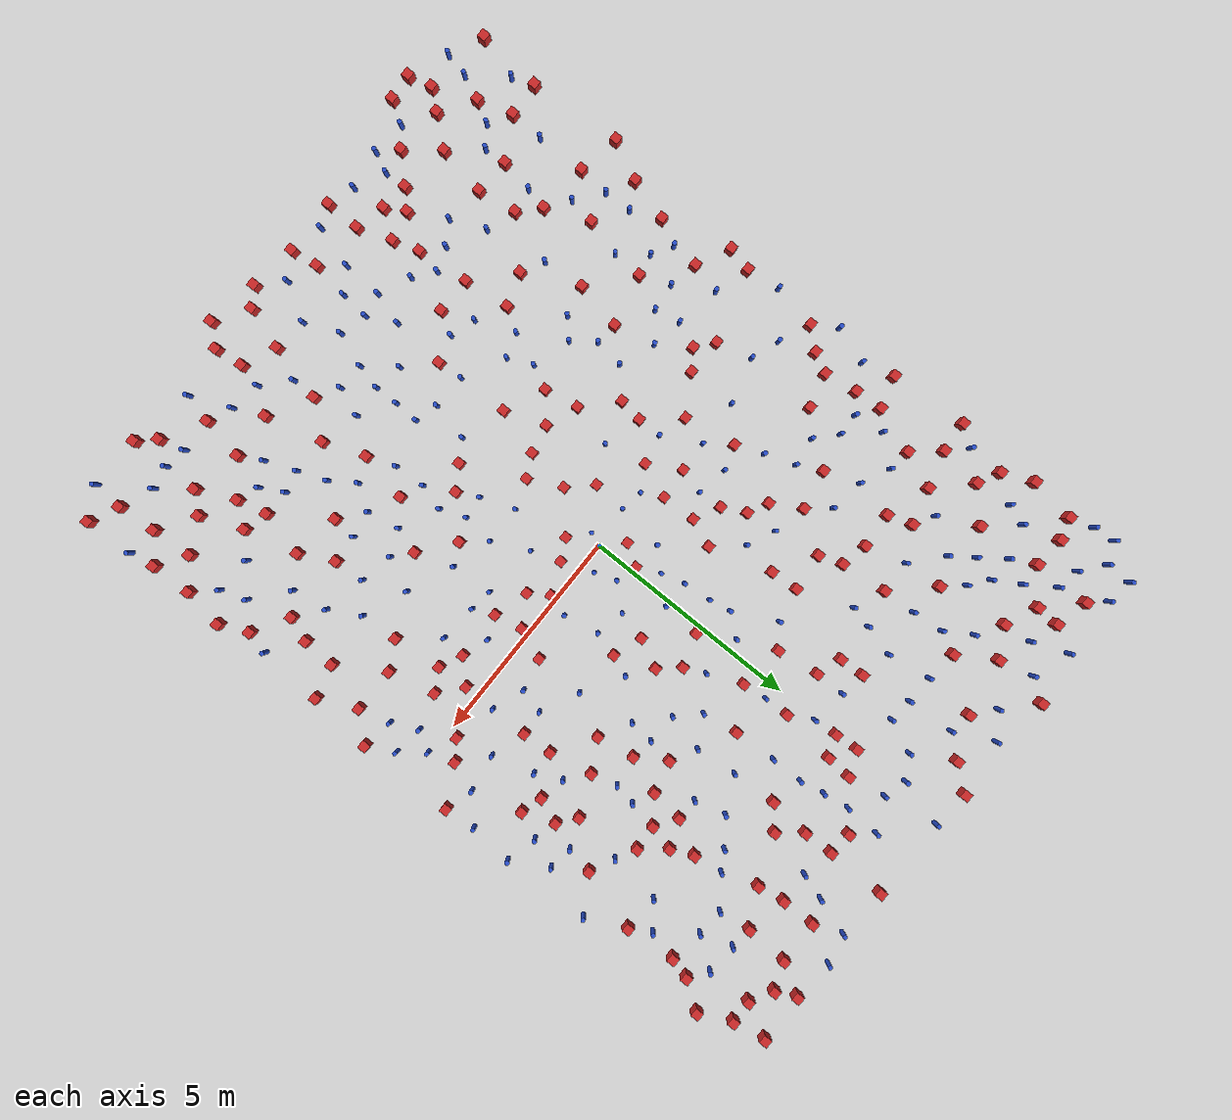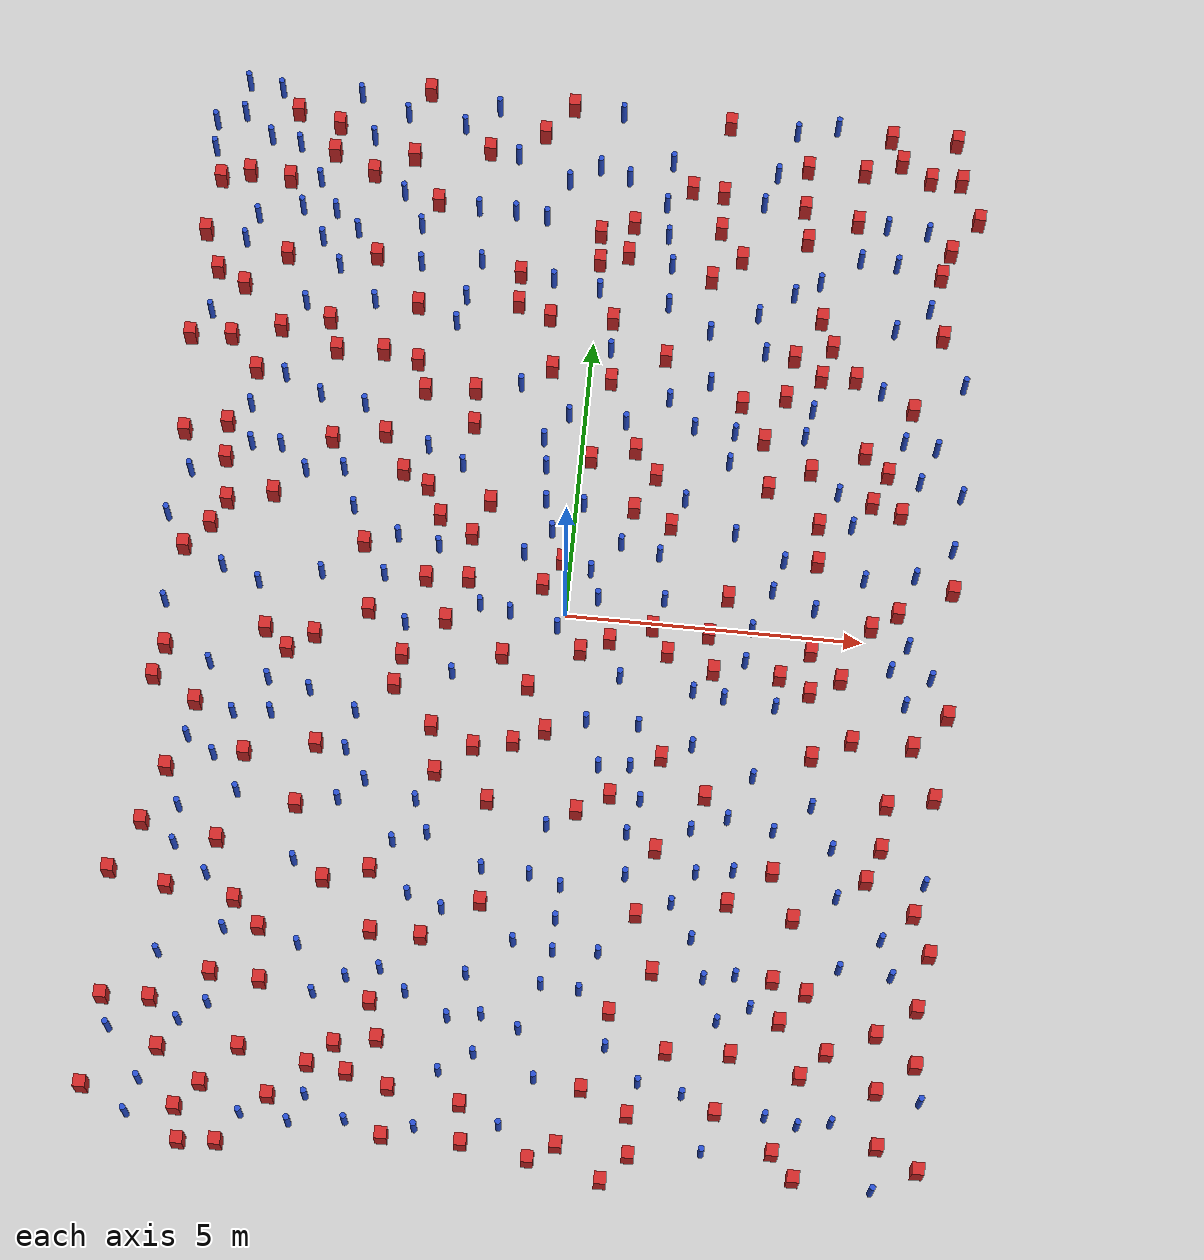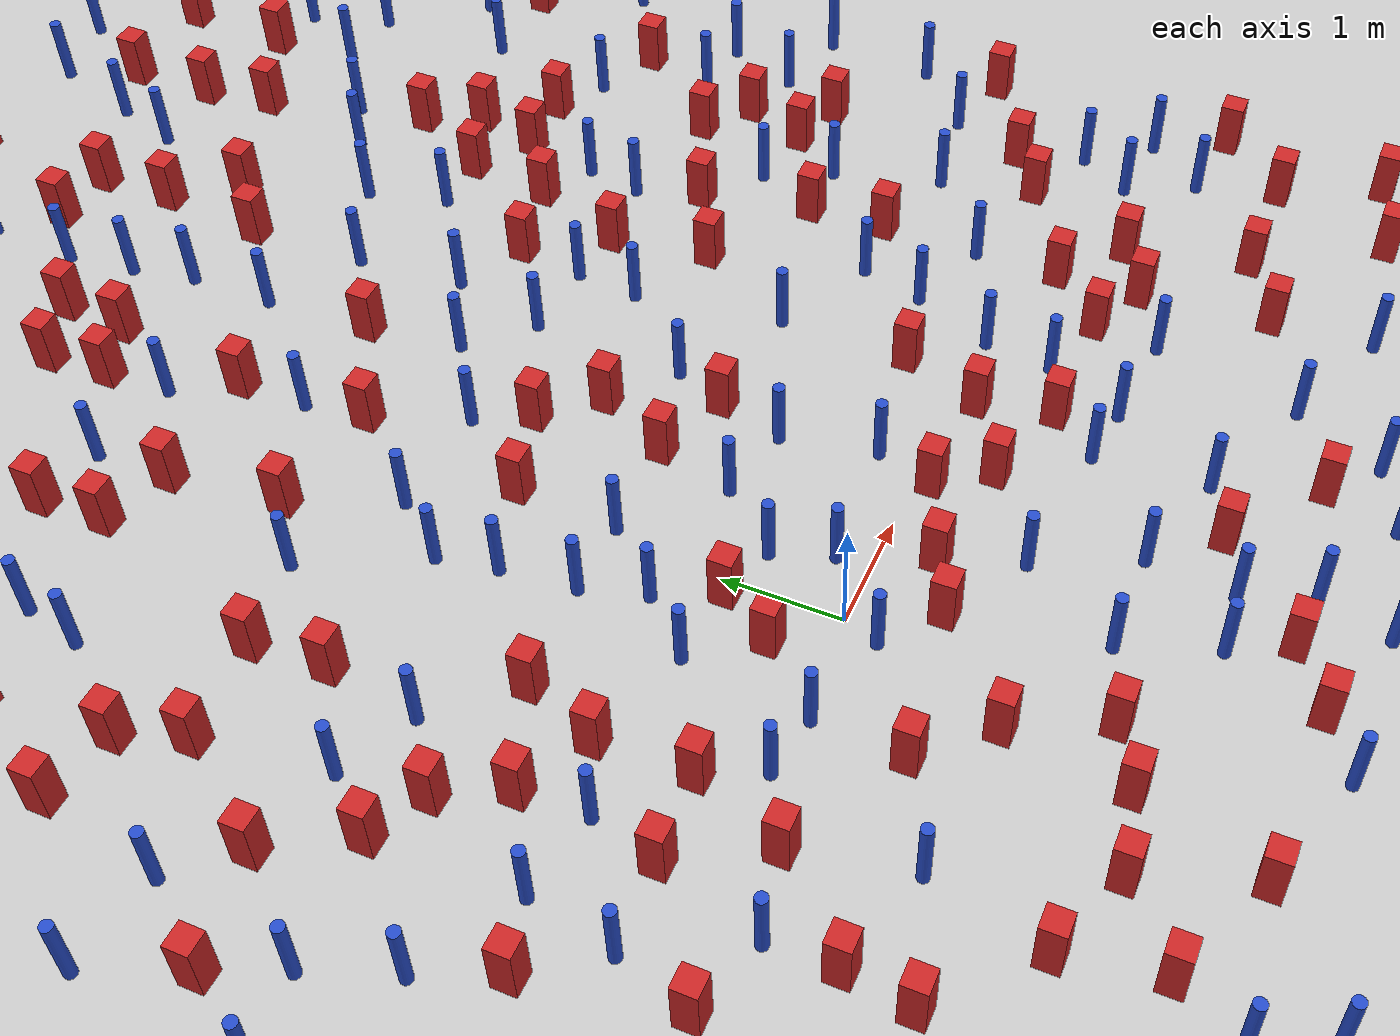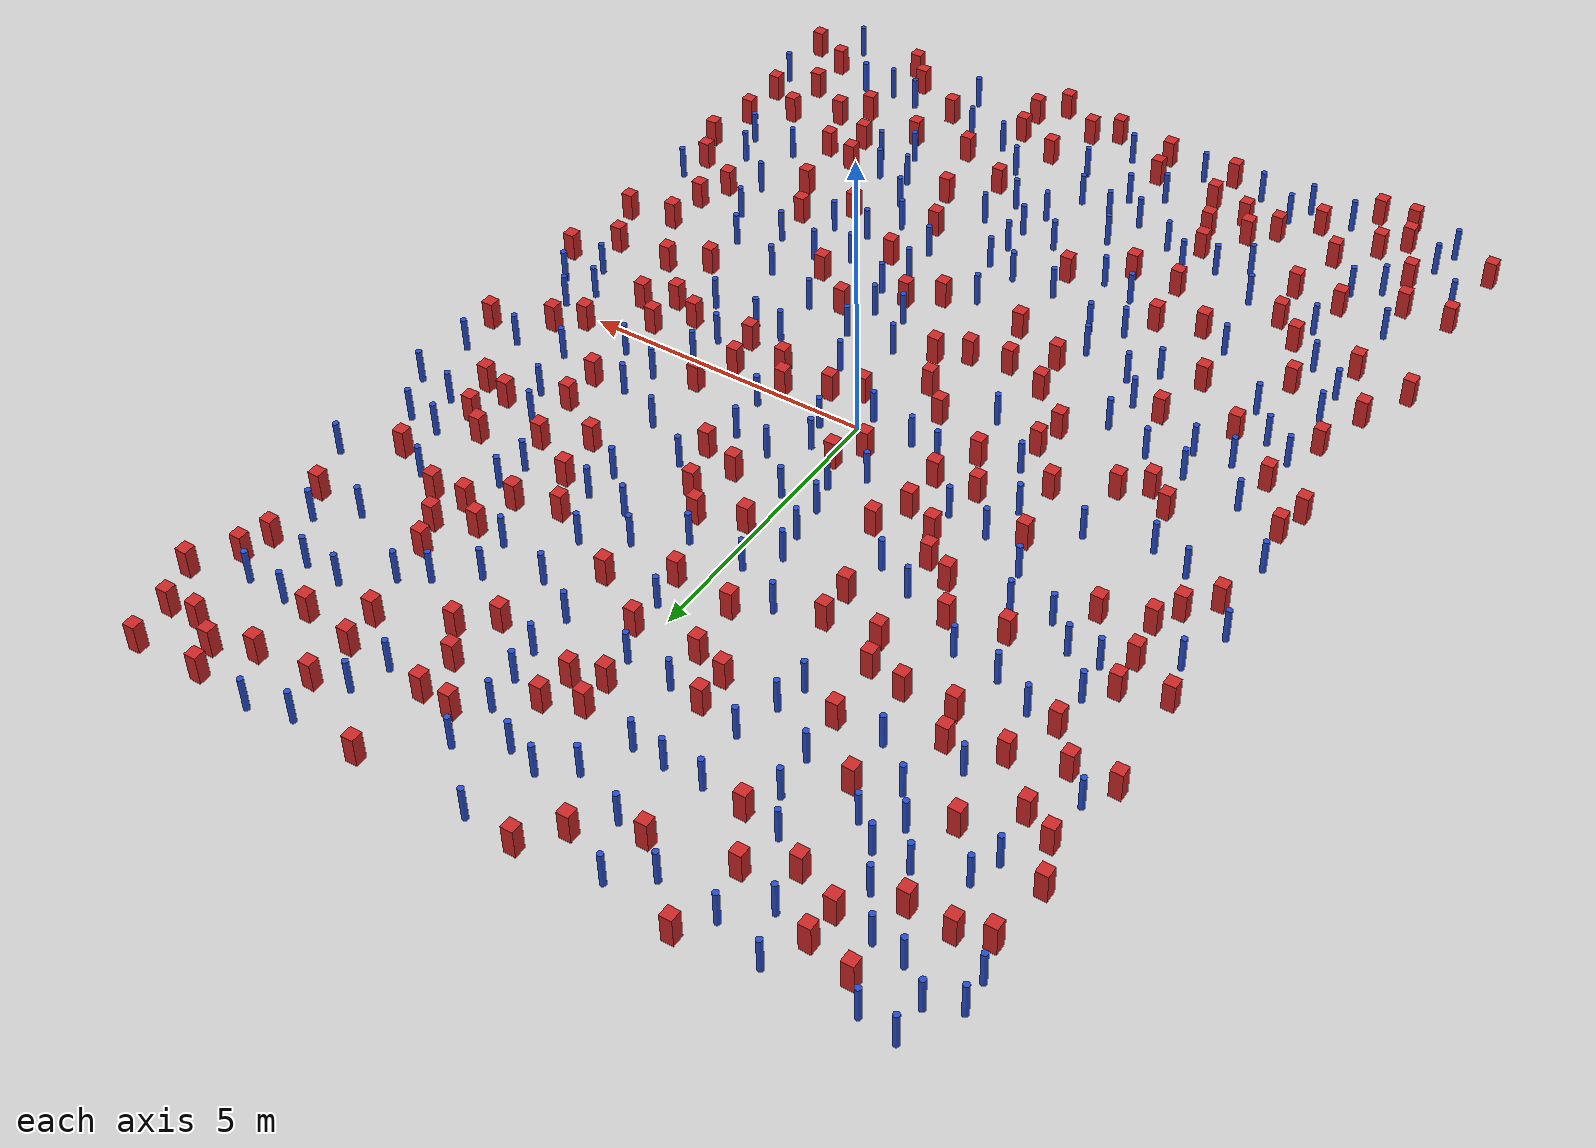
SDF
<sdf version="1.6">
  <model name="dense_83"><model name="pole_obstacle0">
  <static>true</static>
  <pose frame="">-5.31480974983 -2.30998127651 -2.66029137441e-07 -5.69430205643e-07 6.84129966548e-07 -8.68349370881e-08</pose>
  <link name="link">
  <pose frame="">0 0 0.3 0 -0 0</pose>
    <inertial>
      <mass>1</mass>
      <inertia>
        <ixx>0.145833</ixx>
        <ixy>0</ixy>
        <ixz>0</ixz>
        <iyy>0.145833</iyy>
        <iyz>0</iyz>
        <izz>0.125</izz>
      </inertia>
    </inertial>
    <collision name="collision">
      <geometry>
        <cylinder>
          <radius>0.05</radius>
          <length>.6</length>
        </cylinder>
      </geometry>
      <max_contacts>10</max_contacts>
      <surface>
        <contact>
          <ode/>
        </contact>
        <bounce/>
        <friction>
          <torsional>
            <ode/>
          </torsional>
          <ode/>
        </friction>
      </surface>
    </collision>
    <visual name="visual">
      <geometry>
        <cylinder>
          <radius>0.05</radius>
          <length>.6</length>
        </cylinder>
      </geometry>
      <material>
        <script>
          <name>Gazebo/Blue</name>
          <uri>file://media/materials/scripts/gazebo.material</uri>
        </script>
      </material>
    </visual>
    <self_collide>0</self_collide>
    <kinematic>0</kinematic>
  </link>
</model>
<model name="pole_obstacle1">
  <static>true</static>
  <pose frame="">-3.4054695182 -3.62984040929 -2.66029137441e-07 -5.69430205643e-07 6.84129966548e-07 -8.68349370903e-08</pose>
  <link name="link">
  <pose frame="">0 0 0.3 0 -0 0</pose>
    <inertial>
      <mass>1</mass>
      <inertia>
        <ixx>0.145833</ixx>
        <ixy>0</ixy>
        <ixz>0</ixz>
        <iyy>0.145833</iyy>
        <iyz>0</iyz>
        <izz>0.125</izz>
      </inertia>
    </inertial>
    <collision name="collision">
      <geometry>
        <cylinder>
          <radius>0.05</radius>
          <length>.6</length>
        </cylinder>
      </geometry>
      <max_contacts>10</max_contacts>
      <surface>
        <contact>
          <ode/>
        </contact>
        <bounce/>
        <friction>
          <torsional>
            <ode/>
          </torsional>
          <ode/>
        </friction>
      </surface>
    </collision>
    <visual name="visual">
      <geometry>
        <cylinder>
          <radius>0.05</radius>
          <length>.6</length>
        </cylinder>
      </geometry>
      <material>
        <script>
          <name>Gazebo/Blue</name>
          <uri>file://media/materials/scripts/gazebo.material</uri>
        </script>
      </material>
    </visual>
    <self_collide>0</self_collide>
    <kinematic>0</kinematic>
  </link>
</model>
<model name="square_post_obstacle0">
  <static>true</static>
  <pose frame="">2.42696726722 6.77851667209 -7.80171244635e-07 7.17449752808e-06 -5.6639232126e-07 2.2715510512e-05</pose>
  <link name="link">
    <pose frame="">0 0 0.25 0 -0 0</pose>
    <inertial>
      <mass>100</mass>
      <inertia>
        <ixx>0.166667</ixx>
        <ixy>0</ixy>
        <ixz>0</ixz>
        <iyy>0.166667</iyy>
        <iyz>0</iyz>
        <izz>0.166667</izz>
      </inertia>
    </inertial>
    <collision name="collision">
      <geometry>
        <box>
          <size>.2 .2 .5</size>
        </box>
      </geometry>
      <max_contacts>10</max_contacts>
      <surface>
        <contact>
          <ode/>
        </contact>
        <bounce/>
        <friction>
          <torsional>
            <ode/>
          </torsional>
          <ode/>
        </friction>
      </surface>
    </collision>
    <visual name="visual">
      <geometry>
        <box>
          <size>.2 .2 .5</size>
        </box>
      </geometry>
      <material>
        <script>
          <name>Gazebo/Red</name>
          <uri>file://media/materials/scripts/gazebo.material</uri>
        </script>
      </material>
    </visual>
    <self_collide>0</self_collide>
    <kinematic>0</kinematic>
  </link>
</model>
<model name="square_post_obstacle1">
  <static>true</static>
  <pose frame="">-6.06593483988 2.84606556767 -7.80171244635e-07 7.17449752808e-06 -5.6639232126e-07 2.2715510512e-05</pose>
  <link name="link">
    <pose frame="">0 0 0.25 0 -0 0</pose>
    <inertial>
      <mass>100</mass>
      <inertia>
        <ixx>0.166667</ixx>
        <ixy>0</ixy>
        <ixz>0</ixz>
        <iyy>0.166667</iyy>
        <iyz>0</iyz>
        <izz>0.166667</izz>
      </inertia>
    </inertial>
    <collision name="collision">
      <geometry>
        <box>
          <size>.2 .2 .5</size>
        </box>
      </geometry>
      <max_contacts>10</max_contacts>
      <surface>
        <contact>
          <ode/>
        </contact>
        <bounce/>
        <friction>
          <torsional>
            <ode/>
          </torsional>
          <ode/>
        </friction>
      </surface>
    </collision>
    <visual name="visual">
      <geometry>
        <box>
          <size>.2 .2 .5</size>
        </box>
      </geometry>
      <material>
        <script>
          <name>Gazebo/Red</name>
          <uri>file://media/materials/scripts/gazebo.material</uri>
        </script>
      </material>
    </visual>
    <self_collide>0</self_collide>
    <kinematic>0</kinematic>
  </link>
</model>
<model name="pole_obstacle2">
  <static>true</static>
  <pose frame="">4.896897194 7.61736909543 -2.66029137441e-07 -5.69430205655e-07 6.84129966534e-07 -8.68349370984e-08</pose>
  <link name="link">
  <pose frame="">0 0 0.3 0 -0 0</pose>
    <inertial>
      <mass>1</mass>
      <inertia>
        <ixx>0.145833</ixx>
        <ixy>0</ixy>
        <ixz>0</ixz>
        <iyy>0.145833</iyy>
        <iyz>0</iyz>
        <izz>0.125</izz>
      </inertia>
    </inertial>
    <collision name="collision">
      <geometry>
        <cylinder>
          <radius>0.05</radius>
          <length>.6</length>
        </cylinder>
      </geometry>
      <max_contacts>10</max_contacts>
      <surface>
        <contact>
          <ode/>
        </contact>
        <bounce/>
        <friction>
          <torsional>
            <ode/>
          </torsional>
          <ode/>
        </friction>
      </surface>
    </collision>
    <visual name="visual">
      <geometry>
        <cylinder>
          <radius>0.05</radius>
          <length>.6</length>
        </cylinder>
      </geometry>
      <material>
        <script>
          <name>Gazebo/Blue</name>
          <uri>file://media/materials/scripts/gazebo.material</uri>
        </script>
      </material>
    </visual>
    <self_collide>0</self_collide>
    <kinematic>0</kinematic>
  </link>
</model>
<model name="pole_obstacle3">
  <static>true</static>
  <pose frame="">-3.83155564193 5.35007794402 -2.66029137441e-07 -5.69430205635e-07 6.84129966557e-07 -8.68349370832e-08</pose>
  <link name="link">
  <pose frame="">0 0 0.3 0 -0 0</pose>
    <inertial>
      <mass>1</mass>
      <inertia>
        <ixx>0.145833</ixx>
        <ixy>0</ixy>
        <ixz>0</ixz>
        <iyy>0.145833</iyy>
        <iyz>0</iyz>
        <izz>0.125</izz>
      </inertia>
    </inertial>
    <collision name="collision">
      <geometry>
        <cylinder>
          <radius>0.05</radius>
          <length>.6</length>
        </cylinder>
      </geometry>
      <max_contacts>10</max_contacts>
      <surface>
        <contact>
          <ode/>
        </contact>
        <bounce/>
        <friction>
          <torsional>
            <ode/>
          </torsional>
          <ode/>
        </friction>
      </surface>
    </collision>
    <visual name="visual">
      <geometry>
        <cylinder>
          <radius>0.05</radius>
          <length>.6</length>
        </cylinder>
      </geometry>
      <material>
        <script>
          <name>Gazebo/Blue</name>
          <uri>file://media/materials/scripts/gazebo.material</uri>
        </script>
      </material>
    </visual>
    <self_collide>0</self_collide>
    <kinematic>0</kinematic>
  </link>
</model>
<model name="pole_obstacle4">
  <static>true</static>
  <pose frame="">-6.62271847149 4.88114165928 -2.66029137441e-07 -5.69430205655e-07 6.84129966534e-07 -8.68349370984e-08</pose>
  <link name="link">
  <pose frame="">0 0 0.3 0 -0 0</pose>
    <inertial>
      <mass>1</mass>
      <inertia>
        <ixx>0.145833</ixx>
        <ixy>0</ixy>
        <ixz>0</ixz>
        <iyy>0.145833</iyy>
        <iyz>0</iyz>
        <izz>0.125</izz>
      </inertia>
    </inertial>
    <collision name="collision">
      <geometry>
        <cylinder>
          <radius>0.05</radius>
          <length>.6</length>
        </cylinder>
      </geometry>
      <max_contacts>10</max_contacts>
      <surface>
        <contact>
          <ode/>
        </contact>
        <bounce/>
        <friction>
          <torsional>
            <ode/>
          </torsional>
          <ode/>
        </friction>
      </surface>
    </collision>
    <visual name="visual">
      <geometry>
        <cylinder>
          <radius>0.05</radius>
          <length>.6</length>
        </cylinder>
      </geometry>
      <material>
        <script>
          <name>Gazebo/Blue</name>
          <uri>file://media/materials/scripts/gazebo.material</uri>
        </script>
      </material>
    </visual>
    <self_collide>0</self_collide>
    <kinematic>0</kinematic>
  </link>
</model>
<model name="pole_obstacle5">
  <static>true</static>
  <pose frame="">-0.36558280486 1.40867040633 -2.66029137441e-07 -5.69430205636e-07 6.84129966555e-07 -8.68349370824e-08</pose>
  <link name="link">
  <pose frame="">0 0 0.3 0 -0 0</pose>
    <inertial>
      <mass>1</mass>
      <inertia>
        <ixx>0.145833</ixx>
        <ixy>0</ixy>
        <ixz>0</ixz>
        <iyy>0.145833</iyy>
        <iyz>0</iyz>
        <izz>0.125</izz>
      </inertia>
    </inertial>
    <collision name="collision">
      <geometry>
        <cylinder>
          <radius>0.05</radius>
          <length>.6</length>
        </cylinder>
      </geometry>
      <max_contacts>10</max_contacts>
      <surface>
        <contact>
          <ode/>
        </contact>
        <bounce/>
        <friction>
          <torsional>
            <ode/>
          </torsional>
          <ode/>
        </friction>
      </surface>
    </collision>
    <visual name="visual">
      <geometry>
        <cylinder>
          <radius>0.05</radius>
          <length>.6</length>
        </cylinder>
      </geometry>
      <material>
        <script>
          <name>Gazebo/Blue</name>
          <uri>file://media/materials/scripts/gazebo.material</uri>
        </script>
      </material>
    </visual>
    <self_collide>0</self_collide>
    <kinematic>0</kinematic>
  </link>
</model>
<model name="pole_obstacle6">
  <static>true</static>
  <pose frame="">4.94388693489 1.0353948416 -2.66029137441e-07 -5.69430205626e-07 6.84129966567e-07 -8.68349370765e-08</pose>
  <link name="link">
  <pose frame="">0 0 0.3 0 -0 0</pose>
    <inertial>
      <mass>1</mass>
      <inertia>
        <ixx>0.145833</ixx>
        <ixy>0</ixy>
        <ixz>0</ixz>
        <iyy>0.145833</iyy>
        <iyz>0</iyz>
        <izz>0.125</izz>
      </inertia>
    </inertial>
    <collision name="collision">
      <geometry>
        <cylinder>
          <radius>0.05</radius>
          <length>.6</length>
        </cylinder>
      </geometry>
      <max_contacts>10</max_contacts>
      <surface>
        <contact>
          <ode/>
        </contact>
        <bounce/>
        <friction>
          <torsional>
            <ode/>
          </torsional>
          <ode/>
        </friction>
      </surface>
    </collision>
    <visual name="visual">
      <geometry>
        <cylinder>
          <radius>0.05</radius>
          <length>.6</length>
        </cylinder>
      </geometry>
      <material>
        <script>
          <name>Gazebo/Blue</name>
          <uri>file://media/materials/scripts/gazebo.material</uri>
        </script>
      </material>
    </visual>
    <self_collide>0</self_collide>
    <kinematic>0</kinematic>
  </link>
</model>
<model name="square_post_obstacle2">
  <static>true</static>
  <pose frame="">-4.08276042932 -3.77510423322 -7.80171244635e-07 7.17449752808e-06 -5.6639232126e-07 2.2715510512e-05</pose>
  <link name="link">
    <pose frame="">0 0 0.25 0 -0 0</pose>
    <inertial>
      <mass>100</mass>
      <inertia>
        <ixx>0.166667</ixx>
        <ixy>0</ixy>
        <ixz>0</ixz>
        <iyy>0.166667</iyy>
        <iyz>0</iyz>
        <izz>0.166667</izz>
      </inertia>
    </inertial>
    <collision name="collision">
      <geometry>
        <box>
          <size>.2 .2 .5</size>
        </box>
      </geometry>
      <max_contacts>10</max_contacts>
      <surface>
        <contact>
          <ode/>
        </contact>
        <bounce/>
        <friction>
          <torsional>
            <ode/>
          </torsional>
          <ode/>
        </friction>
      </surface>
    </collision>
    <visual name="visual">
      <geometry>
        <box>
          <size>.2 .2 .5</size>
        </box>
      </geometry>
      <material>
        <script>
          <name>Gazebo/Red</name>
          <uri>file://media/materials/scripts/gazebo.material</uri>
        </script>
      </material>
    </visual>
    <self_collide>0</self_collide>
    <kinematic>0</kinematic>
  </link>
</model>
<model name="square_post_obstacle3">
  <static>true</static>
  <pose frame="">-2.63320074149 -1.02899796857 -7.80171244635e-07 7.17449752808e-06 -5.6639232126e-07 2.2715510512e-05</pose>
  <link name="link">
    <pose frame="">0 0 0.25 0 -0 0</pose>
    <inertial>
      <mass>100</mass>
      <inertia>
        <ixx>0.166667</ixx>
        <ixy>0</ixy>
        <ixz>0</ixz>
        <iyy>0.166667</iyy>
        <iyz>0</iyz>
        <izz>0.166667</izz>
      </inertia>
    </inertial>
    <collision name="collision">
      <geometry>
        <box>
          <size>.2 .2 .5</size>
        </box>
      </geometry>
      <max_contacts>10</max_contacts>
      <surface>
        <contact>
          <ode/>
        </contact>
        <bounce/>
        <friction>
          <torsional>
            <ode/>
          </torsional>
          <ode/>
        </friction>
      </surface>
    </collision>
    <visual name="visual">
      <geometry>
        <box>
          <size>.2 .2 .5</size>
        </box>
      </geometry>
      <material>
        <script>
          <name>Gazebo/Red</name>
          <uri>file://media/materials/scripts/gazebo.material</uri>
        </script>
      </material>
    </visual>
    <self_collide>0</self_collide>
    <kinematic>0</kinematic>
  </link>
</model>
<model name="square_post_obstacle4">
  <static>true</static>
  <pose frame="">-3.45802651375 8.20342208291 -7.80171244635e-07 7.17449752808e-06 -5.6639232126e-07 2.2715510512e-05</pose>
  <link name="link">
    <pose frame="">0 0 0.25 0 -0 0</pose>
    <inertial>
      <mass>100</mass>
      <inertia>
        <ixx>0.166667</ixx>
        <ixy>0</ixy>
        <ixz>0</ixz>
        <iyy>0.166667</iyy>
        <iyz>0</iyz>
        <izz>0.166667</izz>
      </inertia>
    </inertial>
    <collision name="collision">
      <geometry>
        <box>
          <size>.2 .2 .5</size>
        </box>
      </geometry>
      <max_contacts>10</max_contacts>
      <surface>
        <contact>
          <ode/>
        </contact>
        <bounce/>
        <friction>
          <torsional>
            <ode/>
          </torsional>
          <ode/>
        </friction>
      </surface>
    </collision>
    <visual name="visual">
      <geometry>
        <box>
          <size>.2 .2 .5</size>
        </box>
      </geometry>
      <material>
        <script>
          <name>Gazebo/Red</name>
          <uri>file://media/materials/scripts/gazebo.material</uri>
        </script>
      </material>
    </visual>
    <self_collide>0</self_collide>
    <kinematic>0</kinematic>
  </link>
</model>
<model name="pole_obstacle7">
  <static>true</static>
  <pose frame="">0.0134859352943 5.94046858157 -2.66029137441e-07 -5.69430205632e-07 6.84129966561e-07 -8.6834937081e-08</pose>
  <link name="link">
  <pose frame="">0 0 0.3 0 -0 0</pose>
    <inertial>
      <mass>1</mass>
      <inertia>
        <ixx>0.145833</ixx>
        <ixy>0</ixy>
        <ixz>0</ixz>
        <iyy>0.145833</iyy>
        <iyz>0</iyz>
        <izz>0.125</izz>
      </inertia>
    </inertial>
    <collision name="collision">
      <geometry>
        <cylinder>
          <radius>0.05</radius>
          <length>.6</length>
        </cylinder>
      </geometry>
      <max_contacts>10</max_contacts>
      <surface>
        <contact>
          <ode/>
        </contact>
        <bounce/>
        <friction>
          <torsional>
            <ode/>
          </torsional>
          <ode/>
        </friction>
      </surface>
    </collision>
    <visual name="visual">
      <geometry>
        <cylinder>
          <radius>0.05</radius>
          <length>.6</length>
        </cylinder>
      </geometry>
      <material>
        <script>
          <name>Gazebo/Blue</name>
          <uri>file://media/materials/scripts/gazebo.material</uri>
        </script>
      </material>
    </visual>
    <self_collide>0</self_collide>
    <kinematic>0</kinematic>
  </link>
</model>
<model name="pole_obstacle8">
  <static>true</static>
  <pose frame="">5.48556464558 -0.522978440494 -2.66029137441e-07 -5.69430205637e-07 6.84129966554e-07 -8.68349370847e-08</pose>
  <link name="link">
  <pose frame="">0 0 0.3 0 -0 0</pose>
    <inertial>
      <mass>1</mass>
      <inertia>
        <ixx>0.145833</ixx>
        <ixy>0</ixy>
        <ixz>0</ixz>
        <iyy>0.145833</iyy>
        <iyz>0</iyz>
        <izz>0.125</izz>
      </inertia>
    </inertial>
    <collision name="collision">
      <geometry>
        <cylinder>
          <radius>0.05</radius>
          <length>.6</length>
        </cylinder>
      </geometry>
      <max_contacts>10</max_contacts>
      <surface>
        <contact>
          <ode/>
        </contact>
        <bounce/>
        <friction>
          <torsional>
            <ode/>
          </torsional>
          <ode/>
        </friction>
      </surface>
    </collision>
    <visual name="visual">
      <geometry>
        <cylinder>
          <radius>0.05</radius>
          <length>.6</length>
        </cylinder>
      </geometry>
      <material>
        <script>
          <name>Gazebo/Blue</name>
          <uri>file://media/materials/scripts/gazebo.material</uri>
        </script>
      </material>
    </visual>
    <self_collide>0</self_collide>
    <kinematic>0</kinematic>
  </link>
</model>
<model name="square_post_obstacle5">
  <static>true</static>
  <pose frame="">-0.97354520431 -0.861248595019 -7.80171244635e-07 7.17449752808e-06 -5.6639232126e-07 2.2715510512e-05</pose>
  <link name="link">
    <pose frame="">0 0 0.25 0 -0 0</pose>
    <inertial>
      <mass>100</mass>
      <inertia>
        <ixx>0.166667</ixx>
        <ixy>0</ixy>
        <ixz>0</ixz>
        <iyy>0.166667</iyy>
        <iyz>0</iyz>
        <izz>0.166667</izz>
      </inertia>
    </inertial>
    <collision name="collision">
      <geometry>
        <box>
          <size>.2 .2 .5</size>
        </box>
      </geometry>
      <max_contacts>10</max_contacts>
      <surface>
        <contact>
          <ode/>
        </contact>
        <bounce/>
        <friction>
          <torsional>
            <ode/>
          </torsional>
          <ode/>
        </friction>
      </surface>
    </collision>
    <visual name="visual">
      <geometry>
        <box>
          <size>.2 .2 .5</size>
        </box>
      </geometry>
      <material>
        <script>
          <name>Gazebo/Red</name>
          <uri>file://media/materials/scripts/gazebo.material</uri>
        </script>
      </material>
    </visual>
    <self_collide>0</self_collide>
    <kinematic>0</kinematic>
  </link>
</model>
<model name="square_post_obstacle6">
  <static>true</static>
  <pose frame="">-0.892551065404 -5.12776510579 -7.80171244635e-07 7.17449752808e-06 -5.6639232126e-07 2.2715510512e-05</pose>
  <link name="link">
    <pose frame="">0 0 0.25 0 -0 0</pose>
    <inertial>
      <mass>100</mass>
      <inertia>
        <ixx>0.166667</ixx>
        <ixy>0</ixy>
        <ixz>0</ixz>
        <iyy>0.166667</iyy>
        <iyz>0</iyz>
        <izz>0.166667</izz>
      </inertia>
    </inertial>
    <collision name="collision">
      <geometry>
        <box>
          <size>.2 .2 .5</size>
        </box>
      </geometry>
      <max_contacts>10</max_contacts>
      <surface>
        <contact>
          <ode/>
        </contact>
        <bounce/>
        <friction>
          <torsional>
            <ode/>
          </torsional>
          <ode/>
        </friction>
      </surface>
    </collision>
    <visual name="visual">
      <geometry>
        <box>
          <size>.2 .2 .5</size>
        </box>
      </geometry>
      <material>
        <script>
          <name>Gazebo/Red</name>
          <uri>file://media/materials/scripts/gazebo.material</uri>
        </script>
      </material>
    </visual>
    <self_collide>0</self_collide>
    <kinematic>0</kinematic>
  </link>
</model>
<model name="square_post_obstacle7">
  <static>true</static>
  <pose frame="">5.48028789459 2.29059251298 -7.80171244635e-07 7.17449752808e-06 -5.6639232126e-07 2.2715510512e-05</pose>
  <link name="link">
    <pose frame="">0 0 0.25 0 -0 0</pose>
    <inertial>
      <mass>100</mass>
      <inertia>
        <ixx>0.166667</ixx>
        <ixy>0</ixy>
        <ixz>0</ixz>
        <iyy>0.166667</iyy>
        <iyz>0</iyz>
        <izz>0.166667</izz>
      </inertia>
    </inertial>
    <collision name="collision">
      <geometry>
        <box>
          <size>.2 .2 .5</size>
        </box>
      </geometry>
      <max_contacts>10</max_contacts>
      <surface>
        <contact>
          <ode/>
        </contact>
        <bounce/>
        <friction>
          <torsional>
            <ode/>
          </torsional>
          <ode/>
        </friction>
      </surface>
    </collision>
    <visual name="visual">
      <geometry>
        <box>
          <size>.2 .2 .5</size>
        </box>
      </geometry>
      <material>
        <script>
          <name>Gazebo/Red</name>
          <uri>file://media/materials/scripts/gazebo.material</uri>
        </script>
      </material>
    </visual>
    <self_collide>0</self_collide>
    <kinematic>0</kinematic>
  </link>
</model>
<model name="pole_obstacle9">
  <static>true</static>
  <pose frame="">3.62680131533 -1.34526293371 -2.66029137441e-07 -5.69430205626e-07 6.84129966567e-07 -8.68349370747e-08</pose>
  <link name="link">
  <pose frame="">0 0 0.3 0 -0 0</pose>
    <inertial>
      <mass>1</mass>
      <inertia>
        <ixx>0.145833</ixx>
        <ixy>0</ixy>
        <ixz>0</ixz>
        <iyy>0.145833</iyy>
        <iyz>0</iyz>
        <izz>0.125</izz>
      </inertia>
    </inertial>
    <collision name="collision">
      <geometry>
        <cylinder>
          <radius>0.05</radius>
          <length>.6</length>
        </cylinder>
      </geometry>
      <max_contacts>10</max_contacts>
      <surface>
        <contact>
          <ode/>
        </contact>
        <bounce/>
        <friction>
          <torsional>
            <ode/>
          </torsional>
          <ode/>
        </friction>
      </surface>
    </collision>
    <visual name="visual">
      <geometry>
        <cylinder>
          <radius>0.05</radius>
          <length>.6</length>
        </cylinder>
      </geometry>
      <material>
        <script>
          <name>Gazebo/Blue</name>
          <uri>file://media/materials/scripts/gazebo.material</uri>
        </script>
      </material>
    </visual>
    <self_collide>0</self_collide>
    <kinematic>0</kinematic>
  </link>
</model>
<model name="pole_obstacle10">
  <static>true</static>
  <pose frame="">-2.1281152215 -3.52390038128 -2.66029137441e-07 -5.69430205643e-07 6.84129966548e-07 -8.68349370903e-08</pose>
  <link name="link">
  <pose frame="">0 0 0.3 0 -0 0</pose>
    <inertial>
      <mass>1</mass>
      <inertia>
        <ixx>0.145833</ixx>
        <ixy>0</ixy>
        <ixz>0</ixz>
        <iyy>0.145833</iyy>
        <iyz>0</iyz>
        <izz>0.125</izz>
      </inertia>
    </inertial>
    <collision name="collision">
      <geometry>
        <cylinder>
          <radius>0.05</radius>
          <length>.6</length>
        </cylinder>
      </geometry>
      <max_contacts>10</max_contacts>
      <surface>
        <contact>
          <ode/>
        </contact>
        <bounce/>
        <friction>
          <torsional>
            <ode/>
          </torsional>
          <ode/>
        </friction>
      </surface>
    </collision>
    <visual name="visual">
      <geometry>
        <cylinder>
          <radius>0.05</radius>
          <length>.6</length>
        </cylinder>
      </geometry>
      <material>
        <script>
          <name>Gazebo/Blue</name>
          <uri>file://media/materials/scripts/gazebo.material</uri>
        </script>
      </material>
    </visual>
    <self_collide>0</self_collide>
    <kinematic>0</kinematic>
  </link>
</model>
<model name="pole_obstacle11">
  <static>true</static>
  <pose frame="">-3.99268747711 2.19236313208 -2.66029137441e-07 -5.69430205653e-07 6.84129966536e-07 -8.68349370973e-08</pose>
  <link name="link">
  <pose frame="">0 0 0.3 0 -0 0</pose>
    <inertial>
      <mass>1</mass>
      <inertia>
        <ixx>0.145833</ixx>
        <ixy>0</ixy>
        <ixz>0</ixz>
        <iyy>0.145833</iyy>
        <iyz>0</iyz>
        <izz>0.125</izz>
      </inertia>
    </inertial>
    <collision name="collision">
      <geometry>
        <cylinder>
          <radius>0.05</radius>
          <length>.6</length>
        </cylinder>
      </geometry>
      <max_contacts>10</max_contacts>
      <surface>
        <contact>
          <ode/>
        </contact>
        <bounce/>
        <friction>
          <torsional>
            <ode/>
          </torsional>
          <ode/>
        </friction>
      </surface>
    </collision>
    <visual name="visual">
      <geometry>
        <cylinder>
          <radius>0.05</radius>
          <length>.6</length>
        </cylinder>
      </geometry>
      <material>
        <script>
          <name>Gazebo/Blue</name>
          <uri>file://media/materials/scripts/gazebo.material</uri>
        </script>
      </material>
    </visual>
    <self_collide>0</self_collide>
    <kinematic>0</kinematic>
  </link>
</model>
<model name="pole_obstacle12">
  <static>true</static>
  <pose frame="">3.98657509384 -8.20033591133 -2.66029137497e-07 -5.69430205676e-07 6.841299665e-07 -8.68349371119e-08</pose>
  <link name="link">
  <pose frame="">0 0 0.3 0 -0 0</pose>
    <inertial>
      <mass>1</mass>
      <inertia>
        <ixx>0.145833</ixx>
        <ixy>0</ixy>
        <ixz>0</ixz>
        <iyy>0.145833</iyy>
        <iyz>0</iyz>
        <izz>0.125</izz>
      </inertia>
    </inertial>
    <collision name="collision">
      <geometry>
        <cylinder>
          <radius>0.05</radius>
          <length>.6</length>
        </cylinder>
      </geometry>
      <max_contacts>10</max_contacts>
      <surface>
        <contact>
          <ode/>
        </contact>
        <bounce/>
        <friction>
          <torsional>
            <ode/>
          </torsional>
          <ode/>
        </friction>
      </surface>
    </collision>
    <visual name="visual">
      <geometry>
        <cylinder>
          <radius>0.05</radius>
          <length>.6</length>
        </cylinder>
      </geometry>
      <material>
        <script>
          <name>Gazebo/Blue</name>
          <uri>file://media/materials/scripts/gazebo.material</uri>
        </script>
      </material>
    </visual>
    <self_collide>0</self_collide>
    <kinematic>0</kinematic>
  </link>
</model>
<model name="square_post_obstacle8">
  <static>true</static>
  <pose frame="">-1.87889073351 3.23329521501 -7.80171244635e-07 7.17449752808e-06 -5.6639232126e-07 2.2715510512e-05</pose>
  <link name="link">
    <pose frame="">0 0 0.25 0 -0 0</pose>
    <inertial>
      <mass>100</mass>
      <inertia>
        <ixx>0.166667</ixx>
        <ixy>0</ixy>
        <ixz>0</ixz>
        <iyy>0.166667</iyy>
        <iyz>0</iyz>
        <izz>0.166667</izz>
      </inertia>
    </inertial>
    <collision name="collision">
      <geometry>
        <box>
          <size>.2 .2 .5</size>
        </box>
      </geometry>
      <max_contacts>10</max_contacts>
      <surface>
        <contact>
          <ode/>
        </contact>
        <bounce/>
        <friction>
          <torsional>
            <ode/>
          </torsional>
          <ode/>
        </friction>
      </surface>
    </collision>
    <visual name="visual">
      <geometry>
        <box>
          <size>.2 .2 .5</size>
        </box>
      </geometry>
      <material>
        <script>
          <name>Gazebo/Red</name>
          <uri>file://media/materials/scripts/gazebo.material</uri>
        </script>
      </material>
    </visual>
    <self_collide>0</self_collide>
    <kinematic>0</kinematic>
  </link>
</model>
<model name="square_post_obstacle9">
  <static>true</static>
  <pose frame="">-2.26860949439 1.50420634749 -7.80171244635e-07 7.17449752808e-06 -5.6639232126e-07 2.2715510512e-05</pose>
  <link name="link">
    <pose frame="">0 0 0.25 0 -0 0</pose>
    <inertial>
      <mass>100</mass>
      <inertia>
        <ixx>0.166667</ixx>
        <ixy>0</ixy>
        <ixz>0</ixz>
        <iyy>0.166667</iyy>
        <iyz>0</iyz>
        <izz>0.166667</izz>
      </inertia>
    </inertial>
    <collision name="collision">
      <geometry>
        <box>
          <size>.2 .2 .5</size>
        </box>
      </geometry>
      <max_contacts>10</max_contacts>
      <surface>
        <contact>
          <ode/>
        </contact>
        <bounce/>
        <friction>
          <torsional>
            <ode/>
          </torsional>
          <ode/>
        </friction>
      </surface>
    </collision>
    <visual name="visual">
      <geometry>
        <box>
          <size>.2 .2 .5</size>
        </box>
      </geometry>
      <material>
        <script>
          <name>Gazebo/Red</name>
          <uri>file://media/materials/scripts/gazebo.material</uri>
        </script>
      </material>
    </visual>
    <self_collide>0</self_collide>
    <kinematic>0</kinematic>
  </link>
</model>
<model name="pole_obstacle13">
  <static>true</static>
  <pose frame="">-2.22282044226 7.28602632548 -2.66029137441e-07 -5.69430205635e-07 6.84129966557e-07 -8.68349370832e-08</pose>
  <link name="link">
  <pose frame="">0 0 0.3 0 -0 0</pose>
    <inertial>
      <mass>1</mass>
      <inertia>
        <ixx>0.145833</ixx>
        <ixy>0</ixy>
        <ixz>0</ixz>
        <iyy>0.145833</iyy>
        <iyz>0</iyz>
        <izz>0.125</izz>
      </inertia>
    </inertial>
    <collision name="collision">
      <geometry>
        <cylinder>
          <radius>0.05</radius>
          <length>.6</length>
        </cylinder>
      </geometry>
      <max_contacts>10</max_contacts>
      <surface>
        <contact>
          <ode/>
        </contact>
        <bounce/>
        <friction>
          <torsional>
            <ode/>
          </torsional>
          <ode/>
        </friction>
      </surface>
    </collision>
    <visual name="visual">
      <geometry>
        <cylinder>
          <radius>0.05</radius>
          <length>.6</length>
        </cylinder>
      </geometry>
      <material>
        <script>
          <name>Gazebo/Blue</name>
          <uri>file://media/materials/scripts/gazebo.material</uri>
        </script>
      </material>
    </visual>
    <self_collide>0</self_collide>
    <kinematic>0</kinematic>
  </link>
</model>
<model name="square_post_obstacle10">
  <static>true</static>
  <pose frame="">-1.35046148378 5.55683016346 -7.80171244635e-07 7.17449752808e-06 -5.6639232126e-07 2.2715510512e-05</pose>
  <link name="link">
    <pose frame="">0 0 0.25 0 -0 0</pose>
    <inertial>
      <mass>100</mass>
      <inertia>
        <ixx>0.166667</ixx>
        <ixy>0</ixy>
        <ixz>0</ixz>
        <iyy>0.166667</iyy>
        <iyz>0</iyz>
        <izz>0.166667</izz>
      </inertia>
    </inertial>
    <collision name="collision">
      <geometry>
        <box>
          <size>.2 .2 .5</size>
        </box>
      </geometry>
      <max_contacts>10</max_contacts>
      <surface>
        <contact>
          <ode/>
        </contact>
        <bounce/>
        <friction>
          <torsional>
            <ode/>
          </torsional>
          <ode/>
        </friction>
      </surface>
    </collision>
    <visual name="visual">
      <geometry>
        <box>
          <size>.2 .2 .5</size>
        </box>
      </geometry>
      <material>
        <script>
          <name>Gazebo/Red</name>
          <uri>file://media/materials/scripts/gazebo.material</uri>
        </script>
      </material>
    </visual>
    <self_collide>0</self_collide>
    <kinematic>0</kinematic>
  </link>
</model>
<model name="square_post_obstacle11">
  <static>true</static>
  <pose frame="">-6.58977767759 -1.23455952323 -7.80171244635e-07 7.17449752808e-06 -5.6639232126e-07 2.2715510512e-05</pose>
  <link name="link">
    <pose frame="">0 0 0.25 0 -0 0</pose>
    <inertial>
      <mass>100</mass>
      <inertia>
        <ixx>0.166667</ixx>
        <ixy>0</ixy>
        <ixz>0</ixz>
        <iyy>0.166667</iyy>
        <iyz>0</iyz>
        <izz>0.166667</izz>
      </inertia>
    </inertial>
    <collision name="collision">
      <geometry>
        <box>
          <size>.2 .2 .5</size>
        </box>
      </geometry>
      <max_contacts>10</max_contacts>
      <surface>
        <contact>
          <ode/>
        </contact>
        <bounce/>
        <friction>
          <torsional>
            <ode/>
          </torsional>
          <ode/>
        </friction>
      </surface>
    </collision>
    <visual name="visual">
      <geometry>
        <box>
          <size>.2 .2 .5</size>
        </box>
      </geometry>
      <material>
        <script>
          <name>Gazebo/Red</name>
          <uri>file://media/materials/scripts/gazebo.material</uri>
        </script>
      </material>
    </visual>
    <self_collide>0</self_collide>
    <kinematic>0</kinematic>
  </link>
</model>
<model name="pole_obstacle14">
  <static>true</static>
  <pose frame="">0.847910647393 -6.44056123123 -2.66029137441e-07 -5.69430205631e-07 6.84129966561e-07 -8.68349370784e-08</pose>
  <link name="link">
  <pose frame="">0 0 0.3 0 -0 0</pose>
    <inertial>
      <mass>1</mass>
      <inertia>
        <ixx>0.145833</ixx>
        <ixy>0</ixy>
        <ixz>0</ixz>
        <iyy>0.145833</iyy>
        <iyz>0</iyz>
        <izz>0.125</izz>
      </inertia>
    </inertial>
    <collision name="collision">
      <geometry>
        <cylinder>
          <radius>0.05</radius>
          <length>.6</length>
        </cylinder>
      </geometry>
      <max_contacts>10</max_contacts>
      <surface>
        <contact>
          <ode/>
        </contact>
        <bounce/>
        <friction>
          <torsional>
            <ode/>
          </torsional>
          <ode/>
        </friction>
      </surface>
    </collision>
    <visual name="visual">
      <geometry>
        <cylinder>
          <radius>0.05</radius>
          <length>.6</length>
        </cylinder>
      </geometry>
      <material>
        <script>
          <name>Gazebo/Blue</name>
          <uri>file://media/materials/scripts/gazebo.material</uri>
        </script>
      </material>
    </visual>
    <self_collide>0</self_collide>
    <kinematic>0</kinematic>
  </link>
</model>
<model name="pole_obstacle15">
  <static>true</static>
  <pose frame="">5.00915462298 4.47468726667 -2.66029137441e-07 -5.69430205655e-07 6.84129966534e-07 -8.68349370984e-08</pose>
  <link name="link">
  <pose frame="">0 0 0.3 0 -0 0</pose>
    <inertial>
      <mass>1</mass>
      <inertia>
        <ixx>0.145833</ixx>
        <ixy>0</ixy>
        <ixz>0</ixz>
        <iyy>0.145833</iyy>
        <iyz>0</iyz>
        <izz>0.125</izz>
      </inertia>
    </inertial>
    <collision name="collision">
      <geometry>
        <cylinder>
          <radius>0.05</radius>
          <length>.6</length>
        </cylinder>
      </geometry>
      <max_contacts>10</max_contacts>
      <surface>
        <contact>
          <ode/>
        </contact>
        <bounce/>
        <friction>
          <torsional>
            <ode/>
          </torsional>
          <ode/>
        </friction>
      </surface>
    </collision>
    <visual name="visual">
      <geometry>
        <cylinder>
          <radius>0.05</radius>
          <length>.6</length>
        </cylinder>
      </geometry>
      <material>
        <script>
          <name>Gazebo/Blue</name>
          <uri>file://media/materials/scripts/gazebo.material</uri>
        </script>
      </material>
    </visual>
    <self_collide>0</self_collide>
    <kinematic>0</kinematic>
  </link>
</model>
<model name="square_post_obstacle12">
  <static>true</static>
  <pose frame="">-5.03160968618 -8.5285034943 -7.80171244635e-07 7.17449752808e-06 -5.6639232126e-07 2.2715510512e-05</pose>
  <link name="link">
    <pose frame="">0 0 0.25 0 -0 0</pose>
    <inertial>
      <mass>100</mass>
      <inertia>
        <ixx>0.166667</ixx>
        <ixy>0</ixy>
        <ixz>0</ixz>
        <iyy>0.166667</iyy>
        <iyz>0</iyz>
        <izz>0.166667</izz>
      </inertia>
    </inertial>
    <collision name="collision">
      <geometry>
        <box>
          <size>.2 .2 .5</size>
        </box>
      </geometry>
      <max_contacts>10</max_contacts>
      <surface>
        <contact>
          <ode/>
        </contact>
        <bounce/>
        <friction>
          <torsional>
            <ode/>
          </torsional>
          <ode/>
        </friction>
      </surface>
    </collision>
    <visual name="visual">
      <geometry>
        <box>
          <size>.2 .2 .5</size>
        </box>
      </geometry>
      <material>
        <script>
          <name>Gazebo/Red</name>
          <uri>file://media/materials/scripts/gazebo.material</uri>
        </script>
      </material>
    </visual>
    <self_collide>0</self_collide>
    <kinematic>0</kinematic>
  </link>
</model>
<model name="pole_obstacle16">
  <static>true</static>
  <pose frame="">2.92044114101 8.44013918548 -2.66029137497e-07 -5.69430205676e-07 6.84129966501e-07 -8.6834937112e-08</pose>
  <link name="link">
  <pose frame="">0 0 0.3 0 -0 0</pose>
    <inertial>
      <mass>1</mass>
      <inertia>
        <ixx>0.145833</ixx>
        <ixy>0</ixy>
        <ixz>0</ixz>
        <iyy>0.145833</iyy>
        <iyz>0</iyz>
        <izz>0.125</izz>
      </inertia>
    </inertial>
    <collision name="collision">
      <geometry>
        <cylinder>
          <radius>0.05</radius>
          <length>.6</length>
        </cylinder>
      </geometry>
      <max_contacts>10</max_contacts>
      <surface>
        <contact>
          <ode/>
        </contact>
        <bounce/>
        <friction>
          <torsional>
            <ode/>
          </torsional>
          <ode/>
        </friction>
      </surface>
    </collision>
    <visual name="visual">
      <geometry>
        <cylinder>
          <radius>0.05</radius>
          <length>.6</length>
        </cylinder>
      </geometry>
      <material>
        <script>
          <name>Gazebo/Blue</name>
          <uri>file://media/materials/scripts/gazebo.material</uri>
        </script>
      </material>
    </visual>
    <self_collide>0</self_collide>
    <kinematic>0</kinematic>
  </link>
</model>
<model name="pole_obstacle17">
  <static>true</static>
  <pose frame="">-0.99536716631 -6.35708189024 -2.66029137441e-07 -5.69430205631e-07 6.84129966562e-07 -8.68349370782e-08</pose>
  <link name="link">
  <pose frame="">0 0 0.3 0 -0 0</pose>
    <inertial>
      <mass>1</mass>
      <inertia>
        <ixx>0.145833</ixx>
        <ixy>0</ixy>
        <ixz>0</ixz>
        <iyy>0.145833</iyy>
        <iyz>0</iyz>
        <izz>0.125</izz>
      </inertia>
    </inertial>
    <collision name="collision">
      <geometry>
        <cylinder>
          <radius>0.05</radius>
          <length>.6</length>
        </cylinder>
      </geometry>
      <max_contacts>10</max_contacts>
      <surface>
        <contact>
          <ode/>
        </contact>
        <bounce/>
        <friction>
          <torsional>
            <ode/>
          </torsional>
          <ode/>
        </friction>
      </surface>
    </collision>
    <visual name="visual">
      <geometry>
        <cylinder>
          <radius>0.05</radius>
          <length>.6</length>
        </cylinder>
      </geometry>
      <material>
        <script>
          <name>Gazebo/Blue</name>
          <uri>file://media/materials/scripts/gazebo.material</uri>
        </script>
      </material>
    </visual>
    <self_collide>0</self_collide>
    <kinematic>0</kinematic>
  </link>
</model>
<model name="square_post_obstacle13">
  <static>true</static>
  <pose frame="">1.6311362432 1.71619895625 -7.80171244635e-07 7.17449752808e-06 -5.6639232126e-07 2.2715510512e-05</pose>
  <link name="link">
    <pose frame="">0 0 0.25 0 -0 0</pose>
    <inertial>
      <mass>100</mass>
      <inertia>
        <ixx>0.166667</ixx>
        <ixy>0</ixy>
        <ixz>0</ixz>
        <iyy>0.166667</iyy>
        <iyz>0</iyz>
        <izz>0.166667</izz>
      </inertia>
    </inertial>
    <collision name="collision">
      <geometry>
        <box>
          <size>.2 .2 .5</size>
        </box>
      </geometry>
      <max_contacts>10</max_contacts>
      <surface>
        <contact>
          <ode/>
        </contact>
        <bounce/>
        <friction>
          <torsional>
            <ode/>
          </torsional>
          <ode/>
        </friction>
      </surface>
    </collision>
    <visual name="visual">
      <geometry>
        <box>
          <size>.2 .2 .5</size>
        </box>
      </geometry>
      <material>
        <script>
          <name>Gazebo/Red</name>
          <uri>file://media/materials/scripts/gazebo.material</uri>
        </script>
      </material>
    </visual>
    <self_collide>0</self_collide>
    <kinematic>0</kinematic>
  </link>
</model>
<model name="pole_obstacle18">
  <static>true</static>
  <pose frame="">-5.97897691177 -4.64420532735 -2.66029137441e-07 -5.69430205655e-07 6.84129966534e-07 -8.68349370984e-08</pose>
  <link name="link">
  <pose frame="">0 0 0.3 0 -0 0</pose>
    <inertial>
      <mass>1</mass>
      <inertia>
        <ixx>0.145833</ixx>
        <ixy>0</ixy>
        <ixz>0</ixz>
        <iyy>0.145833</iyy>
        <iyz>0</iyz>
        <izz>0.125</izz>
      </inertia>
    </inertial>
    <collision name="collision">
      <geometry>
        <cylinder>
          <radius>0.05</radius>
          <length>.6</length>
        </cylinder>
      </geometry>
      <max_contacts>10</max_contacts>
      <surface>
        <contact>
          <ode/>
        </contact>
        <bounce/>
        <friction>
          <torsional>
            <ode/>
          </torsional>
          <ode/>
        </friction>
      </surface>
    </collision>
    <visual name="visual">
      <geometry>
        <cylinder>
          <radius>0.05</radius>
          <length>.6</length>
        </cylinder>
      </geometry>
      <material>
        <script>
          <name>Gazebo/Blue</name>
          <uri>file://media/materials/scripts/gazebo.material</uri>
        </script>
      </material>
    </visual>
    <self_collide>0</self_collide>
    <kinematic>0</kinematic>
  </link>
</model>
<model name="square_post_obstacle14">
  <static>true</static>
  <pose frame="">1.79917641426 -8.37659242516 -7.80171244635e-07 7.17449752808e-06 -5.6639232126e-07 2.2715510512e-05</pose>
  <link name="link">
    <pose frame="">0 0 0.25 0 -0 0</pose>
    <inertial>
      <mass>100</mass>
      <inertia>
        <ixx>0.166667</ixx>
        <ixy>0</ixy>
        <ixz>0</ixz>
        <iyy>0.166667</iyy>
        <iyz>0</iyz>
        <izz>0.166667</izz>
      </inertia>
    </inertial>
    <collision name="collision">
      <geometry>
        <box>
          <size>.2 .2 .5</size>
        </box>
      </geometry>
      <max_contacts>10</max_contacts>
      <surface>
        <contact>
          <ode/>
        </contact>
        <bounce/>
        <friction>
          <torsional>
            <ode/>
          </torsional>
          <ode/>
        </friction>
      </surface>
    </collision>
    <visual name="visual">
      <geometry>
        <box>
          <size>.2 .2 .5</size>
        </box>
      </geometry>
      <material>
        <script>
          <name>Gazebo/Red</name>
          <uri>file://media/materials/scripts/gazebo.material</uri>
        </script>
      </material>
    </visual>
    <self_collide>0</self_collide>
    <kinematic>0</kinematic>
  </link>
</model>
<model name="pole_obstacle19">
  <static>true</static>
  <pose frame="">-2.92377861758 -6.58362115636 -2.66029137441e-07 -5.69430205635e-07 6.84129966557e-07 -8.68349370832e-08</pose>
  <link name="link">
  <pose frame="">0 0 0.3 0 -0 0</pose>
    <inertial>
      <mass>1</mass>
      <inertia>
        <ixx>0.145833</ixx>
        <ixy>0</ixy>
        <ixz>0</ixz>
        <iyy>0.145833</iyy>
        <iyz>0</iyz>
        <izz>0.125</izz>
      </inertia>
    </inertial>
    <collision name="collision">
      <geometry>
        <cylinder>
          <radius>0.05</radius>
          <length>.6</length>
        </cylinder>
      </geometry>
      <max_contacts>10</max_contacts>
      <surface>
        <contact>
          <ode/>
        </contact>
        <bounce/>
        <friction>
          <torsional>
            <ode/>
          </torsional>
          <ode/>
        </friction>
      </surface>
    </collision>
    <visual name="visual">
      <geometry>
        <cylinder>
          <radius>0.05</radius>
          <length>.6</length>
        </cylinder>
      </geometry>
      <material>
        <script>
          <name>Gazebo/Blue</name>
          <uri>file://media/materials/scripts/gazebo.material</uri>
        </script>
      </material>
    </visual>
    <self_collide>0</self_collide>
    <kinematic>0</kinematic>
  </link>
</model>
<model name="square_post_obstacle15">
  <static>true</static>
  <pose frame="">-1.92103498765 3.86688536144 -7.80171244635e-07 7.17449752808e-06 -5.6639232126e-07 2.2715510512e-05</pose>
  <link name="link">
    <pose frame="">0 0 0.25 0 -0 0</pose>
    <inertial>
      <mass>100</mass>
      <inertia>
        <ixx>0.166667</ixx>
        <ixy>0</ixy>
        <ixz>0</ixz>
        <iyy>0.166667</iyy>
        <iyz>0</iyz>
        <izz>0.166667</izz>
      </inertia>
    </inertial>
    <collision name="collision">
      <geometry>
        <box>
          <size>.2 .2 .5</size>
        </box>
      </geometry>
      <max_contacts>10</max_contacts>
      <surface>
        <contact>
          <ode/>
        </contact>
        <bounce/>
        <friction>
          <torsional>
            <ode/>
          </torsional>
          <ode/>
        </friction>
      </surface>
    </collision>
    <visual name="visual">
      <geometry>
        <box>
          <size>.2 .2 .5</size>
        </box>
      </geometry>
      <material>
        <script>
          <name>Gazebo/Red</name>
          <uri>file://media/materials/scripts/gazebo.material</uri>
        </script>
      </material>
    </visual>
    <self_collide>0</self_collide>
    <kinematic>0</kinematic>
  </link>
</model>
<model name="square_post_obstacle16">
  <static>true</static>
  <pose frame="">-6.01761942537 2.20735195207 -7.80171244635e-07 7.17449752808e-06 -5.6639232126e-07 2.2715510512e-05</pose>
  <link name="link">
    <pose frame="">0 0 0.25 0 -0 0</pose>
    <inertial>
      <mass>100</mass>
      <inertia>
        <ixx>0.166667</ixx>
        <ixy>0</ixy>
        <ixz>0</ixz>
        <iyy>0.166667</iyy>
        <iyz>0</iyz>
        <izz>0.166667</izz>
      </inertia>
    </inertial>
    <collision name="collision">
      <geometry>
        <box>
          <size>.2 .2 .5</size>
        </box>
      </geometry>
      <max_contacts>10</max_contacts>
      <surface>
        <contact>
          <ode/>
        </contact>
        <bounce/>
        <friction>
          <torsional>
            <ode/>
          </torsional>
          <ode/>
        </friction>
      </surface>
    </collision>
    <visual name="visual">
      <geometry>
        <box>
          <size>.2 .2 .5</size>
        </box>
      </geometry>
      <material>
        <script>
          <name>Gazebo/Red</name>
          <uri>file://media/materials/scripts/gazebo.material</uri>
        </script>
      </material>
    </visual>
    <self_collide>0</self_collide>
    <kinematic>0</kinematic>
  </link>
</model>
<model name="square_post_obstacle17">
  <static>true</static>
  <pose frame="">4.17508941673 -1.03326781542 -7.80171244635e-07 7.17449752808e-06 -5.6639232126e-07 2.2715510512e-05</pose>
  <link name="link">
    <pose frame="">0 0 0.25 0 -0 0</pose>
    <inertial>
      <mass>100</mass>
      <inertia>
        <ixx>0.166667</ixx>
        <ixy>0</ixy>
        <ixz>0</ixz>
        <iyy>0.166667</iyy>
        <iyz>0</iyz>
        <izz>0.166667</izz>
      </inertia>
    </inertial>
    <collision name="collision">
      <geometry>
        <box>
          <size>.2 .2 .5</size>
        </box>
      </geometry>
      <max_contacts>10</max_contacts>
      <surface>
        <contact>
          <ode/>
        </contact>
        <bounce/>
        <friction>
          <torsional>
            <ode/>
          </torsional>
          <ode/>
        </friction>
      </surface>
    </collision>
    <visual name="visual">
      <geometry>
        <box>
          <size>.2 .2 .5</size>
        </box>
      </geometry>
      <material>
        <script>
          <name>Gazebo/Red</name>
          <uri>file://media/materials/scripts/gazebo.material</uri>
        </script>
      </material>
    </visual>
    <self_collide>0</self_collide>
    <kinematic>0</kinematic>
  </link>
</model>
<model name="pole_obstacle20">
  <static>true</static>
  <pose frame="">3.20089135605 9.28862393456 -2.66029137497e-07 -5.69430205676e-07 6.84129966501e-07 -8.6834937112e-08</pose>
  <link name="link">
  <pose frame="">0 0 0.3 0 -0 0</pose>
    <inertial>
      <mass>1</mass>
      <inertia>
        <ixx>0.145833</ixx>
        <ixy>0</ixy>
        <ixz>0</ixz>
        <iyy>0.145833</iyy>
        <iyz>0</iyz>
        <izz>0.125</izz>
      </inertia>
    </inertial>
    <collision name="collision">
      <geometry>
        <cylinder>
          <radius>0.05</radius>
          <length>.6</length>
        </cylinder>
      </geometry>
      <max_contacts>10</max_contacts>
      <surface>
        <contact>
          <ode/>
        </contact>
        <bounce/>
        <friction>
          <torsional>
            <ode/>
          </torsional>
          <ode/>
        </friction>
      </surface>
    </collision>
    <visual name="visual">
      <geometry>
        <cylinder>
          <radius>0.05</radius>
          <length>.6</length>
        </cylinder>
      </geometry>
      <material>
        <script>
          <name>Gazebo/Blue</name>
          <uri>file://media/materials/scripts/gazebo.material</uri>
        </script>
      </material>
    </visual>
    <self_collide>0</self_collide>
    <kinematic>0</kinematic>
  </link>
</model>
<model name="pole_obstacle21">
  <static>true</static>
  <pose frame="">-0.27936909886 3.54759653769 -2.66029137441e-07 -5.69430205627e-07 6.84129966567e-07 -8.68349370764e-08</pose>
  <link name="link">
  <pose frame="">0 0 0.3 0 -0 0</pose>
    <inertial>
      <mass>1</mass>
      <inertia>
        <ixx>0.145833</ixx>
        <ixy>0</ixy>
        <ixz>0</ixz>
        <iyy>0.145833</iyy>
        <iyz>0</iyz>
        <izz>0.125</izz>
      </inertia>
    </inertial>
    <collision name="collision">
      <geometry>
        <cylinder>
          <radius>0.05</radius>
          <length>.6</length>
        </cylinder>
      </geometry>
      <max_contacts>10</max_contacts>
      <surface>
        <contact>
          <ode/>
        </contact>
        <bounce/>
        <friction>
          <torsional>
            <ode/>
          </torsional>
          <ode/>
        </friction>
      </surface>
    </collision>
    <visual name="visual">
      <geometry>
        <cylinder>
          <radius>0.05</radius>
          <length>.6</length>
        </cylinder>
      </geometry>
      <material>
        <script>
          <name>Gazebo/Blue</name>
          <uri>file://media/materials/scripts/gazebo.material</uri>
        </script>
      </material>
    </visual>
    <self_collide>0</self_collide>
    <kinematic>0</kinematic>
  </link>
</model>
<model name="pole_obstacle22">
  <static>true</static>
  <pose frame="">-1.63562306769 8.36145736392 -2.66029137441e-07 -5.69430205648e-07 6.84129966543e-07 -8.68349370925e-08</pose>
  <link name="link">
  <pose frame="">0 0 0.3 0 -0 0</pose>
    <inertial>
      <mass>1</mass>
      <inertia>
        <ixx>0.145833</ixx>
        <ixy>0</ixy>
        <ixz>0</ixz>
        <iyy>0.145833</iyy>
        <iyz>0</iyz>
        <izz>0.125</izz>
      </inertia>
    </inertial>
    <collision name="collision">
      <geometry>
        <cylinder>
          <radius>0.05</radius>
          <length>.6</length>
        </cylinder>
      </geometry>
      <max_contacts>10</max_contacts>
      <surface>
        <contact>
          <ode/>
        </contact>
        <bounce/>
        <friction>
          <torsional>
            <ode/>
          </torsional>
          <ode/>
        </friction>
      </surface>
    </collision>
    <visual name="visual">
      <geometry>
        <cylinder>
          <radius>0.05</radius>
          <length>.6</length>
        </cylinder>
      </geometry>
      <material>
        <script>
          <name>Gazebo/Blue</name>
          <uri>file://media/materials/scripts/gazebo.material</uri>
        </script>
      </material>
    </visual>
    <self_collide>0</self_collide>
    <kinematic>0</kinematic>
  </link>
</model>
<model name="pole_obstacle23">
  <static>true</static>
  <pose frame="">-0.18244795766 8.28740664911 -2.66029137441e-07 -5.69430205656e-07 6.84129966534e-07 -8.68349371007e-08</pose>
  <link name="link">
  <pose frame="">0 0 0.3 0 -0 0</pose>
    <inertial>
      <mass>1</mass>
      <inertia>
        <ixx>0.145833</ixx>
        <ixy>0</ixy>
        <ixz>0</ixz>
        <iyy>0.145833</iyy>
        <iyz>0</iyz>
        <izz>0.125</izz>
      </inertia>
    </inertial>
    <collision name="collision">
      <geometry>
        <cylinder>
          <radius>0.05</radius>
          <length>.6</length>
        </cylinder>
      </geometry>
      <max_contacts>10</max_contacts>
      <surface>
        <contact>
          <ode/>
        </contact>
        <bounce/>
        <friction>
          <torsional>
            <ode/>
          </torsional>
          <ode/>
        </friction>
      </surface>
    </collision>
    <visual name="visual">
      <geometry>
        <cylinder>
          <radius>0.05</radius>
          <length>.6</length>
        </cylinder>
      </geometry>
      <material>
        <script>
          <name>Gazebo/Blue</name>
          <uri>file://media/materials/scripts/gazebo.material</uri>
        </script>
      </material>
    </visual>
    <self_collide>0</self_collide>
    <kinematic>0</kinematic>
  </link>
</model>
<model name="square_post_obstacle18">
  <static>true</static>
  <pose frame="">-6.28844079783 7.6105690469 -7.80171244635e-07 7.17449752808e-06 -5.6639232126e-07 2.2715510512e-05</pose>
  <link name="link">
    <pose frame="">0 0 0.25 0 -0 0</pose>
    <inertial>
      <mass>100</mass>
      <inertia>
        <ixx>0.166667</ixx>
        <ixy>0</ixy>
        <ixz>0</ixz>
        <iyy>0.166667</iyy>
        <iyz>0</iyz>
        <izz>0.166667</izz>
      </inertia>
    </inertial>
    <collision name="collision">
      <geometry>
        <box>
          <size>.2 .2 .5</size>
        </box>
      </geometry>
      <max_contacts>10</max_contacts>
      <surface>
        <contact>
          <ode/>
        </contact>
        <bounce/>
        <friction>
          <torsional>
            <ode/>
          </torsional>
          <ode/>
        </friction>
      </surface>
    </collision>
    <visual name="visual">
      <geometry>
        <box>
          <size>.2 .2 .5</size>
        </box>
      </geometry>
      <material>
        <script>
          <name>Gazebo/Red</name>
          <uri>file://media/materials/scripts/gazebo.material</uri>
        </script>
      </material>
    </visual>
    <self_collide>0</self_collide>
    <kinematic>0</kinematic>
  </link>
</model>
<model name="pole_obstacle24">
  <static>true</static>
  <pose frame="">-1.506349523 -5.30545802994 -2.66029137441e-07 -5.69430205635e-07 6.84129966557e-07 -8.68349370822e-08</pose>
  <link name="link">
  <pose frame="">0 0 0.3 0 -0 0</pose>
    <inertial>
      <mass>1</mass>
      <inertia>
        <ixx>0.145833</ixx>
        <ixy>0</ixy>
        <ixz>0</ixz>
        <iyy>0.145833</iyy>
        <iyz>0</iyz>
        <izz>0.125</izz>
      </inertia>
    </inertial>
    <collision name="collision">
      <geometry>
        <cylinder>
          <radius>0.05</radius>
          <length>.6</length>
        </cylinder>
      </geometry>
      <max_contacts>10</max_contacts>
      <surface>
        <contact>
          <ode/>
        </contact>
        <bounce/>
        <friction>
          <torsional>
            <ode/>
          </torsional>
          <ode/>
        </friction>
      </surface>
    </collision>
    <visual name="visual">
      <geometry>
        <cylinder>
          <radius>0.05</radius>
          <length>.6</length>
        </cylinder>
      </geometry>
      <material>
        <script>
          <name>Gazebo/Blue</name>
          <uri>file://media/materials/scripts/gazebo.material</uri>
        </script>
      </material>
    </visual>
    <self_collide>0</self_collide>
    <kinematic>0</kinematic>
  </link>
</model>
<model name="pole_obstacle25">
  <static>true</static>
  <pose frame="">5.45203263859 3.59060383221 -2.66029137441e-07 -5.69430205643e-07 6.84129966548e-07 -8.68349370881e-08</pose>
  <link name="link">
  <pose frame="">0 0 0.3 0 -0 0</pose>
    <inertial>
      <mass>1</mass>
      <inertia>
        <ixx>0.145833</ixx>
        <ixy>0</ixy>
        <ixz>0</ixz>
        <iyy>0.145833</iyy>
        <iyz>0</iyz>
        <izz>0.125</izz>
      </inertia>
    </inertial>
    <collision name="collision">
      <geometry>
        <cylinder>
          <radius>0.05</radius>
          <length>.6</length>
        </cylinder>
      </geometry>
      <max_contacts>10</max_contacts>
      <surface>
        <contact>
          <ode/>
        </contact>
        <bounce/>
        <friction>
          <torsional>
            <ode/>
          </torsional>
          <ode/>
        </friction>
      </surface>
    </collision>
    <visual name="visual">
      <geometry>
        <cylinder>
          <radius>0.05</radius>
          <length>.6</length>
        </cylinder>
      </geometry>
      <material>
        <script>
          <name>Gazebo/Blue</name>
          <uri>file://media/materials/scripts/gazebo.material</uri>
        </script>
      </material>
    </visual>
    <self_collide>0</self_collide>
    <kinematic>0</kinematic>
  </link>
</model>
<model name="pole_obstacle26">
  <static>true</static>
  <pose frame="">1.01270264934 -1.07271620968 -2.66029137441e-07 -5.69430205629e-07 6.84129966564e-07 -8.6834937076e-08</pose>
  <link name="link">
  <pose frame="">0 0 0.3 0 -0 0</pose>
    <inertial>
      <mass>1</mass>
      <inertia>
        <ixx>0.145833</ixx>
        <ixy>0</ixy>
        <ixz>0</ixz>
        <iyy>0.145833</iyy>
        <iyz>0</iyz>
        <izz>0.125</izz>
      </inertia>
    </inertial>
    <collision name="collision">
      <geometry>
        <cylinder>
          <radius>0.05</radius>
          <length>.6</length>
        </cylinder>
      </geometry>
      <max_contacts>10</max_contacts>
      <surface>
        <contact>
          <ode/>
        </contact>
        <bounce/>
        <friction>
          <torsional>
            <ode/>
          </torsional>
          <ode/>
        </friction>
      </surface>
    </collision>
    <visual name="visual">
      <geometry>
        <cylinder>
          <radius>0.05</radius>
          <length>.6</length>
        </cylinder>
      </geometry>
      <material>
        <script>
          <name>Gazebo/Blue</name>
          <uri>file://media/materials/scripts/gazebo.material</uri>
        </script>
      </material>
    </visual>
    <self_collide>0</self_collide>
    <kinematic>0</kinematic>
  </link>
</model>
<model name="pole_obstacle27">
  <static>true</static>
  <pose frame="">-6.00216226382 -6.47632057488 -2.66029137441e-07 -5.69430205655e-07 6.84129966534e-07 -8.68349370984e-08</pose>
  <link name="link">
  <pose frame="">0 0 0.3 0 -0 0</pose>
    <inertial>
      <mass>1</mass>
      <inertia>
        <ixx>0.145833</ixx>
        <ixy>0</ixy>
        <ixz>0</ixz>
        <iyy>0.145833</iyy>
        <iyz>0</iyz>
        <izz>0.125</izz>
      </inertia>
    </inertial>
    <collision name="collision">
      <geometry>
        <cylinder>
          <radius>0.05</radius>
          <length>.6</length>
        </cylinder>
      </geometry>
      <max_contacts>10</max_contacts>
      <surface>
        <contact>
          <ode/>
        </contact>
        <bounce/>
        <friction>
          <torsional>
            <ode/>
          </torsional>
          <ode/>
        </friction>
      </surface>
    </collision>
    <visual name="visual">
      <geometry>
        <cylinder>
          <radius>0.05</radius>
          <length>.6</length>
        </cylinder>
      </geometry>
      <material>
        <script>
          <name>Gazebo/Blue</name>
          <uri>file://media/materials/scripts/gazebo.material</uri>
        </script>
      </material>
    </visual>
    <self_collide>0</self_collide>
    <kinematic>0</kinematic>
  </link>
</model>
<model name="pole_obstacle28">
  <static>true</static>
  <pose frame="">5.75426702351 -9.21714733048 -2.66029137441e-07 -5.69430205631e-07 6.84129966561e-07 -8.68349370782e-08</pose>
  <link name="link">
  <pose frame="">0 0 0.3 0 -0 0</pose>
    <inertial>
      <mass>1</mass>
      <inertia>
        <ixx>0.145833</ixx>
        <ixy>0</ixy>
        <ixz>0</ixz>
        <iyy>0.145833</iyy>
        <iyz>0</iyz>
        <izz>0.125</izz>
      </inertia>
    </inertial>
    <collision name="collision">
      <geometry>
        <cylinder>
          <radius>0.05</radius>
          <length>.6</length>
        </cylinder>
      </geometry>
      <max_contacts>10</max_contacts>
      <surface>
        <contact>
          <ode/>
        </contact>
        <bounce/>
        <friction>
          <torsional>
            <ode/>
          </torsional>
          <ode/>
        </friction>
      </surface>
    </collision>
    <visual name="visual">
      <geometry>
        <cylinder>
          <radius>0.05</radius>
          <length>.6</length>
        </cylinder>
      </geometry>
      <material>
        <script>
          <name>Gazebo/Blue</name>
          <uri>file://media/materials/scripts/gazebo.material</uri>
        </script>
      </material>
    </visual>
    <self_collide>0</self_collide>
    <kinematic>0</kinematic>
  </link>
</model>
<model name="square_post_obstacle19">
  <static>true</static>
  <pose frame="">2.64595002164 4.06510122448 -7.80171244635e-07 7.17449752808e-06 -5.6639232126e-07 2.2715510512e-05</pose>
  <link name="link">
    <pose frame="">0 0 0.25 0 -0 0</pose>
    <inertial>
      <mass>100</mass>
      <inertia>
        <ixx>0.166667</ixx>
        <ixy>0</ixy>
        <ixz>0</ixz>
        <iyy>0.166667</iyy>
        <iyz>0</iyz>
        <izz>0.166667</izz>
      </inertia>
    </inertial>
    <collision name="collision">
      <geometry>
        <box>
          <size>.2 .2 .5</size>
        </box>
      </geometry>
      <max_contacts>10</max_contacts>
      <surface>
        <contact>
          <ode/>
        </contact>
        <bounce/>
        <friction>
          <torsional>
            <ode/>
          </torsional>
          <ode/>
        </friction>
      </surface>
    </collision>
    <visual name="visual">
      <geometry>
        <box>
          <size>.2 .2 .5</size>
        </box>
      </geometry>
      <material>
        <script>
          <name>Gazebo/Red</name>
          <uri>file://media/materials/scripts/gazebo.material</uri>
        </script>
      </material>
    </visual>
    <self_collide>0</self_collide>
    <kinematic>0</kinematic>
  </link>
</model>
<model name="square_post_obstacle20">
  <static>true</static>
  <pose frame="">2.32735849754 -7.29957355424 -7.80171244635e-07 7.17449752808e-06 -5.6639232126e-07 2.2715510512e-05</pose>
  <link name="link">
    <pose frame="">0 0 0.25 0 -0 0</pose>
    <inertial>
      <mass>100</mass>
      <inertia>
        <ixx>0.166667</ixx>
        <ixy>0</ixy>
        <ixz>0</ixz>
        <iyy>0.166667</iyy>
        <iyz>0</iyz>
        <izz>0.166667</izz>
      </inertia>
    </inertial>
    <collision name="collision">
      <geometry>
        <box>
          <size>.2 .2 .5</size>
        </box>
      </geometry>
      <max_contacts>10</max_contacts>
      <surface>
        <contact>
          <ode/>
        </contact>
        <bounce/>
        <friction>
          <torsional>
            <ode/>
          </torsional>
          <ode/>
        </friction>
      </surface>
    </collision>
    <visual name="visual">
      <geometry>
        <box>
          <size>.2 .2 .5</size>
        </box>
      </geometry>
      <material>
        <script>
          <name>Gazebo/Red</name>
          <uri>file://media/materials/scripts/gazebo.material</uri>
        </script>
      </material>
    </visual>
    <self_collide>0</self_collide>
    <kinematic>0</kinematic>
  </link>
</model>
<model name="pole_obstacle29">
  <static>true</static>
  <pose frame="">5.11539791772 6.89736885478 -2.66029137441e-07 -5.69430205655e-07 6.84129966534e-07 -8.68349370984e-08</pose>
  <link name="link">
  <pose frame="">0 0 0.3 0 -0 0</pose>
    <inertial>
      <mass>1</mass>
      <inertia>
        <ixx>0.145833</ixx>
        <ixy>0</ixy>
        <ixz>0</ixz>
        <iyy>0.145833</iyy>
        <iyz>0</iyz>
        <izz>0.125</izz>
      </inertia>
    </inertial>
    <collision name="collision">
      <geometry>
        <cylinder>
          <radius>0.05</radius>
          <length>.6</length>
        </cylinder>
      </geometry>
      <max_contacts>10</max_contacts>
      <surface>
        <contact>
          <ode/>
        </contact>
        <bounce/>
        <friction>
          <torsional>
            <ode/>
          </torsional>
          <ode/>
        </friction>
      </surface>
    </collision>
    <visual name="visual">
      <geometry>
        <cylinder>
          <radius>0.05</radius>
          <length>.6</length>
        </cylinder>
      </geometry>
      <material>
        <script>
          <name>Gazebo/Blue</name>
          <uri>file://media/materials/scripts/gazebo.material</uri>
        </script>
      </material>
    </visual>
    <self_collide>0</self_collide>
    <kinematic>0</kinematic>
  </link>
</model>
<model name="square_post_obstacle21">
  <static>true</static>
  <pose frame="">-2.53292568742 2.02529417124 -7.80171244635e-07 7.17449752808e-06 -5.6639232126e-07 2.2715510512e-05</pose>
  <link name="link">
    <pose frame="">0 0 0.25 0 -0 0</pose>
    <inertial>
      <mass>100</mass>
      <inertia>
        <ixx>0.166667</ixx>
        <ixy>0</ixy>
        <ixz>0</ixz>
        <iyy>0.166667</iyy>
        <iyz>0</iyz>
        <izz>0.166667</izz>
      </inertia>
    </inertial>
    <collision name="collision">
      <geometry>
        <box>
          <size>.2 .2 .5</size>
        </box>
      </geometry>
      <max_contacts>10</max_contacts>
      <surface>
        <contact>
          <ode/>
        </contact>
        <bounce/>
        <friction>
          <torsional>
            <ode/>
          </torsional>
          <ode/>
        </friction>
      </surface>
    </collision>
    <visual name="visual">
      <geometry>
        <box>
          <size>.2 .2 .5</size>
        </box>
      </geometry>
      <material>
        <script>
          <name>Gazebo/Red</name>
          <uri>file://media/materials/scripts/gazebo.material</uri>
        </script>
      </material>
    </visual>
    <self_collide>0</self_collide>
    <kinematic>0</kinematic>
  </link>
</model>
<model name="pole_obstacle30">
  <static>true</static>
  <pose frame="">5.84307604666 -5.72837432333 -2.66029137441e-07 -5.69430205655e-07 6.84129966534e-07 -8.68349370984e-08</pose>
  <link name="link">
  <pose frame="">0 0 0.3 0 -0 0</pose>
    <inertial>
      <mass>1</mass>
      <inertia>
        <ixx>0.145833</ixx>
        <ixy>0</ixy>
        <ixz>0</ixz>
        <iyy>0.145833</iyy>
        <iyz>0</iyz>
        <izz>0.125</izz>
      </inertia>
    </inertial>
    <collision name="collision">
      <geometry>
        <cylinder>
          <radius>0.05</radius>
          <length>.6</length>
        </cylinder>
      </geometry>
      <max_contacts>10</max_contacts>
      <surface>
        <contact>
          <ode/>
        </contact>
        <bounce/>
        <friction>
          <torsional>
            <ode/>
          </torsional>
          <ode/>
        </friction>
      </surface>
    </collision>
    <visual name="visual">
      <geometry>
        <cylinder>
          <radius>0.05</radius>
          <length>.6</length>
        </cylinder>
      </geometry>
      <material>
        <script>
          <name>Gazebo/Blue</name>
          <uri>file://media/materials/scripts/gazebo.material</uri>
        </script>
      </material>
    </visual>
    <self_collide>0</self_collide>
    <kinematic>0</kinematic>
  </link>
</model>
<model name="square_post_obstacle22">
  <static>true</static>
  <pose frame="">3.4447813769 7.8526809411 -7.80171244635e-07 7.17449752808e-06 -5.6639232126e-07 2.2715510512e-05</pose>
  <link name="link">
    <pose frame="">0 0 0.25 0 -0 0</pose>
    <inertial>
      <mass>100</mass>
      <inertia>
        <ixx>0.166667</ixx>
        <ixy>0</ixy>
        <ixz>0</ixz>
        <iyy>0.166667</iyy>
        <iyz>0</iyz>
        <izz>0.166667</izz>
      </inertia>
    </inertial>
    <collision name="collision">
      <geometry>
        <box>
          <size>.2 .2 .5</size>
        </box>
      </geometry>
      <max_contacts>10</max_contacts>
      <surface>
        <contact>
          <ode/>
        </contact>
        <bounce/>
        <friction>
          <torsional>
            <ode/>
          </torsional>
          <ode/>
        </friction>
      </surface>
    </collision>
    <visual name="visual">
      <geometry>
        <box>
          <size>.2 .2 .5</size>
        </box>
      </geometry>
      <material>
        <script>
          <name>Gazebo/Red</name>
          <uri>file://media/materials/scripts/gazebo.material</uri>
        </script>
      </material>
    </visual>
    <self_collide>0</self_collide>
    <kinematic>0</kinematic>
  </link>
</model>
<model name="square_post_obstacle23">
  <static>true</static>
  <pose frame="">1.45860795502 8.03859802271 -7.80171244635e-07 7.17449752808e-06 -5.6639232126e-07 2.2715510512e-05</pose>
  <link name="link">
    <pose frame="">0 0 0.25 0 -0 0</pose>
    <inertial>
      <mass>100</mass>
      <inertia>
        <ixx>0.166667</ixx>
        <ixy>0</ixy>
        <ixz>0</ixz>
        <iyy>0.166667</iyy>
        <iyz>0</iyz>
        <izz>0.166667</izz>
      </inertia>
    </inertial>
    <collision name="collision">
      <geometry>
        <box>
          <size>.2 .2 .5</size>
        </box>
      </geometry>
      <max_contacts>10</max_contacts>
      <surface>
        <contact>
          <ode/>
        </contact>
        <bounce/>
        <friction>
          <torsional>
            <ode/>
          </torsional>
          <ode/>
        </friction>
      </surface>
    </collision>
    <visual name="visual">
      <geometry>
        <box>
          <size>.2 .2 .5</size>
        </box>
      </geometry>
      <material>
        <script>
          <name>Gazebo/Red</name>
          <uri>file://media/materials/scripts/gazebo.material</uri>
        </script>
      </material>
    </visual>
    <self_collide>0</self_collide>
    <kinematic>0</kinematic>
  </link>
</model>
<model name="pole_obstacle31">
  <static>true</static>
  <pose frame="">-6.02725252397 -8.57131569261 -2.66029137441e-07 -5.69430205631e-07 6.84129966561e-07 -8.68349370782e-08</pose>
  <link name="link">
  <pose frame="">0 0 0.3 0 -0 0</pose>
    <inertial>
      <mass>1</mass>
      <inertia>
        <ixx>0.145833</ixx>
        <ixy>0</ixy>
        <ixz>0</ixz>
        <iyy>0.145833</iyy>
        <iyz>0</iyz>
        <izz>0.125</izz>
      </inertia>
    </inertial>
    <collision name="collision">
      <geometry>
        <cylinder>
          <radius>0.05</radius>
          <length>.6</length>
        </cylinder>
      </geometry>
      <max_contacts>10</max_contacts>
      <surface>
        <contact>
          <ode/>
        </contact>
        <bounce/>
        <friction>
          <torsional>
            <ode/>
          </torsional>
          <ode/>
        </friction>
      </surface>
    </collision>
    <visual name="visual">
      <geometry>
        <cylinder>
          <radius>0.05</radius>
          <length>.6</length>
        </cylinder>
      </geometry>
      <material>
        <script>
          <name>Gazebo/Blue</name>
          <uri>file://media/materials/scripts/gazebo.material</uri>
        </script>
      </material>
    </visual>
    <self_collide>0</self_collide>
    <kinematic>0</kinematic>
  </link>
</model>
<model name="square_post_obstacle24">
  <static>true</static>
  <pose frame="">-0.0614593541173 7.03115845871 -7.80171244635e-07 7.17449752808e-06 -5.6639232126e-07 2.2715510512e-05</pose>
  <link name="link">
    <pose frame="">0 0 0.25 0 -0 0</pose>
    <inertial>
      <mass>100</mass>
      <inertia>
        <ixx>0.166667</ixx>
        <ixy>0</ixy>
        <ixz>0</ixz>
        <iyy>0.166667</iyy>
        <iyz>0</iyz>
        <izz>0.166667</izz>
      </inertia>
    </inertial>
    <collision name="collision">
      <geometry>
        <box>
          <size>.2 .2 .5</size>
        </box>
      </geometry>
      <max_contacts>10</max_contacts>
      <surface>
        <contact>
          <ode/>
        </contact>
        <bounce/>
        <friction>
          <torsional>
            <ode/>
          </torsional>
          <ode/>
        </friction>
      </surface>
    </collision>
    <visual name="visual">
      <geometry>
        <box>
          <size>.2 .2 .5</size>
        </box>
      </geometry>
      <material>
        <script>
          <name>Gazebo/Red</name>
          <uri>file://media/materials/scripts/gazebo.material</uri>
        </script>
      </material>
    </visual>
    <self_collide>0</self_collide>
    <kinematic>0</kinematic>
  </link>
</model>
<model name="square_post_obstacle25">
  <static>true</static>
  <pose frame="">6.48393168841 -1.21312505478 -7.80171244635e-07 7.17449752808e-06 -5.6639232126e-07 2.2715510512e-05</pose>
  <link name="link">
    <pose frame="">0 0 0.25 0 -0 0</pose>
    <inertial>
      <mass>100</mass>
      <inertia>
        <ixx>0.166667</ixx>
        <ixy>0</ixy>
        <ixz>0</ixz>
        <iyy>0.166667</iyy>
        <iyz>0</iyz>
        <izz>0.166667</izz>
      </inertia>
    </inertial>
    <collision name="collision">
      <geometry>
        <box>
          <size>.2 .2 .5</size>
        </box>
      </geometry>
      <max_contacts>10</max_contacts>
      <surface>
        <contact>
          <ode/>
        </contact>
        <bounce/>
        <friction>
          <torsional>
            <ode/>
          </torsional>
          <ode/>
        </friction>
      </surface>
    </collision>
    <visual name="visual">
      <geometry>
        <box>
          <size>.2 .2 .5</size>
        </box>
      </geometry>
      <material>
        <script>
          <name>Gazebo/Red</name>
          <uri>file://media/materials/scripts/gazebo.material</uri>
        </script>
      </material>
    </visual>
    <self_collide>0</self_collide>
    <kinematic>0</kinematic>
  </link>
</model>
<model name="square_post_obstacle26">
  <static>true</static>
  <pose frame="">-4.13092339159 -0.799358883415 -7.80171244635e-07 7.17449752808e-06 -5.6639232126e-07 2.2715510512e-05</pose>
  <link name="link">
    <pose frame="">0 0 0.25 0 -0 0</pose>
    <inertial>
      <mass>100</mass>
      <inertia>
        <ixx>0.166667</ixx>
        <ixy>0</ixy>
        <ixz>0</ixz>
        <iyy>0.166667</iyy>
        <iyz>0</iyz>
        <izz>0.166667</izz>
      </inertia>
    </inertial>
    <collision name="collision">
      <geometry>
        <box>
          <size>.2 .2 .5</size>
        </box>
      </geometry>
      <max_contacts>10</max_contacts>
      <surface>
        <contact>
          <ode/>
        </contact>
        <bounce/>
        <friction>
          <torsional>
            <ode/>
          </torsional>
          <ode/>
        </friction>
      </surface>
    </collision>
    <visual name="visual">
      <geometry>
        <box>
          <size>.2 .2 .5</size>
        </box>
      </geometry>
      <material>
        <script>
          <name>Gazebo/Red</name>
          <uri>file://media/materials/scripts/gazebo.material</uri>
        </script>
      </material>
    </visual>
    <self_collide>0</self_collide>
    <kinematic>0</kinematic>
  </link>
</model>
<model name="pole_obstacle32">
  <static>true</static>
  <pose frame="">5.63944625185 -5.1454223209 -2.66029137441e-07 -5.69430205655e-07 6.84129966534e-07 -8.68349370984e-08</pose>
  <link name="link">
  <pose frame="">0 0 0.3 0 -0 0</pose>
    <inertial>
      <mass>1</mass>
      <inertia>
        <ixx>0.145833</ixx>
        <ixy>0</ixy>
        <ixz>0</ixz>
        <iyy>0.145833</iyy>
        <iyz>0</iyz>
        <izz>0.125</izz>
      </inertia>
    </inertial>
    <collision name="collision">
      <geometry>
        <cylinder>
          <radius>0.05</radius>
          <length>.6</length>
        </cylinder>
      </geometry>
      <max_contacts>10</max_contacts>
      <surface>
        <contact>
          <ode/>
        </contact>
        <bounce/>
        <friction>
          <torsional>
            <ode/>
          </torsional>
          <ode/>
        </friction>
      </surface>
    </collision>
    <visual name="visual">
      <geometry>
        <cylinder>
          <radius>0.05</radius>
          <length>.6</length>
        </cylinder>
      </geometry>
      <material>
        <script>
          <name>Gazebo/Blue</name>
          <uri>file://media/materials/scripts/gazebo.material</uri>
        </script>
      </material>
    </visual>
    <self_collide>0</self_collide>
    <kinematic>0</kinematic>
  </link>
</model>
<model name="square_post_obstacle27">
  <static>true</static>
  <pose frame="">-0.961714128237 -3.40473056918 -7.80171244635e-07 7.17449752808e-06 -5.6639232126e-07 2.2715510512e-05</pose>
  <link name="link">
    <pose frame="">0 0 0.25 0 -0 0</pose>
    <inertial>
      <mass>100</mass>
      <inertia>
        <ixx>0.166667</ixx>
        <ixy>0</ixy>
        <ixz>0</ixz>
        <iyy>0.166667</iyy>
        <iyz>0</iyz>
        <izz>0.166667</izz>
      </inertia>
    </inertial>
    <collision name="collision">
      <geometry>
        <box>
          <size>.2 .2 .5</size>
        </box>
      </geometry>
      <max_contacts>10</max_contacts>
      <surface>
        <contact>
          <ode/>
        </contact>
        <bounce/>
        <friction>
          <torsional>
            <ode/>
          </torsional>
          <ode/>
        </friction>
      </surface>
    </collision>
    <visual name="visual">
      <geometry>
        <box>
          <size>.2 .2 .5</size>
        </box>
      </geometry>
      <material>
        <script>
          <name>Gazebo/Red</name>
          <uri>file://media/materials/scripts/gazebo.material</uri>
        </script>
      </material>
    </visual>
    <self_collide>0</self_collide>
    <kinematic>0</kinematic>
  </link>
</model>
<model name="square_post_obstacle28">
  <static>true</static>
  <pose frame="">0.31420404367 -0.664617808103 -7.80171244635e-07 7.17449752808e-06 -5.6639232126e-07 2.2715510512e-05</pose>
  <link name="link">
    <pose frame="">0 0 0.25 0 -0 0</pose>
    <inertial>
      <mass>100</mass>
      <inertia>
        <ixx>0.166667</ixx>
        <ixy>0</ixy>
        <ixz>0</ixz>
        <iyy>0.166667</iyy>
        <iyz>0</iyz>
        <izz>0.166667</izz>
      </inertia>
    </inertial>
    <collision name="collision">
      <geometry>
        <box>
          <size>.2 .2 .5</size>
        </box>
      </geometry>
      <max_contacts>10</max_contacts>
      <surface>
        <contact>
          <ode/>
        </contact>
        <bounce/>
        <friction>
          <torsional>
            <ode/>
          </torsional>
          <ode/>
        </friction>
      </surface>
    </collision>
    <visual name="visual">
      <geometry>
        <box>
          <size>.2 .2 .5</size>
        </box>
      </geometry>
      <material>
        <script>
          <name>Gazebo/Red</name>
          <uri>file://media/materials/scripts/gazebo.material</uri>
        </script>
      </material>
    </visual>
    <self_collide>0</self_collide>
    <kinematic>0</kinematic>
  </link>
</model>
<model name="pole_obstacle33">
  <static>true</static>
  <pose frame="">0.311722107348 4.82923498585 -2.66029137441e-07 -5.69430205632e-07 6.84129966561e-07 -8.68349370786e-08</pose>
  <link name="link">
  <pose frame="">0 0 0.3 0 -0 0</pose>
    <inertial>
      <mass>1</mass>
      <inertia>
        <ixx>0.145833</ixx>
        <ixy>0</ixy>
        <ixz>0</ixz>
        <iyy>0.145833</iyy>
        <iyz>0</iyz>
        <izz>0.125</izz>
      </inertia>
    </inertial>
    <collision name="collision">
      <geometry>
        <cylinder>
          <radius>0.05</radius>
          <length>.6</length>
        </cylinder>
      </geometry>
      <max_contacts>10</max_contacts>
      <surface>
        <contact>
          <ode/>
        </contact>
        <bounce/>
        <friction>
          <torsional>
            <ode/>
          </torsional>
          <ode/>
        </friction>
      </surface>
    </collision>
    <visual name="visual">
      <geometry>
        <cylinder>
          <radius>0.05</radius>
          <length>.6</length>
        </cylinder>
      </geometry>
      <material>
        <script>
          <name>Gazebo/Blue</name>
          <uri>file://media/materials/scripts/gazebo.material</uri>
        </script>
      </material>
    </visual>
    <self_collide>0</self_collide>
    <kinematic>0</kinematic>
  </link>
</model>
<model name="pole_obstacle34">
  <static>true</static>
  <pose frame="">2.51660174761 2.9301648007 -2.66029137441e-07 -5.69430205643e-07 6.84129966548e-07 -8.68349370903e-08</pose>
  <link name="link">
  <pose frame="">0 0 0.3 0 -0 0</pose>
    <inertial>
      <mass>1</mass>
      <inertia>
        <ixx>0.145833</ixx>
        <ixy>0</ixy>
        <ixz>0</ixz>
        <iyy>0.145833</iyy>
        <iyz>0</iyz>
        <izz>0.125</izz>
      </inertia>
    </inertial>
    <collision name="collision">
      <geometry>
        <cylinder>
          <radius>0.05</radius>
          <length>.6</length>
        </cylinder>
      </geometry>
      <max_contacts>10</max_contacts>
      <surface>
        <contact>
          <ode/>
        </contact>
        <bounce/>
        <friction>
          <torsional>
            <ode/>
          </torsional>
          <ode/>
        </friction>
      </surface>
    </collision>
    <visual name="visual">
      <geometry>
        <cylinder>
          <radius>0.05</radius>
          <length>.6</length>
        </cylinder>
      </geometry>
      <material>
        <script>
          <name>Gazebo/Blue</name>
          <uri>file://media/materials/scripts/gazebo.material</uri>
        </script>
      </material>
    </visual>
    <self_collide>0</self_collide>
    <kinematic>0</kinematic>
  </link>
</model>
<model name="square_post_obstacle29">
  <static>true</static>
  <pose frame="">3.06888045002 3.40816202352 -7.80171244635e-07 7.17449752808e-06 -5.6639232126e-07 2.2715510512e-05</pose>
  <link name="link">
    <pose frame="">0 0 0.25 0 -0 0</pose>
    <inertial>
      <mass>100</mass>
      <inertia>
        <ixx>0.166667</ixx>
        <ixy>0</ixy>
        <ixz>0</ixz>
        <iyy>0.166667</iyy>
        <iyz>0</iyz>
        <izz>0.166667</izz>
      </inertia>
    </inertial>
    <collision name="collision">
      <geometry>
        <box>
          <size>.2 .2 .5</size>
        </box>
      </geometry>
      <max_contacts>10</max_contacts>
      <surface>
        <contact>
          <ode/>
        </contact>
        <bounce/>
        <friction>
          <torsional>
            <ode/>
          </torsional>
          <ode/>
        </friction>
      </surface>
    </collision>
    <visual name="visual">
      <geometry>
        <box>
          <size>.2 .2 .5</size>
        </box>
      </geometry>
      <material>
        <script>
          <name>Gazebo/Red</name>
          <uri>file://media/materials/scripts/gazebo.material</uri>
        </script>
      </material>
    </visual>
    <self_collide>0</self_collide>
    <kinematic>0</kinematic>
  </link>
</model>
<model name="pole_obstacle35">
  <static>true</static>
  <pose frame="">-5.0119251478 5.20659015435 -2.66029137441e-07 -5.69430205655e-07 6.84129966534e-07 -8.68349370984e-08</pose>
  <link name="link">
  <pose frame="">0 0 0.3 0 -0 0</pose>
    <inertial>
      <mass>1</mass>
      <inertia>
        <ixx>0.145833</ixx>
        <ixy>0</ixy>
        <ixz>0</ixz>
        <iyy>0.145833</iyy>
        <iyz>0</iyz>
        <izz>0.125</izz>
      </inertia>
    </inertial>
    <collision name="collision">
      <geometry>
        <cylinder>
          <radius>0.05</radius>
          <length>.6</length>
        </cylinder>
      </geometry>
      <max_contacts>10</max_contacts>
      <surface>
        <contact>
          <ode/>
        </contact>
        <bounce/>
        <friction>
          <torsional>
            <ode/>
          </torsional>
          <ode/>
        </friction>
      </surface>
    </collision>
    <visual name="visual">
      <geometry>
        <cylinder>
          <radius>0.05</radius>
          <length>.6</length>
        </cylinder>
      </geometry>
      <material>
        <script>
          <name>Gazebo/Blue</name>
          <uri>file://media/materials/scripts/gazebo.material</uri>
        </script>
      </material>
    </visual>
    <self_collide>0</self_collide>
    <kinematic>0</kinematic>
  </link>
</model>
<model name="square_post_obstacle30">
  <static>true</static>
  <pose frame="">5.57821603923 -2.85233663925 -7.80171244635e-07 7.17449752808e-06 -5.6639232126e-07 2.2715510512e-05</pose>
  <link name="link">
    <pose frame="">0 0 0.25 0 -0 0</pose>
    <inertial>
      <mass>100</mass>
      <inertia>
        <ixx>0.166667</ixx>
        <ixy>0</ixy>
        <ixz>0</ixz>
        <iyy>0.166667</iyy>
        <iyz>0</iyz>
        <izz>0.166667</izz>
      </inertia>
    </inertial>
    <collision name="collision">
      <geometry>
        <box>
          <size>.2 .2 .5</size>
        </box>
      </geometry>
      <max_contacts>10</max_contacts>
      <surface>
        <contact>
          <ode/>
        </contact>
        <bounce/>
        <friction>
          <torsional>
            <ode/>
          </torsional>
          <ode/>
        </friction>
      </surface>
    </collision>
    <visual name="visual">
      <geometry>
        <box>
          <size>.2 .2 .5</size>
        </box>
      </geometry>
      <material>
        <script>
          <name>Gazebo/Red</name>
          <uri>file://media/materials/scripts/gazebo.material</uri>
        </script>
      </material>
    </visual>
    <self_collide>0</self_collide>
    <kinematic>0</kinematic>
  </link>
</model>
<model name="pole_obstacle36">
  <static>true</static>
  <pose frame="">2.79320867123 5.72379660898 -2.66029137441e-07 -5.69430205635e-07 6.84129966557e-07 -8.68349370832e-08</pose>
  <link name="link">
  <pose frame="">0 0 0.3 0 -0 0</pose>
    <inertial>
      <mass>1</mass>
      <inertia>
        <ixx>0.145833</ixx>
        <ixy>0</ixy>
        <ixz>0</ixz>
        <iyy>0.145833</iyy>
        <iyz>0</iyz>
        <izz>0.125</izz>
      </inertia>
    </inertial>
    <collision name="collision">
      <geometry>
        <cylinder>
          <radius>0.05</radius>
          <length>.6</length>
        </cylinder>
      </geometry>
      <max_contacts>10</max_contacts>
      <surface>
        <contact>
          <ode/>
        </contact>
        <bounce/>
        <friction>
          <torsional>
            <ode/>
          </torsional>
          <ode/>
        </friction>
      </surface>
    </collision>
    <visual name="visual">
      <geometry>
        <cylinder>
          <radius>0.05</radius>
          <length>.6</length>
        </cylinder>
      </geometry>
      <material>
        <script>
          <name>Gazebo/Blue</name>
          <uri>file://media/materials/scripts/gazebo.material</uri>
        </script>
      </material>
    </visual>
    <self_collide>0</self_collide>
    <kinematic>0</kinematic>
  </link>
</model>
<model name="pole_obstacle37">
  <static>true</static>
  <pose frame="">-5.47903193001 8.22223488901 -2.66029137441e-07 -5.69430205631e-07 6.84129966561e-07 -8.68349370782e-08</pose>
  <link name="link">
  <pose frame="">0 0 0.3 0 -0 0</pose>
    <inertial>
      <mass>1</mass>
      <inertia>
        <ixx>0.145833</ixx>
        <ixy>0</ixy>
        <ixz>0</ixz>
        <iyy>0.145833</iyy>
        <iyz>0</iyz>
        <izz>0.125</izz>
      </inertia>
    </inertial>
    <collision name="collision">
      <geometry>
        <cylinder>
          <radius>0.05</radius>
          <length>.6</length>
        </cylinder>
      </geometry>
      <max_contacts>10</max_contacts>
      <surface>
        <contact>
          <ode/>
        </contact>
        <bounce/>
        <friction>
          <torsional>
            <ode/>
          </torsional>
          <ode/>
        </friction>
      </surface>
    </collision>
    <visual name="visual">
      <geometry>
        <cylinder>
          <radius>0.05</radius>
          <length>.6</length>
        </cylinder>
      </geometry>
      <material>
        <script>
          <name>Gazebo/Blue</name>
          <uri>file://media/materials/scripts/gazebo.material</uri>
        </script>
      </material>
    </visual>
    <self_collide>0</self_collide>
    <kinematic>0</kinematic>
  </link>
</model>
<model name="pole_obstacle38">
  <static>true</static>
  <pose frame="">-6.58672201873 1.91724689075 -2.66029137441e-07 -5.69430205627e-07 6.84129966567e-07 -8.68349370776e-08</pose>
  <link name="link">
  <pose frame="">0 0 0.3 0 -0 0</pose>
    <inertial>
      <mass>1</mass>
      <inertia>
        <ixx>0.145833</ixx>
        <ixy>0</ixy>
        <ixz>0</ixz>
        <iyy>0.145833</iyy>
        <iyz>0</iyz>
        <izz>0.125</izz>
      </inertia>
    </inertial>
    <collision name="collision">
      <geometry>
        <cylinder>
          <radius>0.05</radius>
          <length>.6</length>
        </cylinder>
      </geometry>
      <max_contacts>10</max_contacts>
      <surface>
        <contact>
          <ode/>
        </contact>
        <bounce/>
        <friction>
          <torsional>
            <ode/>
          </torsional>
          <ode/>
        </friction>
      </surface>
    </collision>
    <visual name="visual">
      <geometry>
        <cylinder>
          <radius>0.05</radius>
          <length>.6</length>
        </cylinder>
      </geometry>
      <material>
        <script>
          <name>Gazebo/Blue</name>
          <uri>file://media/materials/scripts/gazebo.material</uri>
        </script>
      </material>
    </visual>
    <self_collide>0</self_collide>
    <kinematic>0</kinematic>
  </link>
</model>
<model name="pole_obstacle39">
  <static>true</static>
  <pose frame="">-3.77330424287 3.39576795061 -2.66029137441e-07 -5.6943020563e-07 6.84129966563e-07 -8.68349370788e-08</pose>
  <link name="link">
  <pose frame="">0 0 0.3 0 -0 0</pose>
    <inertial>
      <mass>1</mass>
      <inertia>
        <ixx>0.145833</ixx>
        <ixy>0</ixy>
        <ixz>0</ixz>
        <iyy>0.145833</iyy>
        <iyz>0</iyz>
        <izz>0.125</izz>
      </inertia>
    </inertial>
    <collision name="collision">
      <geometry>
        <cylinder>
          <radius>0.05</radius>
          <length>.6</length>
        </cylinder>
      </geometry>
      <max_contacts>10</max_contacts>
      <surface>
        <contact>
          <ode/>
        </contact>
        <bounce/>
        <friction>
          <torsional>
            <ode/>
          </torsional>
          <ode/>
        </friction>
      </surface>
    </collision>
    <visual name="visual">
      <geometry>
        <cylinder>
          <radius>0.05</radius>
          <length>.6</length>
        </cylinder>
      </geometry>
      <material>
        <script>
          <name>Gazebo/Blue</name>
          <uri>file://media/materials/scripts/gazebo.material</uri>
        </script>
      </material>
    </visual>
    <self_collide>0</self_collide>
    <kinematic>0</kinematic>
  </link>
</model>
<model name="pole_obstacle40">
  <static>true</static>
  <pose frame="">-5.39167906871 -5.10151447825 -2.66029137441e-07 -5.69430205655e-07 6.84129966534e-07 -8.68349370984e-08</pose>
  <link name="link">
  <pose frame="">0 0 0.3 0 -0 0</pose>
    <inertial>
      <mass>1</mass>
      <inertia>
        <ixx>0.145833</ixx>
        <ixy>0</ixy>
        <ixz>0</ixz>
        <iyy>0.145833</iyy>
        <iyz>0</iyz>
        <izz>0.125</izz>
      </inertia>
    </inertial>
    <collision name="collision">
      <geometry>
        <cylinder>
          <radius>0.05</radius>
          <length>.6</length>
        </cylinder>
      </geometry>
      <max_contacts>10</max_contacts>
      <surface>
        <contact>
          <ode/>
        </contact>
        <bounce/>
        <friction>
          <torsional>
            <ode/>
          </torsional>
          <ode/>
        </friction>
      </surface>
    </collision>
    <visual name="visual">
      <geometry>
        <cylinder>
          <radius>0.05</radius>
          <length>.6</length>
        </cylinder>
      </geometry>
      <material>
        <script>
          <name>Gazebo/Blue</name>
          <uri>file://media/materials/scripts/gazebo.material</uri>
        </script>
      </material>
    </visual>
    <self_collide>0</self_collide>
    <kinematic>0</kinematic>
  </link>
</model>
<model name="pole_obstacle41">
  <static>true</static>
  <pose frame="">-4.1441873771 0.296855048618 -2.66029137441e-07 -5.69430205636e-07 6.84129966556e-07 -8.68349370825e-08</pose>
  <link name="link">
  <pose frame="">0 0 0.3 0 -0 0</pose>
    <inertial>
      <mass>1</mass>
      <inertia>
        <ixx>0.145833</ixx>
        <ixy>0</ixy>
        <ixz>0</ixz>
        <iyy>0.145833</iyy>
        <iyz>0</iyz>
        <izz>0.125</izz>
      </inertia>
    </inertial>
    <collision name="collision">
      <geometry>
        <cylinder>
          <radius>0.05</radius>
          <length>.6</length>
        </cylinder>
      </geometry>
      <max_contacts>10</max_contacts>
      <surface>
        <contact>
          <ode/>
        </contact>
        <bounce/>
        <friction>
          <torsional>
            <ode/>
          </torsional>
          <ode/>
        </friction>
      </surface>
    </collision>
    <visual name="visual">
      <geometry>
        <cylinder>
          <radius>0.05</radius>
          <length>.6</length>
        </cylinder>
      </geometry>
      <material>
        <script>
          <name>Gazebo/Blue</name>
          <uri>file://media/materials/scripts/gazebo.material</uri>
        </script>
      </material>
    </visual>
    <self_collide>0</self_collide>
    <kinematic>0</kinematic>
  </link>
</model>
<model name="pole_obstacle42">
  <static>true</static>
  <pose frame="">2.31248929114 -2.14854013598 -2.66029137441e-07 -5.69430205643e-07 6.84129966548e-07 -8.68349370903e-08</pose>
  <link name="link">
  <pose frame="">0 0 0.3 0 -0 0</pose>
    <inertial>
      <mass>1</mass>
      <inertia>
        <ixx>0.145833</ixx>
        <ixy>0</ixy>
        <ixz>0</ixz>
        <iyy>0.145833</iyy>
        <iyz>0</iyz>
        <izz>0.125</izz>
      </inertia>
    </inertial>
    <collision name="collision">
      <geometry>
        <cylinder>
          <radius>0.05</radius>
          <length>.6</length>
        </cylinder>
      </geometry>
      <max_contacts>10</max_contacts>
      <surface>
        <contact>
          <ode/>
        </contact>
        <bounce/>
        <friction>
          <torsional>
            <ode/>
          </torsional>
          <ode/>
        </friction>
      </surface>
    </collision>
    <visual name="visual">
      <geometry>
        <cylinder>
          <radius>0.05</radius>
          <length>.6</length>
        </cylinder>
      </geometry>
      <material>
        <script>
          <name>Gazebo/Blue</name>
          <uri>file://media/materials/scripts/gazebo.material</uri>
        </script>
      </material>
    </visual>
    <self_collide>0</self_collide>
    <kinematic>0</kinematic>
  </link>
</model>
<model name="square_post_obstacle31">
  <static>true</static>
  <pose frame="">-1.45240076418 1.83651459743 -7.80171244635e-07 7.17449752808e-06 -5.6639232126e-07 2.2715510512e-05</pose>
  <link name="link">
    <pose frame="">0 0 0.25 0 -0 0</pose>
    <inertial>
      <mass>100</mass>
      <inertia>
        <ixx>0.166667</ixx>
        <ixy>0</ixy>
        <ixz>0</ixz>
        <iyy>0.166667</iyy>
        <iyz>0</iyz>
        <izz>0.166667</izz>
      </inertia>
    </inertial>
    <collision name="collision">
      <geometry>
        <box>
          <size>.2 .2 .5</size>
        </box>
      </geometry>
      <max_contacts>10</max_contacts>
      <surface>
        <contact>
          <ode/>
        </contact>
        <bounce/>
        <friction>
          <torsional>
            <ode/>
          </torsional>
          <ode/>
        </friction>
      </surface>
    </collision>
    <visual name="visual">
      <geometry>
        <box>
          <size>.2 .2 .5</size>
        </box>
      </geometry>
      <material>
        <script>
          <name>Gazebo/Red</name>
          <uri>file://media/materials/scripts/gazebo.material</uri>
        </script>
      </material>
    </visual>
    <self_collide>0</self_collide>
    <kinematic>0</kinematic>
  </link>
</model>
<model name="square_post_obstacle32">
  <static>true</static>
  <pose frame="">-2.97987950693 -7.68549002406 -7.80171244635e-07 7.17449752808e-06 -5.6639232126e-07 2.2715510512e-05</pose>
  <link name="link">
    <pose frame="">0 0 0.25 0 -0 0</pose>
    <inertial>
      <mass>100</mass>
      <inertia>
        <ixx>0.166667</ixx>
        <ixy>0</ixy>
        <ixz>0</ixz>
        <iyy>0.166667</iyy>
        <iyz>0</iyz>
        <izz>0.166667</izz>
      </inertia>
    </inertial>
    <collision name="collision">
      <geometry>
        <box>
          <size>.2 .2 .5</size>
        </box>
      </geometry>
      <max_contacts>10</max_contacts>
      <surface>
        <contact>
          <ode/>
        </contact>
        <bounce/>
        <friction>
          <torsional>
            <ode/>
          </torsional>
          <ode/>
        </friction>
      </surface>
    </collision>
    <visual name="visual">
      <geometry>
        <box>
          <size>.2 .2 .5</size>
        </box>
      </geometry>
      <material>
        <script>
          <name>Gazebo/Red</name>
          <uri>file://media/materials/scripts/gazebo.material</uri>
        </script>
      </material>
    </visual>
    <self_collide>0</self_collide>
    <kinematic>0</kinematic>
  </link>
</model>
<model name="square_post_obstacle33">
  <static>true</static>
  <pose frame="">5.56552112802 4.20873643991 -7.80171244635e-07 7.17449752808e-06 -5.6639232126e-07 2.2715510512e-05</pose>
  <link name="link">
    <pose frame="">0 0 0.25 0 -0 0</pose>
    <inertial>
      <mass>100</mass>
      <inertia>
        <ixx>0.166667</ixx>
        <ixy>0</ixy>
        <ixz>0</ixz>
        <iyy>0.166667</iyy>
        <iyz>0</iyz>
        <izz>0.166667</izz>
      </inertia>
    </inertial>
    <collision name="collision">
      <geometry>
        <box>
          <size>.2 .2 .5</size>
        </box>
      </geometry>
      <max_contacts>10</max_contacts>
      <surface>
        <contact>
          <ode/>
        </contact>
        <bounce/>
        <friction>
          <torsional>
            <ode/>
          </torsional>
          <ode/>
        </friction>
      </surface>
    </collision>
    <visual name="visual">
      <geometry>
        <box>
          <size>.2 .2 .5</size>
        </box>
      </geometry>
      <material>
        <script>
          <name>Gazebo/Red</name>
          <uri>file://media/materials/scripts/gazebo.material</uri>
        </script>
      </material>
    </visual>
    <self_collide>0</self_collide>
    <kinematic>0</kinematic>
  </link>
</model>
<model name="square_post_obstacle34">
  <static>true</static>
  <pose frame="">-5.12963393485 1.65253416771 -7.80171244635e-07 7.17449752808e-06 -5.6639232126e-07 2.2715510512e-05</pose>
  <link name="link">
    <pose frame="">0 0 0.25 0 -0 0</pose>
    <inertial>
      <mass>100</mass>
      <inertia>
        <ixx>0.166667</ixx>
        <ixy>0</ixy>
        <ixz>0</ixz>
        <iyy>0.166667</iyy>
        <iyz>0</iyz>
        <izz>0.166667</izz>
      </inertia>
    </inertial>
    <collision name="collision">
      <geometry>
        <box>
          <size>.2 .2 .5</size>
        </box>
      </geometry>
      <max_contacts>10</max_contacts>
      <surface>
        <contact>
          <ode/>
        </contact>
        <bounce/>
        <friction>
          <torsional>
            <ode/>
          </torsional>
          <ode/>
        </friction>
      </surface>
    </collision>
    <visual name="visual">
      <geometry>
        <box>
          <size>.2 .2 .5</size>
        </box>
      </geometry>
      <material>
        <script>
          <name>Gazebo/Red</name>
          <uri>file://media/materials/scripts/gazebo.material</uri>
        </script>
      </material>
    </visual>
    <self_collide>0</self_collide>
    <kinematic>0</kinematic>
  </link>
</model>
<model name="pole_obstacle43">
  <static>true</static>
  <pose frame="">-2.07350805295 6.28632991061 -2.66029137441e-07 -5.69430205635e-07 6.84129966557e-07 -8.68349370832e-08</pose>
  <link name="link">
  <pose frame="">0 0 0.3 0 -0 0</pose>
    <inertial>
      <mass>1</mass>
      <inertia>
        <ixx>0.145833</ixx>
        <ixy>0</ixy>
        <ixz>0</ixz>
        <iyy>0.145833</iyy>
        <iyz>0</iyz>
        <izz>0.125</izz>
      </inertia>
    </inertial>
    <collision name="collision">
      <geometry>
        <cylinder>
          <radius>0.05</radius>
          <length>.6</length>
        </cylinder>
      </geometry>
      <max_contacts>10</max_contacts>
      <surface>
        <contact>
          <ode/>
        </contact>
        <bounce/>
        <friction>
          <torsional>
            <ode/>
          </torsional>
          <ode/>
        </friction>
      </surface>
    </collision>
    <visual name="visual">
      <geometry>
        <cylinder>
          <radius>0.05</radius>
          <length>.6</length>
        </cylinder>
      </geometry>
      <material>
        <script>
          <name>Gazebo/Blue</name>
          <uri>file://media/materials/scripts/gazebo.material</uri>
        </script>
      </material>
    </visual>
    <self_collide>0</self_collide>
    <kinematic>0</kinematic>
  </link>
</model>
<model name="pole_obstacle44">
  <static>true</static>
  <pose frame="">1.86962203501 3.52375511826 -2.66029137441e-07 -5.69430205634e-07 6.84129966558e-07 -8.68349370806e-08</pose>
  <link name="link">
  <pose frame="">0 0 0.3 0 -0 0</pose>
    <inertial>
      <mass>1</mass>
      <inertia>
        <ixx>0.145833</ixx>
        <ixy>0</ixy>
        <ixz>0</ixz>
        <iyy>0.145833</iyy>
        <iyz>0</iyz>
        <izz>0.125</izz>
      </inertia>
    </inertial>
    <collision name="collision">
      <geometry>
        <cylinder>
          <radius>0.05</radius>
          <length>.6</length>
        </cylinder>
      </geometry>
      <max_contacts>10</max_contacts>
      <surface>
        <contact>
          <ode/>
        </contact>
        <bounce/>
        <friction>
          <torsional>
            <ode/>
          </torsional>
          <ode/>
        </friction>
      </surface>
    </collision>
    <visual name="visual">
      <geometry>
        <cylinder>
          <radius>0.05</radius>
          <length>.6</length>
        </cylinder>
      </geometry>
      <material>
        <script>
          <name>Gazebo/Blue</name>
          <uri>file://media/materials/scripts/gazebo.material</uri>
        </script>
      </material>
    </visual>
    <self_collide>0</self_collide>
    <kinematic>0</kinematic>
  </link>
</model>
<model name="pole_obstacle45">
  <static>true</static>
  <pose frame="">4.8703518311 -4.50431790699 -2.66029137441e-07 -5.69430205655e-07 6.84129966534e-07 -8.68349370984e-08</pose>
  <link name="link">
  <pose frame="">0 0 0.3 0 -0 0</pose>
    <inertial>
      <mass>1</mass>
      <inertia>
        <ixx>0.145833</ixx>
        <ixy>0</ixy>
        <ixz>0</ixz>
        <iyy>0.145833</iyy>
        <iyz>0</iyz>
        <izz>0.125</izz>
      </inertia>
    </inertial>
    <collision name="collision">
      <geometry>
        <cylinder>
          <radius>0.05</radius>
          <length>.6</length>
        </cylinder>
      </geometry>
      <max_contacts>10</max_contacts>
      <surface>
        <contact>
          <ode/>
        </contact>
        <bounce/>
        <friction>
          <torsional>
            <ode/>
          </torsional>
          <ode/>
        </friction>
      </surface>
    </collision>
    <visual name="visual">
      <geometry>
        <cylinder>
          <radius>0.05</radius>
          <length>.6</length>
        </cylinder>
      </geometry>
      <material>
        <script>
          <name>Gazebo/Blue</name>
          <uri>file://media/materials/scripts/gazebo.material</uri>
        </script>
      </material>
    </visual>
    <self_collide>0</self_collide>
    <kinematic>0</kinematic>
  </link>
</model>
<model name="square_post_obstacle35">
  <static>true</static>
  <pose frame="">-0.756517397832 9.43975588993 -7.80171244635e-07 7.17449752808e-06 -5.6639232126e-07 2.2715510512e-05</pose>
  <link name="link">
    <pose frame="">0 0 0.25 0 -0 0</pose>
    <inertial>
      <mass>100</mass>
      <inertia>
        <ixx>0.166667</ixx>
        <ixy>0</ixy>
        <ixz>0</ixz>
        <iyy>0.166667</iyy>
        <iyz>0</iyz>
        <izz>0.166667</izz>
      </inertia>
    </inertial>
    <collision name="collision">
      <geometry>
        <box>
          <size>.2 .2 .5</size>
        </box>
      </geometry>
      <max_contacts>10</max_contacts>
      <surface>
        <contact>
          <ode/>
        </contact>
        <bounce/>
        <friction>
          <torsional>
            <ode/>
          </torsional>
          <ode/>
        </friction>
      </surface>
    </collision>
    <visual name="visual">
      <geometry>
        <box>
          <size>.2 .2 .5</size>
        </box>
      </geometry>
      <material>
        <script>
          <name>Gazebo/Red</name>
          <uri>file://media/materials/scripts/gazebo.material</uri>
        </script>
      </material>
    </visual>
    <self_collide>0</self_collide>
    <kinematic>0</kinematic>
  </link>
</model>
<model name="pole_obstacle46">
  <static>true</static>
  <pose frame="">0.123462638723 1.9294675775 -2.66029137441e-07 -5.69430205636e-07 6.84129966556e-07 -8.68349370847e-08</pose>
  <link name="link">
  <pose frame="">0 0 0.3 0 -0 0</pose>
    <inertial>
      <mass>1</mass>
      <inertia>
        <ixx>0.145833</ixx>
        <ixy>0</ixy>
        <ixz>0</ixz>
        <iyy>0.145833</iyy>
        <iyz>0</iyz>
        <izz>0.125</izz>
      </inertia>
    </inertial>
    <collision name="collision">
      <geometry>
        <cylinder>
          <radius>0.05</radius>
          <length>.6</length>
        </cylinder>
      </geometry>
      <max_contacts>10</max_contacts>
      <surface>
        <contact>
          <ode/>
        </contact>
        <bounce/>
        <friction>
          <torsional>
            <ode/>
          </torsional>
          <ode/>
        </friction>
      </surface>
    </collision>
    <visual name="visual">
      <geometry>
        <cylinder>
          <radius>0.05</radius>
          <length>.6</length>
        </cylinder>
      </geometry>
      <material>
        <script>
          <name>Gazebo/Blue</name>
          <uri>file://media/materials/scripts/gazebo.material</uri>
        </script>
      </material>
    </visual>
    <self_collide>0</self_collide>
    <kinematic>0</kinematic>
  </link>
</model>
<model name="pole_obstacle47">
  <static>true</static>
  <pose frame="">-5.18003695618 0.0177498336318 -2.66029137441e-07 -5.69430205624e-07 6.8412996657e-07 -8.68349370742e-08</pose>
  <link name="link">
  <pose frame="">0 0 0.3 0 -0 0</pose>
    <inertial>
      <mass>1</mass>
      <inertia>
        <ixx>0.145833</ixx>
        <ixy>0</ixy>
        <ixz>0</ixz>
        <iyy>0.145833</iyy>
        <iyz>0</iyz>
        <izz>0.125</izz>
      </inertia>
    </inertial>
    <collision name="collision">
      <geometry>
        <cylinder>
          <radius>0.05</radius>
          <length>.6</length>
        </cylinder>
      </geometry>
      <max_contacts>10</max_contacts>
      <surface>
        <contact>
          <ode/>
        </contact>
        <bounce/>
        <friction>
          <torsional>
            <ode/>
          </torsional>
          <ode/>
        </friction>
      </surface>
    </collision>
    <visual name="visual">
      <geometry>
        <cylinder>
          <radius>0.05</radius>
          <length>.6</length>
        </cylinder>
      </geometry>
      <material>
        <script>
          <name>Gazebo/Blue</name>
          <uri>file://media/materials/scripts/gazebo.material</uri>
        </script>
      </material>
    </visual>
    <self_collide>0</self_collide>
    <kinematic>0</kinematic>
  </link>
</model>
<model name="square_post_obstacle36">
  <static>true</static>
  <pose frame="">0.907362005298 3.03253826576 -7.80171244635e-07 7.17449752808e-06 -5.6639232126e-07 2.2715510512e-05</pose>
  <link name="link">
    <pose frame="">0 0 0.25 0 -0 0</pose>
    <inertial>
      <mass>100</mass>
      <inertia>
        <ixx>0.166667</ixx>
        <ixy>0</ixy>
        <ixz>0</ixz>
        <iyy>0.166667</iyy>
        <iyz>0</iyz>
        <izz>0.166667</izz>
      </inertia>
    </inertial>
    <collision name="collision">
      <geometry>
        <box>
          <size>.2 .2 .5</size>
        </box>
      </geometry>
      <max_contacts>10</max_contacts>
      <surface>
        <contact>
          <ode/>
        </contact>
        <bounce/>
        <friction>
          <torsional>
            <ode/>
          </torsional>
          <ode/>
        </friction>
      </surface>
    </collision>
    <visual name="visual">
      <geometry>
        <box>
          <size>.2 .2 .5</size>
        </box>
      </geometry>
      <material>
        <script>
          <name>Gazebo/Red</name>
          <uri>file://media/materials/scripts/gazebo.material</uri>
        </script>
      </material>
    </visual>
    <self_collide>0</self_collide>
    <kinematic>0</kinematic>
  </link>
</model>
<model name="square_post_obstacle37">
  <static>true</static>
  <pose frame="">5.94241191292 -1.81008041231 -7.80171244635e-07 7.17449752808e-06 -5.6639232126e-07 2.2715510512e-05</pose>
  <link name="link">
    <pose frame="">0 0 0.25 0 -0 0</pose>
    <inertial>
      <mass>100</mass>
      <inertia>
        <ixx>0.166667</ixx>
        <ixy>0</ixy>
        <ixz>0</ixz>
        <iyy>0.166667</iyy>
        <iyz>0</iyz>
        <izz>0.166667</izz>
      </inertia>
    </inertial>
    <collision name="collision">
      <geometry>
        <box>
          <size>.2 .2 .5</size>
        </box>
      </geometry>
      <max_contacts>10</max_contacts>
      <surface>
        <contact>
          <ode/>
        </contact>
        <bounce/>
        <friction>
          <torsional>
            <ode/>
          </torsional>
          <ode/>
        </friction>
      </surface>
    </collision>
    <visual name="visual">
      <geometry>
        <box>
          <size>.2 .2 .5</size>
        </box>
      </geometry>
      <material>
        <script>
          <name>Gazebo/Red</name>
          <uri>file://media/materials/scripts/gazebo.material</uri>
        </script>
      </material>
    </visual>
    <self_collide>0</self_collide>
    <kinematic>0</kinematic>
  </link>
</model>
<model name="pole_obstacle48">
  <static>true</static>
  <pose frame="">0.046294303548 -3.74060029182 -2.66029137497e-07 -5.69430205678e-07 6.84129966499e-07 -8.68349371129e-08</pose>
  <link name="link">
  <pose frame="">0 0 0.3 0 -0 0</pose>
    <inertial>
      <mass>1</mass>
      <inertia>
        <ixx>0.145833</ixx>
        <ixy>0</ixy>
        <ixz>0</ixz>
        <iyy>0.145833</iyy>
        <iyz>0</iyz>
        <izz>0.125</izz>
      </inertia>
    </inertial>
    <collision name="collision">
      <geometry>
        <cylinder>
          <radius>0.05</radius>
          <length>.6</length>
        </cylinder>
      </geometry>
      <max_contacts>10</max_contacts>
      <surface>
        <contact>
          <ode/>
        </contact>
        <bounce/>
        <friction>
          <torsional>
            <ode/>
          </torsional>
          <ode/>
        </friction>
      </surface>
    </collision>
    <visual name="visual">
      <geometry>
        <cylinder>
          <radius>0.05</radius>
          <length>.6</length>
        </cylinder>
      </geometry>
      <material>
        <script>
          <name>Gazebo/Blue</name>
          <uri>file://media/materials/scripts/gazebo.material</uri>
        </script>
      </material>
    </visual>
    <self_collide>0</self_collide>
    <kinematic>0</kinematic>
  </link>
</model>
<model name="square_post_obstacle38">
  <static>true</static>
  <pose frame="">-4.65949218197 -9.44560299457 -7.80171244635e-07 7.17449752808e-06 -5.6639232126e-07 2.2715510512e-05</pose>
  <link name="link">
    <pose frame="">0 0 0.25 0 -0 0</pose>
    <inertial>
      <mass>100</mass>
      <inertia>
        <ixx>0.166667</ixx>
        <ixy>0</ixy>
        <ixz>0</ixz>
        <iyy>0.166667</iyy>
        <iyz>0</iyz>
        <izz>0.166667</izz>
      </inertia>
    </inertial>
    <collision name="collision">
      <geometry>
        <box>
          <size>.2 .2 .5</size>
        </box>
      </geometry>
      <max_contacts>10</max_contacts>
      <surface>
        <contact>
          <ode/>
        </contact>
        <bounce/>
        <friction>
          <torsional>
            <ode/>
          </torsional>
          <ode/>
        </friction>
      </surface>
    </collision>
    <visual name="visual">
      <geometry>
        <box>
          <size>.2 .2 .5</size>
        </box>
      </geometry>
      <material>
        <script>
          <name>Gazebo/Red</name>
          <uri>file://media/materials/scripts/gazebo.material</uri>
        </script>
      </material>
    </visual>
    <self_collide>0</self_collide>
    <kinematic>0</kinematic>
  </link>
</model>
<model name="square_post_obstacle39">
  <static>true</static>
  <pose frame="">0.501162031957 7.26300696352 -7.80171244635e-07 7.17449752808e-06 -5.6639232126e-07 2.2715510512e-05</pose>
  <link name="link">
    <pose frame="">0 0 0.25 0 -0 0</pose>
    <inertial>
      <mass>100</mass>
      <inertia>
        <ixx>0.166667</ixx>
        <ixy>0</ixy>
        <ixz>0</ixz>
        <iyy>0.166667</iyy>
        <iyz>0</iyz>
        <izz>0.166667</izz>
      </inertia>
    </inertial>
    <collision name="collision">
      <geometry>
        <box>
          <size>.2 .2 .5</size>
        </box>
      </geometry>
      <max_contacts>10</max_contacts>
      <surface>
        <contact>
          <ode/>
        </contact>
        <bounce/>
        <friction>
          <torsional>
            <ode/>
          </torsional>
          <ode/>
        </friction>
      </surface>
    </collision>
    <visual name="visual">
      <geometry>
        <box>
          <size>.2 .2 .5</size>
        </box>
      </geometry>
      <material>
        <script>
          <name>Gazebo/Red</name>
          <uri>file://media/materials/scripts/gazebo.material</uri>
        </script>
      </material>
    </visual>
    <self_collide>0</self_collide>
    <kinematic>0</kinematic>
  </link>
</model>
<model name="pole_obstacle49">
  <static>true</static>
  <pose frame="">0.262993056703 -7.94798363408 -2.66029137441e-07 -5.6943020563e-07 6.84129966563e-07 -8.68349370772e-08</pose>
  <link name="link">
  <pose frame="">0 0 0.3 0 -0 0</pose>
    <inertial>
      <mass>1</mass>
      <inertia>
        <ixx>0.145833</ixx>
        <ixy>0</ixy>
        <ixz>0</ixz>
        <iyy>0.145833</iyy>
        <iyz>0</iyz>
        <izz>0.125</izz>
      </inertia>
    </inertial>
    <collision name="collision">
      <geometry>
        <cylinder>
          <radius>0.05</radius>
          <length>.6</length>
        </cylinder>
      </geometry>
      <max_contacts>10</max_contacts>
      <surface>
        <contact>
          <ode/>
        </contact>
        <bounce/>
        <friction>
          <torsional>
            <ode/>
          </torsional>
          <ode/>
        </friction>
      </surface>
    </collision>
    <visual name="visual">
      <geometry>
        <cylinder>
          <radius>0.05</radius>
          <length>.6</length>
        </cylinder>
      </geometry>
      <material>
        <script>
          <name>Gazebo/Blue</name>
          <uri>file://media/materials/scripts/gazebo.material</uri>
        </script>
      </material>
    </visual>
    <self_collide>0</self_collide>
    <kinematic>0</kinematic>
  </link>
</model>
<model name="pole_obstacle50">
  <static>true</static>
  <pose frame="">4.47964296164 6.93329857489 -2.66029137441e-07 -5.69430205655e-07 6.84129966534e-07 -8.68349370984e-08</pose>
  <link name="link">
  <pose frame="">0 0 0.3 0 -0 0</pose>
    <inertial>
      <mass>1</mass>
      <inertia>
        <ixx>0.145833</ixx>
        <ixy>0</ixy>
        <ixz>0</ixz>
        <iyy>0.145833</iyy>
        <iyz>0</iyz>
        <izz>0.125</izz>
      </inertia>
    </inertial>
    <collision name="collision">
      <geometry>
        <cylinder>
          <radius>0.05</radius>
          <length>.6</length>
        </cylinder>
      </geometry>
      <max_contacts>10</max_contacts>
      <surface>
        <contact>
          <ode/>
        </contact>
        <bounce/>
        <friction>
          <torsional>
            <ode/>
          </torsional>
          <ode/>
        </friction>
      </surface>
    </collision>
    <visual name="visual">
      <geometry>
        <cylinder>
          <radius>0.05</radius>
          <length>.6</length>
        </cylinder>
      </geometry>
      <material>
        <script>
          <name>Gazebo/Blue</name>
          <uri>file://media/materials/scripts/gazebo.material</uri>
        </script>
      </material>
    </visual>
    <self_collide>0</self_collide>
    <kinematic>0</kinematic>
  </link>
</model>
<model name="pole_obstacle51">
  <static>true</static>
  <pose frame="">0.223933553716 -6.40572381202 -2.66029137441e-07 -5.69430205628e-07 6.84129966565e-07 -8.68349370765e-08</pose>
  <link name="link">
  <pose frame="">0 0 0.3 0 -0 0</pose>
    <inertial>
      <mass>1</mass>
      <inertia>
        <ixx>0.145833</ixx>
        <ixy>0</ixy>
        <ixz>0</ixz>
        <iyy>0.145833</iyy>
        <iyz>0</iyz>
        <izz>0.125</izz>
      </inertia>
    </inertial>
    <collision name="collision">
      <geometry>
        <cylinder>
          <radius>0.05</radius>
          <length>.6</length>
        </cylinder>
      </geometry>
      <max_contacts>10</max_contacts>
      <surface>
        <contact>
          <ode/>
        </contact>
        <bounce/>
        <friction>
          <torsional>
            <ode/>
          </torsional>
          <ode/>
        </friction>
      </surface>
    </collision>
    <visual name="visual">
      <geometry>
        <cylinder>
          <radius>0.05</radius>
          <length>.6</length>
        </cylinder>
      </geometry>
      <material>
        <script>
          <name>Gazebo/Blue</name>
          <uri>file://media/materials/scripts/gazebo.material</uri>
        </script>
      </material>
    </visual>
    <self_collide>0</self_collide>
    <kinematic>0</kinematic>
  </link>
</model>
<model name="pole_obstacle52">
  <static>true</static>
  <pose frame="">0.341316637552 8.12375119244 -2.66029137441e-07 -5.6943020566e-07 6.84129966529e-07 -8.68349371036e-08</pose>
  <link name="link">
  <pose frame="">0 0 0.3 0 -0 0</pose>
    <inertial>
      <mass>1</mass>
      <inertia>
        <ixx>0.145833</ixx>
        <ixy>0</ixy>
        <ixz>0</ixz>
        <iyy>0.145833</iyy>
        <iyz>0</iyz>
        <izz>0.125</izz>
      </inertia>
    </inertial>
    <collision name="collision">
      <geometry>
        <cylinder>
          <radius>0.05</radius>
          <length>.6</length>
        </cylinder>
      </geometry>
      <max_contacts>10</max_contacts>
      <surface>
        <contact>
          <ode/>
        </contact>
        <bounce/>
        <friction>
          <torsional>
            <ode/>
          </torsional>
          <ode/>
        </friction>
      </surface>
    </collision>
    <visual name="visual">
      <geometry>
        <cylinder>
          <radius>0.05</radius>
          <length>.6</length>
        </cylinder>
      </geometry>
      <material>
        <script>
          <name>Gazebo/Blue</name>
          <uri>file://media/materials/scripts/gazebo.material</uri>
        </script>
      </material>
    </visual>
    <self_collide>0</self_collide>
    <kinematic>0</kinematic>
  </link>
</model>
<model name="pole_obstacle53">
  <static>true</static>
  <pose frame="">-1.22295809897 -7.08439162451 -2.66029137441e-07 -5.69430205635e-07 6.84129966557e-07 -8.68349370822e-08</pose>
  <link name="link">
  <pose frame="">0 0 0.3 0 -0 0</pose>
    <inertial>
      <mass>1</mass>
      <inertia>
        <ixx>0.145833</ixx>
        <ixy>0</ixy>
        <ixz>0</ixz>
        <iyy>0.145833</iyy>
        <iyz>0</iyz>
        <izz>0.125</izz>
      </inertia>
    </inertial>
    <collision name="collision">
      <geometry>
        <cylinder>
          <radius>0.05</radius>
          <length>.6</length>
        </cylinder>
      </geometry>
      <max_contacts>10</max_contacts>
      <surface>
        <contact>
          <ode/>
        </contact>
        <bounce/>
        <friction>
          <torsional>
            <ode/>
          </torsional>
          <ode/>
        </friction>
      </surface>
    </collision>
    <visual name="visual">
      <geometry>
        <cylinder>
          <radius>0.05</radius>
          <length>.6</length>
        </cylinder>
      </geometry>
      <material>
        <script>
          <name>Gazebo/Blue</name>
          <uri>file://media/materials/scripts/gazebo.material</uri>
        </script>
      </material>
    </visual>
    <self_collide>0</self_collide>
    <kinematic>0</kinematic>
  </link>
</model>
<model name="square_post_obstacle40">
  <static>true</static>
  <pose frame="">4.38208292992 7.66289487402 -7.80171244635e-07 7.17449752808e-06 -5.6639232126e-07 2.2715510512e-05</pose>
  <link name="link">
    <pose frame="">0 0 0.25 0 -0 0</pose>
    <inertial>
      <mass>100</mass>
      <inertia>
        <ixx>0.166667</ixx>
        <ixy>0</ixy>
        <ixz>0</ixz>
        <iyy>0.166667</iyy>
        <iyz>0</iyz>
        <izz>0.166667</izz>
      </inertia>
    </inertial>
    <collision name="collision">
      <geometry>
        <box>
          <size>.2 .2 .5</size>
        </box>
      </geometry>
      <max_contacts>10</max_contacts>
      <surface>
        <contact>
          <ode/>
        </contact>
        <bounce/>
        <friction>
          <torsional>
            <ode/>
          </torsional>
          <ode/>
        </friction>
      </surface>
    </collision>
    <visual name="visual">
      <geometry>
        <box>
          <size>.2 .2 .5</size>
        </box>
      </geometry>
      <material>
        <script>
          <name>Gazebo/Red</name>
          <uri>file://media/materials/scripts/gazebo.material</uri>
        </script>
      </material>
    </visual>
    <self_collide>0</self_collide>
    <kinematic>0</kinematic>
  </link>
</model>
<model name="pole_obstacle54">
  <static>true</static>
  <pose frame="">2.7267929593 7.84403673199 -2.66029137441e-07 -5.69430205635e-07 6.84129966557e-07 -8.68349370832e-08</pose>
  <link name="link">
  <pose frame="">0 0 0.3 0 -0 0</pose>
    <inertial>
      <mass>1</mass>
      <inertia>
        <ixx>0.145833</ixx>
        <ixy>0</ixy>
        <ixz>0</ixz>
        <iyy>0.145833</iyy>
        <iyz>0</iyz>
        <izz>0.125</izz>
      </inertia>
    </inertial>
    <collision name="collision">
      <geometry>
        <cylinder>
          <radius>0.05</radius>
          <length>.6</length>
        </cylinder>
      </geometry>
      <max_contacts>10</max_contacts>
      <surface>
        <contact>
          <ode/>
        </contact>
        <bounce/>
        <friction>
          <torsional>
            <ode/>
          </torsional>
          <ode/>
        </friction>
      </surface>
    </collision>
    <visual name="visual">
      <geometry>
        <cylinder>
          <radius>0.05</radius>
          <length>.6</length>
        </cylinder>
      </geometry>
      <material>
        <script>
          <name>Gazebo/Blue</name>
          <uri>file://media/materials/scripts/gazebo.material</uri>
        </script>
      </material>
    </visual>
    <self_collide>0</self_collide>
    <kinematic>0</kinematic>
  </link>
</model>
<model name="square_post_obstacle41">
  <static>true</static>
  <pose frame="">-0.787192117923 -9.07926976653 -7.80171244635e-07 7.17449752808e-06 -5.6639232126e-07 2.2715510512e-05</pose>
  <link name="link">
    <pose frame="">0 0 0.25 0 -0 0</pose>
    <inertial>
      <mass>100</mass>
      <inertia>
        <ixx>0.166667</ixx>
        <ixy>0</ixy>
        <ixz>0</ixz>
        <iyy>0.166667</iyy>
        <iyz>0</iyz>
        <izz>0.166667</izz>
      </inertia>
    </inertial>
    <collision name="collision">
      <geometry>
        <box>
          <size>.2 .2 .5</size>
        </box>
      </geometry>
      <max_contacts>10</max_contacts>
      <surface>
        <contact>
          <ode/>
        </contact>
        <bounce/>
        <friction>
          <torsional>
            <ode/>
          </torsional>
          <ode/>
        </friction>
      </surface>
    </collision>
    <visual name="visual">
      <geometry>
        <box>
          <size>.2 .2 .5</size>
        </box>
      </geometry>
      <material>
        <script>
          <name>Gazebo/Red</name>
          <uri>file://media/materials/scripts/gazebo.material</uri>
        </script>
      </material>
    </visual>
    <self_collide>0</self_collide>
    <kinematic>0</kinematic>
  </link>
</model>
<model name="pole_obstacle55">
  <static>true</static>
  <pose frame="">2.71916328481 1.65365891761 -2.66029137441e-07 -5.69430205626e-07 6.84129966567e-07 -8.68349370747e-08</pose>
  <link name="link">
  <pose frame="">0 0 0.3 0 -0 0</pose>
    <inertial>
      <mass>1</mass>
      <inertia>
        <ixx>0.145833</ixx>
        <ixy>0</ixy>
        <ixz>0</ixz>
        <iyy>0.145833</iyy>
        <iyz>0</iyz>
        <izz>0.125</izz>
      </inertia>
    </inertial>
    <collision name="collision">
      <geometry>
        <cylinder>
          <radius>0.05</radius>
          <length>.6</length>
        </cylinder>
      </geometry>
      <max_contacts>10</max_contacts>
      <surface>
        <contact>
          <ode/>
        </contact>
        <bounce/>
        <friction>
          <torsional>
            <ode/>
          </torsional>
          <ode/>
        </friction>
      </surface>
    </collision>
    <visual name="visual">
      <geometry>
        <cylinder>
          <radius>0.05</radius>
          <length>.6</length>
        </cylinder>
      </geometry>
      <material>
        <script>
          <name>Gazebo/Blue</name>
          <uri>file://media/materials/scripts/gazebo.material</uri>
        </script>
      </material>
    </visual>
    <self_collide>0</self_collide>
    <kinematic>0</kinematic>
  </link>
</model>
<model name="square_post_obstacle42">
  <static>true</static>
  <pose frame="">4.14476061425 -0.316647064395 -7.80171244635e-07 7.17449752808e-06 -5.6639232126e-07 2.2715510512e-05</pose>
  <link name="link">
    <pose frame="">0 0 0.25 0 -0 0</pose>
    <inertial>
      <mass>100</mass>
      <inertia>
        <ixx>0.166667</ixx>
        <ixy>0</ixy>
        <ixz>0</ixz>
        <iyy>0.166667</iyy>
        <iyz>0</iyz>
        <izz>0.166667</izz>
      </inertia>
    </inertial>
    <collision name="collision">
      <geometry>
        <box>
          <size>.2 .2 .5</size>
        </box>
      </geometry>
      <max_contacts>10</max_contacts>
      <surface>
        <contact>
          <ode/>
        </contact>
        <bounce/>
        <friction>
          <torsional>
            <ode/>
          </torsional>
          <ode/>
        </friction>
      </surface>
    </collision>
    <visual name="visual">
      <geometry>
        <box>
          <size>.2 .2 .5</size>
        </box>
      </geometry>
      <material>
        <script>
          <name>Gazebo/Red</name>
          <uri>file://media/materials/scripts/gazebo.material</uri>
        </script>
      </material>
    </visual>
    <self_collide>0</self_collide>
    <kinematic>0</kinematic>
  </link>
</model>
<model name="square_post_obstacle43">
  <static>true</static>
  <pose frame="">4.80366666591 3.3231128045 -7.80171244635e-07 7.17449752808e-06 -5.6639232126e-07 2.2715510512e-05</pose>
  <link name="link">
    <pose frame="">0 0 0.25 0 -0 0</pose>
    <inertial>
      <mass>100</mass>
      <inertia>
        <ixx>0.166667</ixx>
        <ixy>0</ixy>
        <ixz>0</ixz>
        <iyy>0.166667</iyy>
        <iyz>0</iyz>
        <izz>0.166667</izz>
      </inertia>
    </inertial>
    <collision name="collision">
      <geometry>
        <box>
          <size>.2 .2 .5</size>
        </box>
      </geometry>
      <max_contacts>10</max_contacts>
      <surface>
        <contact>
          <ode/>
        </contact>
        <bounce/>
        <friction>
          <torsional>
            <ode/>
          </torsional>
          <ode/>
        </friction>
      </surface>
    </collision>
    <visual name="visual">
      <geometry>
        <box>
          <size>.2 .2 .5</size>
        </box>
      </geometry>
      <material>
        <script>
          <name>Gazebo/Red</name>
          <uri>file://media/materials/scripts/gazebo.material</uri>
        </script>
      </material>
    </visual>
    <self_collide>0</self_collide>
    <kinematic>0</kinematic>
  </link>
</model>
<model name="pole_obstacle56">
  <static>true</static>
  <pose frame="">3.75832690348 -3.48530207013 -2.66029137441e-07 -5.69430205643e-07 6.84129966548e-07 -8.68349370903e-08</pose>
  <link name="link">
  <pose frame="">0 0 0.3 0 -0 0</pose>
    <inertial>
      <mass>1</mass>
      <inertia>
        <ixx>0.145833</ixx>
        <ixy>0</ixy>
        <ixz>0</ixz>
        <iyy>0.145833</iyy>
        <iyz>0</iyz>
        <izz>0.125</izz>
      </inertia>
    </inertial>
    <collision name="collision">
      <geometry>
        <cylinder>
          <radius>0.05</radius>
          <length>.6</length>
        </cylinder>
      </geometry>
      <max_contacts>10</max_contacts>
      <surface>
        <contact>
          <ode/>
        </contact>
        <bounce/>
        <friction>
          <torsional>
            <ode/>
          </torsional>
          <ode/>
        </friction>
      </surface>
    </collision>
    <visual name="visual">
      <geometry>
        <cylinder>
          <radius>0.05</radius>
          <length>.6</length>
        </cylinder>
      </geometry>
      <material>
        <script>
          <name>Gazebo/Blue</name>
          <uri>file://media/materials/scripts/gazebo.material</uri>
        </script>
      </material>
    </visual>
    <self_collide>0</self_collide>
    <kinematic>0</kinematic>
  </link>
</model>
<model name="pole_obstacle57">
  <static>true</static>
  <pose frame="">1.48056589475 1.15612550092 -2.66029137441e-07 -5.69430205631e-07 6.84129966561e-07 -8.68349370801e-08</pose>
  <link name="link">
  <pose frame="">0 0 0.3 0 -0 0</pose>
    <inertial>
      <mass>1</mass>
      <inertia>
        <ixx>0.145833</ixx>
        <ixy>0</ixy>
        <ixz>0</ixz>
        <iyy>0.145833</iyy>
        <iyz>0</iyz>
        <izz>0.125</izz>
      </inertia>
    </inertial>
    <collision name="collision">
      <geometry>
        <cylinder>
          <radius>0.05</radius>
          <length>.6</length>
        </cylinder>
      </geometry>
      <max_contacts>10</max_contacts>
      <surface>
        <contact>
          <ode/>
        </contact>
        <bounce/>
        <friction>
          <torsional>
            <ode/>
          </torsional>
          <ode/>
        </friction>
      </surface>
    </collision>
    <visual name="visual">
      <geometry>
        <cylinder>
          <radius>0.05</radius>
          <length>.6</length>
        </cylinder>
      </geometry>
      <material>
        <script>
          <name>Gazebo/Blue</name>
          <uri>file://media/materials/scripts/gazebo.material</uri>
        </script>
      </material>
    </visual>
    <self_collide>0</self_collide>
    <kinematic>0</kinematic>
  </link>
</model>
<model name="pole_obstacle58">
  <static>true</static>
  <pose frame="">-2.64363936691 -0.482050326124 -2.66029137441e-07 -5.69430205631e-07 6.84129966562e-07 -8.68349370797e-08</pose>
  <link name="link">
  <pose frame="">0 0 0.3 0 -0 0</pose>
    <inertial>
      <mass>1</mass>
      <inertia>
        <ixx>0.145833</ixx>
        <ixy>0</ixy>
        <ixz>0</ixz>
        <iyy>0.145833</iyy>
        <iyz>0</iyz>
        <izz>0.125</izz>
      </inertia>
    </inertial>
    <collision name="collision">
      <geometry>
        <cylinder>
          <radius>0.05</radius>
          <length>.6</length>
        </cylinder>
      </geometry>
      <max_contacts>10</max_contacts>
      <surface>
        <contact>
          <ode/>
        </contact>
        <bounce/>
        <friction>
          <torsional>
            <ode/>
          </torsional>
          <ode/>
        </friction>
      </surface>
    </collision>
    <visual name="visual">
      <geometry>
        <cylinder>
          <radius>0.05</radius>
          <length>.6</length>
        </cylinder>
      </geometry>
      <material>
        <script>
          <name>Gazebo/Blue</name>
          <uri>file://media/materials/scripts/gazebo.material</uri>
        </script>
      </material>
    </visual>
    <self_collide>0</self_collide>
    <kinematic>0</kinematic>
  </link>
</model>
<model name="square_post_obstacle44">
  <static>true</static>
  <pose frame="">-0.654440893285 4.39791983803 -7.80171244635e-07 7.17449752808e-06 -5.6639232126e-07 2.2715510512e-05</pose>
  <link name="link">
    <pose frame="">0 0 0.25 0 -0 0</pose>
    <inertial>
      <mass>100</mass>
      <inertia>
        <ixx>0.166667</ixx>
        <ixy>0</ixy>
        <ixz>0</ixz>
        <iyy>0.166667</iyy>
        <iyz>0</iyz>
        <izz>0.166667</izz>
      </inertia>
    </inertial>
    <collision name="collision">
      <geometry>
        <box>
          <size>.2 .2 .5</size>
        </box>
      </geometry>
      <max_contacts>10</max_contacts>
      <surface>
        <contact>
          <ode/>
        </contact>
        <bounce/>
        <friction>
          <torsional>
            <ode/>
          </torsional>
          <ode/>
        </friction>
      </surface>
    </collision>
    <visual name="visual">
      <geometry>
        <box>
          <size>.2 .2 .5</size>
        </box>
      </geometry>
      <material>
        <script>
          <name>Gazebo/Red</name>
          <uri>file://media/materials/scripts/gazebo.material</uri>
        </script>
      </material>
    </visual>
    <self_collide>0</self_collide>
    <kinematic>0</kinematic>
  </link>
</model>
<model name="pole_obstacle59">
  <static>true</static>
  <pose frame="">2.76512413721 -1.26841696136 -2.66029137441e-07 -5.69430205626e-07 6.84129966567e-07 -8.68349370747e-08</pose>
  <link name="link">
  <pose frame="">0 0 0.3 0 -0 0</pose>
    <inertial>
      <mass>1</mass>
      <inertia>
        <ixx>0.145833</ixx>
        <ixy>0</ixy>
        <ixz>0</ixz>
        <iyy>0.145833</iyy>
        <iyz>0</iyz>
        <izz>0.125</izz>
      </inertia>
    </inertial>
    <collision name="collision">
      <geometry>
        <cylinder>
          <radius>0.05</radius>
          <length>.6</length>
        </cylinder>
      </geometry>
      <max_contacts>10</max_contacts>
      <surface>
        <contact>
          <ode/>
        </contact>
        <bounce/>
        <friction>
          <torsional>
            <ode/>
          </torsional>
          <ode/>
        </friction>
      </surface>
    </collision>
    <visual name="visual">
      <geometry>
        <cylinder>
          <radius>0.05</radius>
          <length>.6</length>
        </cylinder>
      </geometry>
      <material>
        <script>
          <name>Gazebo/Blue</name>
          <uri>file://media/materials/scripts/gazebo.material</uri>
        </script>
      </material>
    </visual>
    <self_collide>0</self_collide>
    <kinematic>0</kinematic>
  </link>
</model>
<model name="square_post_obstacle45">
  <static>true</static>
  <pose frame="">6.32426885406 -7.13735271806 -7.80171244635e-07 7.17449752808e-06 -5.6639232126e-07 2.2715510512e-05</pose>
  <link name="link">
    <pose frame="">0 0 0.25 0 -0 0</pose>
    <inertial>
      <mass>100</mass>
      <inertia>
        <ixx>0.166667</ixx>
        <ixy>0</ixy>
        <ixz>0</ixz>
        <iyy>0.166667</iyy>
        <iyz>0</iyz>
        <izz>0.166667</izz>
      </inertia>
    </inertial>
    <collision name="collision">
      <geometry>
        <box>
          <size>.2 .2 .5</size>
        </box>
      </geometry>
      <max_contacts>10</max_contacts>
      <surface>
        <contact>
          <ode/>
        </contact>
        <bounce/>
        <friction>
          <torsional>
            <ode/>
          </torsional>
          <ode/>
        </friction>
      </surface>
    </collision>
    <visual name="visual">
      <geometry>
        <box>
          <size>.2 .2 .5</size>
        </box>
      </geometry>
      <material>
        <script>
          <name>Gazebo/Red</name>
          <uri>file://media/materials/scripts/gazebo.material</uri>
        </script>
      </material>
    </visual>
    <self_collide>0</self_collide>
    <kinematic>0</kinematic>
  </link>
</model>
<model name="pole_obstacle60">
  <static>true</static>
  <pose frame="">4.15423751137 0.424010006372 -2.66029137441e-07 -5.69430205637e-07 6.84129966554e-07 -8.68349370845e-08</pose>
  <link name="link">
  <pose frame="">0 0 0.3 0 -0 0</pose>
    <inertial>
      <mass>1</mass>
      <inertia>
        <ixx>0.145833</ixx>
        <ixy>0</ixy>
        <ixz>0</ixz>
        <iyy>0.145833</iyy>
        <iyz>0</iyz>
        <izz>0.125</izz>
      </inertia>
    </inertial>
    <collision name="collision">
      <geometry>
        <cylinder>
          <radius>0.05</radius>
          <length>.6</length>
        </cylinder>
      </geometry>
      <max_contacts>10</max_contacts>
      <surface>
        <contact>
          <ode/>
        </contact>
        <bounce/>
        <friction>
          <torsional>
            <ode/>
          </torsional>
          <ode/>
        </friction>
      </surface>
    </collision>
    <visual name="visual">
      <geometry>
        <cylinder>
          <radius>0.05</radius>
          <length>.6</length>
        </cylinder>
      </geometry>
      <material>
        <script>
          <name>Gazebo/Blue</name>
          <uri>file://media/materials/scripts/gazebo.material</uri>
        </script>
      </material>
    </visual>
    <self_collide>0</self_collide>
    <kinematic>0</kinematic>
  </link>
</model>
<model name="square_post_obstacle46">
  <static>true</static>
  <pose frame="">-5.70289400672 3.88062406893 -7.80171244635e-07 7.17449752808e-06 -5.6639232126e-07 2.2715510512e-05</pose>
  <link name="link">
    <pose frame="">0 0 0.25 0 -0 0</pose>
    <inertial>
      <mass>100</mass>
      <inertia>
        <ixx>0.166667</ixx>
        <ixy>0</ixy>
        <ixz>0</ixz>
        <iyy>0.166667</iyy>
        <iyz>0</iyz>
        <izz>0.166667</izz>
      </inertia>
    </inertial>
    <collision name="collision">
      <geometry>
        <box>
          <size>.2 .2 .5</size>
        </box>
      </geometry>
      <max_contacts>10</max_contacts>
      <surface>
        <contact>
          <ode/>
        </contact>
        <bounce/>
        <friction>
          <torsional>
            <ode/>
          </torsional>
          <ode/>
        </friction>
      </surface>
    </collision>
    <visual name="visual">
      <geometry>
        <box>
          <size>.2 .2 .5</size>
        </box>
      </geometry>
      <material>
        <script>
          <name>Gazebo/Red</name>
          <uri>file://media/materials/scripts/gazebo.material</uri>
        </script>
      </material>
    </visual>
    <self_collide>0</self_collide>
    <kinematic>0</kinematic>
  </link>
</model>
<model name="pole_obstacle61">
  <static>true</static>
  <pose frame="">-0.922826009975 -0.108753170742 -2.66029137441e-07 -5.69430205632e-07 6.84129966561e-07 -8.683493708e-08</pose>
  <link name="link">
  <pose frame="">0 0 0.3 0 -0 0</pose>
    <inertial>
      <mass>1</mass>
      <inertia>
        <ixx>0.145833</ixx>
        <ixy>0</ixy>
        <ixz>0</ixz>
        <iyy>0.145833</iyy>
        <iyz>0</iyz>
        <izz>0.125</izz>
      </inertia>
    </inertial>
    <collision name="collision">
      <geometry>
        <cylinder>
          <radius>0.05</radius>
          <length>.6</length>
        </cylinder>
      </geometry>
      <max_contacts>10</max_contacts>
      <surface>
        <contact>
          <ode/>
        </contact>
        <bounce/>
        <friction>
          <torsional>
            <ode/>
          </torsional>
          <ode/>
        </friction>
      </surface>
    </collision>
    <visual name="visual">
      <geometry>
        <cylinder>
          <radius>0.05</radius>
          <length>.6</length>
        </cylinder>
      </geometry>
      <material>
        <script>
          <name>Gazebo/Blue</name>
          <uri>file://media/materials/scripts/gazebo.material</uri>
        </script>
      </material>
    </visual>
    <self_collide>0</self_collide>
    <kinematic>0</kinematic>
  </link>
</model>
<model name="square_post_obstacle47">
  <static>true</static>
  <pose frame="">-4.87897362202 -5.46848041458 -7.80171244635e-07 7.17449752808e-06 -5.6639232126e-07 2.2715510512e-05</pose>
  <link name="link">
    <pose frame="">0 0 0.25 0 -0 0</pose>
    <inertial>
      <mass>100</mass>
      <inertia>
        <ixx>0.166667</ixx>
        <ixy>0</ixy>
        <ixz>0</ixz>
        <iyy>0.166667</iyy>
        <iyz>0</iyz>
        <izz>0.166667</izz>
      </inertia>
    </inertial>
    <collision name="collision">
      <geometry>
        <box>
          <size>.2 .2 .5</size>
        </box>
      </geometry>
      <max_contacts>10</max_contacts>
      <surface>
        <contact>
          <ode/>
        </contact>
        <bounce/>
        <friction>
          <torsional>
            <ode/>
          </torsional>
          <ode/>
        </friction>
      </surface>
    </collision>
    <visual name="visual">
      <geometry>
        <box>
          <size>.2 .2 .5</size>
        </box>
      </geometry>
      <material>
        <script>
          <name>Gazebo/Red</name>
          <uri>file://media/materials/scripts/gazebo.material</uri>
        </script>
      </material>
    </visual>
    <self_collide>0</self_collide>
    <kinematic>0</kinematic>
  </link>
</model>
<model name="pole_obstacle62">
  <static>true</static>
  <pose frame="">-6.51730041118 9.33037600184 -2.66029137441e-07 -5.69430205631e-07 6.84129966561e-07 -8.68349370782e-08</pose>
  <link name="link">
  <pose frame="">0 0 0.3 0 -0 0</pose>
    <inertial>
      <mass>1</mass>
      <inertia>
        <ixx>0.145833</ixx>
        <ixy>0</ixy>
        <ixz>0</ixz>
        <iyy>0.145833</iyy>
        <iyz>0</iyz>
        <izz>0.125</izz>
      </inertia>
    </inertial>
    <collision name="collision">
      <geometry>
        <cylinder>
          <radius>0.05</radius>
          <length>.6</length>
        </cylinder>
      </geometry>
      <max_contacts>10</max_contacts>
      <surface>
        <contact>
          <ode/>
        </contact>
        <bounce/>
        <friction>
          <torsional>
            <ode/>
          </torsional>
          <ode/>
        </friction>
      </surface>
    </collision>
    <visual name="visual">
      <geometry>
        <cylinder>
          <radius>0.05</radius>
          <length>.6</length>
        </cylinder>
      </geometry>
      <material>
        <script>
          <name>Gazebo/Blue</name>
          <uri>file://media/materials/scripts/gazebo.material</uri>
        </script>
      </material>
    </visual>
    <self_collide>0</self_collide>
    <kinematic>0</kinematic>
  </link>
</model>
<model name="square_post_obstacle48">
  <static>true</static>
  <pose frame="">4.18867110886 -4.92434346666 -7.80171244635e-07 7.17449752808e-06 -5.6639232126e-07 2.2715510512e-05</pose>
  <link name="link">
    <pose frame="">0 0 0.25 0 -0 0</pose>
    <inertial>
      <mass>100</mass>
      <inertia>
        <ixx>0.166667</ixx>
        <ixy>0</ixy>
        <ixz>0</ixz>
        <iyy>0.166667</iyy>
        <iyz>0</iyz>
        <izz>0.166667</izz>
      </inertia>
    </inertial>
    <collision name="collision">
      <geometry>
        <box>
          <size>.2 .2 .5</size>
        </box>
      </geometry>
      <max_contacts>10</max_contacts>
      <surface>
        <contact>
          <ode/>
        </contact>
        <bounce/>
        <friction>
          <torsional>
            <ode/>
          </torsional>
          <ode/>
        </friction>
      </surface>
    </collision>
    <visual name="visual">
      <geometry>
        <box>
          <size>.2 .2 .5</size>
        </box>
      </geometry>
      <material>
        <script>
          <name>Gazebo/Red</name>
          <uri>file://media/materials/scripts/gazebo.material</uri>
        </script>
      </material>
    </visual>
    <self_collide>0</self_collide>
    <kinematic>0</kinematic>
  </link>
</model>
<model name="square_post_obstacle49">
  <static>true</static>
  <pose frame="">-0.134188480845 -2.11112355516 -7.80171244635e-07 7.17449752808e-06 -5.6639232126e-07 2.2715510512e-05</pose>
  <link name="link">
    <pose frame="">0 0 0.25 0 -0 0</pose>
    <inertial>
      <mass>100</mass>
      <inertia>
        <ixx>0.166667</ixx>
        <ixy>0</ixy>
        <ixz>0</ixz>
        <iyy>0.166667</iyy>
        <iyz>0</iyz>
        <izz>0.166667</izz>
      </inertia>
    </inertial>
    <collision name="collision">
      <geometry>
        <box>
          <size>.2 .2 .5</size>
        </box>
      </geometry>
      <max_contacts>10</max_contacts>
      <surface>
        <contact>
          <ode/>
        </contact>
        <bounce/>
        <friction>
          <torsional>
            <ode/>
          </torsional>
          <ode/>
        </friction>
      </surface>
    </collision>
    <visual name="visual">
      <geometry>
        <box>
          <size>.2 .2 .5</size>
        </box>
      </geometry>
      <material>
        <script>
          <name>Gazebo/Red</name>
          <uri>file://media/materials/scripts/gazebo.material</uri>
        </script>
      </material>
    </visual>
    <self_collide>0</self_collide>
    <kinematic>0</kinematic>
  </link>
</model>
<model name="pole_obstacle63">
  <static>true</static>
  <pose frame="">-0.73982863189 -7.63956374797 -2.66029137441e-07 -5.69430205631e-07 6.84129966561e-07 -8.68349370784e-08</pose>
  <link name="link">
  <pose frame="">0 0 0.3 0 -0 0</pose>
    <inertial>
      <mass>1</mass>
      <inertia>
        <ixx>0.145833</ixx>
        <ixy>0</ixy>
        <ixz>0</ixz>
        <iyy>0.145833</iyy>
        <iyz>0</iyz>
        <izz>0.125</izz>
      </inertia>
    </inertial>
    <collision name="collision">
      <geometry>
        <cylinder>
          <radius>0.05</radius>
          <length>.6</length>
        </cylinder>
      </geometry>
      <max_contacts>10</max_contacts>
      <surface>
        <contact>
          <ode/>
        </contact>
        <bounce/>
        <friction>
          <torsional>
            <ode/>
          </torsional>
          <ode/>
        </friction>
      </surface>
    </collision>
    <visual name="visual">
      <geometry>
        <cylinder>
          <radius>0.05</radius>
          <length>.6</length>
        </cylinder>
      </geometry>
      <material>
        <script>
          <name>Gazebo/Blue</name>
          <uri>file://media/materials/scripts/gazebo.material</uri>
        </script>
      </material>
    </visual>
    <self_collide>0</self_collide>
    <kinematic>0</kinematic>
  </link>
</model>
<model name="pole_obstacle64">
  <static>true</static>
  <pose frame="">-1.43454465451 -0.023070368788 -2.66029137441e-07 -5.69430205639e-07 6.84129966552e-07 -8.68349370859e-08</pose>
  <link name="link">
  <pose frame="">0 0 0.3 0 -0 0</pose>
    <inertial>
      <mass>1</mass>
      <inertia>
        <ixx>0.145833</ixx>
        <ixy>0</ixy>
        <ixz>0</ixz>
        <iyy>0.145833</iyy>
        <iyz>0</iyz>
        <izz>0.125</izz>
      </inertia>
    </inertial>
    <collision name="collision">
      <geometry>
        <cylinder>
          <radius>0.05</radius>
          <length>.6</length>
        </cylinder>
      </geometry>
      <max_contacts>10</max_contacts>
      <surface>
        <contact>
          <ode/>
        </contact>
        <bounce/>
        <friction>
          <torsional>
            <ode/>
          </torsional>
          <ode/>
        </friction>
      </surface>
    </collision>
    <visual name="visual">
      <geometry>
        <cylinder>
          <radius>0.05</radius>
          <length>.6</length>
        </cylinder>
      </geometry>
      <material>
        <script>
          <name>Gazebo/Blue</name>
          <uri>file://media/materials/scripts/gazebo.material</uri>
        </script>
      </material>
    </visual>
    <self_collide>0</self_collide>
    <kinematic>0</kinematic>
  </link>
</model>
<model name="pole_obstacle65">
  <static>true</static>
  <pose frame="">-2.38574666746 5.07814431807 -2.66029137441e-07 -5.69430205635e-07 6.84129966557e-07 -8.68349370832e-08</pose>
  <link name="link">
  <pose frame="">0 0 0.3 0 -0 0</pose>
    <inertial>
      <mass>1</mass>
      <inertia>
        <ixx>0.145833</ixx>
        <ixy>0</ixy>
        <ixz>0</ixz>
        <iyy>0.145833</iyy>
        <iyz>0</iyz>
        <izz>0.125</izz>
      </inertia>
    </inertial>
    <collision name="collision">
      <geometry>
        <cylinder>
          <radius>0.05</radius>
          <length>.6</length>
        </cylinder>
      </geometry>
      <max_contacts>10</max_contacts>
      <surface>
        <contact>
          <ode/>
        </contact>
        <bounce/>
        <friction>
          <torsional>
            <ode/>
          </torsional>
          <ode/>
        </friction>
      </surface>
    </collision>
    <visual name="visual">
      <geometry>
        <cylinder>
          <radius>0.05</radius>
          <length>.6</length>
        </cylinder>
      </geometry>
      <material>
        <script>
          <name>Gazebo/Blue</name>
          <uri>file://media/materials/scripts/gazebo.material</uri>
        </script>
      </material>
    </visual>
    <self_collide>0</self_collide>
    <kinematic>0</kinematic>
  </link>
</model>
<model name="pole_obstacle66">
  <static>true</static>
  <pose frame="">4.39849866944 2.54881734896 -2.66029137441e-07 -5.69430205643e-07 6.84129966548e-07 -8.68349370881e-08</pose>
  <link name="link">
  <pose frame="">0 0 0.3 0 -0 0</pose>
    <inertial>
      <mass>1</mass>
      <inertia>
        <ixx>0.145833</ixx>
        <ixy>0</ixy>
        <ixz>0</ixz>
        <iyy>0.145833</iyy>
        <iyz>0</iyz>
        <izz>0.125</izz>
      </inertia>
    </inertial>
    <collision name="collision">
      <geometry>
        <cylinder>
          <radius>0.05</radius>
          <length>.6</length>
        </cylinder>
      </geometry>
      <max_contacts>10</max_contacts>
      <surface>
        <contact>
          <ode/>
        </contact>
        <bounce/>
        <friction>
          <torsional>
            <ode/>
          </torsional>
          <ode/>
        </friction>
      </surface>
    </collision>
    <visual name="visual">
      <geometry>
        <cylinder>
          <radius>0.05</radius>
          <length>.6</length>
        </cylinder>
      </geometry>
      <material>
        <script>
          <name>Gazebo/Blue</name>
          <uri>file://media/materials/scripts/gazebo.material</uri>
        </script>
      </material>
    </visual>
    <self_collide>0</self_collide>
    <kinematic>0</kinematic>
  </link>
</model>
<model name="square_post_obstacle50">
  <static>true</static>
  <pose frame="">-0.490725618799 -1.37000280899 -7.80171244635e-07 7.17449752808e-06 -5.6639232126e-07 2.2715510512e-05</pose>
  <link name="link">
    <pose frame="">0 0 0.25 0 -0 0</pose>
    <inertial>
      <mass>100</mass>
      <inertia>
        <ixx>0.166667</ixx>
        <ixy>0</ixy>
        <ixz>0</ixz>
        <iyy>0.166667</iyy>
        <iyz>0</iyz>
        <izz>0.166667</izz>
      </inertia>
    </inertial>
    <collision name="collision">
      <geometry>
        <box>
          <size>.2 .2 .5</size>
        </box>
      </geometry>
      <max_contacts>10</max_contacts>
      <surface>
        <contact>
          <ode/>
        </contact>
        <bounce/>
        <friction>
          <torsional>
            <ode/>
          </torsional>
          <ode/>
        </friction>
      </surface>
    </collision>
    <visual name="visual">
      <geometry>
        <box>
          <size>.2 .2 .5</size>
        </box>
      </geometry>
      <material>
        <script>
          <name>Gazebo/Red</name>
          <uri>file://media/materials/scripts/gazebo.material</uri>
        </script>
      </material>
    </visual>
    <self_collide>0</self_collide>
    <kinematic>0</kinematic>
  </link>
</model>
<model name="pole_obstacle67">
  <static>true</static>
  <pose frame="">-5.28937603541 7.01205851027 -2.66029137441e-07 -5.69430205655e-07 6.84129966534e-07 -8.68349370984e-08</pose>
  <link name="link">
  <pose frame="">0 0 0.3 0 -0 0</pose>
    <inertial>
      <mass>1</mass>
      <inertia>
        <ixx>0.145833</ixx>
        <ixy>0</ixy>
        <ixz>0</ixz>
        <iyy>0.145833</iyy>
        <iyz>0</iyz>
        <izz>0.125</izz>
      </inertia>
    </inertial>
    <collision name="collision">
      <geometry>
        <cylinder>
          <radius>0.05</radius>
          <length>.6</length>
        </cylinder>
      </geometry>
      <max_contacts>10</max_contacts>
      <surface>
        <contact>
          <ode/>
        </contact>
        <bounce/>
        <friction>
          <torsional>
            <ode/>
          </torsional>
          <ode/>
        </friction>
      </surface>
    </collision>
    <visual name="visual">
      <geometry>
        <cylinder>
          <radius>0.05</radius>
          <length>.6</length>
        </cylinder>
      </geometry>
      <material>
        <script>
          <name>Gazebo/Blue</name>
          <uri>file://media/materials/scripts/gazebo.material</uri>
        </script>
      </material>
    </visual>
    <self_collide>0</self_collide>
    <kinematic>0</kinematic>
  </link>
</model>
<model name="pole_obstacle68">
  <static>true</static>
  <pose frame="">-4.19844832474 8.4826726682 -2.66029137441e-07 -5.69430205631e-07 6.84129966561e-07 -8.68349370782e-08</pose>
  <link name="link">
  <pose frame="">0 0 0.3 0 -0 0</pose>
    <inertial>
      <mass>1</mass>
      <inertia>
        <ixx>0.145833</ixx>
        <ixy>0</ixy>
        <ixz>0</ixz>
        <iyy>0.145833</iyy>
        <iyz>0</iyz>
        <izz>0.125</izz>
      </inertia>
    </inertial>
    <collision name="collision">
      <geometry>
        <cylinder>
          <radius>0.05</radius>
          <length>.6</length>
        </cylinder>
      </geometry>
      <max_contacts>10</max_contacts>
      <surface>
        <contact>
          <ode/>
        </contact>
        <bounce/>
        <friction>
          <torsional>
            <ode/>
          </torsional>
          <ode/>
        </friction>
      </surface>
    </collision>
    <visual name="visual">
      <geometry>
        <cylinder>
          <radius>0.05</radius>
          <length>.6</length>
        </cylinder>
      </geometry>
      <material>
        <script>
          <name>Gazebo/Blue</name>
          <uri>file://media/materials/scripts/gazebo.material</uri>
        </script>
      </material>
    </visual>
    <self_collide>0</self_collide>
    <kinematic>0</kinematic>
  </link>
</model>
<model name="square_post_obstacle51">
  <static>true</static>
  <pose frame="">-6.01812347917 -5.34823765542 -7.80171244635e-07 7.17449752808e-06 -5.6639232126e-07 2.2715510512e-05</pose>
  <link name="link">
    <pose frame="">0 0 0.25 0 -0 0</pose>
    <inertial>
      <mass>100</mass>
      <inertia>
        <ixx>0.166667</ixx>
        <ixy>0</ixy>
        <ixz>0</ixz>
        <iyy>0.166667</iyy>
        <iyz>0</iyz>
        <izz>0.166667</izz>
      </inertia>
    </inertial>
    <collision name="collision">
      <geometry>
        <box>
          <size>.2 .2 .5</size>
        </box>
      </geometry>
      <max_contacts>10</max_contacts>
      <surface>
        <contact>
          <ode/>
        </contact>
        <bounce/>
        <friction>
          <torsional>
            <ode/>
          </torsional>
          <ode/>
        </friction>
      </surface>
    </collision>
    <visual name="visual">
      <geometry>
        <box>
          <size>.2 .2 .5</size>
        </box>
      </geometry>
      <material>
        <script>
          <name>Gazebo/Red</name>
          <uri>file://media/materials/scripts/gazebo.material</uri>
        </script>
      </material>
    </visual>
    <self_collide>0</self_collide>
    <kinematic>0</kinematic>
  </link>
</model>
<model name="square_post_obstacle52">
  <static>true</static>
  <pose frame="">5.53671567951 -3.60047152278 -7.80171244635e-07 7.17449752808e-06 -5.6639232126e-07 2.2715510512e-05</pose>
  <link name="link">
    <pose frame="">0 0 0.25 0 -0 0</pose>
    <inertial>
      <mass>100</mass>
      <inertia>
        <ixx>0.166667</ixx>
        <ixy>0</ixy>
        <ixz>0</ixz>
        <iyy>0.166667</iyy>
        <iyz>0</iyz>
        <izz>0.166667</izz>
      </inertia>
    </inertial>
    <collision name="collision">
      <geometry>
        <box>
          <size>.2 .2 .5</size>
        </box>
      </geometry>
      <max_contacts>10</max_contacts>
      <surface>
        <contact>
          <ode/>
        </contact>
        <bounce/>
        <friction>
          <torsional>
            <ode/>
          </torsional>
          <ode/>
        </friction>
      </surface>
    </collision>
    <visual name="visual">
      <geometry>
        <box>
          <size>.2 .2 .5</size>
        </box>
      </geometry>
      <material>
        <script>
          <name>Gazebo/Red</name>
          <uri>file://media/materials/scripts/gazebo.material</uri>
        </script>
      </material>
    </visual>
    <self_collide>0</self_collide>
    <kinematic>0</kinematic>
  </link>
</model>
<model name="square_post_obstacle53">
  <static>true</static>
  <pose frame="">-6.60438786823 5.69922697077 -7.80171244635e-07 7.17449752808e-06 -5.6639232126e-07 2.2715510512e-05</pose>
  <link name="link">
    <pose frame="">0 0 0.25 0 -0 0</pose>
    <inertial>
      <mass>100</mass>
      <inertia>
        <ixx>0.166667</ixx>
        <ixy>0</ixy>
        <ixz>0</ixz>
        <iyy>0.166667</iyy>
        <iyz>0</iyz>
        <izz>0.166667</izz>
      </inertia>
    </inertial>
    <collision name="collision">
      <geometry>
        <box>
          <size>.2 .2 .5</size>
        </box>
      </geometry>
      <max_contacts>10</max_contacts>
      <surface>
        <contact>
          <ode/>
        </contact>
        <bounce/>
        <friction>
          <torsional>
            <ode/>
          </torsional>
          <ode/>
        </friction>
      </surface>
    </collision>
    <visual name="visual">
      <geometry>
        <box>
          <size>.2 .2 .5</size>
        </box>
      </geometry>
      <material>
        <script>
          <name>Gazebo/Red</name>
          <uri>file://media/materials/scripts/gazebo.material</uri>
        </script>
      </material>
    </visual>
    <self_collide>0</self_collide>
    <kinematic>0</kinematic>
  </link>
</model>
<model name="square_post_obstacle54">
  <static>true</static>
  <pose frame="">-6.90841727113 6.40134855489 -7.80171244635e-07 7.17449752808e-06 -5.6639232126e-07 2.2715510512e-05</pose>
  <link name="link">
    <pose frame="">0 0 0.25 0 -0 0</pose>
    <inertial>
      <mass>100</mass>
      <inertia>
        <ixx>0.166667</ixx>
        <ixy>0</ixy>
        <ixz>0</ixz>
        <iyy>0.166667</iyy>
        <iyz>0</iyz>
        <izz>0.166667</izz>
      </inertia>
    </inertial>
    <collision name="collision">
      <geometry>
        <box>
          <size>.2 .2 .5</size>
        </box>
      </geometry>
      <max_contacts>10</max_contacts>
      <surface>
        <contact>
          <ode/>
        </contact>
        <bounce/>
        <friction>
          <torsional>
            <ode/>
          </torsional>
          <ode/>
        </friction>
      </surface>
    </collision>
    <visual name="visual">
      <geometry>
        <box>
          <size>.2 .2 .5</size>
        </box>
      </geometry>
      <material>
        <script>
          <name>Gazebo/Red</name>
          <uri>file://media/materials/scripts/gazebo.material</uri>
        </script>
      </material>
    </visual>
    <self_collide>0</self_collide>
    <kinematic>0</kinematic>
  </link>
</model>
<model name="square_post_obstacle55">
  <static>true</static>
  <pose frame="">2.69474589593 0.519715001332 -7.80171244635e-07 7.17449752808e-06 -5.6639232126e-07 2.2715510512e-05</pose>
  <link name="link">
    <pose frame="">0 0 0.25 0 -0 0</pose>
    <inertial>
      <mass>100</mass>
      <inertia>
        <ixx>0.166667</ixx>
        <ixy>0</ixy>
        <ixz>0</ixz>
        <iyy>0.166667</iyy>
        <iyz>0</iyz>
        <izz>0.166667</izz>
      </inertia>
    </inertial>
    <collision name="collision">
      <geometry>
        <box>
          <size>.2 .2 .5</size>
        </box>
      </geometry>
      <max_contacts>10</max_contacts>
      <surface>
        <contact>
          <ode/>
        </contact>
        <bounce/>
        <friction>
          <torsional>
            <ode/>
          </torsional>
          <ode/>
        </friction>
      </surface>
    </collision>
    <visual name="visual">
      <geometry>
        <box>
          <size>.2 .2 .5</size>
        </box>
      </geometry>
      <material>
        <script>
          <name>Gazebo/Red</name>
          <uri>file://media/materials/scripts/gazebo.material</uri>
        </script>
      </material>
    </visual>
    <self_collide>0</self_collide>
    <kinematic>0</kinematic>
  </link>
</model>
<model name="square_post_obstacle56">
  <static>true</static>
  <pose frame="">4.11121852249 1.96352632217 -7.80171244635e-07 7.17449752808e-06 -5.6639232126e-07 2.2715510512e-05</pose>
  <link name="link">
    <pose frame="">0 0 0.25 0 -0 0</pose>
    <inertial>
      <mass>100</mass>
      <inertia>
        <ixx>0.166667</ixx>
        <ixy>0</ixy>
        <ixz>0</ixz>
        <iyy>0.166667</iyy>
        <iyz>0</iyz>
        <izz>0.166667</izz>
      </inertia>
    </inertial>
    <collision name="collision">
      <geometry>
        <box>
          <size>.2 .2 .5</size>
        </box>
      </geometry>
      <max_contacts>10</max_contacts>
      <surface>
        <contact>
          <ode/>
        </contact>
        <bounce/>
        <friction>
          <torsional>
            <ode/>
          </torsional>
          <ode/>
        </friction>
      </surface>
    </collision>
    <visual name="visual">
      <geometry>
        <box>
          <size>.2 .2 .5</size>
        </box>
      </geometry>
      <material>
        <script>
          <name>Gazebo/Red</name>
          <uri>file://media/materials/scripts/gazebo.material</uri>
        </script>
      </material>
    </visual>
    <self_collide>0</self_collide>
    <kinematic>0</kinematic>
  </link>
</model>
<model name="square_post_obstacle57">
  <static>true</static>
  <pose frame="">3.66004645824 -0.795900308183 -7.80171244635e-07 7.17449752808e-06 -5.6639232126e-07 2.2715510512e-05</pose>
  <link name="link">
    <pose frame="">0 0 0.25 0 -0 0</pose>
    <inertial>
      <mass>100</mass>
      <inertia>
        <ixx>0.166667</ixx>
        <ixy>0</ixy>
        <ixz>0</ixz>
        <iyy>0.166667</iyy>
        <iyz>0</iyz>
        <izz>0.166667</izz>
      </inertia>
    </inertial>
    <collision name="collision">
      <geometry>
        <box>
          <size>.2 .2 .5</size>
        </box>
      </geometry>
      <max_contacts>10</max_contacts>
      <surface>
        <contact>
          <ode/>
        </contact>
        <bounce/>
        <friction>
          <torsional>
            <ode/>
          </torsional>
          <ode/>
        </friction>
      </surface>
    </collision>
    <visual name="visual">
      <geometry>
        <box>
          <size>.2 .2 .5</size>
        </box>
      </geometry>
      <material>
        <script>
          <name>Gazebo/Red</name>
          <uri>file://media/materials/scripts/gazebo.material</uri>
        </script>
      </material>
    </visual>
    <self_collide>0</self_collide>
    <kinematic>0</kinematic>
  </link>
</model>
<model name="square_post_obstacle58">
  <static>true</static>
  <pose frame="">-1.28801961862 -2.49920312969 -7.80171244635e-07 7.17449752808e-06 -5.6639232126e-07 2.2715510512e-05</pose>
  <link name="link">
    <pose frame="">0 0 0.25 0 -0 0</pose>
    <inertial>
      <mass>100</mass>
      <inertia>
        <ixx>0.166667</ixx>
        <ixy>0</ixy>
        <ixz>0</ixz>
        <iyy>0.166667</iyy>
        <iyz>0</iyz>
        <izz>0.166667</izz>
      </inertia>
    </inertial>
    <collision name="collision">
      <geometry>
        <box>
          <size>.2 .2 .5</size>
        </box>
      </geometry>
      <max_contacts>10</max_contacts>
      <surface>
        <contact>
          <ode/>
        </contact>
        <bounce/>
        <friction>
          <torsional>
            <ode/>
          </torsional>
          <ode/>
        </friction>
      </surface>
    </collision>
    <visual name="visual">
      <geometry>
        <box>
          <size>.2 .2 .5</size>
        </box>
      </geometry>
      <material>
        <script>
          <name>Gazebo/Red</name>
          <uri>file://media/materials/scripts/gazebo.material</uri>
        </script>
      </material>
    </visual>
    <self_collide>0</self_collide>
    <kinematic>0</kinematic>
  </link>
</model>
<model name="pole_obstacle69">
  <static>true</static>
  <pose frame="">1.35397276438 -7.31853820333 -2.66029137441e-07 -5.69430205635e-07 6.84129966557e-07 -8.68349370822e-08</pose>
  <link name="link">
  <pose frame="">0 0 0.3 0 -0 0</pose>
    <inertial>
      <mass>1</mass>
      <inertia>
        <ixx>0.145833</ixx>
        <ixy>0</ixy>
        <ixz>0</ixz>
        <iyy>0.145833</iyy>
        <iyz>0</iyz>
        <izz>0.125</izz>
      </inertia>
    </inertial>
    <collision name="collision">
      <geometry>
        <cylinder>
          <radius>0.05</radius>
          <length>.6</length>
        </cylinder>
      </geometry>
      <max_contacts>10</max_contacts>
      <surface>
        <contact>
          <ode/>
        </contact>
        <bounce/>
        <friction>
          <torsional>
            <ode/>
          </torsional>
          <ode/>
        </friction>
      </surface>
    </collision>
    <visual name="visual">
      <geometry>
        <cylinder>
          <radius>0.05</radius>
          <length>.6</length>
        </cylinder>
      </geometry>
      <material>
        <script>
          <name>Gazebo/Blue</name>
          <uri>file://media/materials/scripts/gazebo.material</uri>
        </script>
      </material>
    </visual>
    <self_collide>0</self_collide>
    <kinematic>0</kinematic>
  </link>
</model>
<model name="pole_obstacle70">
  <static>true</static>
  <pose frame="">-6.63193695774 -7.77166325654 -2.66029137441e-07 -5.69430205655e-07 6.84129966534e-07 -8.68349370984e-08</pose>
  <link name="link">
  <pose frame="">0 0 0.3 0 -0 0</pose>
    <inertial>
      <mass>1</mass>
      <inertia>
        <ixx>0.145833</ixx>
        <ixy>0</ixy>
        <ixz>0</ixz>
        <iyy>0.145833</iyy>
        <iyz>0</iyz>
        <izz>0.125</izz>
      </inertia>
    </inertial>
    <collision name="collision">
      <geometry>
        <cylinder>
          <radius>0.05</radius>
          <length>.6</length>
        </cylinder>
      </geometry>
      <max_contacts>10</max_contacts>
      <surface>
        <contact>
          <ode/>
        </contact>
        <bounce/>
        <friction>
          <torsional>
            <ode/>
          </torsional>
          <ode/>
        </friction>
      </surface>
    </collision>
    <visual name="visual">
      <geometry>
        <cylinder>
          <radius>0.05</radius>
          <length>.6</length>
        </cylinder>
      </geometry>
      <material>
        <script>
          <name>Gazebo/Blue</name>
          <uri>file://media/materials/scripts/gazebo.material</uri>
        </script>
      </material>
    </visual>
    <self_collide>0</self_collide>
    <kinematic>0</kinematic>
  </link>
</model>
<model name="square_post_obstacle59">
  <static>true</static>
  <pose frame="">6.00521802548 9.39551577378 -7.80171244635e-07 7.17449752808e-06 -5.6639232126e-07 2.2715510512e-05</pose>
  <link name="link">
    <pose frame="">0 0 0.25 0 -0 0</pose>
    <inertial>
      <mass>100</mass>
      <inertia>
        <ixx>0.166667</ixx>
        <ixy>0</ixy>
        <ixz>0</ixz>
        <iyy>0.166667</iyy>
        <iyz>0</iyz>
        <izz>0.166667</izz>
      </inertia>
    </inertial>
    <collision name="collision">
      <geometry>
        <box>
          <size>.2 .2 .5</size>
        </box>
      </geometry>
      <max_contacts>10</max_contacts>
      <surface>
        <contact>
          <ode/>
        </contact>
        <bounce/>
        <friction>
          <torsional>
            <ode/>
          </torsional>
          <ode/>
        </friction>
      </surface>
    </collision>
    <visual name="visual">
      <geometry>
        <box>
          <size>.2 .2 .5</size>
        </box>
      </geometry>
      <material>
        <script>
          <name>Gazebo/Red</name>
          <uri>file://media/materials/scripts/gazebo.material</uri>
        </script>
      </material>
    </visual>
    <self_collide>0</self_collide>
    <kinematic>0</kinematic>
  </link>
</model>
<model name="square_post_obstacle60">
  <static>true</static>
  <pose frame="">-4.55728557664 -1.10179400375 -7.80171244635e-07 7.17449752808e-06 -5.6639232126e-07 2.2715510512e-05</pose>
  <link name="link">
    <pose frame="">0 0 0.25 0 -0 0</pose>
    <inertial>
      <mass>100</mass>
      <inertia>
        <ixx>0.166667</ixx>
        <ixy>0</ixy>
        <ixz>0</ixz>
        <iyy>0.166667</iyy>
        <iyz>0</iyz>
        <izz>0.166667</izz>
      </inertia>
    </inertial>
    <collision name="collision">
      <geometry>
        <box>
          <size>.2 .2 .5</size>
        </box>
      </geometry>
      <max_contacts>10</max_contacts>
      <surface>
        <contact>
          <ode/>
        </contact>
        <bounce/>
        <friction>
          <torsional>
            <ode/>
          </torsional>
          <ode/>
        </friction>
      </surface>
    </collision>
    <visual name="visual">
      <geometry>
        <box>
          <size>.2 .2 .5</size>
        </box>
      </geometry>
      <material>
        <script>
          <name>Gazebo/Red</name>
          <uri>file://media/materials/scripts/gazebo.material</uri>
        </script>
      </material>
    </visual>
    <self_collide>0</self_collide>
    <kinematic>0</kinematic>
  </link>
</model>
<model name="square_post_obstacle61">
  <static>true</static>
  <pose frame="">5.11688827714 0.210095731749 -7.80171244635e-07 7.17449752808e-06 -5.6639232126e-07 2.2715510512e-05</pose>
  <link name="link">
    <pose frame="">0 0 0.25 0 -0 0</pose>
    <inertial>
      <mass>100</mass>
      <inertia>
        <ixx>0.166667</ixx>
        <ixy>0</ixy>
        <ixz>0</ixz>
        <iyy>0.166667</iyy>
        <iyz>0</iyz>
        <izz>0.166667</izz>
      </inertia>
    </inertial>
    <collision name="collision">
      <geometry>
        <box>
          <size>.2 .2 .5</size>
        </box>
      </geometry>
      <max_contacts>10</max_contacts>
      <surface>
        <contact>
          <ode/>
        </contact>
        <bounce/>
        <friction>
          <torsional>
            <ode/>
          </torsional>
          <ode/>
        </friction>
      </surface>
    </collision>
    <visual name="visual">
      <geometry>
        <box>
          <size>.2 .2 .5</size>
        </box>
      </geometry>
      <material>
        <script>
          <name>Gazebo/Red</name>
          <uri>file://media/materials/scripts/gazebo.material</uri>
        </script>
      </material>
    </visual>
    <self_collide>0</self_collide>
    <kinematic>0</kinematic>
  </link>
</model>
<model name="pole_obstacle71">
  <static>true</static>
  <pose frame="">-3.09207731526 0.352494883554 -2.66029137441e-07 -5.69430205624e-07 6.8412996657e-07 -8.6834937075e-08</pose>
  <link name="link">
  <pose frame="">0 0 0.3 0 -0 0</pose>
    <inertial>
      <mass>1</mass>
      <inertia>
        <ixx>0.145833</ixx>
        <ixy>0</ixy>
        <ixz>0</ixz>
        <iyy>0.145833</iyy>
        <iyz>0</iyz>
        <izz>0.125</izz>
      </inertia>
    </inertial>
    <collision name="collision">
      <geometry>
        <cylinder>
          <radius>0.05</radius>
          <length>.6</length>
        </cylinder>
      </geometry>
      <max_contacts>10</max_contacts>
      <surface>
        <contact>
          <ode/>
        </contact>
        <bounce/>
        <friction>
          <torsional>
            <ode/>
          </torsional>
          <ode/>
        </friction>
      </surface>
    </collision>
    <visual name="visual">
      <geometry>
        <cylinder>
          <radius>0.05</radius>
          <length>.6</length>
        </cylinder>
      </geometry>
      <material>
        <script>
          <name>Gazebo/Blue</name>
          <uri>file://media/materials/scripts/gazebo.material</uri>
        </script>
      </material>
    </visual>
    <self_collide>0</self_collide>
    <kinematic>0</kinematic>
  </link>
</model>
<model name="pole_obstacle72">
  <static>true</static>
  <pose frame="">-1.77357552131 -1.2686371613 -2.66029137441e-07 -5.69430205631e-07 6.84129966561e-07 -8.68349370801e-08</pose>
  <link name="link">
  <pose frame="">0 0 0.3 0 -0 0</pose>
    <inertial>
      <mass>1</mass>
      <inertia>
        <ixx>0.145833</ixx>
        <ixy>0</ixy>
        <ixz>0</ixz>
        <iyy>0.145833</iyy>
        <iyz>0</iyz>
        <izz>0.125</izz>
      </inertia>
    </inertial>
    <collision name="collision">
      <geometry>
        <cylinder>
          <radius>0.05</radius>
          <length>.6</length>
        </cylinder>
      </geometry>
      <max_contacts>10</max_contacts>
      <surface>
        <contact>
          <ode/>
        </contact>
        <bounce/>
        <friction>
          <torsional>
            <ode/>
          </torsional>
          <ode/>
        </friction>
      </surface>
    </collision>
    <visual name="visual">
      <geometry>
        <cylinder>
          <radius>0.05</radius>
          <length>.6</length>
        </cylinder>
      </geometry>
      <material>
        <script>
          <name>Gazebo/Blue</name>
          <uri>file://media/materials/scripts/gazebo.material</uri>
        </script>
      </material>
    </visual>
    <self_collide>0</self_collide>
    <kinematic>0</kinematic>
  </link>
</model>
<model name="square_post_obstacle62">
  <static>true</static>
  <pose frame="">3.53915224983 7.22584849224 -7.80171244635e-07 7.17449752808e-06 -5.6639232126e-07 2.2715510512e-05</pose>
  <link name="link">
    <pose frame="">0 0 0.25 0 -0 0</pose>
    <inertial>
      <mass>100</mass>
      <inertia>
        <ixx>0.166667</ixx>
        <ixy>0</ixy>
        <ixz>0</ixz>
        <iyy>0.166667</iyy>
        <iyz>0</iyz>
        <izz>0.166667</izz>
      </inertia>
    </inertial>
    <collision name="collision">
      <geometry>
        <box>
          <size>.2 .2 .5</size>
        </box>
      </geometry>
      <max_contacts>10</max_contacts>
      <surface>
        <contact>
          <ode/>
        </contact>
        <bounce/>
        <friction>
          <torsional>
            <ode/>
          </torsional>
          <ode/>
        </friction>
      </surface>
    </collision>
    <visual name="visual">
      <geometry>
        <box>
          <size>.2 .2 .5</size>
        </box>
      </geometry>
      <material>
        <script>
          <name>Gazebo/Red</name>
          <uri>file://media/materials/scripts/gazebo.material</uri>
        </script>
      </material>
    </visual>
    <self_collide>0</self_collide>
    <kinematic>0</kinematic>
  </link>
</model>
<model name="square_post_obstacle63">
  <static>true</static>
  <pose frame="">2.42365478385 -0.175005993338 -7.80171244635e-07 7.17449752808e-06 -5.6639232126e-07 2.2715510512e-05</pose>
  <link name="link">
    <pose frame="">0 0 0.25 0 -0 0</pose>
    <inertial>
      <mass>100</mass>
      <inertia>
        <ixx>0.166667</ixx>
        <ixy>0</ixy>
        <ixz>0</ixz>
        <iyy>0.166667</iyy>
        <iyz>0</iyz>
        <izz>0.166667</izz>
      </inertia>
    </inertial>
    <collision name="collision">
      <geometry>
        <box>
          <size>.2 .2 .5</size>
        </box>
      </geometry>
      <max_contacts>10</max_contacts>
      <surface>
        <contact>
          <ode/>
        </contact>
        <bounce/>
        <friction>
          <torsional>
            <ode/>
          </torsional>
          <ode/>
        </friction>
      </surface>
    </collision>
    <visual name="visual">
      <geometry>
        <box>
          <size>.2 .2 .5</size>
        </box>
      </geometry>
      <material>
        <script>
          <name>Gazebo/Red</name>
          <uri>file://media/materials/scripts/gazebo.material</uri>
        </script>
      </material>
    </visual>
    <self_collide>0</self_collide>
    <kinematic>0</kinematic>
  </link>
</model>
<model name="pole_obstacle73">
  <static>true</static>
  <pose frame="">3.02610881195 -8.86918057215 -2.66029137497e-07 -5.69430205676e-07 6.84129966501e-07 -8.6834937112e-08</pose>
  <link name="link">
  <pose frame="">0 0 0.3 0 -0 0</pose>
    <inertial>
      <mass>1</mass>
      <inertia>
        <ixx>0.145833</ixx>
        <ixy>0</ixy>
        <ixz>0</ixz>
        <iyy>0.145833</iyy>
        <iyz>0</iyz>
        <izz>0.125</izz>
      </inertia>
    </inertial>
    <collision name="collision">
      <geometry>
        <cylinder>
          <radius>0.05</radius>
          <length>.6</length>
        </cylinder>
      </geometry>
      <max_contacts>10</max_contacts>
      <surface>
        <contact>
          <ode/>
        </contact>
        <bounce/>
        <friction>
          <torsional>
            <ode/>
          </torsional>
          <ode/>
        </friction>
      </surface>
    </collision>
    <visual name="visual">
      <geometry>
        <cylinder>
          <radius>0.05</radius>
          <length>.6</length>
        </cylinder>
      </geometry>
      <material>
        <script>
          <name>Gazebo/Blue</name>
          <uri>file://media/materials/scripts/gazebo.material</uri>
        </script>
      </material>
    </visual>
    <self_collide>0</self_collide>
    <kinematic>0</kinematic>
  </link>
</model>
<model name="pole_obstacle74">
  <static>true</static>
  <pose frame="">-3.18417632675 6.85759458082 -2.66029137441e-07 -5.69430205635e-07 6.84129966557e-07 -8.68349370832e-08</pose>
  <link name="link">
  <pose frame="">0 0 0.3 0 -0 0</pose>
    <inertial>
      <mass>1</mass>
      <inertia>
        <ixx>0.145833</ixx>
        <ixy>0</ixy>
        <ixz>0</ixz>
        <iyy>0.145833</iyy>
        <iyz>0</iyz>
        <izz>0.125</izz>
      </inertia>
    </inertial>
    <collision name="collision">
      <geometry>
        <cylinder>
          <radius>0.05</radius>
          <length>.6</length>
        </cylinder>
      </geometry>
      <max_contacts>10</max_contacts>
      <surface>
        <contact>
          <ode/>
        </contact>
        <bounce/>
        <friction>
          <torsional>
            <ode/>
          </torsional>
          <ode/>
        </friction>
      </surface>
    </collision>
    <visual name="visual">
      <geometry>
        <cylinder>
          <radius>0.05</radius>
          <length>.6</length>
        </cylinder>
      </geometry>
      <material>
        <script>
          <name>Gazebo/Blue</name>
          <uri>file://media/materials/scripts/gazebo.material</uri>
        </script>
      </material>
    </visual>
    <self_collide>0</self_collide>
    <kinematic>0</kinematic>
  </link>
</model>
<model name="square_post_obstacle64">
  <static>true</static>
  <pose frame="">5.89181944055 6.77411321795 -7.80171244635e-07 7.17449752808e-06 -5.6639232126e-07 2.2715510512e-05</pose>
  <link name="link">
    <pose frame="">0 0 0.25 0 -0 0</pose>
    <inertial>
      <mass>100</mass>
      <inertia>
        <ixx>0.166667</ixx>
        <ixy>0</ixy>
        <ixz>0</ixz>
        <iyy>0.166667</iyy>
        <iyz>0</iyz>
        <izz>0.166667</izz>
      </inertia>
    </inertial>
    <collision name="collision">
      <geometry>
        <box>
          <size>.2 .2 .5</size>
        </box>
      </geometry>
      <max_contacts>10</max_contacts>
      <surface>
        <contact>
          <ode/>
        </contact>
        <bounce/>
        <friction>
          <torsional>
            <ode/>
          </torsional>
          <ode/>
        </friction>
      </surface>
    </collision>
    <visual name="visual">
      <geometry>
        <box>
          <size>.2 .2 .5</size>
        </box>
      </geometry>
      <material>
        <script>
          <name>Gazebo/Red</name>
          <uri>file://media/materials/scripts/gazebo.material</uri>
        </script>
      </material>
    </visual>
    <self_collide>0</self_collide>
    <kinematic>0</kinematic>
  </link>
</model>
<model name="pole_obstacle75">
  <static>true</static>
  <pose frame="">2.55288116183 -4.31305443753 -2.66029137441e-07 -5.69430205635e-07 6.84129966557e-07 -8.68349370832e-08</pose>
  <link name="link">
  <pose frame="">0 0 0.3 0 -0 0</pose>
    <inertial>
      <mass>1</mass>
      <inertia>
        <ixx>0.145833</ixx>
        <ixy>0</ixy>
        <ixz>0</ixz>
        <iyy>0.145833</iyy>
        <iyz>0</iyz>
        <izz>0.125</izz>
      </inertia>
    </inertial>
    <collision name="collision">
      <geometry>
        <cylinder>
          <radius>0.05</radius>
          <length>.6</length>
        </cylinder>
      </geometry>
      <max_contacts>10</max_contacts>
      <surface>
        <contact>
          <ode/>
        </contact>
        <bounce/>
        <friction>
          <torsional>
            <ode/>
          </torsional>
          <ode/>
        </friction>
      </surface>
    </collision>
    <visual name="visual">
      <geometry>
        <cylinder>
          <radius>0.05</radius>
          <length>.6</length>
        </cylinder>
      </geometry>
      <material>
        <script>
          <name>Gazebo/Blue</name>
          <uri>file://media/materials/scripts/gazebo.material</uri>
        </script>
      </material>
    </visual>
    <self_collide>0</self_collide>
    <kinematic>0</kinematic>
  </link>
</model>
<model name="pole_obstacle76">
  <static>true</static>
  <pose frame="">-0.933149514957 -4.56151281711 -2.66029137441e-07 -5.69430205631e-07 6.84129966561e-07 -8.68349370784e-08</pose>
  <link name="link">
  <pose frame="">0 0 0.3 0 -0 0</pose>
    <inertial>
      <mass>1</mass>
      <inertia>
        <ixx>0.145833</ixx>
        <ixy>0</ixy>
        <ixz>0</ixz>
        <iyy>0.145833</iyy>
        <iyz>0</iyz>
        <izz>0.125</izz>
      </inertia>
    </inertial>
    <collision name="collision">
      <geometry>
        <cylinder>
          <radius>0.05</radius>
          <length>.6</length>
        </cylinder>
      </geometry>
      <max_contacts>10</max_contacts>
      <surface>
        <contact>
          <ode/>
        </contact>
        <bounce/>
        <friction>
          <torsional>
            <ode/>
          </torsional>
          <ode/>
        </friction>
      </surface>
    </collision>
    <visual name="visual">
      <geometry>
        <cylinder>
          <radius>0.05</radius>
          <length>.6</length>
        </cylinder>
      </geometry>
      <material>
        <script>
          <name>Gazebo/Blue</name>
          <uri>file://media/materials/scripts/gazebo.material</uri>
        </script>
      </material>
    </visual>
    <self_collide>0</self_collide>
    <kinematic>0</kinematic>
  </link>
</model>
<model name="square_post_obstacle65">
  <static>true</static>
  <pose frame="">-4.85538721014 8.14171201893 -7.80171244635e-07 7.17449752808e-06 -5.6639232126e-07 2.2715510512e-05</pose>
  <link name="link">
    <pose frame="">0 0 0.25 0 -0 0</pose>
    <inertial>
      <mass>100</mass>
      <inertia>
        <ixx>0.166667</ixx>
        <ixy>0</ixy>
        <ixz>0</ixz>
        <iyy>0.166667</iyy>
        <iyz>0</iyz>
        <izz>0.166667</izz>
      </inertia>
    </inertial>
    <collision name="collision">
      <geometry>
        <box>
          <size>.2 .2 .5</size>
        </box>
      </geometry>
      <max_contacts>10</max_contacts>
      <surface>
        <contact>
          <ode/>
        </contact>
        <bounce/>
        <friction>
          <torsional>
            <ode/>
          </torsional>
          <ode/>
        </friction>
      </surface>
    </collision>
    <visual name="visual">
      <geometry>
        <box>
          <size>.2 .2 .5</size>
        </box>
      </geometry>
      <material>
        <script>
          <name>Gazebo/Red</name>
          <uri>file://media/materials/scripts/gazebo.material</uri>
        </script>
      </material>
    </visual>
    <self_collide>0</self_collide>
    <kinematic>0</kinematic>
  </link>
</model>
<model name="pole_obstacle77">
  <static>true</static>
  <pose frame="">3.16044681511 -4.21988764941 -2.66029137441e-07 -5.69430205635e-07 6.84129966557e-07 -8.68349370832e-08</pose>
  <link name="link">
  <pose frame="">0 0 0.3 0 -0 0</pose>
    <inertial>
      <mass>1</mass>
      <inertia>
        <ixx>0.145833</ixx>
        <ixy>0</ixy>
        <ixz>0</ixz>
        <iyy>0.145833</iyy>
        <iyz>0</iyz>
        <izz>0.125</izz>
      </inertia>
    </inertial>
    <collision name="collision">
      <geometry>
        <cylinder>
          <radius>0.05</radius>
          <length>.6</length>
        </cylinder>
      </geometry>
      <max_contacts>10</max_contacts>
      <surface>
        <contact>
          <ode/>
        </contact>
        <bounce/>
        <friction>
          <torsional>
            <ode/>
          </torsional>
          <ode/>
        </friction>
      </surface>
    </collision>
    <visual name="visual">
      <geometry>
        <cylinder>
          <radius>0.05</radius>
          <length>.6</length>
        </cylinder>
      </geometry>
      <material>
        <script>
          <name>Gazebo/Blue</name>
          <uri>file://media/materials/scripts/gazebo.material</uri>
        </script>
      </material>
    </visual>
    <self_collide>0</self_collide>
    <kinematic>0</kinematic>
  </link>
</model>
<model name="square_post_obstacle66">
  <static>true</static>
  <pose frame="">1.86346210854 -3.96790870448 -7.80171244635e-07 7.17449752808e-06 -5.6639232126e-07 2.2715510512e-05</pose>
  <link name="link">
    <pose frame="">0 0 0.25 0 -0 0</pose>
    <inertial>
      <mass>100</mass>
      <inertia>
        <ixx>0.166667</ixx>
        <ixy>0</ixy>
        <ixz>0</ixz>
        <iyy>0.166667</iyy>
        <iyz>0</iyz>
        <izz>0.166667</izz>
      </inertia>
    </inertial>
    <collision name="collision">
      <geometry>
        <box>
          <size>.2 .2 .5</size>
        </box>
      </geometry>
      <max_contacts>10</max_contacts>
      <surface>
        <contact>
          <ode/>
        </contact>
        <bounce/>
        <friction>
          <torsional>
            <ode/>
          </torsional>
          <ode/>
        </friction>
      </surface>
    </collision>
    <visual name="visual">
      <geometry>
        <box>
          <size>.2 .2 .5</size>
        </box>
      </geometry>
      <material>
        <script>
          <name>Gazebo/Red</name>
          <uri>file://media/materials/scripts/gazebo.material</uri>
        </script>
      </material>
    </visual>
    <self_collide>0</self_collide>
    <kinematic>0</kinematic>
  </link>
</model>
<model name="pole_obstacle78">
  <static>true</static>
  <pose frame="">1.03534336998 7.67522720749 -2.66029137441e-07 -5.69430205636e-07 6.84129966556e-07 -8.68349370832e-08</pose>
  <link name="link">
  <pose frame="">0 0 0.3 0 -0 0</pose>
    <inertial>
      <mass>1</mass>
      <inertia>
        <ixx>0.145833</ixx>
        <ixy>0</ixy>
        <ixz>0</ixz>
        <iyy>0.145833</iyy>
        <iyz>0</iyz>
        <izz>0.125</izz>
      </inertia>
    </inertial>
    <collision name="collision">
      <geometry>
        <cylinder>
          <radius>0.05</radius>
          <length>.6</length>
        </cylinder>
      </geometry>
      <max_contacts>10</max_contacts>
      <surface>
        <contact>
          <ode/>
        </contact>
        <bounce/>
        <friction>
          <torsional>
            <ode/>
          </torsional>
          <ode/>
        </friction>
      </surface>
    </collision>
    <visual name="visual">
      <geometry>
        <cylinder>
          <radius>0.05</radius>
          <length>.6</length>
        </cylinder>
      </geometry>
      <material>
        <script>
          <name>Gazebo/Blue</name>
          <uri>file://media/materials/scripts/gazebo.material</uri>
        </script>
      </material>
    </visual>
    <self_collide>0</self_collide>
    <kinematic>0</kinematic>
  </link>
</model>
<model name="pole_obstacle79">
  <static>true</static>
  <pose frame="">1.41374702477 -4.46231431095 -2.66029137441e-07 -5.69430205635e-07 6.84129966557e-07 -8.68349370822e-08</pose>
  <link name="link">
  <pose frame="">0 0 0.3 0 -0 0</pose>
    <inertial>
      <mass>1</mass>
      <inertia>
        <ixx>0.145833</ixx>
        <ixy>0</ixy>
        <ixz>0</ixz>
        <iyy>0.145833</iyy>
        <iyz>0</iyz>
        <izz>0.125</izz>
      </inertia>
    </inertial>
    <collision name="collision">
      <geometry>
        <cylinder>
          <radius>0.05</radius>
          <length>.6</length>
        </cylinder>
      </geometry>
      <max_contacts>10</max_contacts>
      <surface>
        <contact>
          <ode/>
        </contact>
        <bounce/>
        <friction>
          <torsional>
            <ode/>
          </torsional>
          <ode/>
        </friction>
      </surface>
    </collision>
    <visual name="visual">
      <geometry>
        <cylinder>
          <radius>0.05</radius>
          <length>.6</length>
        </cylinder>
      </geometry>
      <material>
        <script>
          <name>Gazebo/Blue</name>
          <uri>file://media/materials/scripts/gazebo.material</uri>
        </script>
      </material>
    </visual>
    <self_collide>0</self_collide>
    <kinematic>0</kinematic>
  </link>
</model>
<model name="square_post_obstacle67">
  <static>true</static>
  <pose frame="">-1.21285131848 8.86577092566 -7.80171244635e-07 7.17449752808e-06 -5.6639232126e-07 2.2715510512e-05</pose>
  <link name="link">
    <pose frame="">0 0 0.25 0 -0 0</pose>
    <inertial>
      <mass>100</mass>
      <inertia>
        <ixx>0.166667</ixx>
        <ixy>0</ixy>
        <ixz>0</ixz>
        <iyy>0.166667</iyy>
        <iyz>0</iyz>
        <izz>0.166667</izz>
      </inertia>
    </inertial>
    <collision name="collision">
      <geometry>
        <box>
          <size>.2 .2 .5</size>
        </box>
      </geometry>
      <max_contacts>10</max_contacts>
      <surface>
        <contact>
          <ode/>
        </contact>
        <bounce/>
        <friction>
          <torsional>
            <ode/>
          </torsional>
          <ode/>
        </friction>
      </surface>
    </collision>
    <visual name="visual">
      <geometry>
        <box>
          <size>.2 .2 .5</size>
        </box>
      </geometry>
      <material>
        <script>
          <name>Gazebo/Red</name>
          <uri>file://media/materials/scripts/gazebo.material</uri>
        </script>
      </material>
    </visual>
    <self_collide>0</self_collide>
    <kinematic>0</kinematic>
  </link>
</model>
<model name="square_post_obstacle68">
  <static>true</static>
  <pose frame="">-6.28549997619 -3.35256677984 -7.80171244635e-07 7.17449752808e-06 -5.6639232126e-07 2.2715510512e-05</pose>
  <link name="link">
    <pose frame="">0 0 0.25 0 -0 0</pose>
    <inertial>
      <mass>100</mass>
      <inertia>
        <ixx>0.166667</ixx>
        <ixy>0</ixy>
        <ixz>0</ixz>
        <iyy>0.166667</iyy>
        <iyz>0</iyz>
        <izz>0.166667</izz>
      </inertia>
    </inertial>
    <collision name="collision">
      <geometry>
        <box>
          <size>.2 .2 .5</size>
        </box>
      </geometry>
      <max_contacts>10</max_contacts>
      <surface>
        <contact>
          <ode/>
        </contact>
        <bounce/>
        <friction>
          <torsional>
            <ode/>
          </torsional>
          <ode/>
        </friction>
      </surface>
    </collision>
    <visual name="visual">
      <geometry>
        <box>
          <size>.2 .2 .5</size>
        </box>
      </geometry>
      <material>
        <script>
          <name>Gazebo/Red</name>
          <uri>file://media/materials/scripts/gazebo.material</uri>
        </script>
      </material>
    </visual>
    <self_collide>0</self_collide>
    <kinematic>0</kinematic>
  </link>
</model>
<model name="pole_obstacle80">
  <static>true</static>
  <pose frame="">-0.578013936541 2.56626513027 -2.66029137441e-07 -5.69430205631e-07 6.84129966562e-07 -8.68349370796e-08</pose>
  <link name="link">
  <pose frame="">0 0 0.3 0 -0 0</pose>
    <inertial>
      <mass>1</mass>
      <inertia>
        <ixx>0.145833</ixx>
        <ixy>0</ixy>
        <ixz>0</ixz>
        <iyy>0.145833</iyy>
        <iyz>0</iyz>
        <izz>0.125</izz>
      </inertia>
    </inertial>
    <collision name="collision">
      <geometry>
        <cylinder>
          <radius>0.05</radius>
          <length>.6</length>
        </cylinder>
      </geometry>
      <max_contacts>10</max_contacts>
      <surface>
        <contact>
          <ode/>
        </contact>
        <bounce/>
        <friction>
          <torsional>
            <ode/>
          </torsional>
          <ode/>
        </friction>
      </surface>
    </collision>
    <visual name="visual">
      <geometry>
        <cylinder>
          <radius>0.05</radius>
          <length>.6</length>
        </cylinder>
      </geometry>
      <material>
        <script>
          <name>Gazebo/Blue</name>
          <uri>file://media/materials/scripts/gazebo.material</uri>
        </script>
      </material>
    </visual>
    <self_collide>0</self_collide>
    <kinematic>0</kinematic>
  </link>
</model>
<model name="square_post_obstacle69">
  <static>true</static>
  <pose frame="">3.18907561625 -8.19973712065 -7.80171244635e-07 7.17449752808e-06 -5.6639232126e-07 2.2715510512e-05</pose>
  <link name="link">
    <pose frame="">0 0 0.25 0 -0 0</pose>
    <inertial>
      <mass>100</mass>
      <inertia>
        <ixx>0.166667</ixx>
        <ixy>0</ixy>
        <ixz>0</ixz>
        <iyy>0.166667</iyy>
        <iyz>0</iyz>
        <izz>0.166667</izz>
      </inertia>
    </inertial>
    <collision name="collision">
      <geometry>
        <box>
          <size>.2 .2 .5</size>
        </box>
      </geometry>
      <max_contacts>10</max_contacts>
      <surface>
        <contact>
          <ode/>
        </contact>
        <bounce/>
        <friction>
          <torsional>
            <ode/>
          </torsional>
          <ode/>
        </friction>
      </surface>
    </collision>
    <visual name="visual">
      <geometry>
        <box>
          <size>.2 .2 .5</size>
        </box>
      </geometry>
      <material>
        <script>
          <name>Gazebo/Red</name>
          <uri>file://media/materials/scripts/gazebo.material</uri>
        </script>
      </material>
    </visual>
    <self_collide>0</self_collide>
    <kinematic>0</kinematic>
  </link>
</model>
<model name="pole_obstacle81">
  <static>true</static>
  <pose frame="">1.22909037145 5.77054805977 -2.66029137441e-07 -5.69430205635e-07 6.84129966557e-07 -8.68349370822e-08</pose>
  <link name="link">
  <pose frame="">0 0 0.3 0 -0 0</pose>
    <inertial>
      <mass>1</mass>
      <inertia>
        <ixx>0.145833</ixx>
        <ixy>0</ixy>
        <ixz>0</ixz>
        <iyy>0.145833</iyy>
        <iyz>0</iyz>
        <izz>0.125</izz>
      </inertia>
    </inertial>
    <collision name="collision">
      <geometry>
        <cylinder>
          <radius>0.05</radius>
          <length>.6</length>
        </cylinder>
      </geometry>
      <max_contacts>10</max_contacts>
      <surface>
        <contact>
          <ode/>
        </contact>
        <bounce/>
        <friction>
          <torsional>
            <ode/>
          </torsional>
          <ode/>
        </friction>
      </surface>
    </collision>
    <visual name="visual">
      <geometry>
        <cylinder>
          <radius>0.05</radius>
          <length>.6</length>
        </cylinder>
      </geometry>
      <material>
        <script>
          <name>Gazebo/Blue</name>
          <uri>file://media/materials/scripts/gazebo.material</uri>
        </script>
      </material>
    </visual>
    <self_collide>0</self_collide>
    <kinematic>0</kinematic>
  </link>
</model>
<model name="square_post_obstacle70">
  <static>true</static>
  <pose frame="">1.36228574192 -6.74291524869 -7.80171244635e-07 7.17449752808e-06 -5.6639232126e-07 2.2715510512e-05</pose>
  <link name="link">
    <pose frame="">0 0 0.25 0 -0 0</pose>
    <inertial>
      <mass>100</mass>
      <inertia>
        <ixx>0.166667</ixx>
        <ixy>0</ixy>
        <ixz>0</ixz>
        <iyy>0.166667</iyy>
        <iyz>0</iyz>
        <izz>0.166667</izz>
      </inertia>
    </inertial>
    <collision name="collision">
      <geometry>
        <box>
          <size>.2 .2 .5</size>
        </box>
      </geometry>
      <max_contacts>10</max_contacts>
      <surface>
        <contact>
          <ode/>
        </contact>
        <bounce/>
        <friction>
          <torsional>
            <ode/>
          </torsional>
          <ode/>
        </friction>
      </surface>
    </collision>
    <visual name="visual">
      <geometry>
        <box>
          <size>.2 .2 .5</size>
        </box>
      </geometry>
      <material>
        <script>
          <name>Gazebo/Red</name>
          <uri>file://media/materials/scripts/gazebo.material</uri>
        </script>
      </material>
    </visual>
    <self_collide>0</self_collide>
    <kinematic>0</kinematic>
  </link>
</model>
<model name="pole_obstacle82">
  <static>true</static>
  <pose frame="">-5.19753260124 3.82438765415 -2.66029137441e-07 -5.69430205643e-07 6.84129966548e-07 -8.68349370881e-08</pose>
  <link name="link">
  <pose frame="">0 0 0.3 0 -0 0</pose>
    <inertial>
      <mass>1</mass>
      <inertia>
        <ixx>0.145833</ixx>
        <ixy>0</ixy>
        <ixz>0</ixz>
        <iyy>0.145833</iyy>
        <iyz>0</iyz>
        <izz>0.125</izz>
      </inertia>
    </inertial>
    <collision name="collision">
      <geometry>
        <cylinder>
          <radius>0.05</radius>
          <length>.6</length>
        </cylinder>
      </geometry>
      <max_contacts>10</max_contacts>
      <surface>
        <contact>
          <ode/>
        </contact>
        <bounce/>
        <friction>
          <torsional>
            <ode/>
          </torsional>
          <ode/>
        </friction>
      </surface>
    </collision>
    <visual name="visual">
      <geometry>
        <cylinder>
          <radius>0.05</radius>
          <length>.6</length>
        </cylinder>
      </geometry>
      <material>
        <script>
          <name>Gazebo/Blue</name>
          <uri>file://media/materials/scripts/gazebo.material</uri>
        </script>
      </material>
    </visual>
    <self_collide>0</self_collide>
    <kinematic>0</kinematic>
  </link>
</model>
<model name="square_post_obstacle71">
  <static>true</static>
  <pose frame="">1.0345415356 -3.10886031737 -7.80171244635e-07 7.17449752808e-06 -5.6639232126e-07 2.2715510512e-05</pose>
  <link name="link">
    <pose frame="">0 0 0.25 0 -0 0</pose>
    <inertial>
      <mass>100</mass>
      <inertia>
        <ixx>0.166667</ixx>
        <ixy>0</ixy>
        <ixz>0</ixz>
        <iyy>0.166667</iyy>
        <iyz>0</iyz>
        <izz>0.166667</izz>
      </inertia>
    </inertial>
    <collision name="collision">
      <geometry>
        <box>
          <size>.2 .2 .5</size>
        </box>
      </geometry>
      <max_contacts>10</max_contacts>
      <surface>
        <contact>
          <ode/>
        </contact>
        <bounce/>
        <friction>
          <torsional>
            <ode/>
          </torsional>
          <ode/>
        </friction>
      </surface>
    </collision>
    <visual name="visual">
      <geometry>
        <box>
          <size>.2 .2 .5</size>
        </box>
      </geometry>
      <material>
        <script>
          <name>Gazebo/Red</name>
          <uri>file://media/materials/scripts/gazebo.material</uri>
        </script>
      </material>
    </visual>
    <self_collide>0</self_collide>
    <kinematic>0</kinematic>
  </link>
</model>
<model name="square_post_obstacle72">
  <static>true</static>
  <pose frame="">-3.49173247439 0.896241034373 -7.80171244635e-07 7.17449752808e-06 -5.6639232126e-07 2.2715510512e-05</pose>
  <link name="link">
    <pose frame="">0 0 0.25 0 -0 0</pose>
    <inertial>
      <mass>100</mass>
      <inertia>
        <ixx>0.166667</ixx>
        <ixy>0</ixy>
        <ixz>0</ixz>
        <iyy>0.166667</iyy>
        <iyz>0</iyz>
        <izz>0.166667</izz>
      </inertia>
    </inertial>
    <collision name="collision">
      <geometry>
        <box>
          <size>.2 .2 .5</size>
        </box>
      </geometry>
      <max_contacts>10</max_contacts>
      <surface>
        <contact>
          <ode/>
        </contact>
        <bounce/>
        <friction>
          <torsional>
            <ode/>
          </torsional>
          <ode/>
        </friction>
      </surface>
    </collision>
    <visual name="visual">
      <geometry>
        <box>
          <size>.2 .2 .5</size>
        </box>
      </geometry>
      <material>
        <script>
          <name>Gazebo/Red</name>
          <uri>file://media/materials/scripts/gazebo.material</uri>
        </script>
      </material>
    </visual>
    <self_collide>0</self_collide>
    <kinematic>0</kinematic>
  </link>
</model>
<model name="pole_obstacle83">
  <static>true</static>
  <pose frame="">-0.786725092776 0.959872520723 -2.66029137441e-07 -5.69430205642e-07 6.84129966549e-07 -8.68349370893e-08</pose>
  <link name="link">
  <pose frame="">0 0 0.3 0 -0 0</pose>
    <inertial>
      <mass>1</mass>
      <inertia>
        <ixx>0.145833</ixx>
        <ixy>0</ixy>
        <ixz>0</ixz>
        <iyy>0.145833</iyy>
        <iyz>0</iyz>
        <izz>0.125</izz>
      </inertia>
    </inertial>
    <collision name="collision">
      <geometry>
        <cylinder>
          <radius>0.05</radius>
          <length>.6</length>
        </cylinder>
      </geometry>
      <max_contacts>10</max_contacts>
      <surface>
        <contact>
          <ode/>
        </contact>
        <bounce/>
        <friction>
          <torsional>
            <ode/>
          </torsional>
          <ode/>
        </friction>
      </surface>
    </collision>
    <visual name="visual">
      <geometry>
        <cylinder>
          <radius>0.05</radius>
          <length>.6</length>
        </cylinder>
      </geometry>
      <material>
        <script>
          <name>Gazebo/Blue</name>
          <uri>file://media/materials/scripts/gazebo.material</uri>
        </script>
      </material>
    </visual>
    <self_collide>0</self_collide>
    <kinematic>0</kinematic>
  </link>
</model>
<model name="pole_obstacle84">
  <static>true</static>
  <pose frame="">-6.04051974747 6.77217891038 -2.66029137441e-07 -5.69430205655e-07 6.84129966534e-07 -8.68349370984e-08</pose>
  <link name="link">
  <pose frame="">0 0 0.3 0 -0 0</pose>
    <inertial>
      <mass>1</mass>
      <inertia>
        <ixx>0.145833</ixx>
        <ixy>0</ixy>
        <ixz>0</ixz>
        <iyy>0.145833</iyy>
        <iyz>0</iyz>
        <izz>0.125</izz>
      </inertia>
    </inertial>
    <collision name="collision">
      <geometry>
        <cylinder>
          <radius>0.05</radius>
          <length>.6</length>
        </cylinder>
      </geometry>
      <max_contacts>10</max_contacts>
      <surface>
        <contact>
          <ode/>
        </contact>
        <bounce/>
        <friction>
          <torsional>
            <ode/>
          </torsional>
          <ode/>
        </friction>
      </surface>
    </collision>
    <visual name="visual">
      <geometry>
        <cylinder>
          <radius>0.05</radius>
          <length>.6</length>
        </cylinder>
      </geometry>
      <material>
        <script>
          <name>Gazebo/Blue</name>
          <uri>file://media/materials/scripts/gazebo.material</uri>
        </script>
      </material>
    </visual>
    <self_collide>0</self_collide>
    <kinematic>0</kinematic>
  </link>
</model>
<model name="pole_obstacle85">
  <static>true</static>
  <pose frame="">-4.70210681934 6.99909712887 -2.66029137441e-07 -5.69430205655e-07 6.84129966534e-07 -8.68349370984e-08</pose>
  <link name="link">
  <pose frame="">0 0 0.3 0 -0 0</pose>
    <inertial>
      <mass>1</mass>
      <inertia>
        <ixx>0.145833</ixx>
        <ixy>0</ixy>
        <ixz>0</ixz>
        <iyy>0.145833</iyy>
        <iyz>0</iyz>
        <izz>0.125</izz>
      </inertia>
    </inertial>
    <collision name="collision">
      <geometry>
        <cylinder>
          <radius>0.05</radius>
          <length>.6</length>
        </cylinder>
      </geometry>
      <max_contacts>10</max_contacts>
      <surface>
        <contact>
          <ode/>
        </contact>
        <bounce/>
        <friction>
          <torsional>
            <ode/>
          </torsional>
          <ode/>
        </friction>
      </surface>
    </collision>
    <visual name="visual">
      <geometry>
        <cylinder>
          <radius>0.05</radius>
          <length>.6</length>
        </cylinder>
      </geometry>
      <material>
        <script>
          <name>Gazebo/Blue</name>
          <uri>file://media/materials/scripts/gazebo.material</uri>
        </script>
      </material>
    </visual>
    <self_collide>0</self_collide>
    <kinematic>0</kinematic>
  </link>
</model>
<model name="square_post_obstacle73">
  <static>true</static>
  <pose frame="">-2.70863230317 -1.56334786548 -7.80171244635e-07 7.17449752808e-06 -5.6639232126e-07 2.2715510512e-05</pose>
  <link name="link">
    <pose frame="">0 0 0.25 0 -0 0</pose>
    <inertial>
      <mass>100</mass>
      <inertia>
        <ixx>0.166667</ixx>
        <ixy>0</ixy>
        <ixz>0</ixz>
        <iyy>0.166667</iyy>
        <iyz>0</iyz>
        <izz>0.166667</izz>
      </inertia>
    </inertial>
    <collision name="collision">
      <geometry>
        <box>
          <size>.2 .2 .5</size>
        </box>
      </geometry>
      <max_contacts>10</max_contacts>
      <surface>
        <contact>
          <ode/>
        </contact>
        <bounce/>
        <friction>
          <torsional>
            <ode/>
          </torsional>
          <ode/>
        </friction>
      </surface>
    </collision>
    <visual name="visual">
      <geometry>
        <box>
          <size>.2 .2 .5</size>
        </box>
      </geometry>
      <material>
        <script>
          <name>Gazebo/Red</name>
          <uri>file://media/materials/scripts/gazebo.material</uri>
        </script>
      </material>
    </visual>
    <self_collide>0</self_collide>
    <kinematic>0</kinematic>
  </link>
</model>
<model name="pole_obstacle86">
  <static>true</static>
  <pose frame="">-3.0027866112 -3.25793591408 -2.66029137441e-07 -5.6943020563e-07 6.84129966563e-07 -8.68349370788e-08</pose>
  <link name="link">
  <pose frame="">0 0 0.3 0 -0 0</pose>
    <inertial>
      <mass>1</mass>
      <inertia>
        <ixx>0.145833</ixx>
        <ixy>0</ixy>
        <ixz>0</ixz>
        <iyy>0.145833</iyy>
        <iyz>0</iyz>
        <izz>0.125</izz>
      </inertia>
    </inertial>
    <collision name="collision">
      <geometry>
        <cylinder>
          <radius>0.05</radius>
          <length>.6</length>
        </cylinder>
      </geometry>
      <max_contacts>10</max_contacts>
      <surface>
        <contact>
          <ode/>
        </contact>
        <bounce/>
        <friction>
          <torsional>
            <ode/>
          </torsional>
          <ode/>
        </friction>
      </surface>
    </collision>
    <visual name="visual">
      <geometry>
        <cylinder>
          <radius>0.05</radius>
          <length>.6</length>
        </cylinder>
      </geometry>
      <material>
        <script>
          <name>Gazebo/Blue</name>
          <uri>file://media/materials/scripts/gazebo.material</uri>
        </script>
      </material>
    </visual>
    <self_collide>0</self_collide>
    <kinematic>0</kinematic>
  </link>
</model>
<model name="square_post_obstacle74">
  <static>true</static>
  <pose frame="">4.92937804412 -1.80684382391 -7.80171244635e-07 7.17449752808e-06 -5.6639232126e-07 2.2715510512e-05</pose>
  <link name="link">
    <pose frame="">0 0 0.25 0 -0 0</pose>
    <inertial>
      <mass>100</mass>
      <inertia>
        <ixx>0.166667</ixx>
        <ixy>0</ixy>
        <ixz>0</ixz>
        <iyy>0.166667</iyy>
        <iyz>0</iyz>
        <izz>0.166667</izz>
      </inertia>
    </inertial>
    <collision name="collision">
      <geometry>
        <box>
          <size>.2 .2 .5</size>
        </box>
      </geometry>
      <max_contacts>10</max_contacts>
      <surface>
        <contact>
          <ode/>
        </contact>
        <bounce/>
        <friction>
          <torsional>
            <ode/>
          </torsional>
          <ode/>
        </friction>
      </surface>
    </collision>
    <visual name="visual">
      <geometry>
        <box>
          <size>.2 .2 .5</size>
        </box>
      </geometry>
      <material>
        <script>
          <name>Gazebo/Red</name>
          <uri>file://media/materials/scripts/gazebo.material</uri>
        </script>
      </material>
    </visual>
    <self_collide>0</self_collide>
    <kinematic>0</kinematic>
  </link>
</model>
<model name="pole_obstacle87">
  <static>true</static>
  <pose frame="">0.353479151512 0.762705088662 -2.66029137441e-07 -5.69430205635e-07 6.84129966557e-07 -8.68349370829e-08</pose>
  <link name="link">
  <pose frame="">0 0 0.3 0 -0 0</pose>
    <inertial>
      <mass>1</mass>
      <inertia>
        <ixx>0.145833</ixx>
        <ixy>0</ixy>
        <ixz>0</ixz>
        <iyy>0.145833</iyy>
        <iyz>0</iyz>
        <izz>0.125</izz>
      </inertia>
    </inertial>
    <collision name="collision">
      <geometry>
        <cylinder>
          <radius>0.05</radius>
          <length>.6</length>
        </cylinder>
      </geometry>
      <max_contacts>10</max_contacts>
      <surface>
        <contact>
          <ode/>
        </contact>
        <bounce/>
        <friction>
          <torsional>
            <ode/>
          </torsional>
          <ode/>
        </friction>
      </surface>
    </collision>
    <visual name="visual">
      <geometry>
        <cylinder>
          <radius>0.05</radius>
          <length>.6</length>
        </cylinder>
      </geometry>
      <material>
        <script>
          <name>Gazebo/Blue</name>
          <uri>file://media/materials/scripts/gazebo.material</uri>
        </script>
      </material>
    </visual>
    <self_collide>0</self_collide>
    <kinematic>0</kinematic>
  </link>
</model>
<model name="pole_obstacle88">
  <static>true</static>
  <pose frame="">-1.93919792497 -6.74394317222 -2.66029137441e-07 -5.69430205635e-07 6.84129966557e-07 -8.68349370822e-08</pose>
  <link name="link">
  <pose frame="">0 0 0.3 0 -0 0</pose>
    <inertial>
      <mass>1</mass>
      <inertia>
        <ixx>0.145833</ixx>
        <ixy>0</ixy>
        <ixz>0</ixz>
        <iyy>0.145833</iyy>
        <iyz>0</iyz>
        <izz>0.125</izz>
      </inertia>
    </inertial>
    <collision name="collision">
      <geometry>
        <cylinder>
          <radius>0.05</radius>
          <length>.6</length>
        </cylinder>
      </geometry>
      <max_contacts>10</max_contacts>
      <surface>
        <contact>
          <ode/>
        </contact>
        <bounce/>
        <friction>
          <torsional>
            <ode/>
          </torsional>
          <ode/>
        </friction>
      </surface>
    </collision>
    <visual name="visual">
      <geometry>
        <cylinder>
          <radius>0.05</radius>
          <length>.6</length>
        </cylinder>
      </geometry>
      <material>
        <script>
          <name>Gazebo/Blue</name>
          <uri>file://media/materials/scripts/gazebo.material</uri>
        </script>
      </material>
    </visual>
    <self_collide>0</self_collide>
    <kinematic>0</kinematic>
  </link>
</model>
<model name="square_post_obstacle75">
  <static>true</static>
  <pose frame="">-0.638254333047 -2.36425969241 -7.80171244635e-07 7.17449752808e-06 -5.6639232126e-07 2.2715510512e-05</pose>
  <link name="link">
    <pose frame="">0 0 0.25 0 -0 0</pose>
    <inertial>
      <mass>100</mass>
      <inertia>
        <ixx>0.166667</ixx>
        <ixy>0</ixy>
        <ixz>0</ixz>
        <iyy>0.166667</iyy>
        <iyz>0</iyz>
        <izz>0.166667</izz>
      </inertia>
    </inertial>
    <collision name="collision">
      <geometry>
        <box>
          <size>.2 .2 .5</size>
        </box>
      </geometry>
      <max_contacts>10</max_contacts>
      <surface>
        <contact>
          <ode/>
        </contact>
        <bounce/>
        <friction>
          <torsional>
            <ode/>
          </torsional>
          <ode/>
        </friction>
      </surface>
    </collision>
    <visual name="visual">
      <geometry>
        <box>
          <size>.2 .2 .5</size>
        </box>
      </geometry>
      <material>
        <script>
          <name>Gazebo/Red</name>
          <uri>file://media/materials/scripts/gazebo.material</uri>
        </script>
      </material>
    </visual>
    <self_collide>0</self_collide>
    <kinematic>0</kinematic>
  </link>
</model>
<model name="square_post_obstacle76">
  <static>true</static>
  <pose frame="">-6.56061072974 -4.31150388161 -7.80171244635e-07 7.17449752808e-06 -5.6639232126e-07 2.2715510512e-05</pose>
  <link name="link">
    <pose frame="">0 0 0.25 0 -0 0</pose>
    <inertial>
      <mass>100</mass>
      <inertia>
        <ixx>0.166667</ixx>
        <ixy>0</ixy>
        <ixz>0</ixz>
        <iyy>0.166667</iyy>
        <iyz>0</iyz>
        <izz>0.166667</izz>
      </inertia>
    </inertial>
    <collision name="collision">
      <geometry>
        <box>
          <size>.2 .2 .5</size>
        </box>
      </geometry>
      <max_contacts>10</max_contacts>
      <surface>
        <contact>
          <ode/>
        </contact>
        <bounce/>
        <friction>
          <torsional>
            <ode/>
          </torsional>
          <ode/>
        </friction>
      </surface>
    </collision>
    <visual name="visual">
      <geometry>
        <box>
          <size>.2 .2 .5</size>
        </box>
      </geometry>
      <material>
        <script>
          <name>Gazebo/Red</name>
          <uri>file://media/materials/scripts/gazebo.material</uri>
        </script>
      </material>
    </visual>
    <self_collide>0</self_collide>
    <kinematic>0</kinematic>
  </link>
</model>
<model name="square_post_obstacle77">
  <static>true</static>
  <pose frame="">2.01969151654 9.35141519718 -7.80171244635e-07 7.17449752808e-06 -5.6639232126e-07 2.2715510512e-05</pose>
  <link name="link">
    <pose frame="">0 0 0.25 0 -0 0</pose>
    <inertial>
      <mass>100</mass>
      <inertia>
        <ixx>0.166667</ixx>
        <ixy>0</ixy>
        <ixz>0</ixz>
        <iyy>0.166667</iyy>
        <iyz>0</iyz>
        <izz>0.166667</izz>
      </inertia>
    </inertial>
    <collision name="collision">
      <geometry>
        <box>
          <size>.2 .2 .5</size>
        </box>
      </geometry>
      <max_contacts>10</max_contacts>
      <surface>
        <contact>
          <ode/>
        </contact>
        <bounce/>
        <friction>
          <torsional>
            <ode/>
          </torsional>
          <ode/>
        </friction>
      </surface>
    </collision>
    <visual name="visual">
      <geometry>
        <box>
          <size>.2 .2 .5</size>
        </box>
      </geometry>
      <material>
        <script>
          <name>Gazebo/Red</name>
          <uri>file://media/materials/scripts/gazebo.material</uri>
        </script>
      </material>
    </visual>
    <self_collide>0</self_collide>
    <kinematic>0</kinematic>
  </link>
</model>
<model name="square_post_obstacle78">
  <static>true</static>
  <pose frame="">3.38097808697 4.2453843708 -7.80171244635e-07 7.17449752808e-06 -5.6639232126e-07 2.2715510512e-05</pose>
  <link name="link">
    <pose frame="">0 0 0.25 0 -0 0</pose>
    <inertial>
      <mass>100</mass>
      <inertia>
        <ixx>0.166667</ixx>
        <ixy>0</ixy>
        <ixz>0</ixz>
        <iyy>0.166667</iyy>
        <iyz>0</iyz>
        <izz>0.166667</izz>
      </inertia>
    </inertial>
    <collision name="collision">
      <geometry>
        <box>
          <size>.2 .2 .5</size>
        </box>
      </geometry>
      <max_contacts>10</max_contacts>
      <surface>
        <contact>
          <ode/>
        </contact>
        <bounce/>
        <friction>
          <torsional>
            <ode/>
          </torsional>
          <ode/>
        </friction>
      </surface>
    </collision>
    <visual name="visual">
      <geometry>
        <box>
          <size>.2 .2 .5</size>
        </box>
      </geometry>
      <material>
        <script>
          <name>Gazebo/Red</name>
          <uri>file://media/materials/scripts/gazebo.material</uri>
        </script>
      </material>
    </visual>
    <self_collide>0</self_collide>
    <kinematic>0</kinematic>
  </link>
</model>
<model name="pole_obstacle89">
  <static>true</static>
  <pose frame="">6.3964161645 1.70782902334 -2.66029137441e-07 -5.69430205627e-07 6.84129966567e-07 -8.68349370776e-08</pose>
  <link name="link">
  <pose frame="">0 0 0.3 0 -0 0</pose>
    <inertial>
      <mass>1</mass>
      <inertia>
        <ixx>0.145833</ixx>
        <ixy>0</ixy>
        <ixz>0</ixz>
        <iyy>0.145833</iyy>
        <iyz>0</iyz>
        <izz>0.125</izz>
      </inertia>
    </inertial>
    <collision name="collision">
      <geometry>
        <cylinder>
          <radius>0.05</radius>
          <length>.6</length>
        </cylinder>
      </geometry>
      <max_contacts>10</max_contacts>
      <surface>
        <contact>
          <ode/>
        </contact>
        <bounce/>
        <friction>
          <torsional>
            <ode/>
          </torsional>
          <ode/>
        </friction>
      </surface>
    </collision>
    <visual name="visual">
      <geometry>
        <cylinder>
          <radius>0.05</radius>
          <length>.6</length>
        </cylinder>
      </geometry>
      <material>
        <script>
          <name>Gazebo/Blue</name>
          <uri>file://media/materials/scripts/gazebo.material</uri>
        </script>
      </material>
    </visual>
    <self_collide>0</self_collide>
    <kinematic>0</kinematic>
  </link>
</model>
<model name="square_post_obstacle79">
  <static>true</static>
  <pose frame="">-4.3748003786 4.38505757336 -7.80171244635e-07 7.17449752808e-06 -5.6639232126e-07 2.2715510512e-05</pose>
  <link name="link">
    <pose frame="">0 0 0.25 0 -0 0</pose>
    <inertial>
      <mass>100</mass>
      <inertia>
        <ixx>0.166667</ixx>
        <ixy>0</ixy>
        <ixz>0</ixz>
        <iyy>0.166667</iyy>
        <iyz>0</iyz>
        <izz>0.166667</izz>
      </inertia>
    </inertial>
    <collision name="collision">
      <geometry>
        <box>
          <size>.2 .2 .5</size>
        </box>
      </geometry>
      <max_contacts>10</max_contacts>
      <surface>
        <contact>
          <ode/>
        </contact>
        <bounce/>
        <friction>
          <torsional>
            <ode/>
          </torsional>
          <ode/>
        </friction>
      </surface>
    </collision>
    <visual name="visual">
      <geometry>
        <box>
          <size>.2 .2 .5</size>
        </box>
      </geometry>
      <material>
        <script>
          <name>Gazebo/Red</name>
          <uri>file://media/materials/scripts/gazebo.material</uri>
        </script>
      </material>
    </visual>
    <self_collide>0</self_collide>
    <kinematic>0</kinematic>
  </link>
</model>
<model name="square_post_obstacle80">
  <static>true</static>
  <pose frame="">-0.787042544222 5.35771507128 -7.80171244635e-07 7.17449752808e-06 -5.6639232126e-07 2.2715510512e-05</pose>
  <link name="link">
    <pose frame="">0 0 0.25 0 -0 0</pose>
    <inertial>
      <mass>100</mass>
      <inertia>
        <ixx>0.166667</ixx>
        <ixy>0</ixy>
        <ixz>0</ixz>
        <iyy>0.166667</iyy>
        <iyz>0</iyz>
        <izz>0.166667</izz>
      </inertia>
    </inertial>
    <collision name="collision">
      <geometry>
        <box>
          <size>.2 .2 .5</size>
        </box>
      </geometry>
      <max_contacts>10</max_contacts>
      <surface>
        <contact>
          <ode/>
        </contact>
        <bounce/>
        <friction>
          <torsional>
            <ode/>
          </torsional>
          <ode/>
        </friction>
      </surface>
    </collision>
    <visual name="visual">
      <geometry>
        <box>
          <size>.2 .2 .5</size>
        </box>
      </geometry>
      <material>
        <script>
          <name>Gazebo/Red</name>
          <uri>file://media/materials/scripts/gazebo.material</uri>
        </script>
      </material>
    </visual>
    <self_collide>0</self_collide>
    <kinematic>0</kinematic>
  </link>
</model>
<model name="square_post_obstacle81">
  <static>true</static>
  <pose frame="">4.1424475565 -8.75849866946 -7.80171244635e-07 7.17449752808e-06 -5.6639232126e-07 2.2715510512e-05</pose>
  <link name="link">
    <pose frame="">0 0 0.25 0 -0 0</pose>
    <inertial>
      <mass>100</mass>
      <inertia>
        <ixx>0.166667</ixx>
        <ixy>0</ixy>
        <ixz>0</ixz>
        <iyy>0.166667</iyy>
        <iyz>0</iyz>
        <izz>0.166667</izz>
      </inertia>
    </inertial>
    <collision name="collision">
      <geometry>
        <box>
          <size>.2 .2 .5</size>
        </box>
      </geometry>
      <max_contacts>10</max_contacts>
      <surface>
        <contact>
          <ode/>
        </contact>
        <bounce/>
        <friction>
          <torsional>
            <ode/>
          </torsional>
          <ode/>
        </friction>
      </surface>
    </collision>
    <visual name="visual">
      <geometry>
        <box>
          <size>.2 .2 .5</size>
        </box>
      </geometry>
      <material>
        <script>
          <name>Gazebo/Red</name>
          <uri>file://media/materials/scripts/gazebo.material</uri>
        </script>
      </material>
    </visual>
    <self_collide>0</self_collide>
    <kinematic>0</kinematic>
  </link>
</model>
<model name="pole_obstacle90">
  <static>true</static>
  <pose frame="">1.92553760993 -7.85225269934 -2.66029137441e-07 -5.69430205635e-07 6.84129966557e-07 -8.68349370822e-08</pose>
  <link name="link">
  <pose frame="">0 0 0.3 0 -0 0</pose>
    <inertial>
      <mass>1</mass>
      <inertia>
        <ixx>0.145833</ixx>
        <ixy>0</ixy>
        <ixz>0</ixz>
        <iyy>0.145833</iyy>
        <iyz>0</iyz>
        <izz>0.125</izz>
      </inertia>
    </inertial>
    <collision name="collision">
      <geometry>
        <cylinder>
          <radius>0.05</radius>
          <length>.6</length>
        </cylinder>
      </geometry>
      <max_contacts>10</max_contacts>
      <surface>
        <contact>
          <ode/>
        </contact>
        <bounce/>
        <friction>
          <torsional>
            <ode/>
          </torsional>
          <ode/>
        </friction>
      </surface>
    </collision>
    <visual name="visual">
      <geometry>
        <cylinder>
          <radius>0.05</radius>
          <length>.6</length>
        </cylinder>
      </geometry>
      <material>
        <script>
          <name>Gazebo/Blue</name>
          <uri>file://media/materials/scripts/gazebo.material</uri>
        </script>
      </material>
    </visual>
    <self_collide>0</self_collide>
    <kinematic>0</kinematic>
  </link>
</model>
<model name="square_post_obstacle82">
  <static>true</static>
  <pose frame="">1.27083559515 4.79778839091 -7.80171244635e-07 7.17449752808e-06 -5.6639232126e-07 2.2715510512e-05</pose>
  <link name="link">
    <pose frame="">0 0 0.25 0 -0 0</pose>
    <inertial>
      <mass>100</mass>
      <inertia>
        <ixx>0.166667</ixx>
        <ixy>0</ixy>
        <ixz>0</ixz>
        <iyy>0.166667</iyy>
        <iyz>0</iyz>
        <izz>0.166667</izz>
      </inertia>
    </inertial>
    <collision name="collision">
      <geometry>
        <box>
          <size>.2 .2 .5</size>
        </box>
      </geometry>
      <max_contacts>10</max_contacts>
      <surface>
        <contact>
          <ode/>
        </contact>
        <bounce/>
        <friction>
          <torsional>
            <ode/>
          </torsional>
          <ode/>
        </friction>
      </surface>
    </collision>
    <visual name="visual">
      <geometry>
        <box>
          <size>.2 .2 .5</size>
        </box>
      </geometry>
      <material>
        <script>
          <name>Gazebo/Red</name>
          <uri>file://media/materials/scripts/gazebo.material</uri>
        </script>
      </material>
    </visual>
    <self_collide>0</self_collide>
    <kinematic>0</kinematic>
  </link>
</model>
<model name="square_post_obstacle83">
  <static>true</static>
  <pose frame="">-2.01210372772 -2.22523206173 -7.80171244635e-07 7.17449752808e-06 -5.6639232126e-07 2.2715510512e-05</pose>
  <link name="link">
    <pose frame="">0 0 0.25 0 -0 0</pose>
    <inertial>
      <mass>100</mass>
      <inertia>
        <ixx>0.166667</ixx>
        <ixy>0</ixy>
        <ixz>0</ixz>
        <iyy>0.166667</iyy>
        <iyz>0</iyz>
        <izz>0.166667</izz>
      </inertia>
    </inertial>
    <collision name="collision">
      <geometry>
        <box>
          <size>.2 .2 .5</size>
        </box>
      </geometry>
      <max_contacts>10</max_contacts>
      <surface>
        <contact>
          <ode/>
        </contact>
        <bounce/>
        <friction>
          <torsional>
            <ode/>
          </torsional>
          <ode/>
        </friction>
      </surface>
    </collision>
    <visual name="visual">
      <geometry>
        <box>
          <size>.2 .2 .5</size>
        </box>
      </geometry>
      <material>
        <script>
          <name>Gazebo/Red</name>
          <uri>file://media/materials/scripts/gazebo.material</uri>
        </script>
      </material>
    </visual>
    <self_collide>0</self_collide>
    <kinematic>0</kinematic>
  </link>
</model>
<model name="square_post_obstacle84">
  <static>true</static>
  <pose frame="">-5.43868791954 6.09136966654 -7.80171244635e-07 7.17449752808e-06 -5.6639232126e-07 2.2715510512e-05</pose>
  <link name="link">
    <pose frame="">0 0 0.25 0 -0 0</pose>
    <inertial>
      <mass>100</mass>
      <inertia>
        <ixx>0.166667</ixx>
        <ixy>0</ixy>
        <ixz>0</ixz>
        <iyy>0.166667</iyy>
        <iyz>0</iyz>
        <izz>0.166667</izz>
      </inertia>
    </inertial>
    <collision name="collision">
      <geometry>
        <box>
          <size>.2 .2 .5</size>
        </box>
      </geometry>
      <max_contacts>10</max_contacts>
      <surface>
        <contact>
          <ode/>
        </contact>
        <bounce/>
        <friction>
          <torsional>
            <ode/>
          </torsional>
          <ode/>
        </friction>
      </surface>
    </collision>
    <visual name="visual">
      <geometry>
        <box>
          <size>.2 .2 .5</size>
        </box>
      </geometry>
      <material>
        <script>
          <name>Gazebo/Red</name>
          <uri>file://media/materials/scripts/gazebo.material</uri>
        </script>
      </material>
    </visual>
    <self_collide>0</self_collide>
    <kinematic>0</kinematic>
  </link>
</model>
<model name="pole_obstacle91">
  <static>true</static>
  <pose frame="">3.06803423717 -0.595813224669 -2.66029137441e-07 -5.69430205624e-07 6.8412996657e-07 -8.68349370746e-08</pose>
  <link name="link">
  <pose frame="">0 0 0.3 0 -0 0</pose>
    <inertial>
      <mass>1</mass>
      <inertia>
        <ixx>0.145833</ixx>
        <ixy>0</ixy>
        <ixz>0</ixz>
        <iyy>0.145833</iyy>
        <iyz>0</iyz>
        <izz>0.125</izz>
      </inertia>
    </inertial>
    <collision name="collision">
      <geometry>
        <cylinder>
          <radius>0.05</radius>
          <length>.6</length>
        </cylinder>
      </geometry>
      <max_contacts>10</max_contacts>
      <surface>
        <contact>
          <ode/>
        </contact>
        <bounce/>
        <friction>
          <torsional>
            <ode/>
          </torsional>
          <ode/>
        </friction>
      </surface>
    </collision>
    <visual name="visual">
      <geometry>
        <cylinder>
          <radius>0.05</radius>
          <length>.6</length>
        </cylinder>
      </geometry>
      <material>
        <script>
          <name>Gazebo/Blue</name>
          <uri>file://media/materials/scripts/gazebo.material</uri>
        </script>
      </material>
    </visual>
    <self_collide>0</self_collide>
    <kinematic>0</kinematic>
  </link>
</model>
<model name="square_post_obstacle85">
  <static>true</static>
  <pose frame="">6.1329894071 8.63097379416 -7.80171244635e-07 7.17449752808e-06 -5.6639232126e-07 2.2715510512e-05</pose>
  <link name="link">
    <pose frame="">0 0 0.25 0 -0 0</pose>
    <inertial>
      <mass>100</mass>
      <inertia>
        <ixx>0.166667</ixx>
        <ixy>0</ixy>
        <ixz>0</ixz>
        <iyy>0.166667</iyy>
        <iyz>0</iyz>
        <izz>0.166667</izz>
      </inertia>
    </inertial>
    <collision name="collision">
      <geometry>
        <box>
          <size>.2 .2 .5</size>
        </box>
      </geometry>
      <max_contacts>10</max_contacts>
      <surface>
        <contact>
          <ode/>
        </contact>
        <bounce/>
        <friction>
          <torsional>
            <ode/>
          </torsional>
          <ode/>
        </friction>
      </surface>
    </collision>
    <visual name="visual">
      <geometry>
        <box>
          <size>.2 .2 .5</size>
        </box>
      </geometry>
      <material>
        <script>
          <name>Gazebo/Red</name>
          <uri>file://media/materials/scripts/gazebo.material</uri>
        </script>
      </material>
    </visual>
    <self_collide>0</self_collide>
    <kinematic>0</kinematic>
  </link>
</model>
<model name="pole_obstacle92">
  <static>true</static>
  <pose frame="">2.57754472091 -5.41410036615 -2.66029137441e-07 -5.69430205635e-07 6.84129966557e-07 -8.68349370832e-08</pose>
  <link name="link">
  <pose frame="">0 0 0.3 0 -0 0</pose>
    <inertial>
      <mass>1</mass>
      <inertia>
        <ixx>0.145833</ixx>
        <ixy>0</ixy>
        <ixz>0</ixz>
        <iyy>0.145833</iyy>
        <iyz>0</iyz>
        <izz>0.125</izz>
      </inertia>
    </inertial>
    <collision name="collision">
      <geometry>
        <cylinder>
          <radius>0.05</radius>
          <length>.6</length>
        </cylinder>
      </geometry>
      <max_contacts>10</max_contacts>
      <surface>
        <contact>
          <ode/>
        </contact>
        <bounce/>
        <friction>
          <torsional>
            <ode/>
          </torsional>
          <ode/>
        </friction>
      </surface>
    </collision>
    <visual name="visual">
      <geometry>
        <cylinder>
          <radius>0.05</radius>
          <length>.6</length>
        </cylinder>
      </geometry>
      <material>
        <script>
          <name>Gazebo/Blue</name>
          <uri>file://media/materials/scripts/gazebo.material</uri>
        </script>
      </material>
    </visual>
    <self_collide>0</self_collide>
    <kinematic>0</kinematic>
  </link>
</model>
<model name="pole_obstacle93">
  <static>true</static>
  <pose frame="">-5.61876787686 2.51191317717 -2.66029137441e-07 -5.69430205643e-07 6.84129966548e-07 -8.68349370881e-08</pose>
  <link name="link">
  <pose frame="">0 0 0.3 0 -0 0</pose>
    <inertial>
      <mass>1</mass>
      <inertia>
        <ixx>0.145833</ixx>
        <ixy>0</ixy>
        <ixz>0</ixz>
        <iyy>0.145833</iyy>
        <iyz>0</iyz>
        <izz>0.125</izz>
      </inertia>
    </inertial>
    <collision name="collision">
      <geometry>
        <cylinder>
          <radius>0.05</radius>
          <length>.6</length>
        </cylinder>
      </geometry>
      <max_contacts>10</max_contacts>
      <surface>
        <contact>
          <ode/>
        </contact>
        <bounce/>
        <friction>
          <torsional>
            <ode/>
          </torsional>
          <ode/>
        </friction>
      </surface>
    </collision>
    <visual name="visual">
      <geometry>
        <cylinder>
          <radius>0.05</radius>
          <length>.6</length>
        </cylinder>
      </geometry>
      <material>
        <script>
          <name>Gazebo/Blue</name>
          <uri>file://media/materials/scripts/gazebo.material</uri>
        </script>
      </material>
    </visual>
    <self_collide>0</self_collide>
    <kinematic>0</kinematic>
  </link>
</model>
<model name="square_post_obstacle86">
  <static>true</static>
  <pose frame="">-2.61346355211 -5.78104796479 -7.80171244635e-07 7.17449752808e-06 -5.6639232126e-07 2.2715510512e-05</pose>
  <link name="link">
    <pose frame="">0 0 0.25 0 -0 0</pose>
    <inertial>
      <mass>100</mass>
      <inertia>
        <ixx>0.166667</ixx>
        <ixy>0</ixy>
        <ixz>0</ixz>
        <iyy>0.166667</iyy>
        <iyz>0</iyz>
        <izz>0.166667</izz>
      </inertia>
    </inertial>
    <collision name="collision">
      <geometry>
        <box>
          <size>.2 .2 .5</size>
        </box>
      </geometry>
      <max_contacts>10</max_contacts>
      <surface>
        <contact>
          <ode/>
        </contact>
        <bounce/>
        <friction>
          <torsional>
            <ode/>
          </torsional>
          <ode/>
        </friction>
      </surface>
    </collision>
    <visual name="visual">
      <geometry>
        <box>
          <size>.2 .2 .5</size>
        </box>
      </geometry>
      <material>
        <script>
          <name>Gazebo/Red</name>
          <uri>file://media/materials/scripts/gazebo.material</uri>
        </script>
      </material>
    </visual>
    <self_collide>0</self_collide>
    <kinematic>0</kinematic>
  </link>
</model>
<model name="pole_obstacle94">
  <static>true</static>
  <pose frame="">-1.55042368952 -8.91501901694 -2.66029137441e-07 -5.69430205648e-07 6.84129966543e-07 -8.68349370925e-08</pose>
  <link name="link">
  <pose frame="">0 0 0.3 0 -0 0</pose>
    <inertial>
      <mass>1</mass>
      <inertia>
        <ixx>0.145833</ixx>
        <ixy>0</ixy>
        <ixz>0</ixz>
        <iyy>0.145833</iyy>
        <iyz>0</iyz>
        <izz>0.125</izz>
      </inertia>
    </inertial>
    <collision name="collision">
      <geometry>
        <cylinder>
          <radius>0.05</radius>
          <length>.6</length>
        </cylinder>
      </geometry>
      <max_contacts>10</max_contacts>
      <surface>
        <contact>
          <ode/>
        </contact>
        <bounce/>
        <friction>
          <torsional>
            <ode/>
          </torsional>
          <ode/>
        </friction>
      </surface>
    </collision>
    <visual name="visual">
      <geometry>
        <cylinder>
          <radius>0.05</radius>
          <length>.6</length>
        </cylinder>
      </geometry>
      <material>
        <script>
          <name>Gazebo/Blue</name>
          <uri>file://media/materials/scripts/gazebo.material</uri>
        </script>
      </material>
    </visual>
    <self_collide>0</self_collide>
    <kinematic>0</kinematic>
  </link>
</model>
<model name="square_post_obstacle87">
  <static>true</static>
  <pose frame="">2.55568639354 -0.80396343304 -7.80171244635e-07 7.17449752808e-06 -5.6639232126e-07 2.2715510512e-05</pose>
  <link name="link">
    <pose frame="">0 0 0.25 0 -0 0</pose>
    <inertial>
      <mass>100</mass>
      <inertia>
        <ixx>0.166667</ixx>
        <ixy>0</ixy>
        <ixz>0</ixz>
        <iyy>0.166667</iyy>
        <iyz>0</iyz>
        <izz>0.166667</izz>
      </inertia>
    </inertial>
    <collision name="collision">
      <geometry>
        <box>
          <size>.2 .2 .5</size>
        </box>
      </geometry>
      <max_contacts>10</max_contacts>
      <surface>
        <contact>
          <ode/>
        </contact>
        <bounce/>
        <friction>
          <torsional>
            <ode/>
          </torsional>
          <ode/>
        </friction>
      </surface>
    </collision>
    <visual name="visual">
      <geometry>
        <box>
          <size>.2 .2 .5</size>
        </box>
      </geometry>
      <material>
        <script>
          <name>Gazebo/Red</name>
          <uri>file://media/materials/scripts/gazebo.material</uri>
        </script>
      </material>
    </visual>
    <self_collide>0</self_collide>
    <kinematic>0</kinematic>
  </link>
</model>
<model name="pole_obstacle95">
  <static>true</static>
  <pose frame="">3.61321335837 -6.45853946013 -2.66029137441e-07 -5.69430205635e-07 6.84129966557e-07 -8.68349370832e-08</pose>
  <link name="link">
  <pose frame="">0 0 0.3 0 -0 0</pose>
    <inertial>
      <mass>1</mass>
      <inertia>
        <ixx>0.145833</ixx>
        <ixy>0</ixy>
        <ixz>0</ixz>
        <iyy>0.145833</iyy>
        <iyz>0</iyz>
        <izz>0.125</izz>
      </inertia>
    </inertial>
    <collision name="collision">
      <geometry>
        <cylinder>
          <radius>0.05</radius>
          <length>.6</length>
        </cylinder>
      </geometry>
      <max_contacts>10</max_contacts>
      <surface>
        <contact>
          <ode/>
        </contact>
        <bounce/>
        <friction>
          <torsional>
            <ode/>
          </torsional>
          <ode/>
        </friction>
      </surface>
    </collision>
    <visual name="visual">
      <geometry>
        <cylinder>
          <radius>0.05</radius>
          <length>.6</length>
        </cylinder>
      </geometry>
      <material>
        <script>
          <name>Gazebo/Blue</name>
          <uri>file://media/materials/scripts/gazebo.material</uri>
        </script>
      </material>
    </visual>
    <self_collide>0</self_collide>
    <kinematic>0</kinematic>
  </link>
</model>
<model name="square_post_obstacle88">
  <static>true</static>
  <pose frame="">-1.69788798102 1.20980502016 -7.80171244635e-07 7.17449752808e-06 -5.6639232126e-07 2.2715510512e-05</pose>
  <link name="link">
    <pose frame="">0 0 0.25 0 -0 0</pose>
    <inertial>
      <mass>100</mass>
      <inertia>
        <ixx>0.166667</ixx>
        <ixy>0</ixy>
        <ixz>0</ixz>
        <iyy>0.166667</iyy>
        <iyz>0</iyz>
        <izz>0.166667</izz>
      </inertia>
    </inertial>
    <collision name="collision">
      <geometry>
        <box>
          <size>.2 .2 .5</size>
        </box>
      </geometry>
      <max_contacts>10</max_contacts>
      <surface>
        <contact>
          <ode/>
        </contact>
        <bounce/>
        <friction>
          <torsional>
            <ode/>
          </torsional>
          <ode/>
        </friction>
      </surface>
    </collision>
    <visual name="visual">
      <geometry>
        <box>
          <size>.2 .2 .5</size>
        </box>
      </geometry>
      <material>
        <script>
          <name>Gazebo/Red</name>
          <uri>file://media/materials/scripts/gazebo.material</uri>
        </script>
      </material>
    </visual>
    <self_collide>0</self_collide>
    <kinematic>0</kinematic>
  </link>
</model>
<model name="pole_obstacle96">
  <static>true</static>
  <pose frame="">-3.74498771844 1.51374592046 -2.66029137441e-07 -5.69430205626e-07 6.84129966567e-07 -8.68349370747e-08</pose>
  <link name="link">
  <pose frame="">0 0 0.3 0 -0 0</pose>
    <inertial>
      <mass>1</mass>
      <inertia>
        <ixx>0.145833</ixx>
        <ixy>0</ixy>
        <ixz>0</ixz>
        <iyy>0.145833</iyy>
        <iyz>0</iyz>
        <izz>0.125</izz>
      </inertia>
    </inertial>
    <collision name="collision">
      <geometry>
        <cylinder>
          <radius>0.05</radius>
          <length>.6</length>
        </cylinder>
      </geometry>
      <max_contacts>10</max_contacts>
      <surface>
        <contact>
          <ode/>
        </contact>
        <bounce/>
        <friction>
          <torsional>
            <ode/>
          </torsional>
          <ode/>
        </friction>
      </surface>
    </collision>
    <visual name="visual">
      <geometry>
        <cylinder>
          <radius>0.05</radius>
          <length>.6</length>
        </cylinder>
      </geometry>
      <material>
        <script>
          <name>Gazebo/Blue</name>
          <uri>file://media/materials/scripts/gazebo.material</uri>
        </script>
      </material>
    </visual>
    <self_collide>0</self_collide>
    <kinematic>0</kinematic>
  </link>
</model>
<model name="pole_obstacle97">
  <static>true</static>
  <pose frame="">0.820689879115 1.29047944338 -2.66029137441e-07 -5.69430205635e-07 6.84129966557e-07 -8.68349370834e-08</pose>
  <link name="link">
  <pose frame="">0 0 0.3 0 -0 0</pose>
    <inertial>
      <mass>1</mass>
      <inertia>
        <ixx>0.145833</ixx>
        <ixy>0</ixy>
        <ixz>0</ixz>
        <iyy>0.145833</iyy>
        <iyz>0</iyz>
        <izz>0.125</izz>
      </inertia>
    </inertial>
    <collision name="collision">
      <geometry>
        <cylinder>
          <radius>0.05</radius>
          <length>.6</length>
        </cylinder>
      </geometry>
      <max_contacts>10</max_contacts>
      <surface>
        <contact>
          <ode/>
        </contact>
        <bounce/>
        <friction>
          <torsional>
            <ode/>
          </torsional>
          <ode/>
        </friction>
      </surface>
    </collision>
    <visual name="visual">
      <geometry>
        <cylinder>
          <radius>0.05</radius>
          <length>.6</length>
        </cylinder>
      </geometry>
      <material>
        <script>
          <name>Gazebo/Blue</name>
          <uri>file://media/materials/scripts/gazebo.material</uri>
        </script>
      </material>
    </visual>
    <self_collide>0</self_collide>
    <kinematic>0</kinematic>
  </link>
</model>
<model name="square_post_obstacle89">
  <static>true</static>
  <pose frame="">1.93349561838 6.34976264821 -7.80171244635e-07 7.17449752808e-06 -5.6639232126e-07 2.2715510512e-05</pose>
  <link name="link">
    <pose frame="">0 0 0.25 0 -0 0</pose>
    <inertial>
      <mass>100</mass>
      <inertia>
        <ixx>0.166667</ixx>
        <ixy>0</ixy>
        <ixz>0</ixz>
        <iyy>0.166667</iyy>
        <iyz>0</iyz>
        <izz>0.166667</izz>
      </inertia>
    </inertial>
    <collision name="collision">
      <geometry>
        <box>
          <size>.2 .2 .5</size>
        </box>
      </geometry>
      <max_contacts>10</max_contacts>
      <surface>
        <contact>
          <ode/>
        </contact>
        <bounce/>
        <friction>
          <torsional>
            <ode/>
          </torsional>
          <ode/>
        </friction>
      </surface>
    </collision>
    <visual name="visual">
      <geometry>
        <box>
          <size>.2 .2 .5</size>
        </box>
      </geometry>
      <material>
        <script>
          <name>Gazebo/Red</name>
          <uri>file://media/materials/scripts/gazebo.material</uri>
        </script>
      </material>
    </visual>
    <self_collide>0</self_collide>
    <kinematic>0</kinematic>
  </link>
</model>
<model name="pole_obstacle98">
  <static>true</static>
  <pose frame="">-2.26637634134 5.57869534648 -2.66029137441e-07 -5.69430205635e-07 6.84129966557e-07 -8.68349370832e-08</pose>
  <link name="link">
  <pose frame="">0 0 0.3 0 -0 0</pose>
    <inertial>
      <mass>1</mass>
      <inertia>
        <ixx>0.145833</ixx>
        <ixy>0</ixy>
        <ixz>0</ixz>
        <iyy>0.145833</iyy>
        <iyz>0</iyz>
        <izz>0.125</izz>
      </inertia>
    </inertial>
    <collision name="collision">
      <geometry>
        <cylinder>
          <radius>0.05</radius>
          <length>.6</length>
        </cylinder>
      </geometry>
      <max_contacts>10</max_contacts>
      <surface>
        <contact>
          <ode/>
        </contact>
        <bounce/>
        <friction>
          <torsional>
            <ode/>
          </torsional>
          <ode/>
        </friction>
      </surface>
    </collision>
    <visual name="visual">
      <geometry>
        <cylinder>
          <radius>0.05</radius>
          <length>.6</length>
        </cylinder>
      </geometry>
      <material>
        <script>
          <name>Gazebo/Blue</name>
          <uri>file://media/materials/scripts/gazebo.material</uri>
        </script>
      </material>
    </visual>
    <self_collide>0</self_collide>
    <kinematic>0</kinematic>
  </link>
</model>
<model name="pole_obstacle99">
  <static>true</static>
  <pose frame="">-0.681386303475 -6.99507097233 -2.66029137441e-07 -5.69430205631e-07 6.84129966561e-07 -8.68349370784e-08</pose>
  <link name="link">
  <pose frame="">0 0 0.3 0 -0 0</pose>
    <inertial>
      <mass>1</mass>
      <inertia>
        <ixx>0.145833</ixx>
        <ixy>0</ixy>
        <ixz>0</ixz>
        <iyy>0.145833</iyy>
        <iyz>0</iyz>
        <izz>0.125</izz>
      </inertia>
    </inertial>
    <collision name="collision">
      <geometry>
        <cylinder>
          <radius>0.05</radius>
          <length>.6</length>
        </cylinder>
      </geometry>
      <max_contacts>10</max_contacts>
      <surface>
        <contact>
          <ode/>
        </contact>
        <bounce/>
        <friction>
          <torsional>
            <ode/>
          </torsional>
          <ode/>
        </friction>
      </surface>
    </collision>
    <visual name="visual">
      <geometry>
        <cylinder>
          <radius>0.05</radius>
          <length>.6</length>
        </cylinder>
      </geometry>
      <material>
        <script>
          <name>Gazebo/Blue</name>
          <uri>file://media/materials/scripts/gazebo.material</uri>
        </script>
      </material>
    </visual>
    <self_collide>0</self_collide>
    <kinematic>0</kinematic>
  </link>
</model>
<model name="square_post_obstacle90">
  <static>true</static>
  <pose frame="">1.64500222445 -5.08081183893 -7.80171244635e-07 7.17449752808e-06 -5.6639232126e-07 2.2715510512e-05</pose>
  <link name="link">
    <pose frame="">0 0 0.25 0 -0 0</pose>
    <inertial>
      <mass>100</mass>
      <inertia>
        <ixx>0.166667</ixx>
        <ixy>0</ixy>
        <ixz>0</ixz>
        <iyy>0.166667</iyy>
        <iyz>0</iyz>
        <izz>0.166667</izz>
      </inertia>
    </inertial>
    <collision name="collision">
      <geometry>
        <box>
          <size>.2 .2 .5</size>
        </box>
      </geometry>
      <max_contacts>10</max_contacts>
      <surface>
        <contact>
          <ode/>
        </contact>
        <bounce/>
        <friction>
          <torsional>
            <ode/>
          </torsional>
          <ode/>
        </friction>
      </surface>
    </collision>
    <visual name="visual">
      <geometry>
        <box>
          <size>.2 .2 .5</size>
        </box>
      </geometry>
      <material>
        <script>
          <name>Gazebo/Red</name>
          <uri>file://media/materials/scripts/gazebo.material</uri>
        </script>
      </material>
    </visual>
    <self_collide>0</self_collide>
    <kinematic>0</kinematic>
  </link>
</model>
<model name="square_post_obstacle91">
  <static>true</static>
  <pose frame="">-6.12307682161 0.999225847637 -7.80171244635e-07 7.17449752808e-06 -5.6639232126e-07 2.2715510512e-05</pose>
  <link name="link">
    <pose frame="">0 0 0.25 0 -0 0</pose>
    <inertial>
      <mass>100</mass>
      <inertia>
        <ixx>0.166667</ixx>
        <ixy>0</ixy>
        <ixz>0</ixz>
        <iyy>0.166667</iyy>
        <iyz>0</iyz>
        <izz>0.166667</izz>
      </inertia>
    </inertial>
    <collision name="collision">
      <geometry>
        <box>
          <size>.2 .2 .5</size>
        </box>
      </geometry>
      <max_contacts>10</max_contacts>
      <surface>
        <contact>
          <ode/>
        </contact>
        <bounce/>
        <friction>
          <torsional>
            <ode/>
          </torsional>
          <ode/>
        </friction>
      </surface>
    </collision>
    <visual name="visual">
      <geometry>
        <box>
          <size>.2 .2 .5</size>
        </box>
      </geometry>
      <material>
        <script>
          <name>Gazebo/Red</name>
          <uri>file://media/materials/scripts/gazebo.material</uri>
        </script>
      </material>
    </visual>
    <self_collide>0</self_collide>
    <kinematic>0</kinematic>
  </link>
</model>
<model name="pole_obstacle100">
  <static>true</static>
  <pose frame="">4.6726648552 1.9772411865 -2.66029137441e-07 -5.69430205624e-07 6.84129966571e-07 -8.68349370739e-08</pose>
  <link name="link">
  <pose frame="">0 0 0.3 0 -0 0</pose>
    <inertial>
      <mass>1</mass>
      <inertia>
        <ixx>0.145833</ixx>
        <ixy>0</ixy>
        <ixz>0</ixz>
        <iyy>0.145833</iyy>
        <iyz>0</iyz>
        <izz>0.125</izz>
      </inertia>
    </inertial>
    <collision name="collision">
      <geometry>
        <cylinder>
          <radius>0.05</radius>
          <length>.6</length>
        </cylinder>
      </geometry>
      <max_contacts>10</max_contacts>
      <surface>
        <contact>
          <ode/>
        </contact>
        <bounce/>
        <friction>
          <torsional>
            <ode/>
          </torsional>
          <ode/>
        </friction>
      </surface>
    </collision>
    <visual name="visual">
      <geometry>
        <cylinder>
          <radius>0.05</radius>
          <length>.6</length>
        </cylinder>
      </geometry>
      <material>
        <script>
          <name>Gazebo/Blue</name>
          <uri>file://media/materials/scripts/gazebo.material</uri>
        </script>
      </material>
    </visual>
    <self_collide>0</self_collide>
    <kinematic>0</kinematic>
  </link>
</model>
<model name="square_post_obstacle92">
  <static>true</static>
  <pose frame="">2.59551853209 -2.98226264884 -7.80171244635e-07 7.17449752808e-06 -5.6639232126e-07 2.2715510512e-05</pose>
  <link name="link">
    <pose frame="">0 0 0.25 0 -0 0</pose>
    <inertial>
      <mass>100</mass>
      <inertia>
        <ixx>0.166667</ixx>
        <ixy>0</ixy>
        <ixz>0</ixz>
        <iyy>0.166667</iyy>
        <iyz>0</iyz>
        <izz>0.166667</izz>
      </inertia>
    </inertial>
    <collision name="collision">
      <geometry>
        <box>
          <size>.2 .2 .5</size>
        </box>
      </geometry>
      <max_contacts>10</max_contacts>
      <surface>
        <contact>
          <ode/>
        </contact>
        <bounce/>
        <friction>
          <torsional>
            <ode/>
          </torsional>
          <ode/>
        </friction>
      </surface>
    </collision>
    <visual name="visual">
      <geometry>
        <box>
          <size>.2 .2 .5</size>
        </box>
      </geometry>
      <material>
        <script>
          <name>Gazebo/Red</name>
          <uri>file://media/materials/scripts/gazebo.material</uri>
        </script>
      </material>
    </visual>
    <self_collide>0</self_collide>
    <kinematic>0</kinematic>
  </link>
</model>
<model name="pole_obstacle101">
  <static>true</static>
  <pose frame="">-4.99247817015 -5.97687123093 -2.66029137441e-07 -5.69430205655e-07 6.84129966534e-07 -8.68349370984e-08</pose>
  <link name="link">
  <pose frame="">0 0 0.3 0 -0 0</pose>
    <inertial>
      <mass>1</mass>
      <inertia>
        <ixx>0.145833</ixx>
        <ixy>0</ixy>
        <ixz>0</ixz>
        <iyy>0.145833</iyy>
        <iyz>0</iyz>
        <izz>0.125</izz>
      </inertia>
    </inertial>
    <collision name="collision">
      <geometry>
        <cylinder>
          <radius>0.05</radius>
          <length>.6</length>
        </cylinder>
      </geometry>
      <max_contacts>10</max_contacts>
      <surface>
        <contact>
          <ode/>
        </contact>
        <bounce/>
        <friction>
          <torsional>
            <ode/>
          </torsional>
          <ode/>
        </friction>
      </surface>
    </collision>
    <visual name="visual">
      <geometry>
        <cylinder>
          <radius>0.05</radius>
          <length>.6</length>
        </cylinder>
      </geometry>
      <material>
        <script>
          <name>Gazebo/Blue</name>
          <uri>file://media/materials/scripts/gazebo.material</uri>
        </script>
      </material>
    </visual>
    <self_collide>0</self_collide>
    <kinematic>0</kinematic>
  </link>
</model>
<model name="square_post_obstacle93">
  <static>true</static>
  <pose frame="">-6.71510897131 -1.79387274467 -7.80171244635e-07 7.17449752808e-06 -5.6639232126e-07 2.2715510512e-05</pose>
  <link name="link">
    <pose frame="">0 0 0.25 0 -0 0</pose>
    <inertial>
      <mass>100</mass>
      <inertia>
        <ixx>0.166667</ixx>
        <ixy>0</ixy>
        <ixz>0</ixz>
        <iyy>0.166667</iyy>
        <iyz>0</iyz>
        <izz>0.166667</izz>
      </inertia>
    </inertial>
    <collision name="collision">
      <geometry>
        <box>
          <size>.2 .2 .5</size>
        </box>
      </geometry>
      <max_contacts>10</max_contacts>
      <surface>
        <contact>
          <ode/>
        </contact>
        <bounce/>
        <friction>
          <torsional>
            <ode/>
          </torsional>
          <ode/>
        </friction>
      </surface>
    </collision>
    <visual name="visual">
      <geometry>
        <box>
          <size>.2 .2 .5</size>
        </box>
      </geometry>
      <material>
        <script>
          <name>Gazebo/Red</name>
          <uri>file://media/materials/scripts/gazebo.material</uri>
        </script>
      </material>
    </visual>
    <self_collide>0</self_collide>
    <kinematic>0</kinematic>
  </link>
</model>
<model name="square_post_obstacle94">
  <static>true</static>
  <pose frame="">-6.02123757703 -7.23509052723 -7.80171244635e-07 7.17449752808e-06 -5.6639232126e-07 2.2715510512e-05</pose>
  <link name="link">
    <pose frame="">0 0 0.25 0 -0 0</pose>
    <inertial>
      <mass>100</mass>
      <inertia>
        <ixx>0.166667</ixx>
        <ixy>0</ixy>
        <ixz>0</ixz>
        <iyy>0.166667</iyy>
        <iyz>0</iyz>
        <izz>0.166667</izz>
      </inertia>
    </inertial>
    <collision name="collision">
      <geometry>
        <box>
          <size>.2 .2 .5</size>
        </box>
      </geometry>
      <max_contacts>10</max_contacts>
      <surface>
        <contact>
          <ode/>
        </contact>
        <bounce/>
        <friction>
          <torsional>
            <ode/>
          </torsional>
          <ode/>
        </friction>
      </surface>
    </collision>
    <visual name="visual">
      <geometry>
        <box>
          <size>.2 .2 .5</size>
        </box>
      </geometry>
      <material>
        <script>
          <name>Gazebo/Red</name>
          <uri>file://media/materials/scripts/gazebo.material</uri>
        </script>
      </material>
    </visual>
    <self_collide>0</self_collide>
    <kinematic>0</kinematic>
  </link>
</model>
<model name="square_post_obstacle95">
  <static>true</static>
  <pose frame="">6.34978637031 -2.66949690727 -7.80171244635e-07 7.17449752808e-06 -5.6639232126e-07 2.2715510512e-05</pose>
  <link name="link">
    <pose frame="">0 0 0.25 0 -0 0</pose>
    <inertial>
      <mass>100</mass>
      <inertia>
        <ixx>0.166667</ixx>
        <ixy>0</ixy>
        <ixz>0</ixz>
        <iyy>0.166667</iyy>
        <iyz>0</iyz>
        <izz>0.166667</izz>
      </inertia>
    </inertial>
    <collision name="collision">
      <geometry>
        <box>
          <size>.2 .2 .5</size>
        </box>
      </geometry>
      <max_contacts>10</max_contacts>
      <surface>
        <contact>
          <ode/>
        </contact>
        <bounce/>
        <friction>
          <torsional>
            <ode/>
          </torsional>
          <ode/>
        </friction>
      </surface>
    </collision>
    <visual name="visual">
      <geometry>
        <box>
          <size>.2 .2 .5</size>
        </box>
      </geometry>
      <material>
        <script>
          <name>Gazebo/Red</name>
          <uri>file://media/materials/scripts/gazebo.material</uri>
        </script>
      </material>
    </visual>
    <self_collide>0</self_collide>
    <kinematic>0</kinematic>
  </link>
</model>
<model name="square_post_obstacle96">
  <static>true</static>
  <pose frame="">-5.38040604646 4.71300636892 -7.80171244635e-07 7.17449752808e-06 -5.6639232126e-07 2.2715510512e-05</pose>
  <link name="link">
    <pose frame="">0 0 0.25 0 -0 0</pose>
    <inertial>
      <mass>100</mass>
      <inertia>
        <ixx>0.166667</ixx>
        <ixy>0</ixy>
        <ixz>0</ixz>
        <iyy>0.166667</iyy>
        <iyz>0</iyz>
        <izz>0.166667</izz>
      </inertia>
    </inertial>
    <collision name="collision">
      <geometry>
        <box>
          <size>.2 .2 .5</size>
        </box>
      </geometry>
      <max_contacts>10</max_contacts>
      <surface>
        <contact>
          <ode/>
        </contact>
        <bounce/>
        <friction>
          <torsional>
            <ode/>
          </torsional>
          <ode/>
        </friction>
      </surface>
    </collision>
    <visual name="visual">
      <geometry>
        <box>
          <size>.2 .2 .5</size>
        </box>
      </geometry>
      <material>
        <script>
          <name>Gazebo/Red</name>
          <uri>file://media/materials/scripts/gazebo.material</uri>
        </script>
      </material>
    </visual>
    <self_collide>0</self_collide>
    <kinematic>0</kinematic>
  </link>
</model>
<model name="square_post_obstacle97">
  <static>true</static>
  <pose frame="">-4.83306987089 8.68425424753 -7.80171244635e-07 7.17449752808e-06 -5.6639232126e-07 2.2715510512e-05</pose>
  <link name="link">
    <pose frame="">0 0 0.25 0 -0 0</pose>
    <inertial>
      <mass>100</mass>
      <inertia>
        <ixx>0.166667</ixx>
        <ixy>0</ixy>
        <ixz>0</ixz>
        <iyy>0.166667</iyy>
        <iyz>0</iyz>
        <izz>0.166667</izz>
      </inertia>
    </inertial>
    <collision name="collision">
      <geometry>
        <box>
          <size>.2 .2 .5</size>
        </box>
      </geometry>
      <max_contacts>10</max_contacts>
      <surface>
        <contact>
          <ode/>
        </contact>
        <bounce/>
        <friction>
          <torsional>
            <ode/>
          </torsional>
          <ode/>
        </friction>
      </surface>
    </collision>
    <visual name="visual">
      <geometry>
        <box>
          <size>.2 .2 .5</size>
        </box>
      </geometry>
      <material>
        <script>
          <name>Gazebo/Red</name>
          <uri>file://media/materials/scripts/gazebo.material</uri>
        </script>
      </material>
    </visual>
    <self_collide>0</self_collide>
    <kinematic>0</kinematic>
  </link>
</model>
<model name="pole_obstacle102">
  <static>true</static>
  <pose frame="">-1.15261656599 4.03274814167 -2.66029137441e-07 -5.69430205636e-07 6.84129966556e-07 -8.68349370838e-08</pose>
  <link name="link">
  <pose frame="">0 0 0.3 0 -0 0</pose>
    <inertial>
      <mass>1</mass>
      <inertia>
        <ixx>0.145833</ixx>
        <ixy>0</ixy>
        <ixz>0</ixz>
        <iyy>0.145833</iyy>
        <iyz>0</iyz>
        <izz>0.125</izz>
      </inertia>
    </inertial>
    <collision name="collision">
      <geometry>
        <cylinder>
          <radius>0.05</radius>
          <length>.6</length>
        </cylinder>
      </geometry>
      <max_contacts>10</max_contacts>
      <surface>
        <contact>
          <ode/>
        </contact>
        <bounce/>
        <friction>
          <torsional>
            <ode/>
          </torsional>
          <ode/>
        </friction>
      </surface>
    </collision>
    <visual name="visual">
      <geometry>
        <cylinder>
          <radius>0.05</radius>
          <length>.6</length>
        </cylinder>
      </geometry>
      <material>
        <script>
          <name>Gazebo/Blue</name>
          <uri>file://media/materials/scripts/gazebo.material</uri>
        </script>
      </material>
    </visual>
    <self_collide>0</self_collide>
    <kinematic>0</kinematic>
  </link>
</model>
<model name="pole_obstacle103">
  <static>true</static>
  <pose frame="">-2.0657132263 9.26760777815 -2.66029137497e-07 -5.69430205676e-07 6.84129966501e-07 -8.6834937112e-08</pose>
  <link name="link">
  <pose frame="">0 0 0.3 0 -0 0</pose>
    <inertial>
      <mass>1</mass>
      <inertia>
        <ixx>0.145833</ixx>
        <ixy>0</ixy>
        <ixz>0</ixz>
        <iyy>0.145833</iyy>
        <iyz>0</iyz>
        <izz>0.125</izz>
      </inertia>
    </inertial>
    <collision name="collision">
      <geometry>
        <cylinder>
          <radius>0.05</radius>
          <length>.6</length>
        </cylinder>
      </geometry>
      <max_contacts>10</max_contacts>
      <surface>
        <contact>
          <ode/>
        </contact>
        <bounce/>
        <friction>
          <torsional>
            <ode/>
          </torsional>
          <ode/>
        </friction>
      </surface>
    </collision>
    <visual name="visual">
      <geometry>
        <cylinder>
          <radius>0.05</radius>
          <length>.6</length>
        </cylinder>
      </geometry>
      <material>
        <script>
          <name>Gazebo/Blue</name>
          <uri>file://media/materials/scripts/gazebo.material</uri>
        </script>
      </material>
    </visual>
    <self_collide>0</self_collide>
    <kinematic>0</kinematic>
  </link>
</model>
<model name="square_post_obstacle98">
  <static>true</static>
  <pose frame="">-5.10861858658 -6.71432510198 -7.80171244635e-07 7.17449752808e-06 -5.6639232126e-07 2.2715510512e-05</pose>
  <link name="link">
    <pose frame="">0 0 0.25 0 -0 0</pose>
    <inertial>
      <mass>100</mass>
      <inertia>
        <ixx>0.166667</ixx>
        <ixy>0</ixy>
        <ixz>0</ixz>
        <iyy>0.166667</iyy>
        <iyz>0</iyz>
        <izz>0.166667</izz>
      </inertia>
    </inertial>
    <collision name="collision">
      <geometry>
        <box>
          <size>.2 .2 .5</size>
        </box>
      </geometry>
      <max_contacts>10</max_contacts>
      <surface>
        <contact>
          <ode/>
        </contact>
        <bounce/>
        <friction>
          <torsional>
            <ode/>
          </torsional>
          <ode/>
        </friction>
      </surface>
    </collision>
    <visual name="visual">
      <geometry>
        <box>
          <size>.2 .2 .5</size>
        </box>
      </geometry>
      <material>
        <script>
          <name>Gazebo/Red</name>
          <uri>file://media/materials/scripts/gazebo.material</uri>
        </script>
      </material>
    </visual>
    <self_collide>0</self_collide>
    <kinematic>0</kinematic>
  </link>
</model>
<model name="square_post_obstacle99">
  <static>true</static>
  <pose frame="">-2.9395717654 7.36137374636 -7.80171244635e-07 7.17449752808e-06 -5.6639232126e-07 2.2715510512e-05</pose>
  <link name="link">
    <pose frame="">0 0 0.25 0 -0 0</pose>
    <inertial>
      <mass>100</mass>
      <inertia>
        <ixx>0.166667</ixx>
        <ixy>0</ixy>
        <ixz>0</ixz>
        <iyy>0.166667</iyy>
        <iyz>0</iyz>
        <izz>0.166667</izz>
      </inertia>
    </inertial>
    <collision name="collision">
      <geometry>
        <box>
          <size>.2 .2 .5</size>
        </box>
      </geometry>
      <max_contacts>10</max_contacts>
      <surface>
        <contact>
          <ode/>
        </contact>
        <bounce/>
        <friction>
          <torsional>
            <ode/>
          </torsional>
          <ode/>
        </friction>
      </surface>
    </collision>
    <visual name="visual">
      <geometry>
        <box>
          <size>.2 .2 .5</size>
        </box>
      </geometry>
      <material>
        <script>
          <name>Gazebo/Red</name>
          <uri>file://media/materials/scripts/gazebo.material</uri>
        </script>
      </material>
    </visual>
    <self_collide>0</self_collide>
    <kinematic>0</kinematic>
  </link>
</model>
<model name="pole_obstacle104">
  <static>true</static>
  <pose frame="">-0.667177622662 3.06403730986 -2.66029137441e-07 -5.69430205631e-07 6.84129966562e-07 -8.68349370796e-08</pose>
  <link name="link">
  <pose frame="">0 0 0.3 0 -0 0</pose>
    <inertial>
      <mass>1</mass>
      <inertia>
        <ixx>0.145833</ixx>
        <ixy>0</ixy>
        <ixz>0</ixz>
        <iyy>0.145833</iyy>
        <iyz>0</iyz>
        <izz>0.125</izz>
      </inertia>
    </inertial>
    <collision name="collision">
      <geometry>
        <cylinder>
          <radius>0.05</radius>
          <length>.6</length>
        </cylinder>
      </geometry>
      <max_contacts>10</max_contacts>
      <surface>
        <contact>
          <ode/>
        </contact>
        <bounce/>
        <friction>
          <torsional>
            <ode/>
          </torsional>
          <ode/>
        </friction>
      </surface>
    </collision>
    <visual name="visual">
      <geometry>
        <cylinder>
          <radius>0.05</radius>
          <length>.6</length>
        </cylinder>
      </geometry>
      <material>
        <script>
          <name>Gazebo/Blue</name>
          <uri>file://media/materials/scripts/gazebo.material</uri>
        </script>
      </material>
    </visual>
    <self_collide>0</self_collide>
    <kinematic>0</kinematic>
  </link>
</model>
<model name="pole_obstacle105">
  <static>true</static>
  <pose frame="">4.50883559661 -8.29172598618 -2.66029137441e-07 -5.69430205631e-07 6.84129966561e-07 -8.68349370782e-08</pose>
  <link name="link">
  <pose frame="">0 0 0.3 0 -0 0</pose>
    <inertial>
      <mass>1</mass>
      <inertia>
        <ixx>0.145833</ixx>
        <ixy>0</ixy>
        <ixz>0</ixz>
        <iyy>0.145833</iyy>
        <iyz>0</iyz>
        <izz>0.125</izz>
      </inertia>
    </inertial>
    <collision name="collision">
      <geometry>
        <cylinder>
          <radius>0.05</radius>
          <length>.6</length>
        </cylinder>
      </geometry>
      <max_contacts>10</max_contacts>
      <surface>
        <contact>
          <ode/>
        </contact>
        <bounce/>
        <friction>
          <torsional>
            <ode/>
          </torsional>
          <ode/>
        </friction>
      </surface>
    </collision>
    <visual name="visual">
      <geometry>
        <cylinder>
          <radius>0.05</radius>
          <length>.6</length>
        </cylinder>
      </geometry>
      <material>
        <script>
          <name>Gazebo/Blue</name>
          <uri>file://media/materials/scripts/gazebo.material</uri>
        </script>
      </material>
    </visual>
    <self_collide>0</self_collide>
    <kinematic>0</kinematic>
  </link>
</model>
<model name="square_post_obstacle100">
  <static>true</static>
  <pose frame="">-2.30585869313 -7.54289406415 -7.80171244635e-07 7.17449752808e-06 -5.6639232126e-07 2.2715510512e-05</pose>
  <link name="link">
    <pose frame="">0 0 0.25 0 -0 0</pose>
    <inertial>
      <mass>100</mass>
      <inertia>
        <ixx>0.166667</ixx>
        <ixy>0</ixy>
        <ixz>0</ixz>
        <iyy>0.166667</iyy>
        <iyz>0</iyz>
        <izz>0.166667</izz>
      </inertia>
    </inertial>
    <collision name="collision">
      <geometry>
        <box>
          <size>.2 .2 .5</size>
        </box>
      </geometry>
      <max_contacts>10</max_contacts>
      <surface>
        <contact>
          <ode/>
        </contact>
        <bounce/>
        <friction>
          <torsional>
            <ode/>
          </torsional>
          <ode/>
        </friction>
      </surface>
    </collision>
    <visual name="visual">
      <geometry>
        <box>
          <size>.2 .2 .5</size>
        </box>
      </geometry>
      <material>
        <script>
          <name>Gazebo/Red</name>
          <uri>file://media/materials/scripts/gazebo.material</uri>
        </script>
      </material>
    </visual>
    <self_collide>0</self_collide>
    <kinematic>0</kinematic>
  </link>
</model>
<model name="pole_obstacle106">
  <static>true</static>
  <pose frame="">5.73167520196 6.09619928811 -2.66029137441e-07 -5.69430205655e-07 6.84129966534e-07 -8.68349370984e-08</pose>
  <link name="link">
  <pose frame="">0 0 0.3 0 -0 0</pose>
    <inertial>
      <mass>1</mass>
      <inertia>
        <ixx>0.145833</ixx>
        <ixy>0</ixy>
        <ixz>0</ixz>
        <iyy>0.145833</iyy>
        <iyz>0</iyz>
        <izz>0.125</izz>
      </inertia>
    </inertial>
    <collision name="collision">
      <geometry>
        <cylinder>
          <radius>0.05</radius>
          <length>.6</length>
        </cylinder>
      </geometry>
      <max_contacts>10</max_contacts>
      <surface>
        <contact>
          <ode/>
        </contact>
        <bounce/>
        <friction>
          <torsional>
            <ode/>
          </torsional>
          <ode/>
        </friction>
      </surface>
    </collision>
    <visual name="visual">
      <geometry>
        <cylinder>
          <radius>0.05</radius>
          <length>.6</length>
        </cylinder>
      </geometry>
      <material>
        <script>
          <name>Gazebo/Blue</name>
          <uri>file://media/materials/scripts/gazebo.material</uri>
        </script>
      </material>
    </visual>
    <self_collide>0</self_collide>
    <kinematic>0</kinematic>
  </link>
</model>
<model name="square_post_obstacle101">
  <static>true</static>
  <pose frame="">0.512166086692 -3.43879553403 -7.80171244635e-07 7.17449752808e-06 -5.6639232126e-07 2.2715510512e-05</pose>
  <link name="link">
    <pose frame="">0 0 0.25 0 -0 0</pose>
    <inertial>
      <mass>100</mass>
      <inertia>
        <ixx>0.166667</ixx>
        <ixy>0</ixy>
        <ixz>0</ixz>
        <iyy>0.166667</iyy>
        <iyz>0</iyz>
        <izz>0.166667</izz>
      </inertia>
    </inertial>
    <collision name="collision">
      <geometry>
        <box>
          <size>.2 .2 .5</size>
        </box>
      </geometry>
      <max_contacts>10</max_contacts>
      <surface>
        <contact>
          <ode/>
        </contact>
        <bounce/>
        <friction>
          <torsional>
            <ode/>
          </torsional>
          <ode/>
        </friction>
      </surface>
    </collision>
    <visual name="visual">
      <geometry>
        <box>
          <size>.2 .2 .5</size>
        </box>
      </geometry>
      <material>
        <script>
          <name>Gazebo/Red</name>
          <uri>file://media/materials/scripts/gazebo.material</uri>
        </script>
      </material>
    </visual>
    <self_collide>0</self_collide>
    <kinematic>0</kinematic>
  </link>
</model>
<model name="square_post_obstacle102">
  <static>true</static>
  <pose frame="">0.294115859675 -9.24238950633 -7.80171244635e-07 7.17449752808e-06 -5.6639232126e-07 2.2715510512e-05</pose>
  <link name="link">
    <pose frame="">0 0 0.25 0 -0 0</pose>
    <inertial>
      <mass>100</mass>
      <inertia>
        <ixx>0.166667</ixx>
        <ixy>0</ixy>
        <ixz>0</ixz>
        <iyy>0.166667</iyy>
        <iyz>0</iyz>
        <izz>0.166667</izz>
      </inertia>
    </inertial>
    <collision name="collision">
      <geometry>
        <box>
          <size>.2 .2 .5</size>
        </box>
      </geometry>
      <max_contacts>10</max_contacts>
      <surface>
        <contact>
          <ode/>
        </contact>
        <bounce/>
        <friction>
          <torsional>
            <ode/>
          </torsional>
          <ode/>
        </friction>
      </surface>
    </collision>
    <visual name="visual">
      <geometry>
        <box>
          <size>.2 .2 .5</size>
        </box>
      </geometry>
      <material>
        <script>
          <name>Gazebo/Red</name>
          <uri>file://media/materials/scripts/gazebo.material</uri>
        </script>
      </material>
    </visual>
    <self_collide>0</self_collide>
    <kinematic>0</kinematic>
  </link>
</model>
<model name="pole_obstacle107">
  <static>true</static>
  <pose frame="">5.79556748393 1.17318062778 -2.66029137441e-07 -5.69430205627e-07 6.84129966567e-07 -8.68349370776e-08</pose>
  <link name="link">
  <pose frame="">0 0 0.3 0 -0 0</pose>
    <inertial>
      <mass>1</mass>
      <inertia>
        <ixx>0.145833</ixx>
        <ixy>0</ixy>
        <ixz>0</ixz>
        <iyy>0.145833</iyy>
        <iyz>0</iyz>
        <izz>0.125</izz>
      </inertia>
    </inertial>
    <collision name="collision">
      <geometry>
        <cylinder>
          <radius>0.05</radius>
          <length>.6</length>
        </cylinder>
      </geometry>
      <max_contacts>10</max_contacts>
      <surface>
        <contact>
          <ode/>
        </contact>
        <bounce/>
        <friction>
          <torsional>
            <ode/>
          </torsional>
          <ode/>
        </friction>
      </surface>
    </collision>
    <visual name="visual">
      <geometry>
        <cylinder>
          <radius>0.05</radius>
          <length>.6</length>
        </cylinder>
      </geometry>
      <material>
        <script>
          <name>Gazebo/Blue</name>
          <uri>file://media/materials/scripts/gazebo.material</uri>
        </script>
      </material>
    </visual>
    <self_collide>0</self_collide>
    <kinematic>0</kinematic>
  </link>
</model>
<model name="pole_obstacle108">
  <static>true</static>
  <pose frame="">2.24724219694 -1.2034379061 -2.66029137441e-07 -5.69430205626e-07 6.84129966567e-07 -8.68349370747e-08</pose>
  <link name="link">
  <pose frame="">0 0 0.3 0 -0 0</pose>
    <inertial>
      <mass>1</mass>
      <inertia>
        <ixx>0.145833</ixx>
        <ixy>0</ixy>
        <ixz>0</ixz>
        <iyy>0.145833</iyy>
        <iyz>0</iyz>
        <izz>0.125</izz>
      </inertia>
    </inertial>
    <collision name="collision">
      <geometry>
        <cylinder>
          <radius>0.05</radius>
          <length>.6</length>
        </cylinder>
      </geometry>
      <max_contacts>10</max_contacts>
      <surface>
        <contact>
          <ode/>
        </contact>
        <bounce/>
        <friction>
          <torsional>
            <ode/>
          </torsional>
          <ode/>
        </friction>
      </surface>
    </collision>
    <visual name="visual">
      <geometry>
        <cylinder>
          <radius>0.05</radius>
          <length>.6</length>
        </cylinder>
      </geometry>
      <material>
        <script>
          <name>Gazebo/Blue</name>
          <uri>file://media/materials/scripts/gazebo.material</uri>
        </script>
      </material>
    </visual>
    <self_collide>0</self_collide>
    <kinematic>0</kinematic>
  </link>
</model>
<model name="pole_obstacle109">
  <static>true</static>
  <pose frame="">0.521036106684 0.276663632048 -2.66029137441e-07 -5.69430205635e-07 6.84129966557e-07 -8.68349370815e-08</pose>
  <link name="link">
  <pose frame="">0 0 0.3 0 -0 0</pose>
    <inertial>
      <mass>1</mass>
      <inertia>
        <ixx>0.145833</ixx>
        <ixy>0</ixy>
        <ixz>0</ixz>
        <iyy>0.145833</iyy>
        <iyz>0</iyz>
        <izz>0.125</izz>
      </inertia>
    </inertial>
    <collision name="collision">
      <geometry>
        <cylinder>
          <radius>0.05</radius>
          <length>.6</length>
        </cylinder>
      </geometry>
      <max_contacts>10</max_contacts>
      <surface>
        <contact>
          <ode/>
        </contact>
        <bounce/>
        <friction>
          <torsional>
            <ode/>
          </torsional>
          <ode/>
        </friction>
      </surface>
    </collision>
    <visual name="visual">
      <geometry>
        <cylinder>
          <radius>0.05</radius>
          <length>.6</length>
        </cylinder>
      </geometry>
      <material>
        <script>
          <name>Gazebo/Blue</name>
          <uri>file://media/materials/scripts/gazebo.material</uri>
        </script>
      </material>
    </visual>
    <self_collide>0</self_collide>
    <kinematic>0</kinematic>
  </link>
</model>
<model name="pole_obstacle110">
  <static>true</static>
  <pose frame="">-1.99146956132 2.45581176138 -2.66029137441e-07 -5.69430205622e-07 6.84129966572e-07 -8.68349370722e-08</pose>
  <link name="link">
  <pose frame="">0 0 0.3 0 -0 0</pose>
    <inertial>
      <mass>1</mass>
      <inertia>
        <ixx>0.145833</ixx>
        <ixy>0</ixy>
        <ixz>0</ixz>
        <iyy>0.145833</iyy>
        <iyz>0</iyz>
        <izz>0.125</izz>
      </inertia>
    </inertial>
    <collision name="collision">
      <geometry>
        <cylinder>
          <radius>0.05</radius>
          <length>.6</length>
        </cylinder>
      </geometry>
      <max_contacts>10</max_contacts>
      <surface>
        <contact>
          <ode/>
        </contact>
        <bounce/>
        <friction>
          <torsional>
            <ode/>
          </torsional>
          <ode/>
        </friction>
      </surface>
    </collision>
    <visual name="visual">
      <geometry>
        <cylinder>
          <radius>0.05</radius>
          <length>.6</length>
        </cylinder>
      </geometry>
      <material>
        <script>
          <name>Gazebo/Blue</name>
          <uri>file://media/materials/scripts/gazebo.material</uri>
        </script>
      </material>
    </visual>
    <self_collide>0</self_collide>
    <kinematic>0</kinematic>
  </link>
</model>
<model name="square_post_obstacle103">
  <static>true</static>
  <pose frame="">-2.74400677237 -4.74650119607 -7.80171244635e-07 7.17449752808e-06 -5.6639232126e-07 2.2715510512e-05</pose>
  <link name="link">
    <pose frame="">0 0 0.25 0 -0 0</pose>
    <inertial>
      <mass>100</mass>
      <inertia>
        <ixx>0.166667</ixx>
        <ixy>0</ixy>
        <ixz>0</ixz>
        <iyy>0.166667</iyy>
        <iyz>0</iyz>
        <izz>0.166667</izz>
      </inertia>
    </inertial>
    <collision name="collision">
      <geometry>
        <box>
          <size>.2 .2 .5</size>
        </box>
      </geometry>
      <max_contacts>10</max_contacts>
      <surface>
        <contact>
          <ode/>
        </contact>
        <bounce/>
        <friction>
          <torsional>
            <ode/>
          </torsional>
          <ode/>
        </friction>
      </surface>
    </collision>
    <visual name="visual">
      <geometry>
        <box>
          <size>.2 .2 .5</size>
        </box>
      </geometry>
      <material>
        <script>
          <name>Gazebo/Red</name>
          <uri>file://media/materials/scripts/gazebo.material</uri>
        </script>
      </material>
    </visual>
    <self_collide>0</self_collide>
    <kinematic>0</kinematic>
  </link>
</model>
<model name="square_post_obstacle104">
  <static>true</static>
  <pose frame="">-6.91826496826 -8.74671922974 -7.80171244635e-07 7.17449752808e-06 -5.6639232126e-07 2.2715510512e-05</pose>
  <link name="link">
    <pose frame="">0 0 0.25 0 -0 0</pose>
    <inertial>
      <mass>100</mass>
      <inertia>
        <ixx>0.166667</ixx>
        <ixy>0</ixy>
        <ixz>0</ixz>
        <iyy>0.166667</iyy>
        <iyz>0</iyz>
        <izz>0.166667</izz>
      </inertia>
    </inertial>
    <collision name="collision">
      <geometry>
        <box>
          <size>.2 .2 .5</size>
        </box>
      </geometry>
      <max_contacts>10</max_contacts>
      <surface>
        <contact>
          <ode/>
        </contact>
        <bounce/>
        <friction>
          <torsional>
            <ode/>
          </torsional>
          <ode/>
        </friction>
      </surface>
    </collision>
    <visual name="visual">
      <geometry>
        <box>
          <size>.2 .2 .5</size>
        </box>
      </geometry>
      <material>
        <script>
          <name>Gazebo/Red</name>
          <uri>file://media/materials/scripts/gazebo.material</uri>
        </script>
      </material>
    </visual>
    <self_collide>0</self_collide>
    <kinematic>0</kinematic>
  </link>
</model>
<model name="square_post_obstacle105">
  <static>true</static>
  <pose frame="">-1.98019736166 -0.335727540479 -7.80171244635e-07 7.17449752808e-06 -5.6639232126e-07 2.2715510512e-05</pose>
  <link name="link">
    <pose frame="">0 0 0.25 0 -0 0</pose>
    <inertial>
      <mass>100</mass>
      <inertia>
        <ixx>0.166667</ixx>
        <ixy>0</ixy>
        <ixz>0</ixz>
        <iyy>0.166667</iyy>
        <iyz>0</iyz>
        <izz>0.166667</izz>
      </inertia>
    </inertial>
    <collision name="collision">
      <geometry>
        <box>
          <size>.2 .2 .5</size>
        </box>
      </geometry>
      <max_contacts>10</max_contacts>
      <surface>
        <contact>
          <ode/>
        </contact>
        <bounce/>
        <friction>
          <torsional>
            <ode/>
          </torsional>
          <ode/>
        </friction>
      </surface>
    </collision>
    <visual name="visual">
      <geometry>
        <box>
          <size>.2 .2 .5</size>
        </box>
      </geometry>
      <material>
        <script>
          <name>Gazebo/Red</name>
          <uri>file://media/materials/scripts/gazebo.material</uri>
        </script>
      </material>
    </visual>
    <self_collide>0</self_collide>
    <kinematic>0</kinematic>
  </link>
</model>
<model name="pole_obstacle111">
  <static>true</static>
  <pose frame="">-4.51720619491 9.29301747409 -2.66029137441e-07 -5.69430205631e-07 6.84129966561e-07 -8.68349370782e-08</pose>
  <link name="link">
  <pose frame="">0 0 0.3 0 -0 0</pose>
    <inertial>
      <mass>1</mass>
      <inertia>
        <ixx>0.145833</ixx>
        <ixy>0</ixy>
        <ixz>0</ixz>
        <iyy>0.145833</iyy>
        <iyz>0</iyz>
        <izz>0.125</izz>
      </inertia>
    </inertial>
    <collision name="collision">
      <geometry>
        <cylinder>
          <radius>0.05</radius>
          <length>.6</length>
        </cylinder>
      </geometry>
      <max_contacts>10</max_contacts>
      <surface>
        <contact>
          <ode/>
        </contact>
        <bounce/>
        <friction>
          <torsional>
            <ode/>
          </torsional>
          <ode/>
        </friction>
      </surface>
    </collision>
    <visual name="visual">
      <geometry>
        <cylinder>
          <radius>0.05</radius>
          <length>.6</length>
        </cylinder>
      </geometry>
      <material>
        <script>
          <name>Gazebo/Blue</name>
          <uri>file://media/materials/scripts/gazebo.material</uri>
        </script>
      </material>
    </visual>
    <self_collide>0</self_collide>
    <kinematic>0</kinematic>
  </link>
</model>
<model name="square_post_obstacle106">
  <static>true</static>
  <pose frame="">-6.78234160801 2.63760146215 -7.80171244635e-07 7.17449752808e-06 -5.6639232126e-07 2.2715510512e-05</pose>
  <link name="link">
    <pose frame="">0 0 0.25 0 -0 0</pose>
    <inertial>
      <mass>100</mass>
      <inertia>
        <ixx>0.166667</ixx>
        <ixy>0</ixy>
        <ixz>0</ixz>
        <iyy>0.166667</iyy>
        <iyz>0</iyz>
        <izz>0.166667</izz>
      </inertia>
    </inertial>
    <collision name="collision">
      <geometry>
        <box>
          <size>.2 .2 .5</size>
        </box>
      </geometry>
      <max_contacts>10</max_contacts>
      <surface>
        <contact>
          <ode/>
        </contact>
        <bounce/>
        <friction>
          <torsional>
            <ode/>
          </torsional>
          <ode/>
        </friction>
      </surface>
    </collision>
    <visual name="visual">
      <geometry>
        <box>
          <size>.2 .2 .5</size>
        </box>
      </geometry>
      <material>
        <script>
          <name>Gazebo/Red</name>
          <uri>file://media/materials/scripts/gazebo.material</uri>
        </script>
      </material>
    </visual>
    <self_collide>0</self_collide>
    <kinematic>0</kinematic>
  </link>
</model>
<model name="square_post_obstacle107">
  <static>true</static>
  <pose frame="">-3.87442016965 -2.70972119349 -7.80171244635e-07 7.17449752808e-06 -5.6639232126e-07 2.2715510512e-05</pose>
  <link name="link">
    <pose frame="">0 0 0.25 0 -0 0</pose>
    <inertial>
      <mass>100</mass>
      <inertia>
        <ixx>0.166667</ixx>
        <ixy>0</ixy>
        <ixz>0</ixz>
        <iyy>0.166667</iyy>
        <iyz>0</iyz>
        <izz>0.166667</izz>
      </inertia>
    </inertial>
    <collision name="collision">
      <geometry>
        <box>
          <size>.2 .2 .5</size>
        </box>
      </geometry>
      <max_contacts>10</max_contacts>
      <surface>
        <contact>
          <ode/>
        </contact>
        <bounce/>
        <friction>
          <torsional>
            <ode/>
          </torsional>
          <ode/>
        </friction>
      </surface>
    </collision>
    <visual name="visual">
      <geometry>
        <box>
          <size>.2 .2 .5</size>
        </box>
      </geometry>
      <material>
        <script>
          <name>Gazebo/Red</name>
          <uri>file://media/materials/scripts/gazebo.material</uri>
        </script>
      </material>
    </visual>
    <self_collide>0</self_collide>
    <kinematic>0</kinematic>
  </link>
</model>
<model name="square_post_obstacle108">
  <static>true</static>
  <pose frame="">4.11152422409 5.24947345704 -7.80171244635e-07 7.17449752808e-06 -5.6639232126e-07 2.2715510512e-05</pose>
  <link name="link">
    <pose frame="">0 0 0.25 0 -0 0</pose>
    <inertial>
      <mass>100</mass>
      <inertia>
        <ixx>0.166667</ixx>
        <ixy>0</ixy>
        <ixz>0</ixz>
        <iyy>0.166667</iyy>
        <iyz>0</iyz>
        <izz>0.166667</izz>
      </inertia>
    </inertial>
    <collision name="collision">
      <geometry>
        <box>
          <size>.2 .2 .5</size>
        </box>
      </geometry>
      <max_contacts>10</max_contacts>
      <surface>
        <contact>
          <ode/>
        </contact>
        <bounce/>
        <friction>
          <torsional>
            <ode/>
          </torsional>
          <ode/>
        </friction>
      </surface>
    </collision>
    <visual name="visual">
      <geometry>
        <box>
          <size>.2 .2 .5</size>
        </box>
      </geometry>
      <material>
        <script>
          <name>Gazebo/Red</name>
          <uri>file://media/materials/scripts/gazebo.material</uri>
        </script>
      </material>
    </visual>
    <self_collide>0</self_collide>
    <kinematic>0</kinematic>
  </link>
</model>
<model name="pole_obstacle112">
  <static>true</static>
  <pose frame="">-3.3425457024 -8.56787684628 -2.66029137497e-07 -5.69430205676e-07 6.84129966501e-07 -8.6834937112e-08</pose>
  <link name="link">
  <pose frame="">0 0 0.3 0 -0 0</pose>
    <inertial>
      <mass>1</mass>
      <inertia>
        <ixx>0.145833</ixx>
        <ixy>0</ixy>
        <ixz>0</ixz>
        <iyy>0.145833</iyy>
        <iyz>0</iyz>
        <izz>0.125</izz>
      </inertia>
    </inertial>
    <collision name="collision">
      <geometry>
        <cylinder>
          <radius>0.05</radius>
          <length>.6</length>
        </cylinder>
      </geometry>
      <max_contacts>10</max_contacts>
      <surface>
        <contact>
          <ode/>
        </contact>
        <bounce/>
        <friction>
          <torsional>
            <ode/>
          </torsional>
          <ode/>
        </friction>
      </surface>
    </collision>
    <visual name="visual">
      <geometry>
        <cylinder>
          <radius>0.05</radius>
          <length>.6</length>
        </cylinder>
      </geometry>
      <material>
        <script>
          <name>Gazebo/Blue</name>
          <uri>file://media/materials/scripts/gazebo.material</uri>
        </script>
      </material>
    </visual>
    <self_collide>0</self_collide>
    <kinematic>0</kinematic>
  </link>
</model>
<model name="square_post_obstacle109">
  <static>true</static>
  <pose frame="">4.88803948129 -7.07130465307 -7.80171244635e-07 7.17449752808e-06 -5.6639232126e-07 2.2715510512e-05</pose>
  <link name="link">
    <pose frame="">0 0 0.25 0 -0 0</pose>
    <inertial>
      <mass>100</mass>
      <inertia>
        <ixx>0.166667</ixx>
        <ixy>0</ixy>
        <ixz>0</ixz>
        <iyy>0.166667</iyy>
        <iyz>0</iyz>
        <izz>0.166667</izz>
      </inertia>
    </inertial>
    <collision name="collision">
      <geometry>
        <box>
          <size>.2 .2 .5</size>
        </box>
      </geometry>
      <max_contacts>10</max_contacts>
      <surface>
        <contact>
          <ode/>
        </contact>
        <bounce/>
        <friction>
          <torsional>
            <ode/>
          </torsional>
          <ode/>
        </friction>
      </surface>
    </collision>
    <visual name="visual">
      <geometry>
        <box>
          <size>.2 .2 .5</size>
        </box>
      </geometry>
      <material>
        <script>
          <name>Gazebo/Red</name>
          <uri>file://media/materials/scripts/gazebo.material</uri>
        </script>
      </material>
    </visual>
    <self_collide>0</self_collide>
    <kinematic>0</kinematic>
  </link>
</model>
<model name="square_post_obstacle110">
  <static>true</static>
  <pose frame="">1.76650397065 -0.566279813399 -7.80171244635e-07 7.17449752808e-06 -5.6639232126e-07 2.2715510512e-05</pose>
  <link name="link">
    <pose frame="">0 0 0.25 0 -0 0</pose>
    <inertial>
      <mass>100</mass>
      <inertia>
        <ixx>0.166667</ixx>
        <ixy>0</ixy>
        <ixz>0</ixz>
        <iyy>0.166667</iyy>
        <iyz>0</iyz>
        <izz>0.166667</izz>
      </inertia>
    </inertial>
    <collision name="collision">
      <geometry>
        <box>
          <size>.2 .2 .5</size>
        </box>
      </geometry>
      <max_contacts>10</max_contacts>
      <surface>
        <contact>
          <ode/>
        </contact>
        <bounce/>
        <friction>
          <torsional>
            <ode/>
          </torsional>
          <ode/>
        </friction>
      </surface>
    </collision>
    <visual name="visual">
      <geometry>
        <box>
          <size>.2 .2 .5</size>
        </box>
      </geometry>
      <material>
        <script>
          <name>Gazebo/Red</name>
          <uri>file://media/materials/scripts/gazebo.material</uri>
        </script>
      </material>
    </visual>
    <self_collide>0</self_collide>
    <kinematic>0</kinematic>
  </link>
</model>
<model name="pole_obstacle113">
  <static>true</static>
  <pose frame="">1.63400720644 0.357275094552 -2.66029137441e-07 -5.69430205633e-07 6.8412996656e-07 -8.68349370809e-08</pose>
  <link name="link">
  <pose frame="">0 0 0.3 0 -0 0</pose>
    <inertial>
      <mass>1</mass>
      <inertia>
        <ixx>0.145833</ixx>
        <ixy>0</ixy>
        <ixz>0</ixz>
        <iyy>0.145833</iyy>
        <iyz>0</iyz>
        <izz>0.125</izz>
      </inertia>
    </inertial>
    <collision name="collision">
      <geometry>
        <cylinder>
          <radius>0.05</radius>
          <length>.6</length>
        </cylinder>
      </geometry>
      <max_contacts>10</max_contacts>
      <surface>
        <contact>
          <ode/>
        </contact>
        <bounce/>
        <friction>
          <torsional>
            <ode/>
          </torsional>
          <ode/>
        </friction>
      </surface>
    </collision>
    <visual name="visual">
      <geometry>
        <cylinder>
          <radius>0.05</radius>
          <length>.6</length>
        </cylinder>
      </geometry>
      <material>
        <script>
          <name>Gazebo/Blue</name>
          <uri>file://media/materials/scripts/gazebo.material</uri>
        </script>
      </material>
    </visual>
    <self_collide>0</self_collide>
    <kinematic>0</kinematic>
  </link>
</model>
<model name="pole_obstacle114">
  <static>true</static>
  <pose frame="">-3.7576650608 -6.1273535212 -2.66029137441e-07 -5.69430205635e-07 6.84129966557e-07 -8.68349370832e-08</pose>
  <link name="link">
  <pose frame="">0 0 0.3 0 -0 0</pose>
    <inertial>
      <mass>1</mass>
      <inertia>
        <ixx>0.145833</ixx>
        <ixy>0</ixy>
        <ixz>0</ixz>
        <iyy>0.145833</iyy>
        <iyz>0</iyz>
        <izz>0.125</izz>
      </inertia>
    </inertial>
    <collision name="collision">
      <geometry>
        <cylinder>
          <radius>0.05</radius>
          <length>.6</length>
        </cylinder>
      </geometry>
      <max_contacts>10</max_contacts>
      <surface>
        <contact>
          <ode/>
        </contact>
        <bounce/>
        <friction>
          <torsional>
            <ode/>
          </torsional>
          <ode/>
        </friction>
      </surface>
    </collision>
    <visual name="visual">
      <geometry>
        <cylinder>
          <radius>0.05</radius>
          <length>.6</length>
        </cylinder>
      </geometry>
      <material>
        <script>
          <name>Gazebo/Blue</name>
          <uri>file://media/materials/scripts/gazebo.material</uri>
        </script>
      </material>
    </visual>
    <self_collide>0</self_collide>
    <kinematic>0</kinematic>
  </link>
</model>
<model name="square_post_obstacle111">
  <static>true</static>
  <pose frame="">-5.786601143 -8.02017476406 -7.80171244635e-07 7.17449752808e-06 -5.6639232126e-07 2.2715510512e-05</pose>
  <link name="link">
    <pose frame="">0 0 0.25 0 -0 0</pose>
    <inertial>
      <mass>100</mass>
      <inertia>
        <ixx>0.166667</ixx>
        <ixy>0</ixy>
        <ixz>0</ixz>
        <iyy>0.166667</iyy>
        <iyz>0</iyz>
        <izz>0.166667</izz>
      </inertia>
    </inertial>
    <collision name="collision">
      <geometry>
        <box>
          <size>.2 .2 .5</size>
        </box>
      </geometry>
      <max_contacts>10</max_contacts>
      <surface>
        <contact>
          <ode/>
        </contact>
        <bounce/>
        <friction>
          <torsional>
            <ode/>
          </torsional>
          <ode/>
        </friction>
      </surface>
    </collision>
    <visual name="visual">
      <geometry>
        <box>
          <size>.2 .2 .5</size>
        </box>
      </geometry>
      <material>
        <script>
          <name>Gazebo/Red</name>
          <uri>file://media/materials/scripts/gazebo.material</uri>
        </script>
      </material>
    </visual>
    <self_collide>0</self_collide>
    <kinematic>0</kinematic>
  </link>
</model>
<model name="pole_obstacle115">
  <static>true</static>
  <pose frame="">-6.20096019763 6.2934191414 -2.66029137441e-07 -5.69430205655e-07 6.84129966534e-07 -8.68349370984e-08</pose>
  <link name="link">
  <pose frame="">0 0 0.3 0 -0 0</pose>
    <inertial>
      <mass>1</mass>
      <inertia>
        <ixx>0.145833</ixx>
        <ixy>0</ixy>
        <ixz>0</ixz>
        <iyy>0.145833</iyy>
        <iyz>0</iyz>
        <izz>0.125</izz>
      </inertia>
    </inertial>
    <collision name="collision">
      <geometry>
        <cylinder>
          <radius>0.05</radius>
          <length>.6</length>
        </cylinder>
      </geometry>
      <max_contacts>10</max_contacts>
      <surface>
        <contact>
          <ode/>
        </contact>
        <bounce/>
        <friction>
          <torsional>
            <ode/>
          </torsional>
          <ode/>
        </friction>
      </surface>
    </collision>
    <visual name="visual">
      <geometry>
        <cylinder>
          <radius>0.05</radius>
          <length>.6</length>
        </cylinder>
      </geometry>
      <material>
        <script>
          <name>Gazebo/Blue</name>
          <uri>file://media/materials/scripts/gazebo.material</uri>
        </script>
      </material>
    </visual>
    <self_collide>0</self_collide>
    <kinematic>0</kinematic>
  </link>
</model>
<model name="square_post_obstacle112">
  <static>true</static>
  <pose frame="">-3.48562994999 -4.98813599441 -7.80171244635e-07 7.17449752808e-06 -5.6639232126e-07 2.2715510512e-05</pose>
  <link name="link">
    <pose frame="">0 0 0.25 0 -0 0</pose>
    <inertial>
      <mass>100</mass>
      <inertia>
        <ixx>0.166667</ixx>
        <ixy>0</ixy>
        <ixz>0</ixz>
        <iyy>0.166667</iyy>
        <iyz>0</iyz>
        <izz>0.166667</izz>
      </inertia>
    </inertial>
    <collision name="collision">
      <geometry>
        <box>
          <size>.2 .2 .5</size>
        </box>
      </geometry>
      <max_contacts>10</max_contacts>
      <surface>
        <contact>
          <ode/>
        </contact>
        <bounce/>
        <friction>
          <torsional>
            <ode/>
          </torsional>
          <ode/>
        </friction>
      </surface>
    </collision>
    <visual name="visual">
      <geometry>
        <box>
          <size>.2 .2 .5</size>
        </box>
      </geometry>
      <material>
        <script>
          <name>Gazebo/Red</name>
          <uri>file://media/materials/scripts/gazebo.material</uri>
        </script>
      </material>
    </visual>
    <self_collide>0</self_collide>
    <kinematic>0</kinematic>
  </link>
</model>
<model name="square_post_obstacle113">
  <static>true</static>
  <pose frame="">3.36084242237 -7.23724641591 -7.80171244635e-07 7.17449752808e-06 -5.6639232126e-07 2.2715510512e-05</pose>
  <link name="link">
    <pose frame="">0 0 0.25 0 -0 0</pose>
    <inertial>
      <mass>100</mass>
      <inertia>
        <ixx>0.166667</ixx>
        <ixy>0</ixy>
        <ixz>0</ixz>
        <iyy>0.166667</iyy>
        <iyz>0</iyz>
        <izz>0.166667</izz>
      </inertia>
    </inertial>
    <collision name="collision">
      <geometry>
        <box>
          <size>.2 .2 .5</size>
        </box>
      </geometry>
      <max_contacts>10</max_contacts>
      <surface>
        <contact>
          <ode/>
        </contact>
        <bounce/>
        <friction>
          <torsional>
            <ode/>
          </torsional>
          <ode/>
        </friction>
      </surface>
    </collision>
    <visual name="visual">
      <geometry>
        <box>
          <size>.2 .2 .5</size>
        </box>
      </geometry>
      <material>
        <script>
          <name>Gazebo/Red</name>
          <uri>file://media/materials/scripts/gazebo.material</uri>
        </script>
      </material>
    </visual>
    <self_collide>0</self_collide>
    <kinematic>0</kinematic>
  </link>
</model>
<model name="square_post_obstacle114">
  <static>true</static>
  <pose frame="">-3.8923312352 6.22501052048 -7.80171244635e-07 7.17449752808e-06 -5.6639232126e-07 2.2715510512e-05</pose>
  <link name="link">
    <pose frame="">0 0 0.25 0 -0 0</pose>
    <inertial>
      <mass>100</mass>
      <inertia>
        <ixx>0.166667</ixx>
        <ixy>0</ixy>
        <ixz>0</ixz>
        <iyy>0.166667</iyy>
        <iyz>0</iyz>
        <izz>0.166667</izz>
      </inertia>
    </inertial>
    <collision name="collision">
      <geometry>
        <box>
          <size>.2 .2 .5</size>
        </box>
      </geometry>
      <max_contacts>10</max_contacts>
      <surface>
        <contact>
          <ode/>
        </contact>
        <bounce/>
        <friction>
          <torsional>
            <ode/>
          </torsional>
          <ode/>
        </friction>
      </surface>
    </collision>
    <visual name="visual">
      <geometry>
        <box>
          <size>.2 .2 .5</size>
        </box>
      </geometry>
      <material>
        <script>
          <name>Gazebo/Red</name>
          <uri>file://media/materials/scripts/gazebo.material</uri>
        </script>
      </material>
    </visual>
    <self_collide>0</self_collide>
    <kinematic>0</kinematic>
  </link>
</model>
<model name="square_post_obstacle115">
  <static>true</static>
  <pose frame="">-5.58568108839 8.87641415121 -7.80171244635e-07 7.17449752808e-06 -5.6639232126e-07 2.2715510512e-05</pose>
  <link name="link">
    <pose frame="">0 0 0.25 0 -0 0</pose>
    <inertial>
      <mass>100</mass>
      <inertia>
        <ixx>0.166667</ixx>
        <ixy>0</ixy>
        <ixz>0</ixz>
        <iyy>0.166667</iyy>
        <iyz>0</iyz>
        <izz>0.166667</izz>
      </inertia>
    </inertial>
    <collision name="collision">
      <geometry>
        <box>
          <size>.2 .2 .5</size>
        </box>
      </geometry>
      <max_contacts>10</max_contacts>
      <surface>
        <contact>
          <ode/>
        </contact>
        <bounce/>
        <friction>
          <torsional>
            <ode/>
          </torsional>
          <ode/>
        </friction>
      </surface>
    </collision>
    <visual name="visual">
      <geometry>
        <box>
          <size>.2 .2 .5</size>
        </box>
      </geometry>
      <material>
        <script>
          <name>Gazebo/Red</name>
          <uri>file://media/materials/scripts/gazebo.material</uri>
        </script>
      </material>
    </visual>
    <self_collide>0</self_collide>
    <kinematic>0</kinematic>
  </link>
</model>
<model name="pole_obstacle116">
  <static>true</static>
  <pose frame="">6.28686983581 -4.14047727729 -2.66029137441e-07 -5.69430205655e-07 6.84129966534e-07 -8.68349370984e-08</pose>
  <link name="link">
  <pose frame="">0 0 0.3 0 -0 0</pose>
    <inertial>
      <mass>1</mass>
      <inertia>
        <ixx>0.145833</ixx>
        <ixy>0</ixy>
        <ixz>0</ixz>
        <iyy>0.145833</iyy>
        <iyz>0</iyz>
        <izz>0.125</izz>
      </inertia>
    </inertial>
    <collision name="collision">
      <geometry>
        <cylinder>
          <radius>0.05</radius>
          <length>.6</length>
        </cylinder>
      </geometry>
      <max_contacts>10</max_contacts>
      <surface>
        <contact>
          <ode/>
        </contact>
        <bounce/>
        <friction>
          <torsional>
            <ode/>
          </torsional>
          <ode/>
        </friction>
      </surface>
    </collision>
    <visual name="visual">
      <geometry>
        <cylinder>
          <radius>0.05</radius>
          <length>.6</length>
        </cylinder>
      </geometry>
      <material>
        <script>
          <name>Gazebo/Blue</name>
          <uri>file://media/materials/scripts/gazebo.material</uri>
        </script>
      </material>
    </visual>
    <self_collide>0</self_collide>
    <kinematic>0</kinematic>
  </link>
</model>
<model name="pole_obstacle117">
  <static>true</static>
  <pose frame="">-6.01035477378 -2.79055213842 -2.66029137441e-07 -5.69430205643e-07 6.84129966548e-07 -8.68349370881e-08</pose>
  <link name="link">
  <pose frame="">0 0 0.3 0 -0 0</pose>
    <inertial>
      <mass>1</mass>
      <inertia>
        <ixx>0.145833</ixx>
        <ixy>0</ixy>
        <ixz>0</ixz>
        <iyy>0.145833</iyy>
        <iyz>0</iyz>
        <izz>0.125</izz>
      </inertia>
    </inertial>
    <collision name="collision">
      <geometry>
        <cylinder>
          <radius>0.05</radius>
          <length>.6</length>
        </cylinder>
      </geometry>
      <max_contacts>10</max_contacts>
      <surface>
        <contact>
          <ode/>
        </contact>
        <bounce/>
        <friction>
          <torsional>
            <ode/>
          </torsional>
          <ode/>
        </friction>
      </surface>
    </collision>
    <visual name="visual">
      <geometry>
        <cylinder>
          <radius>0.05</radius>
          <length>.6</length>
        </cylinder>
      </geometry>
      <material>
        <script>
          <name>Gazebo/Blue</name>
          <uri>file://media/materials/scripts/gazebo.material</uri>
        </script>
      </material>
    </visual>
    <self_collide>0</self_collide>
    <kinematic>0</kinematic>
  </link>
</model>
<model name="square_post_obstacle116">
  <static>true</static>
  <pose frame="">-3.56763164616 4.43809526182 -7.80171244635e-07 7.17449752808e-06 -5.6639232126e-07 2.2715510512e-05</pose>
  <link name="link">
    <pose frame="">0 0 0.25 0 -0 0</pose>
    <inertial>
      <mass>100</mass>
      <inertia>
        <ixx>0.166667</ixx>
        <ixy>0</ixy>
        <ixz>0</ixz>
        <iyy>0.166667</iyy>
        <iyz>0</iyz>
        <izz>0.166667</izz>
      </inertia>
    </inertial>
    <collision name="collision">
      <geometry>
        <box>
          <size>.2 .2 .5</size>
        </box>
      </geometry>
      <max_contacts>10</max_contacts>
      <surface>
        <contact>
          <ode/>
        </contact>
        <bounce/>
        <friction>
          <torsional>
            <ode/>
          </torsional>
          <ode/>
        </friction>
      </surface>
    </collision>
    <visual name="visual">
      <geometry>
        <box>
          <size>.2 .2 .5</size>
        </box>
      </geometry>
      <material>
        <script>
          <name>Gazebo/Red</name>
          <uri>file://media/materials/scripts/gazebo.material</uri>
        </script>
      </material>
    </visual>
    <self_collide>0</self_collide>
    <kinematic>0</kinematic>
  </link>
</model>
<model name="square_post_obstacle117">
  <static>true</static>
  <pose frame="">5.98982013676 5.62422176253 -7.80171244635e-07 7.17449752808e-06 -5.6639232126e-07 2.2715510512e-05</pose>
  <link name="link">
    <pose frame="">0 0 0.25 0 -0 0</pose>
    <inertial>
      <mass>100</mass>
      <inertia>
        <ixx>0.166667</ixx>
        <ixy>0</ixy>
        <ixz>0</ixz>
        <iyy>0.166667</iyy>
        <iyz>0</iyz>
        <izz>0.166667</izz>
      </inertia>
    </inertial>
    <collision name="collision">
      <geometry>
        <box>
          <size>.2 .2 .5</size>
        </box>
      </geometry>
      <max_contacts>10</max_contacts>
      <surface>
        <contact>
          <ode/>
        </contact>
        <bounce/>
        <friction>
          <torsional>
            <ode/>
          </torsional>
          <ode/>
        </friction>
      </surface>
    </collision>
    <visual name="visual">
      <geometry>
        <box>
          <size>.2 .2 .5</size>
        </box>
      </geometry>
      <material>
        <script>
          <name>Gazebo/Red</name>
          <uri>file://media/materials/scripts/gazebo.material</uri>
        </script>
      </material>
    </visual>
    <self_collide>0</self_collide>
    <kinematic>0</kinematic>
  </link>
</model>
<model name="square_post_obstacle118">
  <static>true</static>
  <pose frame="">5.07339611899 8.90335020163 -7.80171244635e-07 7.17449752808e-06 -5.6639232126e-07 2.2715510512e-05</pose>
  <link name="link">
    <pose frame="">0 0 0.25 0 -0 0</pose>
    <inertial>
      <mass>100</mass>
      <inertia>
        <ixx>0.166667</ixx>
        <ixy>0</ixy>
        <ixz>0</ixz>
        <iyy>0.166667</iyy>
        <iyz>0</iyz>
        <izz>0.166667</izz>
      </inertia>
    </inertial>
    <collision name="collision">
      <geometry>
        <box>
          <size>.2 .2 .5</size>
        </box>
      </geometry>
      <max_contacts>10</max_contacts>
      <surface>
        <contact>
          <ode/>
        </contact>
        <bounce/>
        <friction>
          <torsional>
            <ode/>
          </torsional>
          <ode/>
        </friction>
      </surface>
    </collision>
    <visual name="visual">
      <geometry>
        <box>
          <size>.2 .2 .5</size>
        </box>
      </geometry>
      <material>
        <script>
          <name>Gazebo/Red</name>
          <uri>file://media/materials/scripts/gazebo.material</uri>
        </script>
      </material>
    </visual>
    <self_collide>0</self_collide>
    <kinematic>0</kinematic>
  </link>
</model>
<model name="pole_obstacle118">
  <static>true</static>
  <pose frame="">1.37227139003 -3.75136929417 -2.66029137441e-07 -5.69430205634e-07 6.84129966558e-07 -8.68349370806e-08</pose>
  <link name="link">
  <pose frame="">0 0 0.3 0 -0 0</pose>
    <inertial>
      <mass>1</mass>
      <inertia>
        <ixx>0.145833</ixx>
        <ixy>0</ixy>
        <ixz>0</ixz>
        <iyy>0.145833</iyy>
        <iyz>0</iyz>
        <izz>0.125</izz>
      </inertia>
    </inertial>
    <collision name="collision">
      <geometry>
        <cylinder>
          <radius>0.05</radius>
          <length>.6</length>
        </cylinder>
      </geometry>
      <max_contacts>10</max_contacts>
      <surface>
        <contact>
          <ode/>
        </contact>
        <bounce/>
        <friction>
          <torsional>
            <ode/>
          </torsional>
          <ode/>
        </friction>
      </surface>
    </collision>
    <visual name="visual">
      <geometry>
        <cylinder>
          <radius>0.05</radius>
          <length>.6</length>
        </cylinder>
      </geometry>
      <material>
        <script>
          <name>Gazebo/Blue</name>
          <uri>file://media/materials/scripts/gazebo.material</uri>
        </script>
      </material>
    </visual>
    <self_collide>0</self_collide>
    <kinematic>0</kinematic>
  </link>
</model>
<model name="square_post_obstacle119">
  <static>true</static>
  <pose frame="">-1.87155576942 -2.99613388934 -7.80171244635e-07 7.17449752808e-06 -5.6639232126e-07 2.2715510512e-05</pose>
  <link name="link">
    <pose frame="">0 0 0.25 0 -0 0</pose>
    <inertial>
      <mass>100</mass>
      <inertia>
        <ixx>0.166667</ixx>
        <ixy>0</ixy>
        <ixz>0</ixz>
        <iyy>0.166667</iyy>
        <iyz>0</iyz>
        <izz>0.166667</izz>
      </inertia>
    </inertial>
    <collision name="collision">
      <geometry>
        <box>
          <size>.2 .2 .5</size>
        </box>
      </geometry>
      <max_contacts>10</max_contacts>
      <surface>
        <contact>
          <ode/>
        </contact>
        <bounce/>
        <friction>
          <torsional>
            <ode/>
          </torsional>
          <ode/>
        </friction>
      </surface>
    </collision>
    <visual name="visual">
      <geometry>
        <box>
          <size>.2 .2 .5</size>
        </box>
      </geometry>
      <material>
        <script>
          <name>Gazebo/Red</name>
          <uri>file://media/materials/scripts/gazebo.material</uri>
        </script>
      </material>
    </visual>
    <self_collide>0</self_collide>
    <kinematic>0</kinematic>
  </link>
</model>
<model name="square_post_obstacle120">
  <static>true</static>
  <pose frame="">-1.79011665815 -5.79025762806 -7.80171244635e-07 7.17449752808e-06 -5.6639232126e-07 2.2715510512e-05</pose>
  <link name="link">
    <pose frame="">0 0 0.25 0 -0 0</pose>
    <inertial>
      <mass>100</mass>
      <inertia>
        <ixx>0.166667</ixx>
        <ixy>0</ixy>
        <ixz>0</ixz>
        <iyy>0.166667</iyy>
        <iyz>0</iyz>
        <izz>0.166667</izz>
      </inertia>
    </inertial>
    <collision name="collision">
      <geometry>
        <box>
          <size>.2 .2 .5</size>
        </box>
      </geometry>
      <max_contacts>10</max_contacts>
      <surface>
        <contact>
          <ode/>
        </contact>
        <bounce/>
        <friction>
          <torsional>
            <ode/>
          </torsional>
          <ode/>
        </friction>
      </surface>
    </collision>
    <visual name="visual">
      <geometry>
        <box>
          <size>.2 .2 .5</size>
        </box>
      </geometry>
      <material>
        <script>
          <name>Gazebo/Red</name>
          <uri>file://media/materials/scripts/gazebo.material</uri>
        </script>
      </material>
    </visual>
    <self_collide>0</self_collide>
    <kinematic>0</kinematic>
  </link>
</model>
<model name="pole_obstacle119">
  <static>true</static>
  <pose frame="">2.8242451339 -6.05090147368 -2.66029137441e-07 -5.69430205635e-07 6.84129966557e-07 -8.68349370832e-08</pose>
  <link name="link">
  <pose frame="">0 0 0.3 0 -0 0</pose>
    <inertial>
      <mass>1</mass>
      <inertia>
        <ixx>0.145833</ixx>
        <ixy>0</ixy>
        <ixz>0</ixz>
        <iyy>0.145833</iyy>
        <iyz>0</iyz>
        <izz>0.125</izz>
      </inertia>
    </inertial>
    <collision name="collision">
      <geometry>
        <cylinder>
          <radius>0.05</radius>
          <length>.6</length>
        </cylinder>
      </geometry>
      <max_contacts>10</max_contacts>
      <surface>
        <contact>
          <ode/>
        </contact>
        <bounce/>
        <friction>
          <torsional>
            <ode/>
          </torsional>
          <ode/>
        </friction>
      </surface>
    </collision>
    <visual name="visual">
      <geometry>
        <cylinder>
          <radius>0.05</radius>
          <length>.6</length>
        </cylinder>
      </geometry>
      <material>
        <script>
          <name>Gazebo/Blue</name>
          <uri>file://media/materials/scripts/gazebo.material</uri>
        </script>
      </material>
    </visual>
    <self_collide>0</self_collide>
    <kinematic>0</kinematic>
  </link>
</model>
<model name="pole_obstacle120">
  <static>true</static>
  <pose frame="">2.41326067394 -3.58590043363 -2.66029137441e-07 -5.69430205643e-07 6.84129966548e-07 -8.68349370903e-08</pose>
  <link name="link">
  <pose frame="">0 0 0.3 0 -0 0</pose>
    <inertial>
      <mass>1</mass>
      <inertia>
        <ixx>0.145833</ixx>
        <ixy>0</ixy>
        <ixz>0</ixz>
        <iyy>0.145833</iyy>
        <iyz>0</iyz>
        <izz>0.125</izz>
      </inertia>
    </inertial>
    <collision name="collision">
      <geometry>
        <cylinder>
          <radius>0.05</radius>
          <length>.6</length>
        </cylinder>
      </geometry>
      <max_contacts>10</max_contacts>
      <surface>
        <contact>
          <ode/>
        </contact>
        <bounce/>
        <friction>
          <torsional>
            <ode/>
          </torsional>
          <ode/>
        </friction>
      </surface>
    </collision>
    <visual name="visual">
      <geometry>
        <cylinder>
          <radius>0.05</radius>
          <length>.6</length>
        </cylinder>
      </geometry>
      <material>
        <script>
          <name>Gazebo/Blue</name>
          <uri>file://media/materials/scripts/gazebo.material</uri>
        </script>
      </material>
    </visual>
    <self_collide>0</self_collide>
    <kinematic>0</kinematic>
  </link>
</model>
<model name="pole_obstacle121">
  <static>true</static>
  <pose frame="">2.20260758967 -4.86233333477 -2.66029137441e-07 -5.69430205635e-07 6.84129966557e-07 -8.68349370832e-08</pose>
  <link name="link">
  <pose frame="">0 0 0.3 0 -0 0</pose>
    <inertial>
      <mass>1</mass>
      <inertia>
        <ixx>0.145833</ixx>
        <ixy>0</ixy>
        <ixz>0</ixz>
        <iyy>0.145833</iyy>
        <iyz>0</iyz>
        <izz>0.125</izz>
      </inertia>
    </inertial>
    <collision name="collision">
      <geometry>
        <cylinder>
          <radius>0.05</radius>
          <length>.6</length>
        </cylinder>
      </geometry>
      <max_contacts>10</max_contacts>
      <surface>
        <contact>
          <ode/>
        </contact>
        <bounce/>
        <friction>
          <torsional>
            <ode/>
          </torsional>
          <ode/>
        </friction>
      </surface>
    </collision>
    <visual name="visual">
      <geometry>
        <cylinder>
          <radius>0.05</radius>
          <length>.6</length>
        </cylinder>
      </geometry>
      <material>
        <script>
          <name>Gazebo/Blue</name>
          <uri>file://media/materials/scripts/gazebo.material</uri>
        </script>
      </material>
    </visual>
    <self_collide>0</self_collide>
    <kinematic>0</kinematic>
  </link>
</model>
<model name="square_post_obstacle121">
  <static>true</static>
  <pose frame="">0.168050025379 2.79760952092 -7.80171244635e-07 7.17449752808e-06 -5.6639232126e-07 2.2715510512e-05</pose>
  <link name="link">
    <pose frame="">0 0 0.25 0 -0 0</pose>
    <inertial>
      <mass>100</mass>
      <inertia>
        <ixx>0.166667</ixx>
        <ixy>0</ixy>
        <ixz>0</ixz>
        <iyy>0.166667</iyy>
        <iyz>0</iyz>
        <izz>0.166667</izz>
      </inertia>
    </inertial>
    <collision name="collision">
      <geometry>
        <box>
          <size>.2 .2 .5</size>
        </box>
      </geometry>
      <max_contacts>10</max_contacts>
      <surface>
        <contact>
          <ode/>
        </contact>
        <bounce/>
        <friction>
          <torsional>
            <ode/>
          </torsional>
          <ode/>
        </friction>
      </surface>
    </collision>
    <visual name="visual">
      <geometry>
        <box>
          <size>.2 .2 .5</size>
        </box>
      </geometry>
      <material>
        <script>
          <name>Gazebo/Red</name>
          <uri>file://media/materials/scripts/gazebo.material</uri>
        </script>
      </material>
    </visual>
    <self_collide>0</self_collide>
    <kinematic>0</kinematic>
  </link>
</model>
<model name="pole_obstacle122">
  <static>true</static>
  <pose frame="">1.0762815392 8.49230613057 -2.66029137441e-07 -5.69430205648e-07 6.84129966543e-07 -8.68349370925e-08</pose>
  <link name="link">
  <pose frame="">0 0 0.3 0 -0 0</pose>
    <inertial>
      <mass>1</mass>
      <inertia>
        <ixx>0.145833</ixx>
        <ixy>0</ixy>
        <ixz>0</ixz>
        <iyy>0.145833</iyy>
        <iyz>0</iyz>
        <izz>0.125</izz>
      </inertia>
    </inertial>
    <collision name="collision">
      <geometry>
        <cylinder>
          <radius>0.05</radius>
          <length>.6</length>
        </cylinder>
      </geometry>
      <max_contacts>10</max_contacts>
      <surface>
        <contact>
          <ode/>
        </contact>
        <bounce/>
        <friction>
          <torsional>
            <ode/>
          </torsional>
          <ode/>
        </friction>
      </surface>
    </collision>
    <visual name="visual">
      <geometry>
        <cylinder>
          <radius>0.05</radius>
          <length>.6</length>
        </cylinder>
      </geometry>
      <material>
        <script>
          <name>Gazebo/Blue</name>
          <uri>file://media/materials/scripts/gazebo.material</uri>
        </script>
      </material>
    </visual>
    <self_collide>0</self_collide>
    <kinematic>0</kinematic>
  </link>
</model>
<model name="pole_obstacle123">
  <static>true</static>
  <pose frame="">4.99275388361 -5.67926004825 -2.66029137441e-07 -5.69430205655e-07 6.84129966534e-07 -8.68349370984e-08</pose>
  <link name="link">
  <pose frame="">0 0 0.3 0 -0 0</pose>
    <inertial>
      <mass>1</mass>
      <inertia>
        <ixx>0.145833</ixx>
        <ixy>0</ixy>
        <ixz>0</ixz>
        <iyy>0.145833</iyy>
        <iyz>0</iyz>
        <izz>0.125</izz>
      </inertia>
    </inertial>
    <collision name="collision">
      <geometry>
        <cylinder>
          <radius>0.05</radius>
          <length>.6</length>
        </cylinder>
      </geometry>
      <max_contacts>10</max_contacts>
      <surface>
        <contact>
          <ode/>
        </contact>
        <bounce/>
        <friction>
          <torsional>
            <ode/>
          </torsional>
          <ode/>
        </friction>
      </surface>
    </collision>
    <visual name="visual">
      <geometry>
        <cylinder>
          <radius>0.05</radius>
          <length>.6</length>
        </cylinder>
      </geometry>
      <material>
        <script>
          <name>Gazebo/Blue</name>
          <uri>file://media/materials/scripts/gazebo.material</uri>
        </script>
      </material>
    </visual>
    <self_collide>0</self_collide>
    <kinematic>0</kinematic>
  </link>
</model>
<model name="pole_obstacle124">
  <static>true</static>
  <pose frame="">2.5657879825 3.48705719836 -2.66029137441e-07 -5.69430205643e-07 6.84129966548e-07 -8.68349370903e-08</pose>
  <link name="link">
  <pose frame="">0 0 0.3 0 -0 0</pose>
    <inertial>
      <mass>1</mass>
      <inertia>
        <ixx>0.145833</ixx>
        <ixy>0</ixy>
        <ixz>0</ixz>
        <iyy>0.145833</iyy>
        <iyz>0</iyz>
        <izz>0.125</izz>
      </inertia>
    </inertial>
    <collision name="collision">
      <geometry>
        <cylinder>
          <radius>0.05</radius>
          <length>.6</length>
        </cylinder>
      </geometry>
      <max_contacts>10</max_contacts>
      <surface>
        <contact>
          <ode/>
        </contact>
        <bounce/>
        <friction>
          <torsional>
            <ode/>
          </torsional>
          <ode/>
        </friction>
      </surface>
    </collision>
    <visual name="visual">
      <geometry>
        <cylinder>
          <radius>0.05</radius>
          <length>.6</length>
        </cylinder>
      </geometry>
      <material>
        <script>
          <name>Gazebo/Blue</name>
          <uri>file://media/materials/scripts/gazebo.material</uri>
        </script>
      </material>
    </visual>
    <self_collide>0</self_collide>
    <kinematic>0</kinematic>
  </link>
</model>
<model name="pole_obstacle125">
  <static>true</static>
  <pose frame="">-6.16055994624 -9.12003968109 -2.66029137441e-07 -5.69430205631e-07 6.84129966561e-07 -8.68349370782e-08</pose>
  <link name="link">
  <pose frame="">0 0 0.3 0 -0 0</pose>
    <inertial>
      <mass>1</mass>
      <inertia>
        <ixx>0.145833</ixx>
        <ixy>0</ixy>
        <ixz>0</ixz>
        <iyy>0.145833</iyy>
        <iyz>0</iyz>
        <izz>0.125</izz>
      </inertia>
    </inertial>
    <collision name="collision">
      <geometry>
        <cylinder>
          <radius>0.05</radius>
          <length>.6</length>
        </cylinder>
      </geometry>
      <max_contacts>10</max_contacts>
      <surface>
        <contact>
          <ode/>
        </contact>
        <bounce/>
        <friction>
          <torsional>
            <ode/>
          </torsional>
          <ode/>
        </friction>
      </surface>
    </collision>
    <visual name="visual">
      <geometry>
        <cylinder>
          <radius>0.05</radius>
          <length>.6</length>
        </cylinder>
      </geometry>
      <material>
        <script>
          <name>Gazebo/Blue</name>
          <uri>file://media/materials/scripts/gazebo.material</uri>
        </script>
      </material>
    </visual>
    <self_collide>0</self_collide>
    <kinematic>0</kinematic>
  </link>
</model>
<model name="pole_obstacle126">
  <static>true</static>
  <pose frame="">-4.51668198272 5.95405970861 -2.66029137441e-07 -5.69430205655e-07 6.84129966534e-07 -8.68349370984e-08</pose>
  <link name="link">
  <pose frame="">0 0 0.3 0 -0 0</pose>
    <inertial>
      <mass>1</mass>
      <inertia>
        <ixx>0.145833</ixx>
        <ixy>0</ixy>
        <ixz>0</ixz>
        <iyy>0.145833</iyy>
        <iyz>0</iyz>
        <izz>0.125</izz>
      </inertia>
    </inertial>
    <collision name="collision">
      <geometry>
        <cylinder>
          <radius>0.05</radius>
          <length>.6</length>
        </cylinder>
      </geometry>
      <max_contacts>10</max_contacts>
      <surface>
        <contact>
          <ode/>
        </contact>
        <bounce/>
        <friction>
          <torsional>
            <ode/>
          </torsional>
          <ode/>
        </friction>
      </surface>
    </collision>
    <visual name="visual">
      <geometry>
        <cylinder>
          <radius>0.05</radius>
          <length>.6</length>
        </cylinder>
      </geometry>
      <material>
        <script>
          <name>Gazebo/Blue</name>
          <uri>file://media/materials/scripts/gazebo.material</uri>
        </script>
      </material>
    </visual>
    <self_collide>0</self_collide>
    <kinematic>0</kinematic>
  </link>
</model>
<model name="square_post_obstacle122">
  <static>true</static>
  <pose frame="">1.9927771368 -6.00977873225 -7.80171244635e-07 7.17449752808e-06 -5.6639232126e-07 2.2715510512e-05</pose>
  <link name="link">
    <pose frame="">0 0 0.25 0 -0 0</pose>
    <inertial>
      <mass>100</mass>
      <inertia>
        <ixx>0.166667</ixx>
        <ixy>0</ixy>
        <ixz>0</ixz>
        <iyy>0.166667</iyy>
        <iyz>0</iyz>
        <izz>0.166667</izz>
      </inertia>
    </inertial>
    <collision name="collision">
      <geometry>
        <box>
          <size>.2 .2 .5</size>
        </box>
      </geometry>
      <max_contacts>10</max_contacts>
      <surface>
        <contact>
          <ode/>
        </contact>
        <bounce/>
        <friction>
          <torsional>
            <ode/>
          </torsional>
          <ode/>
        </friction>
      </surface>
    </collision>
    <visual name="visual">
      <geometry>
        <box>
          <size>.2 .2 .5</size>
        </box>
      </geometry>
      <material>
        <script>
          <name>Gazebo/Red</name>
          <uri>file://media/materials/scripts/gazebo.material</uri>
        </script>
      </material>
    </visual>
    <self_collide>0</self_collide>
    <kinematic>0</kinematic>
  </link>
</model>
<model name="pole_obstacle127">
  <static>true</static>
  <pose frame="">-1.26788587848 -7.97538428473 -2.66029137441e-07 -5.69430205641e-07 6.8412996655e-07 -8.68349370876e-08</pose>
  <link name="link">
  <pose frame="">0 0 0.3 0 -0 0</pose>
    <inertial>
      <mass>1</mass>
      <inertia>
        <ixx>0.145833</ixx>
        <ixy>0</ixy>
        <ixz>0</ixz>
        <iyy>0.145833</iyy>
        <iyz>0</iyz>
        <izz>0.125</izz>
      </inertia>
    </inertial>
    <collision name="collision">
      <geometry>
        <cylinder>
          <radius>0.05</radius>
          <length>.6</length>
        </cylinder>
      </geometry>
      <max_contacts>10</max_contacts>
      <surface>
        <contact>
          <ode/>
        </contact>
        <bounce/>
        <friction>
          <torsional>
            <ode/>
          </torsional>
          <ode/>
        </friction>
      </surface>
    </collision>
    <visual name="visual">
      <geometry>
        <cylinder>
          <radius>0.05</radius>
          <length>.6</length>
        </cylinder>
      </geometry>
      <material>
        <script>
          <name>Gazebo/Blue</name>
          <uri>file://media/materials/scripts/gazebo.material</uri>
        </script>
      </material>
    </visual>
    <self_collide>0</self_collide>
    <kinematic>0</kinematic>
  </link>
</model>
<model name="square_post_obstacle123">
  <static>true</static>
  <pose frame="">-4.25275842145 2.73351185836 -7.80171244635e-07 7.17449752808e-06 -5.6639232126e-07 2.2715510512e-05</pose>
  <link name="link">
    <pose frame="">0 0 0.25 0 -0 0</pose>
    <inertial>
      <mass>100</mass>
      <inertia>
        <ixx>0.166667</ixx>
        <ixy>0</ixy>
        <ixz>0</ixz>
        <iyy>0.166667</iyy>
        <iyz>0</iyz>
        <izz>0.166667</izz>
      </inertia>
    </inertial>
    <collision name="collision">
      <geometry>
        <box>
          <size>.2 .2 .5</size>
        </box>
      </geometry>
      <max_contacts>10</max_contacts>
      <surface>
        <contact>
          <ode/>
        </contact>
        <bounce/>
        <friction>
          <torsional>
            <ode/>
          </torsional>
          <ode/>
        </friction>
      </surface>
    </collision>
    <visual name="visual">
      <geometry>
        <box>
          <size>.2 .2 .5</size>
        </box>
      </geometry>
      <material>
        <script>
          <name>Gazebo/Red</name>
          <uri>file://media/materials/scripts/gazebo.material</uri>
        </script>
      </material>
    </visual>
    <self_collide>0</self_collide>
    <kinematic>0</kinematic>
  </link>
</model>
<model name="pole_obstacle128">
  <static>true</static>
  <pose frame="">6.48180321311 2.70799310859 -2.66029137441e-07 -5.69430205643e-07 6.84129966548e-07 -8.68349370881e-08</pose>
  <link name="link">
  <pose frame="">0 0 0.3 0 -0 0</pose>
    <inertial>
      <mass>1</mass>
      <inertia>
        <ixx>0.145833</ixx>
        <ixy>0</ixy>
        <ixz>0</ixz>
        <iyy>0.145833</iyy>
        <iyz>0</iyz>
        <izz>0.125</izz>
      </inertia>
    </inertial>
    <collision name="collision">
      <geometry>
        <cylinder>
          <radius>0.05</radius>
          <length>.6</length>
        </cylinder>
      </geometry>
      <max_contacts>10</max_contacts>
      <surface>
        <contact>
          <ode/>
        </contact>
        <bounce/>
        <friction>
          <torsional>
            <ode/>
          </torsional>
          <ode/>
        </friction>
      </surface>
    </collision>
    <visual name="visual">
      <geometry>
        <cylinder>
          <radius>0.05</radius>
          <length>.6</length>
        </cylinder>
      </geometry>
      <material>
        <script>
          <name>Gazebo/Blue</name>
          <uri>file://media/materials/scripts/gazebo.material</uri>
        </script>
      </material>
    </visual>
    <self_collide>0</self_collide>
    <kinematic>0</kinematic>
  </link>
</model>
<model name="square_post_obstacle124">
  <static>true</static>
  <pose frame="">3.93990074576 -5.96792204395 -7.80171244635e-07 7.17449752808e-06 -5.6639232126e-07 2.2715510512e-05</pose>
  <link name="link">
    <pose frame="">0 0 0.25 0 -0 0</pose>
    <inertial>
      <mass>100</mass>
      <inertia>
        <ixx>0.166667</ixx>
        <ixy>0</ixy>
        <ixz>0</ixz>
        <iyy>0.166667</iyy>
        <iyz>0</iyz>
        <izz>0.166667</izz>
      </inertia>
    </inertial>
    <collision name="collision">
      <geometry>
        <box>
          <size>.2 .2 .5</size>
        </box>
      </geometry>
      <max_contacts>10</max_contacts>
      <surface>
        <contact>
          <ode/>
        </contact>
        <bounce/>
        <friction>
          <torsional>
            <ode/>
          </torsional>
          <ode/>
        </friction>
      </surface>
    </collision>
    <visual name="visual">
      <geometry>
        <box>
          <size>.2 .2 .5</size>
        </box>
      </geometry>
      <material>
        <script>
          <name>Gazebo/Red</name>
          <uri>file://media/materials/scripts/gazebo.material</uri>
        </script>
      </material>
    </visual>
    <self_collide>0</self_collide>
    <kinematic>0</kinematic>
  </link>
</model>
<model name="pole_obstacle129">
  <static>true</static>
  <pose frame="">-0.144378258858 -4.59768721165 -2.66029137441e-07 -5.69430205634e-07 6.84129966558e-07 -8.68349370829e-08</pose>
  <link name="link">
  <pose frame="">0 0 0.3 0 -0 0</pose>
    <inertial>
      <mass>1</mass>
      <inertia>
        <ixx>0.145833</ixx>
        <ixy>0</ixy>
        <ixz>0</ixz>
        <iyy>0.145833</iyy>
        <iyz>0</iyz>
        <izz>0.125</izz>
      </inertia>
    </inertial>
    <collision name="collision">
      <geometry>
        <cylinder>
          <radius>0.05</radius>
          <length>.6</length>
        </cylinder>
      </geometry>
      <max_contacts>10</max_contacts>
      <surface>
        <contact>
          <ode/>
        </contact>
        <bounce/>
        <friction>
          <torsional>
            <ode/>
          </torsional>
          <ode/>
        </friction>
      </surface>
    </collision>
    <visual name="visual">
      <geometry>
        <cylinder>
          <radius>0.05</radius>
          <length>.6</length>
        </cylinder>
      </geometry>
      <material>
        <script>
          <name>Gazebo/Blue</name>
          <uri>file://media/materials/scripts/gazebo.material</uri>
        </script>
      </material>
    </visual>
    <self_collide>0</self_collide>
    <kinematic>0</kinematic>
  </link>
</model>
<model name="square_post_obstacle125">
  <static>true</static>
  <pose frame="">0.371646275125 4.26958230242 -7.80171244635e-07 7.17449752808e-06 -5.6639232126e-07 2.2715510512e-05</pose>
  <link name="link">
    <pose frame="">0 0 0.25 0 -0 0</pose>
    <inertial>
      <mass>100</mass>
      <inertia>
        <ixx>0.166667</ixx>
        <ixy>0</ixy>
        <ixz>0</ixz>
        <iyy>0.166667</iyy>
        <iyz>0</iyz>
        <izz>0.166667</izz>
      </inertia>
    </inertial>
    <collision name="collision">
      <geometry>
        <box>
          <size>.2 .2 .5</size>
        </box>
      </geometry>
      <max_contacts>10</max_contacts>
      <surface>
        <contact>
          <ode/>
        </contact>
        <bounce/>
        <friction>
          <torsional>
            <ode/>
          </torsional>
          <ode/>
        </friction>
      </surface>
    </collision>
    <visual name="visual">
      <geometry>
        <box>
          <size>.2 .2 .5</size>
        </box>
      </geometry>
      <material>
        <script>
          <name>Gazebo/Red</name>
          <uri>file://media/materials/scripts/gazebo.material</uri>
        </script>
      </material>
    </visual>
    <self_collide>0</self_collide>
    <kinematic>0</kinematic>
  </link>
</model>
<model name="pole_obstacle130">
  <static>true</static>
  <pose frame="">0.121074025638 9.36736355435 -2.66029137441e-07 -5.6943020566e-07 6.84129966528e-07 -8.68349371039e-08</pose>
  <link name="link">
  <pose frame="">0 0 0.3 0 -0 0</pose>
    <inertial>
      <mass>1</mass>
      <inertia>
        <ixx>0.145833</ixx>
        <ixy>0</ixy>
        <ixz>0</ixz>
        <iyy>0.145833</iyy>
        <iyz>0</iyz>
        <izz>0.125</izz>
      </inertia>
    </inertial>
    <collision name="collision">
      <geometry>
        <cylinder>
          <radius>0.05</radius>
          <length>.6</length>
        </cylinder>
      </geometry>
      <max_contacts>10</max_contacts>
      <surface>
        <contact>
          <ode/>
        </contact>
        <bounce/>
        <friction>
          <torsional>
            <ode/>
          </torsional>
          <ode/>
        </friction>
      </surface>
    </collision>
    <visual name="visual">
      <geometry>
        <cylinder>
          <radius>0.05</radius>
          <length>.6</length>
        </cylinder>
      </geometry>
      <material>
        <script>
          <name>Gazebo/Blue</name>
          <uri>file://media/materials/scripts/gazebo.material</uri>
        </script>
      </material>
    </visual>
    <self_collide>0</self_collide>
    <kinematic>0</kinematic>
  </link>
</model>
<model name="pole_obstacle131">
  <static>true</static>
  <pose frame="">0.695781570537 3.50491710265 -2.66029137441e-07 -5.69430205631e-07 6.84129966562e-07 -8.68349370796e-08</pose>
  <link name="link">
  <pose frame="">0 0 0.3 0 -0 0</pose>
    <inertial>
      <mass>1</mass>
      <inertia>
        <ixx>0.145833</ixx>
        <ixy>0</ixy>
        <ixz>0</ixz>
        <iyy>0.145833</iyy>
        <iyz>0</iyz>
        <izz>0.125</izz>
      </inertia>
    </inertial>
    <collision name="collision">
      <geometry>
        <cylinder>
          <radius>0.05</radius>
          <length>.6</length>
        </cylinder>
      </geometry>
      <max_contacts>10</max_contacts>
      <surface>
        <contact>
          <ode/>
        </contact>
        <bounce/>
        <friction>
          <torsional>
            <ode/>
          </torsional>
          <ode/>
        </friction>
      </surface>
    </collision>
    <visual name="visual">
      <geometry>
        <cylinder>
          <radius>0.05</radius>
          <length>.6</length>
        </cylinder>
      </geometry>
      <material>
        <script>
          <name>Gazebo/Blue</name>
          <uri>file://media/materials/scripts/gazebo.material</uri>
        </script>
      </material>
    </visual>
    <self_collide>0</self_collide>
    <kinematic>0</kinematic>
  </link>
</model>
<model name="square_post_obstacle126">
  <static>true</static>
  <pose frame="">5.79499935256 -8.50862688613 -7.80171244635e-07 7.17449752808e-06 -5.6639232126e-07 2.2715510512e-05</pose>
  <link name="link">
    <pose frame="">0 0 0.25 0 -0 0</pose>
    <inertial>
      <mass>100</mass>
      <inertia>
        <ixx>0.166667</ixx>
        <ixy>0</ixy>
        <ixz>0</ixz>
        <iyy>0.166667</iyy>
        <iyz>0</iyz>
        <izz>0.166667</izz>
      </inertia>
    </inertial>
    <collision name="collision">
      <geometry>
        <box>
          <size>.2 .2 .5</size>
        </box>
      </geometry>
      <max_contacts>10</max_contacts>
      <surface>
        <contact>
          <ode/>
        </contact>
        <bounce/>
        <friction>
          <torsional>
            <ode/>
          </torsional>
          <ode/>
        </friction>
      </surface>
    </collision>
    <visual name="visual">
      <geometry>
        <box>
          <size>.2 .2 .5</size>
        </box>
      </geometry>
      <material>
        <script>
          <name>Gazebo/Red</name>
          <uri>file://media/materials/scripts/gazebo.material</uri>
        </script>
      </material>
    </visual>
    <self_collide>0</self_collide>
    <kinematic>0</kinematic>
  </link>
</model>
<model name="square_post_obstacle127">
  <static>true</static>
  <pose frame="">0.299683014765 5.40118780475 -7.80171244635e-07 7.17449752808e-06 -5.6639232126e-07 2.2715510512e-05</pose>
  <link name="link">
    <pose frame="">0 0 0.25 0 -0 0</pose>
    <inertial>
      <mass>100</mass>
      <inertia>
        <ixx>0.166667</ixx>
        <ixy>0</ixy>
        <ixz>0</ixz>
        <iyy>0.166667</iyy>
        <iyz>0</iyz>
        <izz>0.166667</izz>
      </inertia>
    </inertial>
    <collision name="collision">
      <geometry>
        <box>
          <size>.2 .2 .5</size>
        </box>
      </geometry>
      <max_contacts>10</max_contacts>
      <surface>
        <contact>
          <ode/>
        </contact>
        <bounce/>
        <friction>
          <torsional>
            <ode/>
          </torsional>
          <ode/>
        </friction>
      </surface>
    </collision>
    <visual name="visual">
      <geometry>
        <box>
          <size>.2 .2 .5</size>
        </box>
      </geometry>
      <material>
        <script>
          <name>Gazebo/Red</name>
          <uri>file://media/materials/scripts/gazebo.material</uri>
        </script>
      </material>
    </visual>
    <self_collide>0</self_collide>
    <kinematic>0</kinematic>
  </link>
</model>
<model name="square_post_obstacle128">
  <static>true</static>
  <pose frame="">3.44204270393 8.63012637286 -7.80171244635e-07 7.17449752808e-06 -5.6639232126e-07 2.2715510512e-05</pose>
  <link name="link">
    <pose frame="">0 0 0.25 0 -0 0</pose>
    <inertial>
      <mass>100</mass>
      <inertia>
        <ixx>0.166667</ixx>
        <ixy>0</ixy>
        <ixz>0</ixz>
        <iyy>0.166667</iyy>
        <iyz>0</iyz>
        <izz>0.166667</izz>
      </inertia>
    </inertial>
    <collision name="collision">
      <geometry>
        <box>
          <size>.2 .2 .5</size>
        </box>
      </geometry>
      <max_contacts>10</max_contacts>
      <surface>
        <contact>
          <ode/>
        </contact>
        <bounce/>
        <friction>
          <torsional>
            <ode/>
          </torsional>
          <ode/>
        </friction>
      </surface>
    </collision>
    <visual name="visual">
      <geometry>
        <box>
          <size>.2 .2 .5</size>
        </box>
      </geometry>
      <material>
        <script>
          <name>Gazebo/Red</name>
          <uri>file://media/materials/scripts/gazebo.material</uri>
        </script>
      </material>
    </visual>
    <self_collide>0</self_collide>
    <kinematic>0</kinematic>
  </link>
</model>
<model name="pole_obstacle132">
  <static>true</static>
  <pose frame="">-5.1095621675 2.52239284081 -2.66029137441e-07 -5.69430205643e-07 6.84129966548e-07 -8.68349370881e-08</pose>
  <link name="link">
  <pose frame="">0 0 0.3 0 -0 0</pose>
    <inertial>
      <mass>1</mass>
      <inertia>
        <ixx>0.145833</ixx>
        <ixy>0</ixy>
        <ixz>0</ixz>
        <iyy>0.145833</iyy>
        <iyz>0</iyz>
        <izz>0.125</izz>
      </inertia>
    </inertial>
    <collision name="collision">
      <geometry>
        <cylinder>
          <radius>0.05</radius>
          <length>.6</length>
        </cylinder>
      </geometry>
      <max_contacts>10</max_contacts>
      <surface>
        <contact>
          <ode/>
        </contact>
        <bounce/>
        <friction>
          <torsional>
            <ode/>
          </torsional>
          <ode/>
        </friction>
      </surface>
    </collision>
    <visual name="visual">
      <geometry>
        <cylinder>
          <radius>0.05</radius>
          <length>.6</length>
        </cylinder>
      </geometry>
      <material>
        <script>
          <name>Gazebo/Blue</name>
          <uri>file://media/materials/scripts/gazebo.material</uri>
        </script>
      </material>
    </visual>
    <self_collide>0</self_collide>
    <kinematic>0</kinematic>
  </link>
</model>
<model name="square_post_obstacle129">
  <static>true</static>
  <pose frame="">4.28862442654 -2.14318529634 -7.80171244635e-07 7.17449752808e-06 -5.6639232126e-07 2.2715510512e-05</pose>
  <link name="link">
    <pose frame="">0 0 0.25 0 -0 0</pose>
    <inertial>
      <mass>100</mass>
      <inertia>
        <ixx>0.166667</ixx>
        <ixy>0</ixy>
        <ixz>0</ixz>
        <iyy>0.166667</iyy>
        <iyz>0</iyz>
        <izz>0.166667</izz>
      </inertia>
    </inertial>
    <collision name="collision">
      <geometry>
        <box>
          <size>.2 .2 .5</size>
        </box>
      </geometry>
      <max_contacts>10</max_contacts>
      <surface>
        <contact>
          <ode/>
        </contact>
        <bounce/>
        <friction>
          <torsional>
            <ode/>
          </torsional>
          <ode/>
        </friction>
      </surface>
    </collision>
    <visual name="visual">
      <geometry>
        <box>
          <size>.2 .2 .5</size>
        </box>
      </geometry>
      <material>
        <script>
          <name>Gazebo/Red</name>
          <uri>file://media/materials/scripts/gazebo.material</uri>
        </script>
      </material>
    </visual>
    <self_collide>0</self_collide>
    <kinematic>0</kinematic>
  </link>
</model>
<model name="square_post_obstacle130">
  <static>true</static>
  <pose frame="">0.783642608275 -0.427954378581 -7.80171244635e-07 7.17449752808e-06 -5.6639232126e-07 2.2715510512e-05</pose>
  <link name="link">
    <pose frame="">0 0 0.25 0 -0 0</pose>
    <inertial>
      <mass>100</mass>
      <inertia>
        <ixx>0.166667</ixx>
        <ixy>0</ixy>
        <ixz>0</ixz>
        <iyy>0.166667</iyy>
        <iyz>0</iyz>
        <izz>0.166667</izz>
      </inertia>
    </inertial>
    <collision name="collision">
      <geometry>
        <box>
          <size>.2 .2 .5</size>
        </box>
      </geometry>
      <max_contacts>10</max_contacts>
      <surface>
        <contact>
          <ode/>
        </contact>
        <bounce/>
        <friction>
          <torsional>
            <ode/>
          </torsional>
          <ode/>
        </friction>
      </surface>
    </collision>
    <visual name="visual">
      <geometry>
        <box>
          <size>.2 .2 .5</size>
        </box>
      </geometry>
      <material>
        <script>
          <name>Gazebo/Red</name>
          <uri>file://media/materials/scripts/gazebo.material</uri>
        </script>
      </material>
    </visual>
    <self_collide>0</self_collide>
    <kinematic>0</kinematic>
  </link>
</model>
<model name="square_post_obstacle131">
  <static>true</static>
  <pose frame="">3.88906603849 5.75302455559 -7.80171244635e-07 7.17449752808e-06 -5.6639232126e-07 2.2715510512e-05</pose>
  <link name="link">
    <pose frame="">0 0 0.25 0 -0 0</pose>
    <inertial>
      <mass>100</mass>
      <inertia>
        <ixx>0.166667</ixx>
        <ixy>0</ixy>
        <ixz>0</ixz>
        <iyy>0.166667</iyy>
        <iyz>0</iyz>
        <izz>0.166667</izz>
      </inertia>
    </inertial>
    <collision name="collision">
      <geometry>
        <box>
          <size>.2 .2 .5</size>
        </box>
      </geometry>
      <max_contacts>10</max_contacts>
      <surface>
        <contact>
          <ode/>
        </contact>
        <bounce/>
        <friction>
          <torsional>
            <ode/>
          </torsional>
          <ode/>
        </friction>
      </surface>
    </collision>
    <visual name="visual">
      <geometry>
        <box>
          <size>.2 .2 .5</size>
        </box>
      </geometry>
      <material>
        <script>
          <name>Gazebo/Red</name>
          <uri>file://media/materials/scripts/gazebo.material</uri>
        </script>
      </material>
    </visual>
    <self_collide>0</self_collide>
    <kinematic>0</kinematic>
  </link>
</model>
<model name="square_post_obstacle132">
  <static>true</static>
  <pose frame="">-2.0526497492 -9.09608417274 -7.80171244635e-07 7.17449752808e-06 -5.6639232126e-07 2.2715510512e-05</pose>
  <link name="link">
    <pose frame="">0 0 0.25 0 -0 0</pose>
    <inertial>
      <mass>100</mass>
      <inertia>
        <ixx>0.166667</ixx>
        <ixy>0</ixy>
        <ixz>0</ixz>
        <iyy>0.166667</iyy>
        <iyz>0</iyz>
        <izz>0.166667</izz>
      </inertia>
    </inertial>
    <collision name="collision">
      <geometry>
        <box>
          <size>.2 .2 .5</size>
        </box>
      </geometry>
      <max_contacts>10</max_contacts>
      <surface>
        <contact>
          <ode/>
        </contact>
        <bounce/>
        <friction>
          <torsional>
            <ode/>
          </torsional>
          <ode/>
        </friction>
      </surface>
    </collision>
    <visual name="visual">
      <geometry>
        <box>
          <size>.2 .2 .5</size>
        </box>
      </geometry>
      <material>
        <script>
          <name>Gazebo/Red</name>
          <uri>file://media/materials/scripts/gazebo.material</uri>
        </script>
      </material>
    </visual>
    <self_collide>0</self_collide>
    <kinematic>0</kinematic>
  </link>
</model>
<model name="pole_obstacle133">
  <static>true</static>
  <pose frame="">-5.08741957605 -7.23114993309 -2.66029137441e-07 -5.69430205655e-07 6.84129966534e-07 -8.68349370984e-08</pose>
  <link name="link">
  <pose frame="">0 0 0.3 0 -0 0</pose>
    <inertial>
      <mass>1</mass>
      <inertia>
        <ixx>0.145833</ixx>
        <ixy>0</ixy>
        <ixz>0</ixz>
        <iyy>0.145833</iyy>
        <iyz>0</iyz>
        <izz>0.125</izz>
      </inertia>
    </inertial>
    <collision name="collision">
      <geometry>
        <cylinder>
          <radius>0.05</radius>
          <length>.6</length>
        </cylinder>
      </geometry>
      <max_contacts>10</max_contacts>
      <surface>
        <contact>
          <ode/>
        </contact>
        <bounce/>
        <friction>
          <torsional>
            <ode/>
          </torsional>
          <ode/>
        </friction>
      </surface>
    </collision>
    <visual name="visual">
      <geometry>
        <cylinder>
          <radius>0.05</radius>
          <length>.6</length>
        </cylinder>
      </geometry>
      <material>
        <script>
          <name>Gazebo/Blue</name>
          <uri>file://media/materials/scripts/gazebo.material</uri>
        </script>
      </material>
    </visual>
    <self_collide>0</self_collide>
    <kinematic>0</kinematic>
  </link>
</model>
<model name="pole_obstacle134">
  <static>true</static>
  <pose frame="">-0.110065105278 -0.298378892347 -2.66029137441e-07 -5.6943020563e-07 6.84129966563e-07 -8.68349370778e-08</pose>
  <link name="link">
  <pose frame="">0 0 0.3 0 -0 0</pose>
    <inertial>
      <mass>1</mass>
      <inertia>
        <ixx>0.145833</ixx>
        <ixy>0</ixy>
        <ixz>0</ixz>
        <iyy>0.145833</iyy>
        <iyz>0</iyz>
        <izz>0.125</izz>
      </inertia>
    </inertial>
    <collision name="collision">
      <geometry>
        <cylinder>
          <radius>0.05</radius>
          <length>.6</length>
        </cylinder>
      </geometry>
      <max_contacts>10</max_contacts>
      <surface>
        <contact>
          <ode/>
        </contact>
        <bounce/>
        <friction>
          <torsional>
            <ode/>
          </torsional>
          <ode/>
        </friction>
      </surface>
    </collision>
    <visual name="visual">
      <geometry>
        <cylinder>
          <radius>0.05</radius>
          <length>.6</length>
        </cylinder>
      </geometry>
      <material>
        <script>
          <name>Gazebo/Blue</name>
          <uri>file://media/materials/scripts/gazebo.material</uri>
        </script>
      </material>
    </visual>
    <self_collide>0</self_collide>
    <kinematic>0</kinematic>
  </link>
</model>
<model name="pole_obstacle135">
  <static>true</static>
  <pose frame="">1.82688525102 2.18759942572 -2.66029137441e-07 -5.69430205634e-07 6.84129966558e-07 -8.68349370806e-08</pose>
  <link name="link">
  <pose frame="">0 0 0.3 0 -0 0</pose>
    <inertial>
      <mass>1</mass>
      <inertia>
        <ixx>0.145833</ixx>
        <ixy>0</ixy>
        <ixz>0</ixz>
        <iyy>0.145833</iyy>
        <iyz>0</iyz>
        <izz>0.125</izz>
      </inertia>
    </inertial>
    <collision name="collision">
      <geometry>
        <cylinder>
          <radius>0.05</radius>
          <length>.6</length>
        </cylinder>
      </geometry>
      <max_contacts>10</max_contacts>
      <surface>
        <contact>
          <ode/>
        </contact>
        <bounce/>
        <friction>
          <torsional>
            <ode/>
          </torsional>
          <ode/>
        </friction>
      </surface>
    </collision>
    <visual name="visual">
      <geometry>
        <cylinder>
          <radius>0.05</radius>
          <length>.6</length>
        </cylinder>
      </geometry>
      <material>
        <script>
          <name>Gazebo/Blue</name>
          <uri>file://media/materials/scripts/gazebo.material</uri>
        </script>
      </material>
    </visual>
    <self_collide>0</self_collide>
    <kinematic>0</kinematic>
  </link>
</model>
<model name="pole_obstacle136">
  <static>true</static>
  <pose frame="">-4.68988680515 -2.24405859606 -2.66029137441e-07 -5.69430205643e-07 6.84129966548e-07 -8.68349370881e-08</pose>
  <link name="link">
  <pose frame="">0 0 0.3 0 -0 0</pose>
    <inertial>
      <mass>1</mass>
      <inertia>
        <ixx>0.145833</ixx>
        <ixy>0</ixy>
        <ixz>0</ixz>
        <iyy>0.145833</iyy>
        <iyz>0</iyz>
        <izz>0.125</izz>
      </inertia>
    </inertial>
    <collision name="collision">
      <geometry>
        <cylinder>
          <radius>0.05</radius>
          <length>.6</length>
        </cylinder>
      </geometry>
      <max_contacts>10</max_contacts>
      <surface>
        <contact>
          <ode/>
        </contact>
        <bounce/>
        <friction>
          <torsional>
            <ode/>
          </torsional>
          <ode/>
        </friction>
      </surface>
    </collision>
    <visual name="visual">
      <geometry>
        <cylinder>
          <radius>0.05</radius>
          <length>.6</length>
        </cylinder>
      </geometry>
      <material>
        <script>
          <name>Gazebo/Blue</name>
          <uri>file://media/materials/scripts/gazebo.material</uri>
        </script>
      </material>
    </visual>
    <self_collide>0</self_collide>
    <kinematic>0</kinematic>
  </link>
</model>
<model name="square_post_obstacle133">
  <static>true</static>
  <pose frame="">-0.868876964543 -8.46104072687 -7.80171244635e-07 7.17449752808e-06 -5.6639232126e-07 2.2715510512e-05</pose>
  <link name="link">
    <pose frame="">0 0 0.25 0 -0 0</pose>
    <inertial>
      <mass>100</mass>
      <inertia>
        <ixx>0.166667</ixx>
        <ixy>0</ixy>
        <ixz>0</ixz>
        <iyy>0.166667</iyy>
        <iyz>0</iyz>
        <izz>0.166667</izz>
      </inertia>
    </inertial>
    <collision name="collision">
      <geometry>
        <box>
          <size>.2 .2 .5</size>
        </box>
      </geometry>
      <max_contacts>10</max_contacts>
      <surface>
        <contact>
          <ode/>
        </contact>
        <bounce/>
        <friction>
          <torsional>
            <ode/>
          </torsional>
          <ode/>
        </friction>
      </surface>
    </collision>
    <visual name="visual">
      <geometry>
        <box>
          <size>.2 .2 .5</size>
        </box>
      </geometry>
      <material>
        <script>
          <name>Gazebo/Red</name>
          <uri>file://media/materials/scripts/gazebo.material</uri>
        </script>
      </material>
    </visual>
    <self_collide>0</self_collide>
    <kinematic>0</kinematic>
  </link>
</model>
<model name="pole_obstacle137">
  <static>true</static>
  <pose frame="">-1.57457767515 7.26766557853 -2.66029137441e-07 -5.69430205635e-07 6.84129966557e-07 -8.68349370822e-08</pose>
  <link name="link">
  <pose frame="">0 0 0.3 0 -0 0</pose>
    <inertial>
      <mass>1</mass>
      <inertia>
        <ixx>0.145833</ixx>
        <ixy>0</ixy>
        <ixz>0</ixz>
        <iyy>0.145833</iyy>
        <iyz>0</iyz>
        <izz>0.125</izz>
      </inertia>
    </inertial>
    <collision name="collision">
      <geometry>
        <cylinder>
          <radius>0.05</radius>
          <length>.6</length>
        </cylinder>
      </geometry>
      <max_contacts>10</max_contacts>
      <surface>
        <contact>
          <ode/>
        </contact>
        <bounce/>
        <friction>
          <torsional>
            <ode/>
          </torsional>
          <ode/>
        </friction>
      </surface>
    </collision>
    <visual name="visual">
      <geometry>
        <cylinder>
          <radius>0.05</radius>
          <length>.6</length>
        </cylinder>
      </geometry>
      <material>
        <script>
          <name>Gazebo/Blue</name>
          <uri>file://media/materials/scripts/gazebo.material</uri>
        </script>
      </material>
    </visual>
    <self_collide>0</self_collide>
    <kinematic>0</kinematic>
  </link>
</model>
<model name="pole_obstacle138">
  <static>true</static>
  <pose frame="">5.04310734733 -8.19708765643 -2.66029137441e-07 -5.69430205631e-07 6.84129966561e-07 -8.68349370782e-08</pose>
  <link name="link">
  <pose frame="">0 0 0.3 0 -0 0</pose>
    <inertial>
      <mass>1</mass>
      <inertia>
        <ixx>0.145833</ixx>
        <ixy>0</ixy>
        <ixz>0</ixz>
        <iyy>0.145833</iyy>
        <iyz>0</iyz>
        <izz>0.125</izz>
      </inertia>
    </inertial>
    <collision name="collision">
      <geometry>
        <cylinder>
          <radius>0.05</radius>
          <length>.6</length>
        </cylinder>
      </geometry>
      <max_contacts>10</max_contacts>
      <surface>
        <contact>
          <ode/>
        </contact>
        <bounce/>
        <friction>
          <torsional>
            <ode/>
          </torsional>
          <ode/>
        </friction>
      </surface>
    </collision>
    <visual name="visual">
      <geometry>
        <cylinder>
          <radius>0.05</radius>
          <length>.6</length>
        </cylinder>
      </geometry>
      <material>
        <script>
          <name>Gazebo/Blue</name>
          <uri>file://media/materials/scripts/gazebo.material</uri>
        </script>
      </material>
    </visual>
    <self_collide>0</self_collide>
    <kinematic>0</kinematic>
  </link>
</model>
<model name="square_post_obstacle134">
  <static>true</static>
  <pose frame="">3.47468415277 5.0005177728 -7.80171244635e-07 7.17449752808e-06 -5.6639232126e-07 2.2715510512e-05</pose>
  <link name="link">
    <pose frame="">0 0 0.25 0 -0 0</pose>
    <inertial>
      <mass>100</mass>
      <inertia>
        <ixx>0.166667</ixx>
        <ixy>0</ixy>
        <ixz>0</ixz>
        <iyy>0.166667</iyy>
        <iyz>0</iyz>
        <izz>0.166667</izz>
      </inertia>
    </inertial>
    <collision name="collision">
      <geometry>
        <box>
          <size>.2 .2 .5</size>
        </box>
      </geometry>
      <max_contacts>10</max_contacts>
      <surface>
        <contact>
          <ode/>
        </contact>
        <bounce/>
        <friction>
          <torsional>
            <ode/>
          </torsional>
          <ode/>
        </friction>
      </surface>
    </collision>
    <visual name="visual">
      <geometry>
        <box>
          <size>.2 .2 .5</size>
        </box>
      </geometry>
      <material>
        <script>
          <name>Gazebo/Red</name>
          <uri>file://media/materials/scripts/gazebo.material</uri>
        </script>
      </material>
    </visual>
    <self_collide>0</self_collide>
    <kinematic>0</kinematic>
  </link>
</model>
<model name="pole_obstacle139">
  <static>true</static>
  <pose frame="">5.60876281728 7.56780973969 -2.66029137441e-07 -5.69430205655e-07 6.84129966534e-07 -8.68349370984e-08</pose>
  <link name="link">
  <pose frame="">0 0 0.3 0 -0 0</pose>
    <inertial>
      <mass>1</mass>
      <inertia>
        <ixx>0.145833</ixx>
        <ixy>0</ixy>
        <ixz>0</ixz>
        <iyy>0.145833</iyy>
        <iyz>0</iyz>
        <izz>0.125</izz>
      </inertia>
    </inertial>
    <collision name="collision">
      <geometry>
        <cylinder>
          <radius>0.05</radius>
          <length>.6</length>
        </cylinder>
      </geometry>
      <max_contacts>10</max_contacts>
      <surface>
        <contact>
          <ode/>
        </contact>
        <bounce/>
        <friction>
          <torsional>
            <ode/>
          </torsional>
          <ode/>
        </friction>
      </surface>
    </collision>
    <visual name="visual">
      <geometry>
        <cylinder>
          <radius>0.05</radius>
          <length>.6</length>
        </cylinder>
      </geometry>
      <material>
        <script>
          <name>Gazebo/Blue</name>
          <uri>file://media/materials/scripts/gazebo.material</uri>
        </script>
      </material>
    </visual>
    <self_collide>0</self_collide>
    <kinematic>0</kinematic>
  </link>
</model>
<model name="pole_obstacle140">
  <static>true</static>
  <pose frame="">1.32299150573 -2.59924965664 -2.66029137441e-07 -5.69430205634e-07 6.84129966558e-07 -8.68349370806e-08</pose>
  <link name="link">
  <pose frame="">0 0 0.3 0 -0 0</pose>
    <inertial>
      <mass>1</mass>
      <inertia>
        <ixx>0.145833</ixx>
        <ixy>0</ixy>
        <ixz>0</ixz>
        <iyy>0.145833</iyy>
        <iyz>0</iyz>
        <izz>0.125</izz>
      </inertia>
    </inertial>
    <collision name="collision">
      <geometry>
        <cylinder>
          <radius>0.05</radius>
          <length>.6</length>
        </cylinder>
      </geometry>
      <max_contacts>10</max_contacts>
      <surface>
        <contact>
          <ode/>
        </contact>
        <bounce/>
        <friction>
          <torsional>
            <ode/>
          </torsional>
          <ode/>
        </friction>
      </surface>
    </collision>
    <visual name="visual">
      <geometry>
        <cylinder>
          <radius>0.05</radius>
          <length>.6</length>
        </cylinder>
      </geometry>
      <material>
        <script>
          <name>Gazebo/Blue</name>
          <uri>file://media/materials/scripts/gazebo.material</uri>
        </script>
      </material>
    </visual>
    <self_collide>0</self_collide>
    <kinematic>0</kinematic>
  </link>
</model>
<model name="square_post_obstacle135">
  <static>true</static>
  <pose frame="">-4.49277791946 -7.88696345822 -7.80171244635e-07 7.17449752808e-06 -5.6639232126e-07 2.2715510512e-05</pose>
  <link name="link">
    <pose frame="">0 0 0.25 0 -0 0</pose>
    <inertial>
      <mass>100</mass>
      <inertia>
        <ixx>0.166667</ixx>
        <ixy>0</ixy>
        <ixz>0</ixz>
        <iyy>0.166667</iyy>
        <iyz>0</iyz>
        <izz>0.166667</izz>
      </inertia>
    </inertial>
    <collision name="collision">
      <geometry>
        <box>
          <size>.2 .2 .5</size>
        </box>
      </geometry>
      <max_contacts>10</max_contacts>
      <surface>
        <contact>
          <ode/>
        </contact>
        <bounce/>
        <friction>
          <torsional>
            <ode/>
          </torsional>
          <ode/>
        </friction>
      </surface>
    </collision>
    <visual name="visual">
      <geometry>
        <box>
          <size>.2 .2 .5</size>
        </box>
      </geometry>
      <material>
        <script>
          <name>Gazebo/Red</name>
          <uri>file://media/materials/scripts/gazebo.material</uri>
        </script>
      </material>
    </visual>
    <self_collide>0</self_collide>
    <kinematic>0</kinematic>
  </link>
</model>
<model name="square_post_obstacle136">
  <static>true</static>
  <pose frame="">-1.3748794912 6.12511199607 -7.80171244635e-07 7.17449752808e-06 -5.6639232126e-07 2.2715510512e-05</pose>
  <link name="link">
    <pose frame="">0 0 0.25 0 -0 0</pose>
    <inertial>
      <mass>100</mass>
      <inertia>
        <ixx>0.166667</ixx>
        <ixy>0</ixy>
        <ixz>0</ixz>
        <iyy>0.166667</iyy>
        <iyz>0</iyz>
        <izz>0.166667</izz>
      </inertia>
    </inertial>
    <collision name="collision">
      <geometry>
        <box>
          <size>.2 .2 .5</size>
        </box>
      </geometry>
      <max_contacts>10</max_contacts>
      <surface>
        <contact>
          <ode/>
        </contact>
        <bounce/>
        <friction>
          <torsional>
            <ode/>
          </torsional>
          <ode/>
        </friction>
      </surface>
    </collision>
    <visual name="visual">
      <geometry>
        <box>
          <size>.2 .2 .5</size>
        </box>
      </geometry>
      <material>
        <script>
          <name>Gazebo/Red</name>
          <uri>file://media/materials/scripts/gazebo.material</uri>
        </script>
      </material>
    </visual>
    <self_collide>0</self_collide>
    <kinematic>0</kinematic>
  </link>
</model>
<model name="square_post_obstacle137">
  <static>true</static>
  <pose frame="">-5.03976296957 -2.97103475725 -7.80171244635e-07 7.17449752808e-06 -5.6639232126e-07 2.2715510512e-05</pose>
  <link name="link">
    <pose frame="">0 0 0.25 0 -0 0</pose>
    <inertial>
      <mass>100</mass>
      <inertia>
        <ixx>0.166667</ixx>
        <ixy>0</ixy>
        <ixz>0</ixz>
        <iyy>0.166667</iyy>
        <iyz>0</iyz>
        <izz>0.166667</izz>
      </inertia>
    </inertial>
    <collision name="collision">
      <geometry>
        <box>
          <size>.2 .2 .5</size>
        </box>
      </geometry>
      <max_contacts>10</max_contacts>
      <surface>
        <contact>
          <ode/>
        </contact>
        <bounce/>
        <friction>
          <torsional>
            <ode/>
          </torsional>
          <ode/>
        </friction>
      </surface>
    </collision>
    <visual name="visual">
      <geometry>
        <box>
          <size>.2 .2 .5</size>
        </box>
      </geometry>
      <material>
        <script>
          <name>Gazebo/Red</name>
          <uri>file://media/materials/scripts/gazebo.material</uri>
        </script>
      </material>
    </visual>
    <self_collide>0</self_collide>
    <kinematic>0</kinematic>
  </link>
</model>
<model name="pole_obstacle141">
  <static>true</static>
  <pose frame="">-5.04408427418 7.57913752985 -2.66029137441e-07 -5.69430205655e-07 6.84129966534e-07 -8.68349370984e-08</pose>
  <link name="link">
  <pose frame="">0 0 0.3 0 -0 0</pose>
    <inertial>
      <mass>1</mass>
      <inertia>
        <ixx>0.145833</ixx>
        <ixy>0</ixy>
        <ixz>0</ixz>
        <iyy>0.145833</iyy>
        <iyz>0</iyz>
        <izz>0.125</izz>
      </inertia>
    </inertial>
    <collision name="collision">
      <geometry>
        <cylinder>
          <radius>0.05</radius>
          <length>.6</length>
        </cylinder>
      </geometry>
      <max_contacts>10</max_contacts>
      <surface>
        <contact>
          <ode/>
        </contact>
        <bounce/>
        <friction>
          <torsional>
            <ode/>
          </torsional>
          <ode/>
        </friction>
      </surface>
    </collision>
    <visual name="visual">
      <geometry>
        <cylinder>
          <radius>0.05</radius>
          <length>.6</length>
        </cylinder>
      </geometry>
      <material>
        <script>
          <name>Gazebo/Blue</name>
          <uri>file://media/materials/scripts/gazebo.material</uri>
        </script>
      </material>
    </visual>
    <self_collide>0</self_collide>
    <kinematic>0</kinematic>
  </link>
</model>
<model name="square_post_obstacle138">
  <static>true</static>
  <pose frame="">-6.98049084811 -5.17481912349 -7.80171244635e-07 7.17449752808e-06 -5.6639232126e-07 2.2715510512e-05</pose>
  <link name="link">
    <pose frame="">0 0 0.25 0 -0 0</pose>
    <inertial>
      <mass>100</mass>
      <inertia>
        <ixx>0.166667</ixx>
        <ixy>0</ixy>
        <ixz>0</ixz>
        <iyy>0.166667</iyy>
        <iyz>0</iyz>
        <izz>0.166667</izz>
      </inertia>
    </inertial>
    <collision name="collision">
      <geometry>
        <box>
          <size>.2 .2 .5</size>
        </box>
      </geometry>
      <max_contacts>10</max_contacts>
      <surface>
        <contact>
          <ode/>
        </contact>
        <bounce/>
        <friction>
          <torsional>
            <ode/>
          </torsional>
          <ode/>
        </friction>
      </surface>
    </collision>
    <visual name="visual">
      <geometry>
        <box>
          <size>.2 .2 .5</size>
        </box>
      </geometry>
      <material>
        <script>
          <name>Gazebo/Red</name>
          <uri>file://media/materials/scripts/gazebo.material</uri>
        </script>
      </material>
    </visual>
    <self_collide>0</self_collide>
    <kinematic>0</kinematic>
  </link>
</model>
<model name="pole_obstacle142">
  <static>true</static>
  <pose frame="">-1.88290577413 -4.06966398553 -2.66029137441e-07 -5.69430205635e-07 6.84129966557e-07 -8.68349370822e-08</pose>
  <link name="link">
  <pose frame="">0 0 0.3 0 -0 0</pose>
    <inertial>
      <mass>1</mass>
      <inertia>
        <ixx>0.145833</ixx>
        <ixy>0</ixy>
        <ixz>0</ixz>
        <iyy>0.145833</iyy>
        <iyz>0</iyz>
        <izz>0.125</izz>
      </inertia>
    </inertial>
    <collision name="collision">
      <geometry>
        <cylinder>
          <radius>0.05</radius>
          <length>.6</length>
        </cylinder>
      </geometry>
      <max_contacts>10</max_contacts>
      <surface>
        <contact>
          <ode/>
        </contact>
        <bounce/>
        <friction>
          <torsional>
            <ode/>
          </torsional>
          <ode/>
        </friction>
      </surface>
    </collision>
    <visual name="visual">
      <geometry>
        <cylinder>
          <radius>0.05</radius>
          <length>.6</length>
        </cylinder>
      </geometry>
      <material>
        <script>
          <name>Gazebo/Blue</name>
          <uri>file://media/materials/scripts/gazebo.material</uri>
        </script>
      </material>
    </visual>
    <self_collide>0</self_collide>
    <kinematic>0</kinematic>
  </link>
</model>
<model name="square_post_obstacle139">
  <static>true</static>
  <pose frame="">1.03446437434 -8.02755647319 -7.80171244635e-07 7.17449752808e-06 -5.6639232126e-07 2.2715510512e-05</pose>
  <link name="link">
    <pose frame="">0 0 0.25 0 -0 0</pose>
    <inertial>
      <mass>100</mass>
      <inertia>
        <ixx>0.166667</ixx>
        <ixy>0</ixy>
        <ixz>0</ixz>
        <iyy>0.166667</iyy>
        <iyz>0</iyz>
        <izz>0.166667</izz>
      </inertia>
    </inertial>
    <collision name="collision">
      <geometry>
        <box>
          <size>.2 .2 .5</size>
        </box>
      </geometry>
      <max_contacts>10</max_contacts>
      <surface>
        <contact>
          <ode/>
        </contact>
        <bounce/>
        <friction>
          <torsional>
            <ode/>
          </torsional>
          <ode/>
        </friction>
      </surface>
    </collision>
    <visual name="visual">
      <geometry>
        <box>
          <size>.2 .2 .5</size>
        </box>
      </geometry>
      <material>
        <script>
          <name>Gazebo/Red</name>
          <uri>file://media/materials/scripts/gazebo.material</uri>
        </script>
      </material>
    </visual>
    <self_collide>0</self_collide>
    <kinematic>0</kinematic>
  </link>
</model>
<model name="pole_obstacle143">
  <static>true</static>
  <pose frame="">-6.51559439478 8.72923597652 -2.66029137441e-07 -5.69430205631e-07 6.84129966561e-07 -8.68349370782e-08</pose>
  <link name="link">
  <pose frame="">0 0 0.3 0 -0 0</pose>
    <inertial>
      <mass>1</mass>
      <inertia>
        <ixx>0.145833</ixx>
        <ixy>0</ixy>
        <ixz>0</ixz>
        <iyy>0.145833</iyy>
        <iyz>0</iyz>
        <izz>0.125</izz>
      </inertia>
    </inertial>
    <collision name="collision">
      <geometry>
        <cylinder>
          <radius>0.05</radius>
          <length>.6</length>
        </cylinder>
      </geometry>
      <max_contacts>10</max_contacts>
      <surface>
        <contact>
          <ode/>
        </contact>
        <bounce/>
        <friction>
          <torsional>
            <ode/>
          </torsional>
          <ode/>
        </friction>
      </surface>
    </collision>
    <visual name="visual">
      <geometry>
        <cylinder>
          <radius>0.05</radius>
          <length>.6</length>
        </cylinder>
      </geometry>
      <material>
        <script>
          <name>Gazebo/Blue</name>
          <uri>file://media/materials/scripts/gazebo.material</uri>
        </script>
      </material>
    </visual>
    <self_collide>0</self_collide>
    <kinematic>0</kinematic>
  </link>
</model>
<model name="pole_obstacle144">
  <static>true</static>
  <pose frame="">-6.86596001104 1.08111261181 -2.66029137441e-07 -5.69430205627e-07 6.84129966567e-07 -8.68349370776e-08</pose>
  <link name="link">
  <pose frame="">0 0 0.3 0 -0 0</pose>
    <inertial>
      <mass>1</mass>
      <inertia>
        <ixx>0.145833</ixx>
        <ixy>0</ixy>
        <ixz>0</ixz>
        <iyy>0.145833</iyy>
        <iyz>0</iyz>
        <izz>0.125</izz>
      </inertia>
    </inertial>
    <collision name="collision">
      <geometry>
        <cylinder>
          <radius>0.05</radius>
          <length>.6</length>
        </cylinder>
      </geometry>
      <max_contacts>10</max_contacts>
      <surface>
        <contact>
          <ode/>
        </contact>
        <bounce/>
        <friction>
          <torsional>
            <ode/>
          </torsional>
          <ode/>
        </friction>
      </surface>
    </collision>
    <visual name="visual">
      <geometry>
        <cylinder>
          <radius>0.05</radius>
          <length>.6</length>
        </cylinder>
      </geometry>
      <material>
        <script>
          <name>Gazebo/Blue</name>
          <uri>file://media/materials/scripts/gazebo.material</uri>
        </script>
      </material>
    </visual>
    <self_collide>0</self_collide>
    <kinematic>0</kinematic>
  </link>
</model>
<model name="pole_obstacle145">
  <static>true</static>
  <pose frame="">2.07459503377 4.37872127246 -2.66029137441e-07 -5.69430205635e-07 6.84129966557e-07 -8.68349370832e-08</pose>
  <link name="link">
  <pose frame="">0 0 0.3 0 -0 0</pose>
    <inertial>
      <mass>1</mass>
      <inertia>
        <ixx>0.145833</ixx>
        <ixy>0</ixy>
        <ixz>0</ixz>
        <iyy>0.145833</iyy>
        <iyz>0</iyz>
        <izz>0.125</izz>
      </inertia>
    </inertial>
    <collision name="collision">
      <geometry>
        <cylinder>
          <radius>0.05</radius>
          <length>.6</length>
        </cylinder>
      </geometry>
      <max_contacts>10</max_contacts>
      <surface>
        <contact>
          <ode/>
        </contact>
        <bounce/>
        <friction>
          <torsional>
            <ode/>
          </torsional>
          <ode/>
        </friction>
      </surface>
    </collision>
    <visual name="visual">
      <geometry>
        <cylinder>
          <radius>0.05</radius>
          <length>.6</length>
        </cylinder>
      </geometry>
      <material>
        <script>
          <name>Gazebo/Blue</name>
          <uri>file://media/materials/scripts/gazebo.material</uri>
        </script>
      </material>
    </visual>
    <self_collide>0</self_collide>
    <kinematic>0</kinematic>
  </link>
</model>
<model name="square_post_obstacle140">
  <static>true</static>
  <pose frame="">-0.0285216879559 6.48450969746 -7.80171244635e-07 7.17449752808e-06 -5.6639232126e-07 2.2715510512e-05</pose>
  <link name="link">
    <pose frame="">0 0 0.25 0 -0 0</pose>
    <inertial>
      <mass>100</mass>
      <inertia>
        <ixx>0.166667</ixx>
        <ixy>0</ixy>
        <ixz>0</ixz>
        <iyy>0.166667</iyy>
        <iyz>0</iyz>
        <izz>0.166667</izz>
      </inertia>
    </inertial>
    <collision name="collision">
      <geometry>
        <box>
          <size>.2 .2 .5</size>
        </box>
      </geometry>
      <max_contacts>10</max_contacts>
      <surface>
        <contact>
          <ode/>
        </contact>
        <bounce/>
        <friction>
          <torsional>
            <ode/>
          </torsional>
          <ode/>
        </friction>
      </surface>
    </collision>
    <visual name="visual">
      <geometry>
        <box>
          <size>.2 .2 .5</size>
        </box>
      </geometry>
      <material>
        <script>
          <name>Gazebo/Red</name>
          <uri>file://media/materials/scripts/gazebo.material</uri>
        </script>
      </material>
    </visual>
    <self_collide>0</self_collide>
    <kinematic>0</kinematic>
  </link>
</model>
<model name="pole_obstacle146">
  <static>true</static>
  <pose frame="">3.1346609038 -0.0157882824939 -2.66029137441e-07 -5.69430205625e-07 6.84129966569e-07 -8.68349370755e-08</pose>
  <link name="link">
  <pose frame="">0 0 0.3 0 -0 0</pose>
    <inertial>
      <mass>1</mass>
      <inertia>
        <ixx>0.145833</ixx>
        <ixy>0</ixy>
        <ixz>0</ixz>
        <iyy>0.145833</iyy>
        <iyz>0</iyz>
        <izz>0.125</izz>
      </inertia>
    </inertial>
    <collision name="collision">
      <geometry>
        <cylinder>
          <radius>0.05</radius>
          <length>.6</length>
        </cylinder>
      </geometry>
      <max_contacts>10</max_contacts>
      <surface>
        <contact>
          <ode/>
        </contact>
        <bounce/>
        <friction>
          <torsional>
            <ode/>
          </torsional>
          <ode/>
        </friction>
      </surface>
    </collision>
    <visual name="visual">
      <geometry>
        <cylinder>
          <radius>0.05</radius>
          <length>.6</length>
        </cylinder>
      </geometry>
      <material>
        <script>
          <name>Gazebo/Blue</name>
          <uri>file://media/materials/scripts/gazebo.material</uri>
        </script>
      </material>
    </visual>
    <self_collide>0</self_collide>
    <kinematic>0</kinematic>
  </link>
</model>
<model name="pole_obstacle147">
  <static>true</static>
  <pose frame="">1.54036449454 -3.1638119961 -2.66029137441e-07 -5.69430205634e-07 6.84129966558e-07 -8.68349370806e-08</pose>
  <link name="link">
  <pose frame="">0 0 0.3 0 -0 0</pose>
    <inertial>
      <mass>1</mass>
      <inertia>
        <ixx>0.145833</ixx>
        <ixy>0</ixy>
        <ixz>0</ixz>
        <iyy>0.145833</iyy>
        <iyz>0</iyz>
        <izz>0.125</izz>
      </inertia>
    </inertial>
    <collision name="collision">
      <geometry>
        <cylinder>
          <radius>0.05</radius>
          <length>.6</length>
        </cylinder>
      </geometry>
      <max_contacts>10</max_contacts>
      <surface>
        <contact>
          <ode/>
        </contact>
        <bounce/>
        <friction>
          <torsional>
            <ode/>
          </torsional>
          <ode/>
        </friction>
      </surface>
    </collision>
    <visual name="visual">
      <geometry>
        <cylinder>
          <radius>0.05</radius>
          <length>.6</length>
        </cylinder>
      </geometry>
      <material>
        <script>
          <name>Gazebo/Blue</name>
          <uri>file://media/materials/scripts/gazebo.material</uri>
        </script>
      </material>
    </visual>
    <self_collide>0</self_collide>
    <kinematic>0</kinematic>
  </link>
</model>
<model name="square_post_obstacle141">
  <static>true</static>
  <pose frame="">4.98436167363 2.4326316542 -7.80171244635e-07 7.17449752808e-06 -5.6639232126e-07 2.2715510512e-05</pose>
  <link name="link">
    <pose frame="">0 0 0.25 0 -0 0</pose>
    <inertial>
      <mass>100</mass>
      <inertia>
        <ixx>0.166667</ixx>
        <ixy>0</ixy>
        <ixz>0</ixz>
        <iyy>0.166667</iyy>
        <iyz>0</iyz>
        <izz>0.166667</izz>
      </inertia>
    </inertial>
    <collision name="collision">
      <geometry>
        <box>
          <size>.2 .2 .5</size>
        </box>
      </geometry>
      <max_contacts>10</max_contacts>
      <surface>
        <contact>
          <ode/>
        </contact>
        <bounce/>
        <friction>
          <torsional>
            <ode/>
          </torsional>
          <ode/>
        </friction>
      </surface>
    </collision>
    <visual name="visual">
      <geometry>
        <box>
          <size>.2 .2 .5</size>
        </box>
      </geometry>
      <material>
        <script>
          <name>Gazebo/Red</name>
          <uri>file://media/materials/scripts/gazebo.material</uri>
        </script>
      </material>
    </visual>
    <self_collide>0</self_collide>
    <kinematic>0</kinematic>
  </link>
</model>
<model name="pole_obstacle148">
  <static>true</static>
  <pose frame="">-2.66513509024 -8.91035009063 -2.66029137497e-07 -5.69430205676e-07 6.84129966501e-07 -8.6834937112e-08</pose>
  <link name="link">
  <pose frame="">0 0 0.3 0 -0 0</pose>
    <inertial>
      <mass>1</mass>
      <inertia>
        <ixx>0.145833</ixx>
        <ixy>0</ixy>
        <ixz>0</ixz>
        <iyy>0.145833</iyy>
        <iyz>0</iyz>
        <izz>0.125</izz>
      </inertia>
    </inertial>
    <collision name="collision">
      <geometry>
        <cylinder>
          <radius>0.05</radius>
          <length>.6</length>
        </cylinder>
      </geometry>
      <max_contacts>10</max_contacts>
      <surface>
        <contact>
          <ode/>
        </contact>
        <bounce/>
        <friction>
          <torsional>
            <ode/>
          </torsional>
          <ode/>
        </friction>
      </surface>
    </collision>
    <visual name="visual">
      <geometry>
        <cylinder>
          <radius>0.05</radius>
          <length>.6</length>
        </cylinder>
      </geometry>
      <material>
        <script>
          <name>Gazebo/Blue</name>
          <uri>file://media/materials/scripts/gazebo.material</uri>
        </script>
      </material>
    </visual>
    <self_collide>0</self_collide>
    <kinematic>0</kinematic>
  </link>
</model>
<model name="pole_obstacle149">
  <static>true</static>
  <pose frame="">5.75081618374 -0.0707773751322 -2.66029137441e-07 -5.69430205621e-07 6.84129966573e-07 -8.68349370722e-08</pose>
  <link name="link">
  <pose frame="">0 0 0.3 0 -0 0</pose>
    <inertial>
      <mass>1</mass>
      <inertia>
        <ixx>0.145833</ixx>
        <ixy>0</ixy>
        <ixz>0</ixz>
        <iyy>0.145833</iyy>
        <iyz>0</iyz>
        <izz>0.125</izz>
      </inertia>
    </inertial>
    <collision name="collision">
      <geometry>
        <cylinder>
          <radius>0.05</radius>
          <length>.6</length>
        </cylinder>
      </geometry>
      <max_contacts>10</max_contacts>
      <surface>
        <contact>
          <ode/>
        </contact>
        <bounce/>
        <friction>
          <torsional>
            <ode/>
          </torsional>
          <ode/>
        </friction>
      </surface>
    </collision>
    <visual name="visual">
      <geometry>
        <cylinder>
          <radius>0.05</radius>
          <length>.6</length>
        </cylinder>
      </geometry>
      <material>
        <script>
          <name>Gazebo/Blue</name>
          <uri>file://media/materials/scripts/gazebo.material</uri>
        </script>
      </material>
    </visual>
    <self_collide>0</self_collide>
    <kinematic>0</kinematic>
  </link>
</model>
<model name="square_post_obstacle142">
  <static>true</static>
  <pose frame="">4.49365881419 -7.49289644545 -7.80171244635e-07 7.17449752808e-06 -5.6639232126e-07 2.2715510512e-05</pose>
  <link name="link">
    <pose frame="">0 0 0.25 0 -0 0</pose>
    <inertial>
      <mass>100</mass>
      <inertia>
        <ixx>0.166667</ixx>
        <ixy>0</ixy>
        <ixz>0</ixz>
        <iyy>0.166667</iyy>
        <iyz>0</iyz>
        <izz>0.166667</izz>
      </inertia>
    </inertial>
    <collision name="collision">
      <geometry>
        <box>
          <size>.2 .2 .5</size>
        </box>
      </geometry>
      <max_contacts>10</max_contacts>
      <surface>
        <contact>
          <ode/>
        </contact>
        <bounce/>
        <friction>
          <torsional>
            <ode/>
          </torsional>
          <ode/>
        </friction>
      </surface>
    </collision>
    <visual name="visual">
      <geometry>
        <box>
          <size>.2 .2 .5</size>
        </box>
      </geometry>
      <material>
        <script>
          <name>Gazebo/Red</name>
          <uri>file://media/materials/scripts/gazebo.material</uri>
        </script>
      </material>
    </visual>
    <self_collide>0</self_collide>
    <kinematic>0</kinematic>
  </link>
</model>
<model name="square_post_obstacle143">
  <static>true</static>
  <pose frame="">-2.96200586943 4.30758642896 -7.80171244635e-07 7.17449752808e-06 -5.6639232126e-07 2.2715510512e-05</pose>
  <link name="link">
    <pose frame="">0 0 0.25 0 -0 0</pose>
    <inertial>
      <mass>100</mass>
      <inertia>
        <ixx>0.166667</ixx>
        <ixy>0</ixy>
        <ixz>0</ixz>
        <iyy>0.166667</iyy>
        <iyz>0</iyz>
        <izz>0.166667</izz>
      </inertia>
    </inertial>
    <collision name="collision">
      <geometry>
        <box>
          <size>.2 .2 .5</size>
        </box>
      </geometry>
      <max_contacts>10</max_contacts>
      <surface>
        <contact>
          <ode/>
        </contact>
        <bounce/>
        <friction>
          <torsional>
            <ode/>
          </torsional>
          <ode/>
        </friction>
      </surface>
    </collision>
    <visual name="visual">
      <geometry>
        <box>
          <size>.2 .2 .5</size>
        </box>
      </geometry>
      <material>
        <script>
          <name>Gazebo/Red</name>
          <uri>file://media/materials/scripts/gazebo.material</uri>
        </script>
      </material>
    </visual>
    <self_collide>0</self_collide>
    <kinematic>0</kinematic>
  </link>
</model>
<model name="square_post_obstacle144">
  <static>true</static>
  <pose frame="">6.45993640471 -8.82613777663 -7.80171244635e-07 7.17449752808e-06 -5.6639232126e-07 2.2715510512e-05</pose>
  <link name="link">
    <pose frame="">0 0 0.25 0 -0 0</pose>
    <inertial>
      <mass>100</mass>
      <inertia>
        <ixx>0.166667</ixx>
        <ixy>0</ixy>
        <ixz>0</ixz>
        <iyy>0.166667</iyy>
        <iyz>0</iyz>
        <izz>0.166667</izz>
      </inertia>
    </inertial>
    <collision name="collision">
      <geometry>
        <box>
          <size>.2 .2 .5</size>
        </box>
      </geometry>
      <max_contacts>10</max_contacts>
      <surface>
        <contact>
          <ode/>
        </contact>
        <bounce/>
        <friction>
          <torsional>
            <ode/>
          </torsional>
          <ode/>
        </friction>
      </surface>
    </collision>
    <visual name="visual">
      <geometry>
        <box>
          <size>.2 .2 .5</size>
        </box>
      </geometry>
      <material>
        <script>
          <name>Gazebo/Red</name>
          <uri>file://media/materials/scripts/gazebo.material</uri>
        </script>
      </material>
    </visual>
    <self_collide>0</self_collide>
    <kinematic>0</kinematic>
  </link>
</model>
<model name="pole_obstacle150">
  <static>true</static>
  <pose frame="">2.99726680464 -3.33847926005 -2.66029137441e-07 -5.69430205643e-07 6.84129966548e-07 -8.68349370903e-08</pose>
  <link name="link">
  <pose frame="">0 0 0.3 0 -0 0</pose>
    <inertial>
      <mass>1</mass>
      <inertia>
        <ixx>0.145833</ixx>
        <ixy>0</ixy>
        <ixz>0</ixz>
        <iyy>0.145833</iyy>
        <iyz>0</iyz>
        <izz>0.125</izz>
      </inertia>
    </inertial>
    <collision name="collision">
      <geometry>
        <cylinder>
          <radius>0.05</radius>
          <length>.6</length>
        </cylinder>
      </geometry>
      <max_contacts>10</max_contacts>
      <surface>
        <contact>
          <ode/>
        </contact>
        <bounce/>
        <friction>
          <torsional>
            <ode/>
          </torsional>
          <ode/>
        </friction>
      </surface>
    </collision>
    <visual name="visual">
      <geometry>
        <cylinder>
          <radius>0.05</radius>
          <length>.6</length>
        </cylinder>
      </geometry>
      <material>
        <script>
          <name>Gazebo/Blue</name>
          <uri>file://media/materials/scripts/gazebo.material</uri>
        </script>
      </material>
    </visual>
    <self_collide>0</self_collide>
    <kinematic>0</kinematic>
  </link>
</model>
<model name="pole_obstacle151">
  <static>true</static>
  <pose frame="">-3.65585699153 8.99138015541 -2.66029137441e-07 -5.69430205637e-07 6.84129966555e-07 -8.68349370847e-08</pose>
  <link name="link">
  <pose frame="">0 0 0.3 0 -0 0</pose>
    <inertial>
      <mass>1</mass>
      <inertia>
        <ixx>0.145833</ixx>
        <ixy>0</ixy>
        <ixz>0</ixz>
        <iyy>0.145833</iyy>
        <iyz>0</iyz>
        <izz>0.125</izz>
      </inertia>
    </inertial>
    <collision name="collision">
      <geometry>
        <cylinder>
          <radius>0.05</radius>
          <length>.6</length>
        </cylinder>
      </geometry>
      <max_contacts>10</max_contacts>
      <surface>
        <contact>
          <ode/>
        </contact>
        <bounce/>
        <friction>
          <torsional>
            <ode/>
          </torsional>
          <ode/>
        </friction>
      </surface>
    </collision>
    <visual name="visual">
      <geometry>
        <cylinder>
          <radius>0.05</radius>
          <length>.6</length>
        </cylinder>
      </geometry>
      <material>
        <script>
          <name>Gazebo/Blue</name>
          <uri>file://media/materials/scripts/gazebo.material</uri>
        </script>
      </material>
    </visual>
    <self_collide>0</self_collide>
    <kinematic>0</kinematic>
  </link>
</model>
<model name="pole_obstacle152">
  <static>true</static>
  <pose frame="">-6.95082460787 7.99515115382 -2.66029137441e-07 -5.69430205635e-07 6.84129966557e-07 -8.6834937082e-08</pose>
  <link name="link">
  <pose frame="">0 0 0.3 0 -0 0</pose>
    <inertial>
      <mass>1</mass>
      <inertia>
        <ixx>0.145833</ixx>
        <ixy>0</ixy>
        <ixz>0</ixz>
        <iyy>0.145833</iyy>
        <iyz>0</iyz>
        <izz>0.125</izz>
      </inertia>
    </inertial>
    <collision name="collision">
      <geometry>
        <cylinder>
          <radius>0.05</radius>
          <length>.6</length>
        </cylinder>
      </geometry>
      <max_contacts>10</max_contacts>
      <surface>
        <contact>
          <ode/>
        </contact>
        <bounce/>
        <friction>
          <torsional>
            <ode/>
          </torsional>
          <ode/>
        </friction>
      </surface>
    </collision>
    <visual name="visual">
      <geometry>
        <cylinder>
          <radius>0.05</radius>
          <length>.6</length>
        </cylinder>
      </geometry>
      <material>
        <script>
          <name>Gazebo/Blue</name>
          <uri>file://media/materials/scripts/gazebo.material</uri>
        </script>
      </material>
    </visual>
    <self_collide>0</self_collide>
    <kinematic>0</kinematic>
  </link>
</model>
<model name="square_post_obstacle145">
  <static>true</static>
  <pose frame="">-4.12640113897 7.8137386273 -7.80171244635e-07 7.17449752808e-06 -5.6639232126e-07 2.2715510512e-05</pose>
  <link name="link">
    <pose frame="">0 0 0.25 0 -0 0</pose>
    <inertial>
      <mass>100</mass>
      <inertia>
        <ixx>0.166667</ixx>
        <ixy>0</ixy>
        <ixz>0</ixz>
        <iyy>0.166667</iyy>
        <iyz>0</iyz>
        <izz>0.166667</izz>
      </inertia>
    </inertial>
    <collision name="collision">
      <geometry>
        <box>
          <size>.2 .2 .5</size>
        </box>
      </geometry>
      <max_contacts>10</max_contacts>
      <surface>
        <contact>
          <ode/>
        </contact>
        <bounce/>
        <friction>
          <torsional>
            <ode/>
          </torsional>
          <ode/>
        </friction>
      </surface>
    </collision>
    <visual name="visual">
      <geometry>
        <box>
          <size>.2 .2 .5</size>
        </box>
      </geometry>
      <material>
        <script>
          <name>Gazebo/Red</name>
          <uri>file://media/materials/scripts/gazebo.material</uri>
        </script>
      </material>
    </visual>
    <self_collide>0</self_collide>
    <kinematic>0</kinematic>
  </link>
</model>
<model name="square_post_obstacle146">
  <static>true</static>
  <pose frame="">4.49566313854 -6.12346671554 -7.80171244635e-07 7.17449752808e-06 -5.6639232126e-07 2.2715510512e-05</pose>
  <link name="link">
    <pose frame="">0 0 0.25 0 -0 0</pose>
    <inertial>
      <mass>100</mass>
      <inertia>
        <ixx>0.166667</ixx>
        <ixy>0</ixy>
        <ixz>0</ixz>
        <iyy>0.166667</iyy>
        <iyz>0</iyz>
        <izz>0.166667</izz>
      </inertia>
    </inertial>
    <collision name="collision">
      <geometry>
        <box>
          <size>.2 .2 .5</size>
        </box>
      </geometry>
      <max_contacts>10</max_contacts>
      <surface>
        <contact>
          <ode/>
        </contact>
        <bounce/>
        <friction>
          <torsional>
            <ode/>
          </torsional>
          <ode/>
        </friction>
      </surface>
    </collision>
    <visual name="visual">
      <geometry>
        <box>
          <size>.2 .2 .5</size>
        </box>
      </geometry>
      <material>
        <script>
          <name>Gazebo/Red</name>
          <uri>file://media/materials/scripts/gazebo.material</uri>
        </script>
      </material>
    </visual>
    <self_collide>0</self_collide>
    <kinematic>0</kinematic>
  </link>
</model>
<model name="square_post_obstacle147">
  <static>true</static>
  <pose frame="">-5.29130703127 -4.48699160383 -7.80171244635e-07 7.17449752808e-06 -5.6639232126e-07 2.2715510512e-05</pose>
  <link name="link">
    <pose frame="">0 0 0.25 0 -0 0</pose>
    <inertial>
      <mass>100</mass>
      <inertia>
        <ixx>0.166667</ixx>
        <ixy>0</ixy>
        <ixz>0</ixz>
        <iyy>0.166667</iyy>
        <iyz>0</iyz>
        <izz>0.166667</izz>
      </inertia>
    </inertial>
    <collision name="collision">
      <geometry>
        <box>
          <size>.2 .2 .5</size>
        </box>
      </geometry>
      <max_contacts>10</max_contacts>
      <surface>
        <contact>
          <ode/>
        </contact>
        <bounce/>
        <friction>
          <torsional>
            <ode/>
          </torsional>
          <ode/>
        </friction>
      </surface>
    </collision>
    <visual name="visual">
      <geometry>
        <box>
          <size>.2 .2 .5</size>
        </box>
      </geometry>
      <material>
        <script>
          <name>Gazebo/Red</name>
          <uri>file://media/materials/scripts/gazebo.material</uri>
        </script>
      </material>
    </visual>
    <self_collide>0</self_collide>
    <kinematic>0</kinematic>
  </link>
</model>
<model name="square_post_obstacle148">
  <static>true</static>
  <pose frame="">-4.95684437683 -0.778903376859 -7.80171244635e-07 7.17449752808e-06 -5.6639232126e-07 2.2715510512e-05</pose>
  <link name="link">
    <pose frame="">0 0 0.25 0 -0 0</pose>
    <inertial>
      <mass>100</mass>
      <inertia>
        <ixx>0.166667</ixx>
        <ixy>0</ixy>
        <ixz>0</ixz>
        <iyy>0.166667</iyy>
        <iyz>0</iyz>
        <izz>0.166667</izz>
      </inertia>
    </inertial>
    <collision name="collision">
      <geometry>
        <box>
          <size>.2 .2 .5</size>
        </box>
      </geometry>
      <max_contacts>10</max_contacts>
      <surface>
        <contact>
          <ode/>
        </contact>
        <bounce/>
        <friction>
          <torsional>
            <ode/>
          </torsional>
          <ode/>
        </friction>
      </surface>
    </collision>
    <visual name="visual">
      <geometry>
        <box>
          <size>.2 .2 .5</size>
        </box>
      </geometry>
      <material>
        <script>
          <name>Gazebo/Red</name>
          <uri>file://media/materials/scripts/gazebo.material</uri>
        </script>
      </material>
    </visual>
    <self_collide>0</self_collide>
    <kinematic>0</kinematic>
  </link>
</model>
<model name="square_post_obstacle149">
  <static>true</static>
  <pose frame="">-5.9608348675 -2.17119950395 -7.80171244635e-07 7.17449752808e-06 -5.6639232126e-07 2.2715510512e-05</pose>
  <link name="link">
    <pose frame="">0 0 0.25 0 -0 0</pose>
    <inertial>
      <mass>100</mass>
      <inertia>
        <ixx>0.166667</ixx>
        <ixy>0</ixy>
        <ixz>0</ixz>
        <iyy>0.166667</iyy>
        <iyz>0</iyz>
        <izz>0.166667</izz>
      </inertia>
    </inertial>
    <collision name="collision">
      <geometry>
        <box>
          <size>.2 .2 .5</size>
        </box>
      </geometry>
      <max_contacts>10</max_contacts>
      <surface>
        <contact>
          <ode/>
        </contact>
        <bounce/>
        <friction>
          <torsional>
            <ode/>
          </torsional>
          <ode/>
        </friction>
      </surface>
    </collision>
    <visual name="visual">
      <geometry>
        <box>
          <size>.2 .2 .5</size>
        </box>
      </geometry>
      <material>
        <script>
          <name>Gazebo/Red</name>
          <uri>file://media/materials/scripts/gazebo.material</uri>
        </script>
      </material>
    </visual>
    <self_collide>0</self_collide>
    <kinematic>0</kinematic>
  </link>
</model>
<model name="square_post_obstacle150">
  <static>true</static>
  <pose frame="">0.718383365787 -8.96546649675 -7.80171244635e-07 7.17449752808e-06 -5.6639232126e-07 2.2715510512e-05</pose>
  <link name="link">
    <pose frame="">0 0 0.25 0 -0 0</pose>
    <inertial>
      <mass>100</mass>
      <inertia>
        <ixx>0.166667</ixx>
        <ixy>0</ixy>
        <ixz>0</ixz>
        <iyy>0.166667</iyy>
        <iyz>0</iyz>
        <izz>0.166667</izz>
      </inertia>
    </inertial>
    <collision name="collision">
      <geometry>
        <box>
          <size>.2 .2 .5</size>
        </box>
      </geometry>
      <max_contacts>10</max_contacts>
      <surface>
        <contact>
          <ode/>
        </contact>
        <bounce/>
        <friction>
          <torsional>
            <ode/>
          </torsional>
          <ode/>
        </friction>
      </surface>
    </collision>
    <visual name="visual">
      <geometry>
        <box>
          <size>.2 .2 .5</size>
        </box>
      </geometry>
      <material>
        <script>
          <name>Gazebo/Red</name>
          <uri>file://media/materials/scripts/gazebo.material</uri>
        </script>
      </material>
    </visual>
    <self_collide>0</self_collide>
    <kinematic>0</kinematic>
  </link>
</model>
<model name="pole_obstacle153">
  <static>true</static>
  <pose frame="">-3.55230551147 7.45695394257 -2.66029137441e-07 -5.69430205635e-07 6.84129966557e-07 -8.68349370832e-08</pose>
  <link name="link">
  <pose frame="">0 0 0.3 0 -0 0</pose>
    <inertial>
      <mass>1</mass>
      <inertia>
        <ixx>0.145833</ixx>
        <ixy>0</ixy>
        <ixz>0</ixz>
        <iyy>0.145833</iyy>
        <iyz>0</iyz>
        <izz>0.125</izz>
      </inertia>
    </inertial>
    <collision name="collision">
      <geometry>
        <cylinder>
          <radius>0.05</radius>
          <length>.6</length>
        </cylinder>
      </geometry>
      <max_contacts>10</max_contacts>
      <surface>
        <contact>
          <ode/>
        </contact>
        <bounce/>
        <friction>
          <torsional>
            <ode/>
          </torsional>
          <ode/>
        </friction>
      </surface>
    </collision>
    <visual name="visual">
      <geometry>
        <cylinder>
          <radius>0.05</radius>
          <length>.6</length>
        </cylinder>
      </geometry>
      <material>
        <script>
          <name>Gazebo/Blue</name>
          <uri>file://media/materials/scripts/gazebo.material</uri>
        </script>
      </material>
    </visual>
    <self_collide>0</self_collide>
    <kinematic>0</kinematic>
  </link>
</model>
<model name="pole_obstacle154">
  <static>true</static>
  <pose frame="">-2.61043390508 2.73764719462 -2.66029137441e-07 -5.69430205643e-07 6.84129966548e-07 -8.68349370903e-08</pose>
  <link name="link">
  <pose frame="">0 0 0.3 0 -0 0</pose>
    <inertial>
      <mass>1</mass>
      <inertia>
        <ixx>0.145833</ixx>
        <ixy>0</ixy>
        <ixz>0</ixz>
        <iyy>0.145833</iyy>
        <iyz>0</iyz>
        <izz>0.125</izz>
      </inertia>
    </inertial>
    <collision name="collision">
      <geometry>
        <cylinder>
          <radius>0.05</radius>
          <length>.6</length>
        </cylinder>
      </geometry>
      <max_contacts>10</max_contacts>
      <surface>
        <contact>
          <ode/>
        </contact>
        <bounce/>
        <friction>
          <torsional>
            <ode/>
          </torsional>
          <ode/>
        </friction>
      </surface>
    </collision>
    <visual name="visual">
      <geometry>
        <cylinder>
          <radius>0.05</radius>
          <length>.6</length>
        </cylinder>
      </geometry>
      <material>
        <script>
          <name>Gazebo/Blue</name>
          <uri>file://media/materials/scripts/gazebo.material</uri>
        </script>
      </material>
    </visual>
    <self_collide>0</self_collide>
    <kinematic>0</kinematic>
  </link>
</model>
<model name="square_post_obstacle151">
  <static>true</static>
  <pose frame="">-0.423326620229 0.432950523328 -7.80171244635e-07 7.17449752808e-06 -5.6639232126e-07 2.2715510512e-05</pose>
  <link name="link">
    <pose frame="">0 0 0.25 0 -0 0</pose>
    <inertial>
      <mass>100</mass>
      <inertia>
        <ixx>0.166667</ixx>
        <ixy>0</ixy>
        <ixz>0</ixz>
        <iyy>0.166667</iyy>
        <iyz>0</iyz>
        <izz>0.166667</izz>
      </inertia>
    </inertial>
    <collision name="collision">
      <geometry>
        <box>
          <size>.2 .2 .5</size>
        </box>
      </geometry>
      <max_contacts>10</max_contacts>
      <surface>
        <contact>
          <ode/>
        </contact>
        <bounce/>
        <friction>
          <torsional>
            <ode/>
          </torsional>
          <ode/>
        </friction>
      </surface>
    </collision>
    <visual name="visual">
      <geometry>
        <box>
          <size>.2 .2 .5</size>
        </box>
      </geometry>
      <material>
        <script>
          <name>Gazebo/Red</name>
          <uri>file://media/materials/scripts/gazebo.material</uri>
        </script>
      </material>
    </visual>
    <self_collide>0</self_collide>
    <kinematic>0</kinematic>
  </link>
</model>
<model name="pole_obstacle155">
  <static>true</static>
  <pose frame="">3.85568013008 4.02181696582 -2.66029137441e-07 -5.69430205635e-07 6.84129966557e-07 -8.68349370832e-08</pose>
  <link name="link">
  <pose frame="">0 0 0.3 0 -0 0</pose>
    <inertial>
      <mass>1</mass>
      <inertia>
        <ixx>0.145833</ixx>
        <ixy>0</ixy>
        <ixz>0</ixz>
        <iyy>0.145833</iyy>
        <iyz>0</iyz>
        <izz>0.125</izz>
      </inertia>
    </inertial>
    <collision name="collision">
      <geometry>
        <cylinder>
          <radius>0.05</radius>
          <length>.6</length>
        </cylinder>
      </geometry>
      <max_contacts>10</max_contacts>
      <surface>
        <contact>
          <ode/>
        </contact>
        <bounce/>
        <friction>
          <torsional>
            <ode/>
          </torsional>
          <ode/>
        </friction>
      </surface>
    </collision>
    <visual name="visual">
      <geometry>
        <cylinder>
          <radius>0.05</radius>
          <length>.6</length>
        </cylinder>
      </geometry>
      <material>
        <script>
          <name>Gazebo/Blue</name>
          <uri>file://media/materials/scripts/gazebo.material</uri>
        </script>
      </material>
    </visual>
    <self_collide>0</self_collide>
    <kinematic>0</kinematic>
  </link>
</model>
<model name="pole_obstacle156">
  <static>true</static>
  <pose frame="">-5.71096962367 3.20157191759 -2.66029137441e-07 -5.69430205643e-07 6.84129966548e-07 -8.68349370881e-08</pose>
  <link name="link">
  <pose frame="">0 0 0.3 0 -0 0</pose>
    <inertial>
      <mass>1</mass>
      <inertia>
        <ixx>0.145833</ixx>
        <ixy>0</ixy>
        <ixz>0</ixz>
        <iyy>0.145833</iyy>
        <iyz>0</iyz>
        <izz>0.125</izz>
      </inertia>
    </inertial>
    <collision name="collision">
      <geometry>
        <cylinder>
          <radius>0.05</radius>
          <length>.6</length>
        </cylinder>
      </geometry>
      <max_contacts>10</max_contacts>
      <surface>
        <contact>
          <ode/>
        </contact>
        <bounce/>
        <friction>
          <torsional>
            <ode/>
          </torsional>
          <ode/>
        </friction>
      </surface>
    </collision>
    <visual name="visual">
      <geometry>
        <cylinder>
          <radius>0.05</radius>
          <length>.6</length>
        </cylinder>
      </geometry>
      <material>
        <script>
          <name>Gazebo/Blue</name>
          <uri>file://media/materials/scripts/gazebo.material</uri>
        </script>
      </material>
    </visual>
    <self_collide>0</self_collide>
    <kinematic>0</kinematic>
  </link>
</model>
<model name="square_post_obstacle152">
  <static>true</static>
  <pose frame="">-4.29481579182 -6.77051412744 -7.80171244635e-07 7.17449752808e-06 -5.6639232126e-07 2.2715510512e-05</pose>
  <link name="link">
    <pose frame="">0 0 0.25 0 -0 0</pose>
    <inertial>
      <mass>100</mass>
      <inertia>
        <ixx>0.166667</ixx>
        <ixy>0</ixy>
        <ixz>0</ixz>
        <iyy>0.166667</iyy>
        <iyz>0</iyz>
        <izz>0.166667</izz>
      </inertia>
    </inertial>
    <collision name="collision">
      <geometry>
        <box>
          <size>.2 .2 .5</size>
        </box>
      </geometry>
      <max_contacts>10</max_contacts>
      <surface>
        <contact>
          <ode/>
        </contact>
        <bounce/>
        <friction>
          <torsional>
            <ode/>
          </torsional>
          <ode/>
        </friction>
      </surface>
    </collision>
    <visual name="visual">
      <geometry>
        <box>
          <size>.2 .2 .5</size>
        </box>
      </geometry>
      <material>
        <script>
          <name>Gazebo/Red</name>
          <uri>file://media/materials/scripts/gazebo.material</uri>
        </script>
      </material>
    </visual>
    <self_collide>0</self_collide>
    <kinematic>0</kinematic>
  </link>
</model>
<model name="pole_obstacle157">
  <static>true</static>
  <pose frame="">3.42627483259 0.68254958862 -2.66029137441e-07 -5.69430205624e-07 6.8412996657e-07 -8.68349370746e-08</pose>
  <link name="link">
  <pose frame="">0 0 0.3 0 -0 0</pose>
    <inertial>
      <mass>1</mass>
      <inertia>
        <ixx>0.145833</ixx>
        <ixy>0</ixy>
        <ixz>0</ixz>
        <iyy>0.145833</iyy>
        <iyz>0</iyz>
        <izz>0.125</izz>
      </inertia>
    </inertial>
    <collision name="collision">
      <geometry>
        <cylinder>
          <radius>0.05</radius>
          <length>.6</length>
        </cylinder>
      </geometry>
      <max_contacts>10</max_contacts>
      <surface>
        <contact>
          <ode/>
        </contact>
        <bounce/>
        <friction>
          <torsional>
            <ode/>
          </torsional>
          <ode/>
        </friction>
      </surface>
    </collision>
    <visual name="visual">
      <geometry>
        <cylinder>
          <radius>0.05</radius>
          <length>.6</length>
        </cylinder>
      </geometry>
      <material>
        <script>
          <name>Gazebo/Blue</name>
          <uri>file://media/materials/scripts/gazebo.material</uri>
        </script>
      </material>
    </visual>
    <self_collide>0</self_collide>
    <kinematic>0</kinematic>
  </link>
</model>
<model name="pole_obstacle158">
  <static>true</static>
  <pose frame="">-2.94018155884 1.07516118985 -2.66029137441e-07 -5.69430205626e-07 6.84129966567e-07 -8.68349370747e-08</pose>
  <link name="link">
  <pose frame="">0 0 0.3 0 -0 0</pose>
    <inertial>
      <mass>1</mass>
      <inertia>
        <ixx>0.145833</ixx>
        <ixy>0</ixy>
        <ixz>0</ixz>
        <iyy>0.145833</iyy>
        <iyz>0</iyz>
        <izz>0.125</izz>
      </inertia>
    </inertial>
    <collision name="collision">
      <geometry>
        <cylinder>
          <radius>0.05</radius>
          <length>.6</length>
        </cylinder>
      </geometry>
      <max_contacts>10</max_contacts>
      <surface>
        <contact>
          <ode/>
        </contact>
        <bounce/>
        <friction>
          <torsional>
            <ode/>
          </torsional>
          <ode/>
        </friction>
      </surface>
    </collision>
    <visual name="visual">
      <geometry>
        <cylinder>
          <radius>0.05</radius>
          <length>.6</length>
        </cylinder>
      </geometry>
      <material>
        <script>
          <name>Gazebo/Blue</name>
          <uri>file://media/materials/scripts/gazebo.material</uri>
        </script>
      </material>
    </visual>
    <self_collide>0</self_collide>
    <kinematic>0</kinematic>
  </link>
</model>
<model name="square_post_obstacle153">
  <static>true</static>
  <pose frame="">5.3291465948 -4.15873363536 -7.80171244635e-07 7.17449752808e-06 -5.6639232126e-07 2.2715510512e-05</pose>
  <link name="link">
    <pose frame="">0 0 0.25 0 -0 0</pose>
    <inertial>
      <mass>100</mass>
      <inertia>
        <ixx>0.166667</ixx>
        <ixy>0</ixy>
        <ixz>0</ixz>
        <iyy>0.166667</iyy>
        <iyz>0</iyz>
        <izz>0.166667</izz>
      </inertia>
    </inertial>
    <collision name="collision">
      <geometry>
        <box>
          <size>.2 .2 .5</size>
        </box>
      </geometry>
      <max_contacts>10</max_contacts>
      <surface>
        <contact>
          <ode/>
        </contact>
        <bounce/>
        <friction>
          <torsional>
            <ode/>
          </torsional>
          <ode/>
        </friction>
      </surface>
    </collision>
    <visual name="visual">
      <geometry>
        <box>
          <size>.2 .2 .5</size>
        </box>
      </geometry>
      <material>
        <script>
          <name>Gazebo/Red</name>
          <uri>file://media/materials/scripts/gazebo.material</uri>
        </script>
      </material>
    </visual>
    <self_collide>0</self_collide>
    <kinematic>0</kinematic>
  </link>
</model>
<model name="pole_obstacle159">
  <static>true</static>
  <pose frame="">6.41002583726 4.72884771015 -2.66029137441e-07 -5.69430205655e-07 6.84129966534e-07 -8.68349370984e-08</pose>
  <link name="link">
  <pose frame="">0 0 0.3 0 -0 0</pose>
    <inertial>
      <mass>1</mass>
      <inertia>
        <ixx>0.145833</ixx>
        <ixy>0</ixy>
        <ixz>0</ixz>
        <iyy>0.145833</iyy>
        <iyz>0</iyz>
        <izz>0.125</izz>
      </inertia>
    </inertial>
    <collision name="collision">
      <geometry>
        <cylinder>
          <radius>0.05</radius>
          <length>.6</length>
        </cylinder>
      </geometry>
      <max_contacts>10</max_contacts>
      <surface>
        <contact>
          <ode/>
        </contact>
        <bounce/>
        <friction>
          <torsional>
            <ode/>
          </torsional>
          <ode/>
        </friction>
      </surface>
    </collision>
    <visual name="visual">
      <geometry>
        <cylinder>
          <radius>0.05</radius>
          <length>.6</length>
        </cylinder>
      </geometry>
      <material>
        <script>
          <name>Gazebo/Blue</name>
          <uri>file://media/materials/scripts/gazebo.material</uri>
        </script>
      </material>
    </visual>
    <self_collide>0</self_collide>
    <kinematic>0</kinematic>
  </link>
</model>
<model name="pole_obstacle160">
  <static>true</static>
  <pose frame="">-4.80751456089 -1.66548750971 -2.66029137441e-07 -5.69430205627e-07 6.84129966567e-07 -8.68349370776e-08</pose>
  <link name="link">
  <pose frame="">0 0 0.3 0 -0 0</pose>
    <inertial>
      <mass>1</mass>
      <inertia>
        <ixx>0.145833</ixx>
        <ixy>0</ixy>
        <ixz>0</ixz>
        <iyy>0.145833</iyy>
        <iyz>0</iyz>
        <izz>0.125</izz>
      </inertia>
    </inertial>
    <collision name="collision">
      <geometry>
        <cylinder>
          <radius>0.05</radius>
          <length>.6</length>
        </cylinder>
      </geometry>
      <max_contacts>10</max_contacts>
      <surface>
        <contact>
          <ode/>
        </contact>
        <bounce/>
        <friction>
          <torsional>
            <ode/>
          </torsional>
          <ode/>
        </friction>
      </surface>
    </collision>
    <visual name="visual">
      <geometry>
        <cylinder>
          <radius>0.05</radius>
          <length>.6</length>
        </cylinder>
      </geometry>
      <material>
        <script>
          <name>Gazebo/Blue</name>
          <uri>file://media/materials/scripts/gazebo.material</uri>
        </script>
      </material>
    </visual>
    <self_collide>0</self_collide>
    <kinematic>0</kinematic>
  </link>
</model>
<model name="pole_obstacle161">
  <static>true</static>
  <pose frame="">1.11803599478 7.07503367718 -2.66029137441e-07 -5.69430205635e-07 6.84129966557e-07 -8.68349370822e-08</pose>
  <link name="link">
  <pose frame="">0 0 0.3 0 -0 0</pose>
    <inertial>
      <mass>1</mass>
      <inertia>
        <ixx>0.145833</ixx>
        <ixy>0</ixy>
        <ixz>0</ixz>
        <iyy>0.145833</iyy>
        <iyz>0</iyz>
        <izz>0.125</izz>
      </inertia>
    </inertial>
    <collision name="collision">
      <geometry>
        <cylinder>
          <radius>0.05</radius>
          <length>.6</length>
        </cylinder>
      </geometry>
      <max_contacts>10</max_contacts>
      <surface>
        <contact>
          <ode/>
        </contact>
        <bounce/>
        <friction>
          <torsional>
            <ode/>
          </torsional>
          <ode/>
        </friction>
      </surface>
    </collision>
    <visual name="visual">
      <geometry>
        <cylinder>
          <radius>0.05</radius>
          <length>.6</length>
        </cylinder>
      </geometry>
      <material>
        <script>
          <name>Gazebo/Blue</name>
          <uri>file://media/materials/scripts/gazebo.material</uri>
        </script>
      </material>
    </visual>
    <self_collide>0</self_collide>
    <kinematic>0</kinematic>
  </link>
</model>
<model name="pole_obstacle162">
  <static>true</static>
  <pose frame="">-3.29346708624 -2.10209045979 -2.66029137441e-07 -5.6943020563e-07 6.84129966563e-07 -8.68349370788e-08</pose>
  <link name="link">
  <pose frame="">0 0 0.3 0 -0 0</pose>
    <inertial>
      <mass>1</mass>
      <inertia>
        <ixx>0.145833</ixx>
        <ixy>0</ixy>
        <ixz>0</ixz>
        <iyy>0.145833</iyy>
        <iyz>0</iyz>
        <izz>0.125</izz>
      </inertia>
    </inertial>
    <collision name="collision">
      <geometry>
        <cylinder>
          <radius>0.05</radius>
          <length>.6</length>
        </cylinder>
      </geometry>
      <max_contacts>10</max_contacts>
      <surface>
        <contact>
          <ode/>
        </contact>
        <bounce/>
        <friction>
          <torsional>
            <ode/>
          </torsional>
          <ode/>
        </friction>
      </surface>
    </collision>
    <visual name="visual">
      <geometry>
        <cylinder>
          <radius>0.05</radius>
          <length>.6</length>
        </cylinder>
      </geometry>
      <material>
        <script>
          <name>Gazebo/Blue</name>
          <uri>file://media/materials/scripts/gazebo.material</uri>
        </script>
      </material>
    </visual>
    <self_collide>0</self_collide>
    <kinematic>0</kinematic>
  </link>
</model>
<model name="pole_obstacle163">
  <static>true</static>
  <pose frame="">-2.08073475862 -5.11535379623 -2.66029137441e-07 -5.69430205635e-07 6.84129966557e-07 -8.68349370832e-08</pose>
  <link name="link">
  <pose frame="">0 0 0.3 0 -0 0</pose>
    <inertial>
      <mass>1</mass>
      <inertia>
        <ixx>0.145833</ixx>
        <ixy>0</ixy>
        <ixz>0</ixz>
        <iyy>0.145833</iyy>
        <iyz>0</iyz>
        <izz>0.125</izz>
      </inertia>
    </inertial>
    <collision name="collision">
      <geometry>
        <cylinder>
          <radius>0.05</radius>
          <length>.6</length>
        </cylinder>
      </geometry>
      <max_contacts>10</max_contacts>
      <surface>
        <contact>
          <ode/>
        </contact>
        <bounce/>
        <friction>
          <torsional>
            <ode/>
          </torsional>
          <ode/>
        </friction>
      </surface>
    </collision>
    <visual name="visual">
      <geometry>
        <cylinder>
          <radius>0.05</radius>
          <length>.6</length>
        </cylinder>
      </geometry>
      <material>
        <script>
          <name>Gazebo/Blue</name>
          <uri>file://media/materials/scripts/gazebo.material</uri>
        </script>
      </material>
    </visual>
    <self_collide>0</self_collide>
    <kinematic>0</kinematic>
  </link>
</model>
<model name="square_post_obstacle154">
  <static>true</static>
  <pose frame="">3.90946841473 2.93463795651 -7.80171244635e-07 7.17449752808e-06 -5.6639232126e-07 2.2715510512e-05</pose>
  <link name="link">
    <pose frame="">0 0 0.25 0 -0 0</pose>
    <inertial>
      <mass>100</mass>
      <inertia>
        <ixx>0.166667</ixx>
        <ixy>0</ixy>
        <ixz>0</ixz>
        <iyy>0.166667</iyy>
        <iyz>0</iyz>
        <izz>0.166667</izz>
      </inertia>
    </inertial>
    <collision name="collision">
      <geometry>
        <box>
          <size>.2 .2 .5</size>
        </box>
      </geometry>
      <max_contacts>10</max_contacts>
      <surface>
        <contact>
          <ode/>
        </contact>
        <bounce/>
        <friction>
          <torsional>
            <ode/>
          </torsional>
          <ode/>
        </friction>
      </surface>
    </collision>
    <visual name="visual">
      <geometry>
        <box>
          <size>.2 .2 .5</size>
        </box>
      </geometry>
      <material>
        <script>
          <name>Gazebo/Red</name>
          <uri>file://media/materials/scripts/gazebo.material</uri>
        </script>
      </material>
    </visual>
    <self_collide>0</self_collide>
    <kinematic>0</kinematic>
  </link>
</model>
<model name="pole_obstacle164">
  <static>true</static>
  <pose frame="">4.35166966752 -3.00172466701 -2.66029137441e-07 -5.69430205643e-07 6.84129966548e-07 -8.68349370881e-08</pose>
  <link name="link">
  <pose frame="">0 0 0.3 0 -0 0</pose>
    <inertial>
      <mass>1</mass>
      <inertia>
        <ixx>0.145833</ixx>
        <ixy>0</ixy>
        <ixz>0</ixz>
        <iyy>0.145833</iyy>
        <iyz>0</iyz>
        <izz>0.125</izz>
      </inertia>
    </inertial>
    <collision name="collision">
      <geometry>
        <cylinder>
          <radius>0.05</radius>
          <length>.6</length>
        </cylinder>
      </geometry>
      <max_contacts>10</max_contacts>
      <surface>
        <contact>
          <ode/>
        </contact>
        <bounce/>
        <friction>
          <torsional>
            <ode/>
          </torsional>
          <ode/>
        </friction>
      </surface>
    </collision>
    <visual name="visual">
      <geometry>
        <cylinder>
          <radius>0.05</radius>
          <length>.6</length>
        </cylinder>
      </geometry>
      <material>
        <script>
          <name>Gazebo/Blue</name>
          <uri>file://media/materials/scripts/gazebo.material</uri>
        </script>
      </material>
    </visual>
    <self_collide>0</self_collide>
    <kinematic>0</kinematic>
  </link>
</model>
<model name="square_post_obstacle155">
  <static>true</static>
  <pose frame="">3.10495624992 -4.75123559477 -7.80171244635e-07 7.17449752808e-06 -5.6639232126e-07 2.2715510512e-05</pose>
  <link name="link">
    <pose frame="">0 0 0.25 0 -0 0</pose>
    <inertial>
      <mass>100</mass>
      <inertia>
        <ixx>0.166667</ixx>
        <ixy>0</ixy>
        <ixz>0</ixz>
        <iyy>0.166667</iyy>
        <iyz>0</iyz>
        <izz>0.166667</izz>
      </inertia>
    </inertial>
    <collision name="collision">
      <geometry>
        <box>
          <size>.2 .2 .5</size>
        </box>
      </geometry>
      <max_contacts>10</max_contacts>
      <surface>
        <contact>
          <ode/>
        </contact>
        <bounce/>
        <friction>
          <torsional>
            <ode/>
          </torsional>
          <ode/>
        </friction>
      </surface>
    </collision>
    <visual name="visual">
      <geometry>
        <box>
          <size>.2 .2 .5</size>
        </box>
      </geometry>
      <material>
        <script>
          <name>Gazebo/Red</name>
          <uri>file://media/materials/scripts/gazebo.material</uri>
        </script>
      </material>
    </visual>
    <self_collide>0</self_collide>
    <kinematic>0</kinematic>
  </link>
</model>
<model name="square_post_obstacle156">
  <static>true</static>
  <pose frame="">0.977956028069 1.94830168566 -7.80171244635e-07 7.17449752808e-06 -5.6639232126e-07 2.2715510512e-05</pose>
  <link name="link">
    <pose frame="">0 0 0.25 0 -0 0</pose>
    <inertial>
      <mass>100</mass>
      <inertia>
        <ixx>0.166667</ixx>
        <ixy>0</ixy>
        <ixz>0</ixz>
        <iyy>0.166667</iyy>
        <iyz>0</iyz>
        <izz>0.166667</izz>
      </inertia>
    </inertial>
    <collision name="collision">
      <geometry>
        <box>
          <size>.2 .2 .5</size>
        </box>
      </geometry>
      <max_contacts>10</max_contacts>
      <surface>
        <contact>
          <ode/>
        </contact>
        <bounce/>
        <friction>
          <torsional>
            <ode/>
          </torsional>
          <ode/>
        </friction>
      </surface>
    </collision>
    <visual name="visual">
      <geometry>
        <box>
          <size>.2 .2 .5</size>
        </box>
      </geometry>
      <material>
        <script>
          <name>Gazebo/Red</name>
          <uri>file://media/materials/scripts/gazebo.material</uri>
        </script>
      </material>
    </visual>
    <self_collide>0</self_collide>
    <kinematic>0</kinematic>
  </link>
</model>
<model name="square_post_obstacle157">
  <static>true</static>
  <pose frame="">2.02191887886 7.30007694622 -7.80171244635e-07 7.17449752808e-06 -5.6639232126e-07 2.2715510512e-05</pose>
  <link name="link">
    <pose frame="">0 0 0.25 0 -0 0</pose>
    <inertial>
      <mass>100</mass>
      <inertia>
        <ixx>0.166667</ixx>
        <ixy>0</ixy>
        <ixz>0</ixz>
        <iyy>0.166667</iyy>
        <iyz>0</iyz>
        <izz>0.166667</izz>
      </inertia>
    </inertial>
    <collision name="collision">
      <geometry>
        <box>
          <size>.2 .2 .5</size>
        </box>
      </geometry>
      <max_contacts>10</max_contacts>
      <surface>
        <contact>
          <ode/>
        </contact>
        <bounce/>
        <friction>
          <torsional>
            <ode/>
          </torsional>
          <ode/>
        </friction>
      </surface>
    </collision>
    <visual name="visual">
      <geometry>
        <box>
          <size>.2 .2 .5</size>
        </box>
      </geometry>
      <material>
        <script>
          <name>Gazebo/Red</name>
          <uri>file://media/materials/scripts/gazebo.material</uri>
        </script>
      </material>
    </visual>
    <self_collide>0</self_collide>
    <kinematic>0</kinematic>
  </link>
</model>
<model name="square_post_obstacle158">
  <static>true</static>
  <pose frame="">-2.03868630264 -8.31280237063 -7.80171244635e-07 7.17449752808e-06 -5.6639232126e-07 2.2715510512e-05</pose>
  <link name="link">
    <pose frame="">0 0 0.25 0 -0 0</pose>
    <inertial>
      <mass>100</mass>
      <inertia>
        <ixx>0.166667</ixx>
        <ixy>0</ixy>
        <ixz>0</ixz>
        <iyy>0.166667</iyy>
        <iyz>0</iyz>
        <izz>0.166667</izz>
      </inertia>
    </inertial>
    <collision name="collision">
      <geometry>
        <box>
          <size>.2 .2 .5</size>
        </box>
      </geometry>
      <max_contacts>10</max_contacts>
      <surface>
        <contact>
          <ode/>
        </contact>
        <bounce/>
        <friction>
          <torsional>
            <ode/>
          </torsional>
          <ode/>
        </friction>
      </surface>
    </collision>
    <visual name="visual">
      <geometry>
        <box>
          <size>.2 .2 .5</size>
        </box>
      </geometry>
      <material>
        <script>
          <name>Gazebo/Red</name>
          <uri>file://media/materials/scripts/gazebo.material</uri>
        </script>
      </material>
    </visual>
    <self_collide>0</self_collide>
    <kinematic>0</kinematic>
  </link>
</model>
<model name="pole_obstacle165">
  <static>true</static>
  <pose frame="">-0.0639717174687 -7.17253029422 -2.66029137441e-07 -5.69430205631e-07 6.84129966562e-07 -8.68349370802e-08</pose>
  <link name="link">
  <pose frame="">0 0 0.3 0 -0 0</pose>
    <inertial>
      <mass>1</mass>
      <inertia>
        <ixx>0.145833</ixx>
        <ixy>0</ixy>
        <ixz>0</ixz>
        <iyy>0.145833</iyy>
        <iyz>0</iyz>
        <izz>0.125</izz>
      </inertia>
    </inertial>
    <collision name="collision">
      <geometry>
        <cylinder>
          <radius>0.05</radius>
          <length>.6</length>
        </cylinder>
      </geometry>
      <max_contacts>10</max_contacts>
      <surface>
        <contact>
          <ode/>
        </contact>
        <bounce/>
        <friction>
          <torsional>
            <ode/>
          </torsional>
          <ode/>
        </friction>
      </surface>
    </collision>
    <visual name="visual">
      <geometry>
        <cylinder>
          <radius>0.05</radius>
          <length>.6</length>
        </cylinder>
      </geometry>
      <material>
        <script>
          <name>Gazebo/Blue</name>
          <uri>file://media/materials/scripts/gazebo.material</uri>
        </script>
      </material>
    </visual>
    <self_collide>0</self_collide>
    <kinematic>0</kinematic>
  </link>
</model>
<model name="square_post_obstacle159">
  <static>true</static>
  <pose frame="">6.4745163194 7.8998162694 -7.80171244635e-07 7.17449752808e-06 -5.6639232126e-07 2.2715510512e-05</pose>
  <link name="link">
    <pose frame="">0 0 0.25 0 -0 0</pose>
    <inertial>
      <mass>100</mass>
      <inertia>
        <ixx>0.166667</ixx>
        <ixy>0</ixy>
        <ixz>0</ixz>
        <iyy>0.166667</iyy>
        <iyz>0</iyz>
        <izz>0.166667</izz>
      </inertia>
    </inertial>
    <collision name="collision">
      <geometry>
        <box>
          <size>.2 .2 .5</size>
        </box>
      </geometry>
      <max_contacts>10</max_contacts>
      <surface>
        <contact>
          <ode/>
        </contact>
        <bounce/>
        <friction>
          <torsional>
            <ode/>
          </torsional>
          <ode/>
        </friction>
      </surface>
    </collision>
    <visual name="visual">
      <geometry>
        <box>
          <size>.2 .2 .5</size>
        </box>
      </geometry>
      <material>
        <script>
          <name>Gazebo/Red</name>
          <uri>file://media/materials/scripts/gazebo.material</uri>
        </script>
      </material>
    </visual>
    <self_collide>0</self_collide>
    <kinematic>0</kinematic>
  </link>
</model>
<model name="square_post_obstacle160">
  <static>true</static>
  <pose frame="">-2.98096328681 2.25656432516 -7.80171244635e-07 7.17449752808e-06 -5.6639232126e-07 2.2715510512e-05</pose>
  <link name="link">
    <pose frame="">0 0 0.25 0 -0 0</pose>
    <inertial>
      <mass>100</mass>
      <inertia>
        <ixx>0.166667</ixx>
        <ixy>0</ixy>
        <ixz>0</ixz>
        <iyy>0.166667</iyy>
        <iyz>0</iyz>
        <izz>0.166667</izz>
      </inertia>
    </inertial>
    <collision name="collision">
      <geometry>
        <box>
          <size>.2 .2 .5</size>
        </box>
      </geometry>
      <max_contacts>10</max_contacts>
      <surface>
        <contact>
          <ode/>
        </contact>
        <bounce/>
        <friction>
          <torsional>
            <ode/>
          </torsional>
          <ode/>
        </friction>
      </surface>
    </collision>
    <visual name="visual">
      <geometry>
        <box>
          <size>.2 .2 .5</size>
        </box>
      </geometry>
      <material>
        <script>
          <name>Gazebo/Red</name>
          <uri>file://media/materials/scripts/gazebo.material</uri>
        </script>
      </material>
    </visual>
    <self_collide>0</self_collide>
    <kinematic>0</kinematic>
  </link>
</model>
<model name="square_post_obstacle161">
  <static>true</static>
  <pose frame="">3.96090540944 4.6689239161 -7.80171244635e-07 7.17449752808e-06 -5.6639232126e-07 2.2715510512e-05</pose>
  <link name="link">
    <pose frame="">0 0 0.25 0 -0 0</pose>
    <inertial>
      <mass>100</mass>
      <inertia>
        <ixx>0.166667</ixx>
        <ixy>0</ixy>
        <ixz>0</ixz>
        <iyy>0.166667</iyy>
        <iyz>0</iyz>
        <izz>0.166667</izz>
      </inertia>
    </inertial>
    <collision name="collision">
      <geometry>
        <box>
          <size>.2 .2 .5</size>
        </box>
      </geometry>
      <max_contacts>10</max_contacts>
      <surface>
        <contact>
          <ode/>
        </contact>
        <bounce/>
        <friction>
          <torsional>
            <ode/>
          </torsional>
          <ode/>
        </friction>
      </surface>
    </collision>
    <visual name="visual">
      <geometry>
        <box>
          <size>.2 .2 .5</size>
        </box>
      </geometry>
      <material>
        <script>
          <name>Gazebo/Red</name>
          <uri>file://media/materials/scripts/gazebo.material</uri>
        </script>
      </material>
    </visual>
    <self_collide>0</self_collide>
    <kinematic>0</kinematic>
  </link>
</model>
<model name="square_post_obstacle162">
  <static>true</static>
  <pose frame="">6.02978747185 7.25673229404 -7.80171244635e-07 7.17449752808e-06 -5.6639232126e-07 2.2715510512e-05</pose>
  <link name="link">
    <pose frame="">0 0 0.25 0 -0 0</pose>
    <inertial>
      <mass>100</mass>
      <inertia>
        <ixx>0.166667</ixx>
        <ixy>0</ixy>
        <ixz>0</ixz>
        <iyy>0.166667</iyy>
        <iyz>0</iyz>
        <izz>0.166667</izz>
      </inertia>
    </inertial>
    <collision name="collision">
      <geometry>
        <box>
          <size>.2 .2 .5</size>
        </box>
      </geometry>
      <max_contacts>10</max_contacts>
      <surface>
        <contact>
          <ode/>
        </contact>
        <bounce/>
        <friction>
          <torsional>
            <ode/>
          </torsional>
          <ode/>
        </friction>
      </surface>
    </collision>
    <visual name="visual">
      <geometry>
        <box>
          <size>.2 .2 .5</size>
        </box>
      </geometry>
      <material>
        <script>
          <name>Gazebo/Red</name>
          <uri>file://media/materials/scripts/gazebo.material</uri>
        </script>
      </material>
    </visual>
    <self_collide>0</self_collide>
    <kinematic>0</kinematic>
  </link>
</model>
<model name="square_post_obstacle163">
  <static>true</static>
  <pose frame="">-5.38647865115 -8.95033154622 -7.80171244635e-07 7.17449752808e-06 -5.6639232126e-07 2.2715510512e-05</pose>
  <link name="link">
    <pose frame="">0 0 0.25 0 -0 0</pose>
    <inertial>
      <mass>100</mass>
      <inertia>
        <ixx>0.166667</ixx>
        <ixy>0</ixy>
        <ixz>0</ixz>
        <iyy>0.166667</iyy>
        <iyz>0</iyz>
        <izz>0.166667</izz>
      </inertia>
    </inertial>
    <collision name="collision">
      <geometry>
        <box>
          <size>.2 .2 .5</size>
        </box>
      </geometry>
      <max_contacts>10</max_contacts>
      <surface>
        <contact>
          <ode/>
        </contact>
        <bounce/>
        <friction>
          <torsional>
            <ode/>
          </torsional>
          <ode/>
        </friction>
      </surface>
    </collision>
    <visual name="visual">
      <geometry>
        <box>
          <size>.2 .2 .5</size>
        </box>
      </geometry>
      <material>
        <script>
          <name>Gazebo/Red</name>
          <uri>file://media/materials/scripts/gazebo.material</uri>
        </script>
      </material>
    </visual>
    <self_collide>0</self_collide>
    <kinematic>0</kinematic>
  </link>
</model>
<model name="pole_obstacle166">
  <static>true</static>
  <pose frame="">0.801377727985 -2.64686124198 -2.66029137441e-07 -5.69430205631e-07 6.84129966562e-07 -8.68349370796e-08</pose>
  <link name="link">
  <pose frame="">0 0 0.3 0 -0 0</pose>
    <inertial>
      <mass>1</mass>
      <inertia>
        <ixx>0.145833</ixx>
        <ixy>0</ixy>
        <ixz>0</ixz>
        <iyy>0.145833</iyy>
        <iyz>0</iyz>
        <izz>0.125</izz>
      </inertia>
    </inertial>
    <collision name="collision">
      <geometry>
        <cylinder>
          <radius>0.05</radius>
          <length>.6</length>
        </cylinder>
      </geometry>
      <max_contacts>10</max_contacts>
      <surface>
        <contact>
          <ode/>
        </contact>
        <bounce/>
        <friction>
          <torsional>
            <ode/>
          </torsional>
          <ode/>
        </friction>
      </surface>
    </collision>
    <visual name="visual">
      <geometry>
        <cylinder>
          <radius>0.05</radius>
          <length>.6</length>
        </cylinder>
      </geometry>
      <material>
        <script>
          <name>Gazebo/Blue</name>
          <uri>file://media/materials/scripts/gazebo.material</uri>
        </script>
      </material>
    </visual>
    <self_collide>0</self_collide>
    <kinematic>0</kinematic>
  </link>
</model>
<model name="square_post_obstacle164">
  <static>true</static>
  <pose frame="">-3.93068762859 -8.62467420028 -7.80171244635e-07 7.17449752808e-06 -5.6639232126e-07 2.2715510512e-05</pose>
  <link name="link">
    <pose frame="">0 0 0.25 0 -0 0</pose>
    <inertial>
      <mass>100</mass>
      <inertia>
        <ixx>0.166667</ixx>
        <ixy>0</ixy>
        <ixz>0</ixz>
        <iyy>0.166667</iyy>
        <iyz>0</iyz>
        <izz>0.166667</izz>
      </inertia>
    </inertial>
    <collision name="collision">
      <geometry>
        <box>
          <size>.2 .2 .5</size>
        </box>
      </geometry>
      <max_contacts>10</max_contacts>
      <surface>
        <contact>
          <ode/>
        </contact>
        <bounce/>
        <friction>
          <torsional>
            <ode/>
          </torsional>
          <ode/>
        </friction>
      </surface>
    </collision>
    <visual name="visual">
      <geometry>
        <box>
          <size>.2 .2 .5</size>
        </box>
      </geometry>
      <material>
        <script>
          <name>Gazebo/Red</name>
          <uri>file://media/materials/scripts/gazebo.material</uri>
        </script>
      </material>
    </visual>
    <self_collide>0</self_collide>
    <kinematic>0</kinematic>
  </link>
</model>
<model name="pole_obstacle167">
  <static>true</static>
  <pose frame="">-3.37468685903 -2.75969978658 -2.66029137441e-07 -5.6943020563e-07 6.84129966563e-07 -8.68349370788e-08</pose>
  <link name="link">
  <pose frame="">0 0 0.3 0 -0 0</pose>
    <inertial>
      <mass>1</mass>
      <inertia>
        <ixx>0.145833</ixx>
        <ixy>0</ixy>
        <ixz>0</ixz>
        <iyy>0.145833</iyy>
        <iyz>0</iyz>
        <izz>0.125</izz>
      </inertia>
    </inertial>
    <collision name="collision">
      <geometry>
        <cylinder>
          <radius>0.05</radius>
          <length>.6</length>
        </cylinder>
      </geometry>
      <max_contacts>10</max_contacts>
      <surface>
        <contact>
          <ode/>
        </contact>
        <bounce/>
        <friction>
          <torsional>
            <ode/>
          </torsional>
          <ode/>
        </friction>
      </surface>
    </collision>
    <visual name="visual">
      <geometry>
        <cylinder>
          <radius>0.05</radius>
          <length>.6</length>
        </cylinder>
      </geometry>
      <material>
        <script>
          <name>Gazebo/Blue</name>
          <uri>file://media/materials/scripts/gazebo.material</uri>
        </script>
      </material>
    </visual>
    <self_collide>0</self_collide>
    <kinematic>0</kinematic>
  </link>
</model>
<model name="pole_obstacle168">
  <static>true</static>
  <pose frame="">-3.11189494337 6.13529411627 -2.66029137497e-07 -5.69430205671e-07 6.84129966507e-07 -8.68349371095e-08</pose>
  <link name="link">
  <pose frame="">0 0 0.3 0 -0 0</pose>
    <inertial>
      <mass>1</mass>
      <inertia>
        <ixx>0.145833</ixx>
        <ixy>0</ixy>
        <ixz>0</ixz>
        <iyy>0.145833</iyy>
        <iyz>0</iyz>
        <izz>0.125</izz>
      </inertia>
    </inertial>
    <collision name="collision">
      <geometry>
        <cylinder>
          <radius>0.05</radius>
          <length>.6</length>
        </cylinder>
      </geometry>
      <max_contacts>10</max_contacts>
      <surface>
        <contact>
          <ode/>
        </contact>
        <bounce/>
        <friction>
          <torsional>
            <ode/>
          </torsional>
          <ode/>
        </friction>
      </surface>
    </collision>
    <visual name="visual">
      <geometry>
        <cylinder>
          <radius>0.05</radius>
          <length>.6</length>
        </cylinder>
      </geometry>
      <material>
        <script>
          <name>Gazebo/Blue</name>
          <uri>file://media/materials/scripts/gazebo.material</uri>
        </script>
      </material>
    </visual>
    <self_collide>0</self_collide>
    <kinematic>0</kinematic>
  </link>
</model>
<model name="square_post_obstacle165">
  <static>true</static>
  <pose frame="">-6.51609742554 0.546397639599 -7.80171244635e-07 7.17449752808e-06 -5.6639232126e-07 2.2715510512e-05</pose>
  <link name="link">
    <pose frame="">0 0 0.25 0 -0 0</pose>
    <inertial>
      <mass>100</mass>
      <inertia>
        <ixx>0.166667</ixx>
        <ixy>0</ixy>
        <ixz>0</ixz>
        <iyy>0.166667</iyy>
        <iyz>0</iyz>
        <izz>0.166667</izz>
      </inertia>
    </inertial>
    <collision name="collision">
      <geometry>
        <box>
          <size>.2 .2 .5</size>
        </box>
      </geometry>
      <max_contacts>10</max_contacts>
      <surface>
        <contact>
          <ode/>
        </contact>
        <bounce/>
        <friction>
          <torsional>
            <ode/>
          </torsional>
          <ode/>
        </friction>
      </surface>
    </collision>
    <visual name="visual">
      <geometry>
        <box>
          <size>.2 .2 .5</size>
        </box>
      </geometry>
      <material>
        <script>
          <name>Gazebo/Red</name>
          <uri>file://media/materials/scripts/gazebo.material</uri>
        </script>
      </material>
    </visual>
    <self_collide>0</self_collide>
    <kinematic>0</kinematic>
  </link>
</model>
<model name="square_post_obstacle166">
  <static>true</static>
  <pose frame="">6.44252686621 0.990216719904 -7.80171244635e-07 7.17449752808e-06 -5.6639232126e-07 2.2715510512e-05</pose>
  <link name="link">
    <pose frame="">0 0 0.25 0 -0 0</pose>
    <inertial>
      <mass>100</mass>
      <inertia>
        <ixx>0.166667</ixx>
        <ixy>0</ixy>
        <ixz>0</ixz>
        <iyy>0.166667</iyy>
        <iyz>0</iyz>
        <izz>0.166667</izz>
      </inertia>
    </inertial>
    <collision name="collision">
      <geometry>
        <box>
          <size>.2 .2 .5</size>
        </box>
      </geometry>
      <max_contacts>10</max_contacts>
      <surface>
        <contact>
          <ode/>
        </contact>
        <bounce/>
        <friction>
          <torsional>
            <ode/>
          </torsional>
          <ode/>
        </friction>
      </surface>
    </collision>
    <visual name="visual">
      <geometry>
        <box>
          <size>.2 .2 .5</size>
        </box>
      </geometry>
      <material>
        <script>
          <name>Gazebo/Red</name>
          <uri>file://media/materials/scripts/gazebo.material</uri>
        </script>
      </material>
    </visual>
    <self_collide>0</self_collide>
    <kinematic>0</kinematic>
  </link>
</model>
<model name="square_post_obstacle167">
  <static>true</static>
  <pose frame="">-2.77712004155 3.78091347728 -7.80171244635e-07 7.17449752808e-06 -5.6639232126e-07 2.2715510512e-05</pose>
  <link name="link">
    <pose frame="">0 0 0.25 0 -0 0</pose>
    <inertial>
      <mass>100</mass>
      <inertia>
        <ixx>0.166667</ixx>
        <ixy>0</ixy>
        <ixz>0</ixz>
        <iyy>0.166667</iyy>
        <iyz>0</iyz>
        <izz>0.166667</izz>
      </inertia>
    </inertial>
    <collision name="collision">
      <geometry>
        <box>
          <size>.2 .2 .5</size>
        </box>
      </geometry>
      <max_contacts>10</max_contacts>
      <surface>
        <contact>
          <ode/>
        </contact>
        <bounce/>
        <friction>
          <torsional>
            <ode/>
          </torsional>
          <ode/>
        </friction>
      </surface>
    </collision>
    <visual name="visual">
      <geometry>
        <box>
          <size>.2 .2 .5</size>
        </box>
      </geometry>
      <material>
        <script>
          <name>Gazebo/Red</name>
          <uri>file://media/materials/scripts/gazebo.material</uri>
        </script>
      </material>
    </visual>
    <self_collide>0</self_collide>
    <kinematic>0</kinematic>
  </link>
</model>
<model name="pole_obstacle169">
  <static>true</static>
  <pose frame="">-5.07652340141 -3.66050573677 -2.66029137441e-07 -5.69430205643e-07 6.84129966548e-07 -8.68349370881e-08</pose>
  <link name="link">
  <pose frame="">0 0 0.3 0 -0 0</pose>
    <inertial>
      <mass>1</mass>
      <inertia>
        <ixx>0.145833</ixx>
        <ixy>0</ixy>
        <ixz>0</ixz>
        <iyy>0.145833</iyy>
        <iyz>0</iyz>
        <izz>0.125</izz>
      </inertia>
    </inertial>
    <collision name="collision">
      <geometry>
        <cylinder>
          <radius>0.05</radius>
          <length>.6</length>
        </cylinder>
      </geometry>
      <max_contacts>10</max_contacts>
      <surface>
        <contact>
          <ode/>
        </contact>
        <bounce/>
        <friction>
          <torsional>
            <ode/>
          </torsional>
          <ode/>
        </friction>
      </surface>
    </collision>
    <visual name="visual">
      <geometry>
        <cylinder>
          <radius>0.05</radius>
          <length>.6</length>
        </cylinder>
      </geometry>
      <material>
        <script>
          <name>Gazebo/Blue</name>
          <uri>file://media/materials/scripts/gazebo.material</uri>
        </script>
      </material>
    </visual>
    <self_collide>0</self_collide>
    <kinematic>0</kinematic>
  </link>
</model>
<model name="square_post_obstacle168">
  <static>true</static>
  <pose frame="">-5.25871845924 -9.48935598227 -7.80171244635e-07 7.17449752808e-06 -5.6639232126e-07 2.2715510512e-05</pose>
  <link name="link">
    <pose frame="">0 0 0.25 0 -0 0</pose>
    <inertial>
      <mass>100</mass>
      <inertia>
        <ixx>0.166667</ixx>
        <ixy>0</ixy>
        <ixz>0</ixz>
        <iyy>0.166667</iyy>
        <iyz>0</iyz>
        <izz>0.166667</izz>
      </inertia>
    </inertial>
    <collision name="collision">
      <geometry>
        <box>
          <size>.2 .2 .5</size>
        </box>
      </geometry>
      <max_contacts>10</max_contacts>
      <surface>
        <contact>
          <ode/>
        </contact>
        <bounce/>
        <friction>
          <torsional>
            <ode/>
          </torsional>
          <ode/>
        </friction>
      </surface>
    </collision>
    <visual name="visual">
      <geometry>
        <box>
          <size>.2 .2 .5</size>
        </box>
      </geometry>
      <material>
        <script>
          <name>Gazebo/Red</name>
          <uri>file://media/materials/scripts/gazebo.material</uri>
        </script>
      </material>
    </visual>
    <self_collide>0</self_collide>
    <kinematic>0</kinematic>
  </link>
</model>
<model name="square_post_obstacle169">
  <static>true</static>
  <pose frame="">3.2101423656 2.54851239935 -7.80171244635e-07 7.17449752808e-06 -5.6639232126e-07 2.2715510512e-05</pose>
  <link name="link">
    <pose frame="">0 0 0.25 0 -0 0</pose>
    <inertial>
      <mass>100</mass>
      <inertia>
        <ixx>0.166667</ixx>
        <ixy>0</ixy>
        <ixz>0</ixz>
        <iyy>0.166667</iyy>
        <iyz>0</iyz>
        <izz>0.166667</izz>
      </inertia>
    </inertial>
    <collision name="collision">
      <geometry>
        <box>
          <size>.2 .2 .5</size>
        </box>
      </geometry>
      <max_contacts>10</max_contacts>
      <surface>
        <contact>
          <ode/>
        </contact>
        <bounce/>
        <friction>
          <torsional>
            <ode/>
          </torsional>
          <ode/>
        </friction>
      </surface>
    </collision>
    <visual name="visual">
      <geometry>
        <box>
          <size>.2 .2 .5</size>
        </box>
      </geometry>
      <material>
        <script>
          <name>Gazebo/Red</name>
          <uri>file://media/materials/scripts/gazebo.material</uri>
        </script>
      </material>
    </visual>
    <self_collide>0</self_collide>
    <kinematic>0</kinematic>
  </link>
</model>
<model name="square_post_obstacle170">
  <static>true</static>
  <pose frame="">0.455581609898 6.67568415262 -7.80171244635e-07 7.17449752808e-06 -5.6639232126e-07 2.2715510512e-05</pose>
  <link name="link">
    <pose frame="">0 0 0.25 0 -0 0</pose>
    <inertial>
      <mass>100</mass>
      <inertia>
        <ixx>0.166667</ixx>
        <ixy>0</ixy>
        <ixz>0</ixz>
        <iyy>0.166667</iyy>
        <iyz>0</iyz>
        <izz>0.166667</izz>
      </inertia>
    </inertial>
    <collision name="collision">
      <geometry>
        <box>
          <size>.2 .2 .5</size>
        </box>
      </geometry>
      <max_contacts>10</max_contacts>
      <surface>
        <contact>
          <ode/>
        </contact>
        <bounce/>
        <friction>
          <torsional>
            <ode/>
          </torsional>
          <ode/>
        </friction>
      </surface>
    </collision>
    <visual name="visual">
      <geometry>
        <box>
          <size>.2 .2 .5</size>
        </box>
      </geometry>
      <material>
        <script>
          <name>Gazebo/Red</name>
          <uri>file://media/materials/scripts/gazebo.material</uri>
        </script>
      </material>
    </visual>
    <self_collide>0</self_collide>
    <kinematic>0</kinematic>
  </link>
</model>
<model name="square_post_obstacle171">
  <static>true</static>
  <pose frame="">3.80027505249 -4.17196665795 -7.80171244635e-07 7.17449752808e-06 -5.6639232126e-07 2.2715510512e-05</pose>
  <link name="link">
    <pose frame="">0 0 0.25 0 -0 0</pose>
    <inertial>
      <mass>100</mass>
      <inertia>
        <ixx>0.166667</ixx>
        <ixy>0</ixy>
        <ixz>0</ixz>
        <iyy>0.166667</iyy>
        <iyz>0</iyz>
        <izz>0.166667</izz>
      </inertia>
    </inertial>
    <collision name="collision">
      <geometry>
        <box>
          <size>.2 .2 .5</size>
        </box>
      </geometry>
      <max_contacts>10</max_contacts>
      <surface>
        <contact>
          <ode/>
        </contact>
        <bounce/>
        <friction>
          <torsional>
            <ode/>
          </torsional>
          <ode/>
        </friction>
      </surface>
    </collision>
    <visual name="visual">
      <geometry>
        <box>
          <size>.2 .2 .5</size>
        </box>
      </geometry>
      <material>
        <script>
          <name>Gazebo/Red</name>
          <uri>file://media/materials/scripts/gazebo.material</uri>
        </script>
      </material>
    </visual>
    <self_collide>0</self_collide>
    <kinematic>0</kinematic>
  </link>
</model>
<model name="pole_obstacle170">
  <static>true</static>
  <pose frame="">-0.701549047184 7.96145384339 -2.66029137441e-07 -5.69430205642e-07 6.84129966549e-07 -8.68349370879e-08</pose>
  <link name="link">
  <pose frame="">0 0 0.3 0 -0 0</pose>
    <inertial>
      <mass>1</mass>
      <inertia>
        <ixx>0.145833</ixx>
        <ixy>0</ixy>
        <ixz>0</ixz>
        <iyy>0.145833</iyy>
        <iyz>0</iyz>
        <izz>0.125</izz>
      </inertia>
    </inertial>
    <collision name="collision">
      <geometry>
        <cylinder>
          <radius>0.05</radius>
          <length>.6</length>
        </cylinder>
      </geometry>
      <max_contacts>10</max_contacts>
      <surface>
        <contact>
          <ode/>
        </contact>
        <bounce/>
        <friction>
          <torsional>
            <ode/>
          </torsional>
          <ode/>
        </friction>
      </surface>
    </collision>
    <visual name="visual">
      <geometry>
        <cylinder>
          <radius>0.05</radius>
          <length>.6</length>
        </cylinder>
      </geometry>
      <material>
        <script>
          <name>Gazebo/Blue</name>
          <uri>file://media/materials/scripts/gazebo.material</uri>
        </script>
      </material>
    </visual>
    <self_collide>0</self_collide>
    <kinematic>0</kinematic>
  </link>
</model>
<model name="pole_obstacle171">
  <static>true</static>
  <pose frame="">3.57885409181 1.23888851168 -2.66029137441e-07 -5.69430205626e-07 6.84129966567e-07 -8.68349370747e-08</pose>
  <link name="link">
  <pose frame="">0 0 0.3 0 -0 0</pose>
    <inertial>
      <mass>1</mass>
      <inertia>
        <ixx>0.145833</ixx>
        <ixy>0</ixy>
        <ixz>0</ixz>
        <iyy>0.145833</iyy>
        <iyz>0</iyz>
        <izz>0.125</izz>
      </inertia>
    </inertial>
    <collision name="collision">
      <geometry>
        <cylinder>
          <radius>0.05</radius>
          <length>.6</length>
        </cylinder>
      </geometry>
      <max_contacts>10</max_contacts>
      <surface>
        <contact>
          <ode/>
        </contact>
        <bounce/>
        <friction>
          <torsional>
            <ode/>
          </torsional>
          <ode/>
        </friction>
      </surface>
    </collision>
    <visual name="visual">
      <geometry>
        <cylinder>
          <radius>0.05</radius>
          <length>.6</length>
        </cylinder>
      </geometry>
      <material>
        <script>
          <name>Gazebo/Blue</name>
          <uri>file://media/materials/scripts/gazebo.material</uri>
        </script>
      </material>
    </visual>
    <self_collide>0</self_collide>
    <kinematic>0</kinematic>
  </link>
</model>
<model name="pole_obstacle172">
  <static>true</static>
  <pose frame="">-5.81115239794 -1.48246139772 -2.66029137441e-07 -5.69430205627e-07 6.84129966567e-07 -8.68349370776e-08</pose>
  <link name="link">
  <pose frame="">0 0 0.3 0 -0 0</pose>
    <inertial>
      <mass>1</mass>
      <inertia>
        <ixx>0.145833</ixx>
        <ixy>0</ixy>
        <ixz>0</ixz>
        <iyy>0.145833</iyy>
        <iyz>0</iyz>
        <izz>0.125</izz>
      </inertia>
    </inertial>
    <collision name="collision">
      <geometry>
        <cylinder>
          <radius>0.05</radius>
          <length>.6</length>
        </cylinder>
      </geometry>
      <max_contacts>10</max_contacts>
      <surface>
        <contact>
          <ode/>
        </contact>
        <bounce/>
        <friction>
          <torsional>
            <ode/>
          </torsional>
          <ode/>
        </friction>
      </surface>
    </collision>
    <visual name="visual">
      <geometry>
        <cylinder>
          <radius>0.05</radius>
          <length>.6</length>
        </cylinder>
      </geometry>
      <material>
        <script>
          <name>Gazebo/Blue</name>
          <uri>file://media/materials/scripts/gazebo.material</uri>
        </script>
      </material>
    </visual>
    <self_collide>0</self_collide>
    <kinematic>0</kinematic>
  </link>
</model>
<model name="pole_obstacle173">
  <static>true</static>
  <pose frame="">0.361474335657 -5.840215693 -2.66029137441e-07 -5.69430205632e-07 6.84129966561e-07 -8.68349370786e-08</pose>
  <link name="link">
  <pose frame="">0 0 0.3 0 -0 0</pose>
    <inertial>
      <mass>1</mass>
      <inertia>
        <ixx>0.145833</ixx>
        <ixy>0</ixy>
        <ixz>0</ixz>
        <iyy>0.145833</iyy>
        <iyz>0</iyz>
        <izz>0.125</izz>
      </inertia>
    </inertial>
    <collision name="collision">
      <geometry>
        <cylinder>
          <radius>0.05</radius>
          <length>.6</length>
        </cylinder>
      </geometry>
      <max_contacts>10</max_contacts>
      <surface>
        <contact>
          <ode/>
        </contact>
        <bounce/>
        <friction>
          <torsional>
            <ode/>
          </torsional>
          <ode/>
        </friction>
      </surface>
    </collision>
    <visual name="visual">
      <geometry>
        <cylinder>
          <radius>0.05</radius>
          <length>.6</length>
        </cylinder>
      </geometry>
      <material>
        <script>
          <name>Gazebo/Blue</name>
          <uri>file://media/materials/scripts/gazebo.material</uri>
        </script>
      </material>
    </visual>
    <self_collide>0</self_collide>
    <kinematic>0</kinematic>
  </link>
</model>
<model name="pole_obstacle174">
  <static>true</static>
  <pose frame="">3.33368397921 -5.95713654086 -2.66029137441e-07 -5.69430205635e-07 6.84129966557e-07 -8.68349370832e-08</pose>
  <link name="link">
  <pose frame="">0 0 0.3 0 -0 0</pose>
    <inertial>
      <mass>1</mass>
      <inertia>
        <ixx>0.145833</ixx>
        <ixy>0</ixy>
        <ixz>0</ixz>
        <iyy>0.145833</iyy>
        <iyz>0</iyz>
        <izz>0.125</izz>
      </inertia>
    </inertial>
    <collision name="collision">
      <geometry>
        <cylinder>
          <radius>0.05</radius>
          <length>.6</length>
        </cylinder>
      </geometry>
      <max_contacts>10</max_contacts>
      <surface>
        <contact>
          <ode/>
        </contact>
        <bounce/>
        <friction>
          <torsional>
            <ode/>
          </torsional>
          <ode/>
        </friction>
      </surface>
    </collision>
    <visual name="visual">
      <geometry>
        <cylinder>
          <radius>0.05</radius>
          <length>.6</length>
        </cylinder>
      </geometry>
      <material>
        <script>
          <name>Gazebo/Blue</name>
          <uri>file://media/materials/scripts/gazebo.material</uri>
        </script>
      </material>
    </visual>
    <self_collide>0</self_collide>
    <kinematic>0</kinematic>
  </link>
</model>
<model name="square_post_obstacle172">
  <static>true</static>
  <pose frame="">-3.07698803594 5.36464679175 -7.80171244635e-07 7.17449752808e-06 -5.6639232126e-07 2.2715510512e-05</pose>
  <link name="link">
    <pose frame="">0 0 0.25 0 -0 0</pose>
    <inertial>
      <mass>100</mass>
      <inertia>
        <ixx>0.166667</ixx>
        <ixy>0</ixy>
        <ixz>0</ixz>
        <iyy>0.166667</iyy>
        <iyz>0</iyz>
        <izz>0.166667</izz>
      </inertia>
    </inertial>
    <collision name="collision">
      <geometry>
        <box>
          <size>.2 .2 .5</size>
        </box>
      </geometry>
      <max_contacts>10</max_contacts>
      <surface>
        <contact>
          <ode/>
        </contact>
        <bounce/>
        <friction>
          <torsional>
            <ode/>
          </torsional>
          <ode/>
        </friction>
      </surface>
    </collision>
    <visual name="visual">
      <geometry>
        <box>
          <size>.2 .2 .5</size>
        </box>
      </geometry>
      <material>
        <script>
          <name>Gazebo/Red</name>
          <uri>file://media/materials/scripts/gazebo.material</uri>
        </script>
      </material>
    </visual>
    <self_collide>0</self_collide>
    <kinematic>0</kinematic>
  </link>
</model>
<model name="square_post_obstacle173">
  <static>true</static>
  <pose frame="">-1.67170646237 0.430645721585 -7.80171244635e-07 7.17449752808e-06 -5.6639232126e-07 2.2715510512e-05</pose>
  <link name="link">
    <pose frame="">0 0 0.25 0 -0 0</pose>
    <inertial>
      <mass>100</mass>
      <inertia>
        <ixx>0.166667</ixx>
        <ixy>0</ixy>
        <ixz>0</ixz>
        <iyy>0.166667</iyy>
        <iyz>0</iyz>
        <izz>0.166667</izz>
      </inertia>
    </inertial>
    <collision name="collision">
      <geometry>
        <box>
          <size>.2 .2 .5</size>
        </box>
      </geometry>
      <max_contacts>10</max_contacts>
      <surface>
        <contact>
          <ode/>
        </contact>
        <bounce/>
        <friction>
          <torsional>
            <ode/>
          </torsional>
          <ode/>
        </friction>
      </surface>
    </collision>
    <visual name="visual">
      <geometry>
        <box>
          <size>.2 .2 .5</size>
        </box>
      </geometry>
      <material>
        <script>
          <name>Gazebo/Red</name>
          <uri>file://media/materials/scripts/gazebo.material</uri>
        </script>
      </material>
    </visual>
    <self_collide>0</self_collide>
    <kinematic>0</kinematic>
  </link>
</model>
<model name="pole_obstacle175">
  <static>true</static>
  <pose frame="">4.73672011619 -3.691479203 -2.66029137441e-07 -5.69430205643e-07 6.84129966548e-07 -8.68349370881e-08</pose>
  <link name="link">
  <pose frame="">0 0 0.3 0 -0 0</pose>
    <inertial>
      <mass>1</mass>
      <inertia>
        <ixx>0.145833</ixx>
        <ixy>0</ixy>
        <ixz>0</ixz>
        <iyy>0.145833</iyy>
        <iyz>0</iyz>
        <izz>0.125</izz>
      </inertia>
    </inertial>
    <collision name="collision">
      <geometry>
        <cylinder>
          <radius>0.05</radius>
          <length>.6</length>
        </cylinder>
      </geometry>
      <max_contacts>10</max_contacts>
      <surface>
        <contact>
          <ode/>
        </contact>
        <bounce/>
        <friction>
          <torsional>
            <ode/>
          </torsional>
          <ode/>
        </friction>
      </surface>
    </collision>
    <visual name="visual">
      <geometry>
        <cylinder>
          <radius>0.05</radius>
          <length>.6</length>
        </cylinder>
      </geometry>
      <material>
        <script>
          <name>Gazebo/Blue</name>
          <uri>file://media/materials/scripts/gazebo.material</uri>
        </script>
      </material>
    </visual>
    <self_collide>0</self_collide>
    <kinematic>0</kinematic>
  </link>
</model>
<model name="pole_obstacle176">
  <static>true</static>
  <pose frame="">6.16942751164 -0.602673733651 -2.66029137441e-07 -5.69430205635e-07 6.84129966557e-07 -8.68349370823e-08</pose>
  <link name="link">
  <pose frame="">0 0 0.3 0 -0 0</pose>
    <inertial>
      <mass>1</mass>
      <inertia>
        <ixx>0.145833</ixx>
        <ixy>0</ixy>
        <ixz>0</ixz>
        <iyy>0.145833</iyy>
        <iyz>0</iyz>
        <izz>0.125</izz>
      </inertia>
    </inertial>
    <collision name="collision">
      <geometry>
        <cylinder>
          <radius>0.05</radius>
          <length>.6</length>
        </cylinder>
      </geometry>
      <max_contacts>10</max_contacts>
      <surface>
        <contact>
          <ode/>
        </contact>
        <bounce/>
        <friction>
          <torsional>
            <ode/>
          </torsional>
          <ode/>
        </friction>
      </surface>
    </collision>
    <visual name="visual">
      <geometry>
        <cylinder>
          <radius>0.05</radius>
          <length>.6</length>
        </cylinder>
      </geometry>
      <material>
        <script>
          <name>Gazebo/Blue</name>
          <uri>file://media/materials/scripts/gazebo.material</uri>
        </script>
      </material>
    </visual>
    <self_collide>0</self_collide>
    <kinematic>0</kinematic>
  </link>
</model>
<model name="square_post_obstacle174">
  <static>true</static>
  <pose frame="">-6.21201884535 4.47246412216 -7.80171244635e-07 7.17449752808e-06 -5.6639232126e-07 2.2715510512e-05</pose>
  <link name="link">
    <pose frame="">0 0 0.25 0 -0 0</pose>
    <inertial>
      <mass>100</mass>
      <inertia>
        <ixx>0.166667</ixx>
        <ixy>0</ixy>
        <ixz>0</ixz>
        <iyy>0.166667</iyy>
        <iyz>0</iyz>
        <izz>0.166667</izz>
      </inertia>
    </inertial>
    <collision name="collision">
      <geometry>
        <box>
          <size>.2 .2 .5</size>
        </box>
      </geometry>
      <max_contacts>10</max_contacts>
      <surface>
        <contact>
          <ode/>
        </contact>
        <bounce/>
        <friction>
          <torsional>
            <ode/>
          </torsional>
          <ode/>
        </friction>
      </surface>
    </collision>
    <visual name="visual">
      <geometry>
        <box>
          <size>.2 .2 .5</size>
        </box>
      </geometry>
      <material>
        <script>
          <name>Gazebo/Red</name>
          <uri>file://media/materials/scripts/gazebo.material</uri>
        </script>
      </material>
    </visual>
    <self_collide>0</self_collide>
    <kinematic>0</kinematic>
  </link>
</model>
<model name="pole_obstacle177">
  <static>true</static>
  <pose frame="">3.35168741306 -2.5922402351 -2.66029137441e-07 -5.69430205643e-07 6.84129966548e-07 -8.68349370903e-08</pose>
  <link name="link">
  <pose frame="">0 0 0.3 0 -0 0</pose>
    <inertial>
      <mass>1</mass>
      <inertia>
        <ixx>0.145833</ixx>
        <ixy>0</ixy>
        <ixz>0</ixz>
        <iyy>0.145833</iyy>
        <iyz>0</iyz>
        <izz>0.125</izz>
      </inertia>
    </inertial>
    <collision name="collision">
      <geometry>
        <cylinder>
          <radius>0.05</radius>
          <length>.6</length>
        </cylinder>
      </geometry>
      <max_contacts>10</max_contacts>
      <surface>
        <contact>
          <ode/>
        </contact>
        <bounce/>
        <friction>
          <torsional>
            <ode/>
          </torsional>
          <ode/>
        </friction>
      </surface>
    </collision>
    <visual name="visual">
      <geometry>
        <cylinder>
          <radius>0.05</radius>
          <length>.6</length>
        </cylinder>
      </geometry>
      <material>
        <script>
          <name>Gazebo/Blue</name>
          <uri>file://media/materials/scripts/gazebo.material</uri>
        </script>
      </material>
    </visual>
    <self_collide>0</self_collide>
    <kinematic>0</kinematic>
  </link>
</model>
<model name="pole_obstacle178">
  <static>true</static>
  <pose frame="">-5.8185603935 0.245353044911 -2.66029137441e-07 -5.69430205627e-07 6.84129966567e-07 -8.68349370772e-08</pose>
  <link name="link">
  <pose frame="">0 0 0.3 0 -0 0</pose>
    <inertial>
      <mass>1</mass>
      <inertia>
        <ixx>0.145833</ixx>
        <ixy>0</ixy>
        <ixz>0</ixz>
        <iyy>0.145833</iyy>
        <iyz>0</iyz>
        <izz>0.125</izz>
      </inertia>
    </inertial>
    <collision name="collision">
      <geometry>
        <cylinder>
          <radius>0.05</radius>
          <length>.6</length>
        </cylinder>
      </geometry>
      <max_contacts>10</max_contacts>
      <surface>
        <contact>
          <ode/>
        </contact>
        <bounce/>
        <friction>
          <torsional>
            <ode/>
          </torsional>
          <ode/>
        </friction>
      </surface>
    </collision>
    <visual name="visual">
      <geometry>
        <cylinder>
          <radius>0.05</radius>
          <length>.6</length>
        </cylinder>
      </geometry>
      <material>
        <script>
          <name>Gazebo/Blue</name>
          <uri>file://media/materials/scripts/gazebo.material</uri>
        </script>
      </material>
    </visual>
    <self_collide>0</self_collide>
    <kinematic>0</kinematic>
  </link>
</model>
<model name="pole_obstacle179">
  <static>true</static>
  <pose frame="">-5.92313193138 9.25082947294 -2.66029137441e-07 -5.69430205631e-07 6.84129966561e-07 -8.68349370782e-08</pose>
  <link name="link">
  <pose frame="">0 0 0.3 0 -0 0</pose>
    <inertial>
      <mass>1</mass>
      <inertia>
        <ixx>0.145833</ixx>
        <ixy>0</ixy>
        <ixz>0</ixz>
        <iyy>0.145833</iyy>
        <iyz>0</iyz>
        <izz>0.125</izz>
      </inertia>
    </inertial>
    <collision name="collision">
      <geometry>
        <cylinder>
          <radius>0.05</radius>
          <length>.6</length>
        </cylinder>
      </geometry>
      <max_contacts>10</max_contacts>
      <surface>
        <contact>
          <ode/>
        </contact>
        <bounce/>
        <friction>
          <torsional>
            <ode/>
          </torsional>
          <ode/>
        </friction>
      </surface>
    </collision>
    <visual name="visual">
      <geometry>
        <cylinder>
          <radius>0.05</radius>
          <length>.6</length>
        </cylinder>
      </geometry>
      <material>
        <script>
          <name>Gazebo/Blue</name>
          <uri>file://media/materials/scripts/gazebo.material</uri>
        </script>
      </material>
    </visual>
    <self_collide>0</self_collide>
    <kinematic>0</kinematic>
  </link>
</model>
<model name="square_post_obstacle175">
  <static>true</static>
  <pose frame="">-3.28124190505 -0.279411082608 -7.80171244635e-07 7.17449752808e-06 -5.6639232126e-07 2.2715510512e-05</pose>
  <link name="link">
    <pose frame="">0 0 0.25 0 -0 0</pose>
    <inertial>
      <mass>100</mass>
      <inertia>
        <ixx>0.166667</ixx>
        <ixy>0</ixy>
        <ixz>0</ixz>
        <iyy>0.166667</iyy>
        <iyz>0</iyz>
        <izz>0.166667</izz>
      </inertia>
    </inertial>
    <collision name="collision">
      <geometry>
        <box>
          <size>.2 .2 .5</size>
        </box>
      </geometry>
      <max_contacts>10</max_contacts>
      <surface>
        <contact>
          <ode/>
        </contact>
        <bounce/>
        <friction>
          <torsional>
            <ode/>
          </torsional>
          <ode/>
        </friction>
      </surface>
    </collision>
    <visual name="visual">
      <geometry>
        <box>
          <size>.2 .2 .5</size>
        </box>
      </geometry>
      <material>
        <script>
          <name>Gazebo/Red</name>
          <uri>file://media/materials/scripts/gazebo.material</uri>
        </script>
      </material>
    </visual>
    <self_collide>0</self_collide>
    <kinematic>0</kinematic>
  </link>
</model>
<model name="square_post_obstacle176">
  <static>true</static>
  <pose frame="">1.874450298 -9.02203450027 -7.80171244635e-07 7.17449752808e-06 -5.6639232126e-07 2.2715510512e-05</pose>
  <link name="link">
    <pose frame="">0 0 0.25 0 -0 0</pose>
    <inertial>
      <mass>100</mass>
      <inertia>
        <ixx>0.166667</ixx>
        <ixy>0</ixy>
        <ixz>0</ixz>
        <iyy>0.166667</iyy>
        <iyz>0</iyz>
        <izz>0.166667</izz>
      </inertia>
    </inertial>
    <collision name="collision">
      <geometry>
        <box>
          <size>.2 .2 .5</size>
        </box>
      </geometry>
      <max_contacts>10</max_contacts>
      <surface>
        <contact>
          <ode/>
        </contact>
        <bounce/>
        <friction>
          <torsional>
            <ode/>
          </torsional>
          <ode/>
        </friction>
      </surface>
    </collision>
    <visual name="visual">
      <geometry>
        <box>
          <size>.2 .2 .5</size>
        </box>
      </geometry>
      <material>
        <script>
          <name>Gazebo/Red</name>
          <uri>file://media/materials/scripts/gazebo.material</uri>
        </script>
      </material>
    </visual>
    <self_collide>0</self_collide>
    <kinematic>0</kinematic>
  </link>
</model>
<model name="square_post_obstacle177">
  <static>true</static>
  <pose frame="">-2.48703066211 -6.94888337455 -7.80171244635e-07 7.17449752808e-06 -5.6639232126e-07 2.2715510512e-05</pose>
  <link name="link">
    <pose frame="">0 0 0.25 0 -0 0</pose>
    <inertial>
      <mass>100</mass>
      <inertia>
        <ixx>0.166667</ixx>
        <ixy>0</ixy>
        <ixz>0</ixz>
        <iyy>0.166667</iyy>
        <iyz>0</iyz>
        <izz>0.166667</izz>
      </inertia>
    </inertial>
    <collision name="collision">
      <geometry>
        <box>
          <size>.2 .2 .5</size>
        </box>
      </geometry>
      <max_contacts>10</max_contacts>
      <surface>
        <contact>
          <ode/>
        </contact>
        <bounce/>
        <friction>
          <torsional>
            <ode/>
          </torsional>
          <ode/>
        </friction>
      </surface>
    </collision>
    <visual name="visual">
      <geometry>
        <box>
          <size>.2 .2 .5</size>
        </box>
      </geometry>
      <material>
        <script>
          <name>Gazebo/Red</name>
          <uri>file://media/materials/scripts/gazebo.material</uri>
        </script>
      </material>
    </visual>
    <self_collide>0</self_collide>
    <kinematic>0</kinematic>
  </link>
</model>
<model name="square_post_obstacle178">
  <static>true</static>
  <pose frame="">-2.38539424414 0.382376347379 -7.80171244635e-07 7.17449752808e-06 -5.6639232126e-07 2.2715510512e-05</pose>
  <link name="link">
    <pose frame="">0 0 0.25 0 -0 0</pose>
    <inertial>
      <mass>100</mass>
      <inertia>
        <ixx>0.166667</ixx>
        <ixy>0</ixy>
        <ixz>0</ixz>
        <iyy>0.166667</iyy>
        <iyz>0</iyz>
        <izz>0.166667</izz>
      </inertia>
    </inertial>
    <collision name="collision">
      <geometry>
        <box>
          <size>.2 .2 .5</size>
        </box>
      </geometry>
      <max_contacts>10</max_contacts>
      <surface>
        <contact>
          <ode/>
        </contact>
        <bounce/>
        <friction>
          <torsional>
            <ode/>
          </torsional>
          <ode/>
        </friction>
      </surface>
    </collision>
    <visual name="visual">
      <geometry>
        <box>
          <size>.2 .2 .5</size>
        </box>
      </geometry>
      <material>
        <script>
          <name>Gazebo/Red</name>
          <uri>file://media/materials/scripts/gazebo.material</uri>
        </script>
      </material>
    </visual>
    <self_collide>0</self_collide>
    <kinematic>0</kinematic>
  </link>
</model>
<model name="square_post_obstacle179">
  <static>true</static>
  <pose frame="">5.21259712583 3.00261096247 -7.80171244635e-07 7.17449752808e-06 -5.6639232126e-07 2.2715510512e-05</pose>
  <link name="link">
    <pose frame="">0 0 0.25 0 -0 0</pose>
    <inertial>
      <mass>100</mass>
      <inertia>
        <ixx>0.166667</ixx>
        <ixy>0</ixy>
        <ixz>0</ixz>
        <iyy>0.166667</iyy>
        <iyz>0</iyz>
        <izz>0.166667</izz>
      </inertia>
    </inertial>
    <collision name="collision">
      <geometry>
        <box>
          <size>.2 .2 .5</size>
        </box>
      </geometry>
      <max_contacts>10</max_contacts>
      <surface>
        <contact>
          <ode/>
        </contact>
        <bounce/>
        <friction>
          <torsional>
            <ode/>
          </torsional>
          <ode/>
        </friction>
      </surface>
    </collision>
    <visual name="visual">
      <geometry>
        <box>
          <size>.2 .2 .5</size>
        </box>
      </geometry>
      <material>
        <script>
          <name>Gazebo/Red</name>
          <uri>file://media/materials/scripts/gazebo.material</uri>
        </script>
      </material>
    </visual>
    <self_collide>0</self_collide>
    <kinematic>0</kinematic>
  </link>
</model>
<model name="pole_obstacle180">
  <static>true</static>
  <pose frame="">-4.28005993833 6.66628853146 -2.66029137441e-07 -5.69430205655e-07 6.84129966534e-07 -8.68349370984e-08</pose>
  <link name="link">
  <pose frame="">0 0 0.3 0 -0 0</pose>
    <inertial>
      <mass>1</mass>
      <inertia>
        <ixx>0.145833</ixx>
        <ixy>0</ixy>
        <ixz>0</ixz>
        <iyy>0.145833</iyy>
        <iyz>0</iyz>
        <izz>0.125</izz>
      </inertia>
    </inertial>
    <collision name="collision">
      <geometry>
        <cylinder>
          <radius>0.05</radius>
          <length>.6</length>
        </cylinder>
      </geometry>
      <max_contacts>10</max_contacts>
      <surface>
        <contact>
          <ode/>
        </contact>
        <bounce/>
        <friction>
          <torsional>
            <ode/>
          </torsional>
          <ode/>
        </friction>
      </surface>
    </collision>
    <visual name="visual">
      <geometry>
        <cylinder>
          <radius>0.05</radius>
          <length>.6</length>
        </cylinder>
      </geometry>
      <material>
        <script>
          <name>Gazebo/Blue</name>
          <uri>file://media/materials/scripts/gazebo.material</uri>
        </script>
      </material>
    </visual>
    <self_collide>0</self_collide>
    <kinematic>0</kinematic>
  </link>
</model>
<model name="square_post_obstacle180">
  <static>true</static>
  <pose frame="">-3.3088390037 9.49504350098 -7.80171244635e-07 7.17449752808e-06 -5.6639232126e-07 2.2715510512e-05</pose>
  <link name="link">
    <pose frame="">0 0 0.25 0 -0 0</pose>
    <inertial>
      <mass>100</mass>
      <inertia>
        <ixx>0.166667</ixx>
        <ixy>0</ixy>
        <ixz>0</ixz>
        <iyy>0.166667</iyy>
        <iyz>0</iyz>
        <izz>0.166667</izz>
      </inertia>
    </inertial>
    <collision name="collision">
      <geometry>
        <box>
          <size>.2 .2 .5</size>
        </box>
      </geometry>
      <max_contacts>10</max_contacts>
      <surface>
        <contact>
          <ode/>
        </contact>
        <bounce/>
        <friction>
          <torsional>
            <ode/>
          </torsional>
          <ode/>
        </friction>
      </surface>
    </collision>
    <visual name="visual">
      <geometry>
        <box>
          <size>.2 .2 .5</size>
        </box>
      </geometry>
      <material>
        <script>
          <name>Gazebo/Red</name>
          <uri>file://media/materials/scripts/gazebo.material</uri>
        </script>
      </material>
    </visual>
    <self_collide>0</self_collide>
    <kinematic>0</kinematic>
  </link>
</model>
<model name="pole_obstacle181">
  <static>true</static>
  <pose frame="">-4.54965726667 3.51241129785 -2.66029137441e-07 -5.69430205643e-07 6.84129966548e-07 -8.68349370881e-08</pose>
  <link name="link">
  <pose frame="">0 0 0.3 0 -0 0</pose>
    <inertial>
      <mass>1</mass>
      <inertia>
        <ixx>0.145833</ixx>
        <ixy>0</ixy>
        <ixz>0</ixz>
        <iyy>0.145833</iyy>
        <iyz>0</iyz>
        <izz>0.125</izz>
      </inertia>
    </inertial>
    <collision name="collision">
      <geometry>
        <cylinder>
          <radius>0.05</radius>
          <length>.6</length>
        </cylinder>
      </geometry>
      <max_contacts>10</max_contacts>
      <surface>
        <contact>
          <ode/>
        </contact>
        <bounce/>
        <friction>
          <torsional>
            <ode/>
          </torsional>
          <ode/>
        </friction>
      </surface>
    </collision>
    <visual name="visual">
      <geometry>
        <cylinder>
          <radius>0.05</radius>
          <length>.6</length>
        </cylinder>
      </geometry>
      <material>
        <script>
          <name>Gazebo/Blue</name>
          <uri>file://media/materials/scripts/gazebo.material</uri>
        </script>
      </material>
    </visual>
    <self_collide>0</self_collide>
    <kinematic>0</kinematic>
  </link>
</model>
<model name="square_post_obstacle181">
  <static>true</static>
  <pose frame="">4.43964480585 8.65428867475 -7.80171244635e-07 7.17449752808e-06 -5.6639232126e-07 2.2715510512e-05</pose>
  <link name="link">
    <pose frame="">0 0 0.25 0 -0 0</pose>
    <inertial>
      <mass>100</mass>
      <inertia>
        <ixx>0.166667</ixx>
        <ixy>0</ixy>
        <ixz>0</ixz>
        <iyy>0.166667</iyy>
        <iyz>0</iyz>
        <izz>0.166667</izz>
      </inertia>
    </inertial>
    <collision name="collision">
      <geometry>
        <box>
          <size>.2 .2 .5</size>
        </box>
      </geometry>
      <max_contacts>10</max_contacts>
      <surface>
        <contact>
          <ode/>
        </contact>
        <bounce/>
        <friction>
          <torsional>
            <ode/>
          </torsional>
          <ode/>
        </friction>
      </surface>
    </collision>
    <visual name="visual">
      <geometry>
        <box>
          <size>.2 .2 .5</size>
        </box>
      </geometry>
      <material>
        <script>
          <name>Gazebo/Red</name>
          <uri>file://media/materials/scripts/gazebo.material</uri>
        </script>
      </material>
    </visual>
    <self_collide>0</self_collide>
    <kinematic>0</kinematic>
  </link>
</model>
<model name="pole_obstacle182">
  <static>true</static>
  <pose frame="">1.98600449276 5.32149638776 -2.66029137441e-07 -5.69430205622e-07 6.84129966572e-07 -8.68349370721e-08</pose>
  <link name="link">
  <pose frame="">0 0 0.3 0 -0 0</pose>
    <inertial>
      <mass>1</mass>
      <inertia>
        <ixx>0.145833</ixx>
        <ixy>0</ixy>
        <ixz>0</ixz>
        <iyy>0.145833</iyy>
        <iyz>0</iyz>
        <izz>0.125</izz>
      </inertia>
    </inertial>
    <collision name="collision">
      <geometry>
        <cylinder>
          <radius>0.05</radius>
          <length>.6</length>
        </cylinder>
      </geometry>
      <max_contacts>10</max_contacts>
      <surface>
        <contact>
          <ode/>
        </contact>
        <bounce/>
        <friction>
          <torsional>
            <ode/>
          </torsional>
          <ode/>
        </friction>
      </surface>
    </collision>
    <visual name="visual">
      <geometry>
        <cylinder>
          <radius>0.05</radius>
          <length>.6</length>
        </cylinder>
      </geometry>
      <material>
        <script>
          <name>Gazebo/Blue</name>
          <uri>file://media/materials/scripts/gazebo.material</uri>
        </script>
      </material>
    </visual>
    <self_collide>0</self_collide>
    <kinematic>0</kinematic>
  </link>
</model>
<model name="square_post_obstacle182">
  <static>true</static>
  <pose frame="">-4.42783308158 -5.89036431221 -7.80171244635e-07 7.17449752808e-06 -5.6639232126e-07 2.2715510512e-05</pose>
  <link name="link">
    <pose frame="">0 0 0.25 0 -0 0</pose>
    <inertial>
      <mass>100</mass>
      <inertia>
        <ixx>0.166667</ixx>
        <ixy>0</ixy>
        <ixz>0</ixz>
        <iyy>0.166667</iyy>
        <iyz>0</iyz>
        <izz>0.166667</izz>
      </inertia>
    </inertial>
    <collision name="collision">
      <geometry>
        <box>
          <size>.2 .2 .5</size>
        </box>
      </geometry>
      <max_contacts>10</max_contacts>
      <surface>
        <contact>
          <ode/>
        </contact>
        <bounce/>
        <friction>
          <torsional>
            <ode/>
          </torsional>
          <ode/>
        </friction>
      </surface>
    </collision>
    <visual name="visual">
      <geometry>
        <box>
          <size>.2 .2 .5</size>
        </box>
      </geometry>
      <material>
        <script>
          <name>Gazebo/Red</name>
          <uri>file://media/materials/scripts/gazebo.material</uri>
        </script>
      </material>
    </visual>
    <self_collide>0</self_collide>
    <kinematic>0</kinematic>
  </link>
</model>
<model name="pole_obstacle183">
  <static>true</static>
  <pose frame="">-3.99904242768 -4.72565063184 -2.66029137441e-07 -5.69430205626e-07 6.84129966567e-07 -8.68349370761e-08</pose>
  <link name="link">
  <pose frame="">0 0 0.3 0 -0 0</pose>
    <inertial>
      <mass>1</mass>
      <inertia>
        <ixx>0.145833</ixx>
        <ixy>0</ixy>
        <ixz>0</ixz>
        <iyy>0.145833</iyy>
        <iyz>0</iyz>
        <izz>0.125</izz>
      </inertia>
    </inertial>
    <collision name="collision">
      <geometry>
        <cylinder>
          <radius>0.05</radius>
          <length>.6</length>
        </cylinder>
      </geometry>
      <max_contacts>10</max_contacts>
      <surface>
        <contact>
          <ode/>
        </contact>
        <bounce/>
        <friction>
          <torsional>
            <ode/>
          </torsional>
          <ode/>
        </friction>
      </surface>
    </collision>
    <visual name="visual">
      <geometry>
        <cylinder>
          <radius>0.05</radius>
          <length>.6</length>
        </cylinder>
      </geometry>
      <material>
        <script>
          <name>Gazebo/Blue</name>
          <uri>file://media/materials/scripts/gazebo.material</uri>
        </script>
      </material>
    </visual>
    <self_collide>0</self_collide>
    <kinematic>0</kinematic>
  </link>
</model>
<model name="square_post_obstacle183">
  <static>true</static>
  <pose frame="">-5.89776182605 1.45068031062 -7.80171244635e-07 7.17449752808e-06 -5.6639232126e-07 2.2715510512e-05</pose>
  <link name="link">
    <pose frame="">0 0 0.25 0 -0 0</pose>
    <inertial>
      <mass>100</mass>
      <inertia>
        <ixx>0.166667</ixx>
        <ixy>0</ixy>
        <ixz>0</ixz>
        <iyy>0.166667</iyy>
        <iyz>0</iyz>
        <izz>0.166667</izz>
      </inertia>
    </inertial>
    <collision name="collision">
      <geometry>
        <box>
          <size>.2 .2 .5</size>
        </box>
      </geometry>
      <max_contacts>10</max_contacts>
      <surface>
        <contact>
          <ode/>
        </contact>
        <bounce/>
        <friction>
          <torsional>
            <ode/>
          </torsional>
          <ode/>
        </friction>
      </surface>
    </collision>
    <visual name="visual">
      <geometry>
        <box>
          <size>.2 .2 .5</size>
        </box>
      </geometry>
      <material>
        <script>
          <name>Gazebo/Red</name>
          <uri>file://media/materials/scripts/gazebo.material</uri>
        </script>
      </material>
    </visual>
    <self_collide>0</self_collide>
    <kinematic>0</kinematic>
  </link>
</model>
<model name="pole_obstacle184">
  <static>true</static>
  <pose frame="">2.96888551262 5.02177878982 -2.66029137441e-07 -5.69430205635e-07 6.84129966557e-07 -8.68349370832e-08</pose>
  <link name="link">
  <pose frame="">0 0 0.3 0 -0 0</pose>
    <inertial>
      <mass>1</mass>
      <inertia>
        <ixx>0.145833</ixx>
        <ixy>0</ixy>
        <ixz>0</ixz>
        <iyy>0.145833</iyy>
        <iyz>0</iyz>
        <izz>0.125</izz>
      </inertia>
    </inertial>
    <collision name="collision">
      <geometry>
        <cylinder>
          <radius>0.05</radius>
          <length>.6</length>
        </cylinder>
      </geometry>
      <max_contacts>10</max_contacts>
      <surface>
        <contact>
          <ode/>
        </contact>
        <bounce/>
        <friction>
          <torsional>
            <ode/>
          </torsional>
          <ode/>
        </friction>
      </surface>
    </collision>
    <visual name="visual">
      <geometry>
        <cylinder>
          <radius>0.05</radius>
          <length>.6</length>
        </cylinder>
      </geometry>
      <material>
        <script>
          <name>Gazebo/Blue</name>
          <uri>file://media/materials/scripts/gazebo.material</uri>
        </script>
      </material>
    </visual>
    <self_collide>0</self_collide>
    <kinematic>0</kinematic>
  </link>
</model>
<model name="pole_obstacle185">
  <static>true</static>
  <pose frame="">0.377492774321 -4.74431628771 -2.66029137441e-07 -5.69430205632e-07 6.84129966561e-07 -8.68349370786e-08</pose>
  <link name="link">
  <pose frame="">0 0 0.3 0 -0 0</pose>
    <inertial>
      <mass>1</mass>
      <inertia>
        <ixx>0.145833</ixx>
        <ixy>0</ixy>
        <ixz>0</ixz>
        <iyy>0.145833</iyy>
        <iyz>0</iyz>
        <izz>0.125</izz>
      </inertia>
    </inertial>
    <collision name="collision">
      <geometry>
        <cylinder>
          <radius>0.05</radius>
          <length>.6</length>
        </cylinder>
      </geometry>
      <max_contacts>10</max_contacts>
      <surface>
        <contact>
          <ode/>
        </contact>
        <bounce/>
        <friction>
          <torsional>
            <ode/>
          </torsional>
          <ode/>
        </friction>
      </surface>
    </collision>
    <visual name="visual">
      <geometry>
        <cylinder>
          <radius>0.05</radius>
          <length>.6</length>
        </cylinder>
      </geometry>
      <material>
        <script>
          <name>Gazebo/Blue</name>
          <uri>file://media/materials/scripts/gazebo.material</uri>
        </script>
      </material>
    </visual>
    <self_collide>0</self_collide>
    <kinematic>0</kinematic>
  </link>
</model>
<model name="square_post_obstacle184">
  <static>true</static>
  <pose frame="">-3.36469550002 2.91648802709 -7.80171244635e-07 7.17449752808e-06 -5.6639232126e-07 2.2715510512e-05</pose>
  <link name="link">
    <pose frame="">0 0 0.25 0 -0 0</pose>
    <inertial>
      <mass>100</mass>
      <inertia>
        <ixx>0.166667</ixx>
        <ixy>0</ixy>
        <ixz>0</ixz>
        <iyy>0.166667</iyy>
        <iyz>0</iyz>
        <izz>0.166667</izz>
      </inertia>
    </inertial>
    <collision name="collision">
      <geometry>
        <box>
          <size>.2 .2 .5</size>
        </box>
      </geometry>
      <max_contacts>10</max_contacts>
      <surface>
        <contact>
          <ode/>
        </contact>
        <bounce/>
        <friction>
          <torsional>
            <ode/>
          </torsional>
          <ode/>
        </friction>
      </surface>
    </collision>
    <visual name="visual">
      <geometry>
        <box>
          <size>.2 .2 .5</size>
        </box>
      </geometry>
      <material>
        <script>
          <name>Gazebo/Red</name>
          <uri>file://media/materials/scripts/gazebo.material</uri>
        </script>
      </material>
    </visual>
    <self_collide>0</self_collide>
    <kinematic>0</kinematic>
  </link>
</model>
<model name="square_post_obstacle185">
  <static>true</static>
  <pose frame="">-6.77880542706 7.4524518318 -7.80171244635e-07 7.17449752808e-06 -5.6639232126e-07 2.2715510512e-05</pose>
  <link name="link">
    <pose frame="">0 0 0.25 0 -0 0</pose>
    <inertial>
      <mass>100</mass>
      <inertia>
        <ixx>0.166667</ixx>
        <ixy>0</ixy>
        <ixz>0</ixz>
        <iyy>0.166667</iyy>
        <iyz>0</iyz>
        <izz>0.166667</izz>
      </inertia>
    </inertial>
    <collision name="collision">
      <geometry>
        <box>
          <size>.2 .2 .5</size>
        </box>
      </geometry>
      <max_contacts>10</max_contacts>
      <surface>
        <contact>
          <ode/>
        </contact>
        <bounce/>
        <friction>
          <torsional>
            <ode/>
          </torsional>
          <ode/>
        </friction>
      </surface>
    </collision>
    <visual name="visual">
      <geometry>
        <box>
          <size>.2 .2 .5</size>
        </box>
      </geometry>
      <material>
        <script>
          <name>Gazebo/Red</name>
          <uri>file://media/materials/scripts/gazebo.material</uri>
        </script>
      </material>
    </visual>
    <self_collide>0</self_collide>
    <kinematic>0</kinematic>
  </link>
</model>
<model name="square_post_obstacle186">
  <static>true</static>
  <pose frame="">4.67187401048 -0.756591584636 -7.80171244635e-07 7.17449752808e-06 -5.6639232126e-07 2.2715510512e-05</pose>
  <link name="link">
    <pose frame="">0 0 0.25 0 -0 0</pose>
    <inertial>
      <mass>100</mass>
      <inertia>
        <ixx>0.166667</ixx>
        <ixy>0</ixy>
        <ixz>0</ixz>
        <iyy>0.166667</iyy>
        <iyz>0</iyz>
        <izz>0.166667</izz>
      </inertia>
    </inertial>
    <collision name="collision">
      <geometry>
        <box>
          <size>.2 .2 .5</size>
        </box>
      </geometry>
      <max_contacts>10</max_contacts>
      <surface>
        <contact>
          <ode/>
        </contact>
        <bounce/>
        <friction>
          <torsional>
            <ode/>
          </torsional>
          <ode/>
        </friction>
      </surface>
    </collision>
    <visual name="visual">
      <geometry>
        <box>
          <size>.2 .2 .5</size>
        </box>
      </geometry>
      <material>
        <script>
          <name>Gazebo/Red</name>
          <uri>file://media/materials/scripts/gazebo.material</uri>
        </script>
      </material>
    </visual>
    <self_collide>0</self_collide>
    <kinematic>0</kinematic>
  </link>
</model>
<model name="pole_obstacle186">
  <static>true</static>
  <pose frame="">-4.87211204395 6.44921267233 -2.66029137441e-07 -5.69430205655e-07 6.84129966534e-07 -8.68349370984e-08</pose>
  <link name="link">
  <pose frame="">0 0 0.3 0 -0 0</pose>
    <inertial>
      <mass>1</mass>
      <inertia>
        <ixx>0.145833</ixx>
        <ixy>0</ixy>
        <ixz>0</ixz>
        <iyy>0.145833</iyy>
        <iyz>0</iyz>
        <izz>0.125</izz>
      </inertia>
    </inertial>
    <collision name="collision">
      <geometry>
        <cylinder>
          <radius>0.05</radius>
          <length>.6</length>
        </cylinder>
      </geometry>
      <max_contacts>10</max_contacts>
      <surface>
        <contact>
          <ode/>
        </contact>
        <bounce/>
        <friction>
          <torsional>
            <ode/>
          </torsional>
          <ode/>
        </friction>
      </surface>
    </collision>
    <visual name="visual">
      <geometry>
        <cylinder>
          <radius>0.05</radius>
          <length>.6</length>
        </cylinder>
      </geometry>
      <material>
        <script>
          <name>Gazebo/Blue</name>
          <uri>file://media/materials/scripts/gazebo.material</uri>
        </script>
      </material>
    </visual>
    <self_collide>0</self_collide>
    <kinematic>0</kinematic>
  </link>
</model>
<model name="square_post_obstacle187">
  <static>true</static>
  <pose frame="">1.82221345361 -2.3821362567 -7.80171244635e-07 7.17449752808e-06 -5.6639232126e-07 2.2715510512e-05</pose>
  <link name="link">
    <pose frame="">0 0 0.25 0 -0 0</pose>
    <inertial>
      <mass>100</mass>
      <inertia>
        <ixx>0.166667</ixx>
        <ixy>0</ixy>
        <ixz>0</ixz>
        <iyy>0.166667</iyy>
        <iyz>0</iyz>
        <izz>0.166667</izz>
      </inertia>
    </inertial>
    <collision name="collision">
      <geometry>
        <box>
          <size>.2 .2 .5</size>
        </box>
      </geometry>
      <max_contacts>10</max_contacts>
      <surface>
        <contact>
          <ode/>
        </contact>
        <bounce/>
        <friction>
          <torsional>
            <ode/>
          </torsional>
          <ode/>
        </friction>
      </surface>
    </collision>
    <visual name="visual">
      <geometry>
        <box>
          <size>.2 .2 .5</size>
        </box>
      </geometry>
      <material>
        <script>
          <name>Gazebo/Red</name>
          <uri>file://media/materials/scripts/gazebo.material</uri>
        </script>
      </material>
    </visual>
    <self_collide>0</self_collide>
    <kinematic>0</kinematic>
  </link>
</model>
<model name="square_post_obstacle188">
  <static>true</static>
  <pose frame="">5.72378481 -7.61945809196 -7.80171244635e-07 7.17449752808e-06 -5.6639232126e-07 2.2715510512e-05</pose>
  <link name="link">
    <pose frame="">0 0 0.25 0 -0 0</pose>
    <inertial>
      <mass>100</mass>
      <inertia>
        <ixx>0.166667</ixx>
        <ixy>0</ixy>
        <ixz>0</ixz>
        <iyy>0.166667</iyy>
        <iyz>0</iyz>
        <izz>0.166667</izz>
      </inertia>
    </inertial>
    <collision name="collision">
      <geometry>
        <box>
          <size>.2 .2 .5</size>
        </box>
      </geometry>
      <max_contacts>10</max_contacts>
      <surface>
        <contact>
          <ode/>
        </contact>
        <bounce/>
        <friction>
          <torsional>
            <ode/>
          </torsional>
          <ode/>
        </friction>
      </surface>
    </collision>
    <visual name="visual">
      <geometry>
        <box>
          <size>.2 .2 .5</size>
        </box>
      </geometry>
      <material>
        <script>
          <name>Gazebo/Red</name>
          <uri>file://media/materials/scripts/gazebo.material</uri>
        </script>
      </material>
    </visual>
    <self_collide>0</self_collide>
    <kinematic>0</kinematic>
  </link>
</model>
<model name="square_post_obstacle189">
  <static>true</static>
  <pose frame="">-3.36812149727 -8.05483927161 -7.80171244635e-07 7.17449752808e-06 -5.6639232126e-07 2.2715510512e-05</pose>
  <link name="link">
    <pose frame="">0 0 0.25 0 -0 0</pose>
    <inertial>
      <mass>100</mass>
      <inertia>
        <ixx>0.166667</ixx>
        <ixy>0</ixy>
        <ixz>0</ixz>
        <iyy>0.166667</iyy>
        <iyz>0</iyz>
        <izz>0.166667</izz>
      </inertia>
    </inertial>
    <collision name="collision">
      <geometry>
        <box>
          <size>.2 .2 .5</size>
        </box>
      </geometry>
      <max_contacts>10</max_contacts>
      <surface>
        <contact>
          <ode/>
        </contact>
        <bounce/>
        <friction>
          <torsional>
            <ode/>
          </torsional>
          <ode/>
        </friction>
      </surface>
    </collision>
    <visual name="visual">
      <geometry>
        <box>
          <size>.2 .2 .5</size>
        </box>
      </geometry>
      <material>
        <script>
          <name>Gazebo/Red</name>
          <uri>file://media/materials/scripts/gazebo.material</uri>
        </script>
      </material>
    </visual>
    <self_collide>0</self_collide>
    <kinematic>0</kinematic>
  </link>
</model>
<model name="square_post_obstacle190">
  <static>true</static>
  <pose frame="">1.47885022469 -0.134177952153 -7.80171244635e-07 7.17449752808e-06 -5.6639232126e-07 2.2715510512e-05</pose>
  <link name="link">
    <pose frame="">0 0 0.25 0 -0 0</pose>
    <inertial>
      <mass>100</mass>
      <inertia>
        <ixx>0.166667</ixx>
        <ixy>0</ixy>
        <ixz>0</ixz>
        <iyy>0.166667</iyy>
        <iyz>0</iyz>
        <izz>0.166667</izz>
      </inertia>
    </inertial>
    <collision name="collision">
      <geometry>
        <box>
          <size>.2 .2 .5</size>
        </box>
      </geometry>
      <max_contacts>10</max_contacts>
      <surface>
        <contact>
          <ode/>
        </contact>
        <bounce/>
        <friction>
          <torsional>
            <ode/>
          </torsional>
          <ode/>
        </friction>
      </surface>
    </collision>
    <visual name="visual">
      <geometry>
        <box>
          <size>.2 .2 .5</size>
        </box>
      </geometry>
      <material>
        <script>
          <name>Gazebo/Red</name>
          <uri>file://media/materials/scripts/gazebo.material</uri>
        </script>
      </material>
    </visual>
    <self_collide>0</self_collide>
    <kinematic>0</kinematic>
  </link>
</model>
<model name="square_post_obstacle191">
  <static>true</static>
  <pose frame="">4.54693690921 4.70798215301 -7.80171244635e-07 7.17449752808e-06 -5.6639232126e-07 2.2715510512e-05</pose>
  <link name="link">
    <pose frame="">0 0 0.25 0 -0 0</pose>
    <inertial>
      <mass>100</mass>
      <inertia>
        <ixx>0.166667</ixx>
        <ixy>0</ixy>
        <ixz>0</ixz>
        <iyy>0.166667</iyy>
        <iyz>0</iyz>
        <izz>0.166667</izz>
      </inertia>
    </inertial>
    <collision name="collision">
      <geometry>
        <box>
          <size>.2 .2 .5</size>
        </box>
      </geometry>
      <max_contacts>10</max_contacts>
      <surface>
        <contact>
          <ode/>
        </contact>
        <bounce/>
        <friction>
          <torsional>
            <ode/>
          </torsional>
          <ode/>
        </friction>
      </surface>
    </collision>
    <visual name="visual">
      <geometry>
        <box>
          <size>.2 .2 .5</size>
        </box>
      </geometry>
      <material>
        <script>
          <name>Gazebo/Red</name>
          <uri>file://media/materials/scripts/gazebo.material</uri>
        </script>
      </material>
    </visual>
    <self_collide>0</self_collide>
    <kinematic>0</kinematic>
  </link>
</model>
<model name="square_post_obstacle192">
  <static>true</static>
  <pose frame="">-6.11110314881 5.44913109233 -7.80171244635e-07 7.17449752808e-06 -5.6639232126e-07 2.2715510512e-05</pose>
  <link name="link">
    <pose frame="">0 0 0.25 0 -0 0</pose>
    <inertial>
      <mass>100</mass>
      <inertia>
        <ixx>0.166667</ixx>
        <ixy>0</ixy>
        <ixz>0</ixz>
        <iyy>0.166667</iyy>
        <iyz>0</iyz>
        <izz>0.166667</izz>
      </inertia>
    </inertial>
    <collision name="collision">
      <geometry>
        <box>
          <size>.2 .2 .5</size>
        </box>
      </geometry>
      <max_contacts>10</max_contacts>
      <surface>
        <contact>
          <ode/>
        </contact>
        <bounce/>
        <friction>
          <torsional>
            <ode/>
          </torsional>
          <ode/>
        </friction>
      </surface>
    </collision>
    <visual name="visual">
      <geometry>
        <box>
          <size>.2 .2 .5</size>
        </box>
      </geometry>
      <material>
        <script>
          <name>Gazebo/Red</name>
          <uri>file://media/materials/scripts/gazebo.material</uri>
        </script>
      </material>
    </visual>
    <self_collide>0</self_collide>
    <kinematic>0</kinematic>
  </link>
</model>
<model name="pole_obstacle187">
  <static>true</static>
  <pose frame="">-6.70332378774 -0.470330804482 -2.66029137441e-07 -5.69430205625e-07 6.84129966569e-07 -8.68349370749e-08</pose>
  <link name="link">
  <pose frame="">0 0 0.3 0 -0 0</pose>
    <inertial>
      <mass>1</mass>
      <inertia>
        <ixx>0.145833</ixx>
        <ixy>0</ixy>
        <ixz>0</ixz>
        <iyy>0.145833</iyy>
        <iyz>0</iyz>
        <izz>0.125</izz>
      </inertia>
    </inertial>
    <collision name="collision">
      <geometry>
        <cylinder>
          <radius>0.05</radius>
          <length>.6</length>
        </cylinder>
      </geometry>
      <max_contacts>10</max_contacts>
      <surface>
        <contact>
          <ode/>
        </contact>
        <bounce/>
        <friction>
          <torsional>
            <ode/>
          </torsional>
          <ode/>
        </friction>
      </surface>
    </collision>
    <visual name="visual">
      <geometry>
        <cylinder>
          <radius>0.05</radius>
          <length>.6</length>
        </cylinder>
      </geometry>
      <material>
        <script>
          <name>Gazebo/Blue</name>
          <uri>file://media/materials/scripts/gazebo.material</uri>
        </script>
      </material>
    </visual>
    <self_collide>0</self_collide>
    <kinematic>0</kinematic>
  </link>
</model>
<model name="square_post_obstacle193">
  <static>true</static>
  <pose frame="">6.29330778404 -6.21649149393 -7.80171244635e-07 7.17449752808e-06 -5.6639232126e-07 2.2715510512e-05</pose>
  <link name="link">
    <pose frame="">0 0 0.25 0 -0 0</pose>
    <inertial>
      <mass>100</mass>
      <inertia>
        <ixx>0.166667</ixx>
        <ixy>0</ixy>
        <ixz>0</ixz>
        <iyy>0.166667</iyy>
        <iyz>0</iyz>
        <izz>0.166667</izz>
      </inertia>
    </inertial>
    <collision name="collision">
      <geometry>
        <box>
          <size>.2 .2 .5</size>
        </box>
      </geometry>
      <max_contacts>10</max_contacts>
      <surface>
        <contact>
          <ode/>
        </contact>
        <bounce/>
        <friction>
          <torsional>
            <ode/>
          </torsional>
          <ode/>
        </friction>
      </surface>
    </collision>
    <visual name="visual">
      <geometry>
        <box>
          <size>.2 .2 .5</size>
        </box>
      </geometry>
      <material>
        <script>
          <name>Gazebo/Red</name>
          <uri>file://media/materials/scripts/gazebo.material</uri>
        </script>
      </material>
    </visual>
    <self_collide>0</self_collide>
    <kinematic>0</kinematic>
  </link>
</model>
<model name="square_post_obstacle194">
  <static>true</static>
  <pose frame="">-2.72713079377 -8.13261726587 -7.80171244635e-07 7.17449752808e-06 -5.6639232126e-07 2.2715510512e-05</pose>
  <link name="link">
    <pose frame="">0 0 0.25 0 -0 0</pose>
    <inertial>
      <mass>100</mass>
      <inertia>
        <ixx>0.166667</ixx>
        <ixy>0</ixy>
        <ixz>0</ixz>
        <iyy>0.166667</iyy>
        <iyz>0</iyz>
        <izz>0.166667</izz>
      </inertia>
    </inertial>
    <collision name="collision">
      <geometry>
        <box>
          <size>.2 .2 .5</size>
        </box>
      </geometry>
      <max_contacts>10</max_contacts>
      <surface>
        <contact>
          <ode/>
        </contact>
        <bounce/>
        <friction>
          <torsional>
            <ode/>
          </torsional>
          <ode/>
        </friction>
      </surface>
    </collision>
    <visual name="visual">
      <geometry>
        <box>
          <size>.2 .2 .5</size>
        </box>
      </geometry>
      <material>
        <script>
          <name>Gazebo/Red</name>
          <uri>file://media/materials/scripts/gazebo.material</uri>
        </script>
      </material>
    </visual>
    <self_collide>0</self_collide>
    <kinematic>0</kinematic>
  </link>
</model>
<model name="square_post_obstacle195">
  <static>true</static>
  <pose frame="">1.29707918759 2.59173281491 -7.80171244635e-07 7.17449752808e-06 -5.6639232126e-07 2.2715510512e-05</pose>
  <link name="link">
    <pose frame="">0 0 0.25 0 -0 0</pose>
    <inertial>
      <mass>100</mass>
      <inertia>
        <ixx>0.166667</ixx>
        <ixy>0</ixy>
        <ixz>0</ixz>
        <iyy>0.166667</iyy>
        <iyz>0</iyz>
        <izz>0.166667</izz>
      </inertia>
    </inertial>
    <collision name="collision">
      <geometry>
        <box>
          <size>.2 .2 .5</size>
        </box>
      </geometry>
      <max_contacts>10</max_contacts>
      <surface>
        <contact>
          <ode/>
        </contact>
        <bounce/>
        <friction>
          <torsional>
            <ode/>
          </torsional>
          <ode/>
        </friction>
      </surface>
    </collision>
    <visual name="visual">
      <geometry>
        <box>
          <size>.2 .2 .5</size>
        </box>
      </geometry>
      <material>
        <script>
          <name>Gazebo/Red</name>
          <uri>file://media/materials/scripts/gazebo.material</uri>
        </script>
      </material>
    </visual>
    <self_collide>0</self_collide>
    <kinematic>0</kinematic>
  </link>
</model>
<model name="square_post_obstacle196">
  <static>true</static>
  <pose frame="">5.66168995618 -6.69293234873 -7.80171244635e-07 7.17449752808e-06 -5.6639232126e-07 2.2715510512e-05</pose>
  <link name="link">
    <pose frame="">0 0 0.25 0 -0 0</pose>
    <inertial>
      <mass>100</mass>
      <inertia>
        <ixx>0.166667</ixx>
        <ixy>0</ixy>
        <ixz>0</ixz>
        <iyy>0.166667</iyy>
        <iyz>0</iyz>
        <izz>0.166667</izz>
      </inertia>
    </inertial>
    <collision name="collision">
      <geometry>
        <box>
          <size>.2 .2 .5</size>
        </box>
      </geometry>
      <max_contacts>10</max_contacts>
      <surface>
        <contact>
          <ode/>
        </contact>
        <bounce/>
        <friction>
          <torsional>
            <ode/>
          </torsional>
          <ode/>
        </friction>
      </surface>
    </collision>
    <visual name="visual">
      <geometry>
        <box>
          <size>.2 .2 .5</size>
        </box>
      </geometry>
      <material>
        <script>
          <name>Gazebo/Red</name>
          <uri>file://media/materials/scripts/gazebo.material</uri>
        </script>
      </material>
    </visual>
    <self_collide>0</self_collide>
    <kinematic>0</kinematic>
  </link>
</model>
<model name="pole_obstacle188">
  <static>true</static>
  <pose frame="">1.0961792153 -5.7940734666 -2.66029137441e-07 -5.69430205635e-07 6.84129966557e-07 -8.68349370822e-08</pose>
  <link name="link">
  <pose frame="">0 0 0.3 0 -0 0</pose>
    <inertial>
      <mass>1</mass>
      <inertia>
        <ixx>0.145833</ixx>
        <ixy>0</ixy>
        <ixz>0</ixz>
        <iyy>0.145833</iyy>
        <iyz>0</iyz>
        <izz>0.125</izz>
      </inertia>
    </inertial>
    <collision name="collision">
      <geometry>
        <cylinder>
          <radius>0.05</radius>
          <length>.6</length>
        </cylinder>
      </geometry>
      <max_contacts>10</max_contacts>
      <surface>
        <contact>
          <ode/>
        </contact>
        <bounce/>
        <friction>
          <torsional>
            <ode/>
          </torsional>
          <ode/>
        </friction>
      </surface>
    </collision>
    <visual name="visual">
      <geometry>
        <cylinder>
          <radius>0.05</radius>
          <length>.6</length>
        </cylinder>
      </geometry>
      <material>
        <script>
          <name>Gazebo/Blue</name>
          <uri>file://media/materials/scripts/gazebo.material</uri>
        </script>
      </material>
    </visual>
    <self_collide>0</self_collide>
    <kinematic>0</kinematic>
  </link>
</model>
<model name="square_post_obstacle197">
  <static>true</static>
  <pose frame="">-6.91620229741 4.41630816455 -7.80171244635e-07 7.17449752808e-06 -5.6639232126e-07 2.2715510512e-05</pose>
  <link name="link">
    <pose frame="">0 0 0.25 0 -0 0</pose>
    <inertial>
      <mass>100</mass>
      <inertia>
        <ixx>0.166667</ixx>
        <ixy>0</ixy>
        <ixz>0</ixz>
        <iyy>0.166667</iyy>
        <iyz>0</iyz>
        <izz>0.166667</izz>
      </inertia>
    </inertial>
    <collision name="collision">
      <geometry>
        <box>
          <size>.2 .2 .5</size>
        </box>
      </geometry>
      <max_contacts>10</max_contacts>
      <surface>
        <contact>
          <ode/>
        </contact>
        <bounce/>
        <friction>
          <torsional>
            <ode/>
          </torsional>
          <ode/>
        </friction>
      </surface>
    </collision>
    <visual name="visual">
      <geometry>
        <box>
          <size>.2 .2 .5</size>
        </box>
      </geometry>
      <material>
        <script>
          <name>Gazebo/Red</name>
          <uri>file://media/materials/scripts/gazebo.material</uri>
        </script>
      </material>
    </visual>
    <self_collide>0</self_collide>
    <kinematic>0</kinematic>
  </link>
</model>
<model name="pole_obstacle189">
  <static>true</static>
  <pose frame="">-2.63413376545 8.85909865034 -2.66029137497e-07 -5.69430205676e-07 6.84129966501e-07 -8.6834937112e-08</pose>
  <link name="link">
  <pose frame="">0 0 0.3 0 -0 0</pose>
    <inertial>
      <mass>1</mass>
      <inertia>
        <ixx>0.145833</ixx>
        <ixy>0</ixy>
        <ixz>0</ixz>
        <iyy>0.145833</iyy>
        <iyz>0</iyz>
        <izz>0.125</izz>
      </inertia>
    </inertial>
    <collision name="collision">
      <geometry>
        <cylinder>
          <radius>0.05</radius>
          <length>.6</length>
        </cylinder>
      </geometry>
      <max_contacts>10</max_contacts>
      <surface>
        <contact>
          <ode/>
        </contact>
        <bounce/>
        <friction>
          <torsional>
            <ode/>
          </torsional>
          <ode/>
        </friction>
      </surface>
    </collision>
    <visual name="visual">
      <geometry>
        <cylinder>
          <radius>0.05</radius>
          <length>.6</length>
        </cylinder>
      </geometry>
      <material>
        <script>
          <name>Gazebo/Blue</name>
          <uri>file://media/materials/scripts/gazebo.material</uri>
        </script>
      </material>
    </visual>
    <self_collide>0</self_collide>
    <kinematic>0</kinematic>
  </link>
</model>
<model name="pole_obstacle190">
  <static>true</static>
  <pose frame="">-2.23422757593 0.95643771532 -2.66029137441e-07 -5.69430205632e-07 6.8412996656e-07 -8.68349370807e-08</pose>
  <link name="link">
  <pose frame="">0 0 0.3 0 -0 0</pose>
    <inertial>
      <mass>1</mass>
      <inertia>
        <ixx>0.145833</ixx>
        <ixy>0</ixy>
        <ixz>0</ixz>
        <iyy>0.145833</iyy>
        <iyz>0</iyz>
        <izz>0.125</izz>
      </inertia>
    </inertial>
    <collision name="collision">
      <geometry>
        <cylinder>
          <radius>0.05</radius>
          <length>.6</length>
        </cylinder>
      </geometry>
      <max_contacts>10</max_contacts>
      <surface>
        <contact>
          <ode/>
        </contact>
        <bounce/>
        <friction>
          <torsional>
            <ode/>
          </torsional>
          <ode/>
        </friction>
      </surface>
    </collision>
    <visual name="visual">
      <geometry>
        <cylinder>
          <radius>0.05</radius>
          <length>.6</length>
        </cylinder>
      </geometry>
      <material>
        <script>
          <name>Gazebo/Blue</name>
          <uri>file://media/materials/scripts/gazebo.material</uri>
        </script>
      </material>
    </visual>
    <self_collide>0</self_collide>
    <kinematic>0</kinematic>
  </link>
</model>
<model name="square_post_obstacle198">
  <static>true</static>
  <pose frame="">4.10071622138 -6.63894670617 -7.80171244635e-07 7.17449752808e-06 -5.6639232126e-07 2.2715510512e-05</pose>
  <link name="link">
    <pose frame="">0 0 0.25 0 -0 0</pose>
    <inertial>
      <mass>100</mass>
      <inertia>
        <ixx>0.166667</ixx>
        <ixy>0</ixy>
        <ixz>0</ixz>
        <iyy>0.166667</iyy>
        <iyz>0</iyz>
        <izz>0.166667</izz>
      </inertia>
    </inertial>
    <collision name="collision">
      <geometry>
        <box>
          <size>.2 .2 .5</size>
        </box>
      </geometry>
      <max_contacts>10</max_contacts>
      <surface>
        <contact>
          <ode/>
        </contact>
        <bounce/>
        <friction>
          <torsional>
            <ode/>
          </torsional>
          <ode/>
        </friction>
      </surface>
    </collision>
    <visual name="visual">
      <geometry>
        <box>
          <size>.2 .2 .5</size>
        </box>
      </geometry>
      <material>
        <script>
          <name>Gazebo/Red</name>
          <uri>file://media/materials/scripts/gazebo.material</uri>
        </script>
      </material>
    </visual>
    <self_collide>0</self_collide>
    <kinematic>0</kinematic>
  </link>
</model>
<model name="square_post_obstacle199">
  <static>true</static>
  <pose frame="">6.13978659761 -4.65388900307 -7.80171244635e-07 7.17449752808e-06 -5.6639232126e-07 2.2715510512e-05</pose>
  <link name="link">
    <pose frame="">0 0 0.25 0 -0 0</pose>
    <inertial>
      <mass>100</mass>
      <inertia>
        <ixx>0.166667</ixx>
        <ixy>0</ixy>
        <ixz>0</ixz>
        <iyy>0.166667</iyy>
        <iyz>0</iyz>
        <izz>0.166667</izz>
      </inertia>
    </inertial>
    <collision name="collision">
      <geometry>
        <box>
          <size>.2 .2 .5</size>
        </box>
      </geometry>
      <max_contacts>10</max_contacts>
      <surface>
        <contact>
          <ode/>
        </contact>
        <bounce/>
        <friction>
          <torsional>
            <ode/>
          </torsional>
          <ode/>
        </friction>
      </surface>
    </collision>
    <visual name="visual">
      <geometry>
        <box>
          <size>.2 .2 .5</size>
        </box>
      </geometry>
      <material>
        <script>
          <name>Gazebo/Red</name>
          <uri>file://media/materials/scripts/gazebo.material</uri>
        </script>
      </material>
    </visual>
    <self_collide>0</self_collide>
    <kinematic>0</kinematic>
  </link>
</model>
<model name="square_post_obstacle200">
  <static>true</static>
  <pose frame="">4.50343492152 -9.14614840995 -7.80171244635e-07 7.17449752808e-06 -5.6639232126e-07 2.2715510512e-05</pose>
  <link name="link">
    <pose frame="">0 0 0.25 0 -0 0</pose>
    <inertial>
      <mass>100</mass>
      <inertia>
        <ixx>0.166667</ixx>
        <ixy>0</ixy>
        <ixz>0</ixz>
        <iyy>0.166667</iyy>
        <iyz>0</iyz>
        <izz>0.166667</izz>
      </inertia>
    </inertial>
    <collision name="collision">
      <geometry>
        <box>
          <size>.2 .2 .5</size>
        </box>
      </geometry>
      <max_contacts>10</max_contacts>
      <surface>
        <contact>
          <ode/>
        </contact>
        <bounce/>
        <friction>
          <torsional>
            <ode/>
          </torsional>
          <ode/>
        </friction>
      </surface>
    </collision>
    <visual name="visual">
      <geometry>
        <box>
          <size>.2 .2 .5</size>
        </box>
      </geometry>
      <material>
        <script>
          <name>Gazebo/Red</name>
          <uri>file://media/materials/scripts/gazebo.material</uri>
        </script>
      </material>
    </visual>
    <self_collide>0</self_collide>
    <kinematic>0</kinematic>
  </link>
</model>
<model name="square_post_obstacle201">
  <static>true</static>
  <pose frame="">1.47547253762 -9.46968477127 -7.80171244635e-07 7.17449752808e-06 -5.6639232126e-07 2.2715510512e-05</pose>
  <link name="link">
    <pose frame="">0 0 0.25 0 -0 0</pose>
    <inertial>
      <mass>100</mass>
      <inertia>
        <ixx>0.166667</ixx>
        <ixy>0</ixy>
        <ixz>0</ixz>
        <iyy>0.166667</iyy>
        <iyz>0</iyz>
        <izz>0.166667</izz>
      </inertia>
    </inertial>
    <collision name="collision">
      <geometry>
        <box>
          <size>.2 .2 .5</size>
        </box>
      </geometry>
      <max_contacts>10</max_contacts>
      <surface>
        <contact>
          <ode/>
        </contact>
        <bounce/>
        <friction>
          <torsional>
            <ode/>
          </torsional>
          <ode/>
        </friction>
      </surface>
    </collision>
    <visual name="visual">
      <geometry>
        <box>
          <size>.2 .2 .5</size>
        </box>
      </geometry>
      <material>
        <script>
          <name>Gazebo/Red</name>
          <uri>file://media/materials/scripts/gazebo.material</uri>
        </script>
      </material>
    </visual>
    <self_collide>0</self_collide>
    <kinematic>0</kinematic>
  </link>
</model>
<model name="pole_obstacle191">
  <static>true</static>
  <pose frame="">-5.99433913853 -4.00404092539 -2.66029137441e-07 -5.69430205654e-07 6.84129966535e-07 -8.6834937098e-08</pose>
  <link name="link">
  <pose frame="">0 0 0.3 0 -0 0</pose>
    <inertial>
      <mass>1</mass>
      <inertia>
        <ixx>0.145833</ixx>
        <ixy>0</ixy>
        <ixz>0</ixz>
        <iyy>0.145833</iyy>
        <iyz>0</iyz>
        <izz>0.125</izz>
      </inertia>
    </inertial>
    <collision name="collision">
      <geometry>
        <cylinder>
          <radius>0.05</radius>
          <length>.6</length>
        </cylinder>
      </geometry>
      <max_contacts>10</max_contacts>
      <surface>
        <contact>
          <ode/>
        </contact>
        <bounce/>
        <friction>
          <torsional>
            <ode/>
          </torsional>
          <ode/>
        </friction>
      </surface>
    </collision>
    <visual name="visual">
      <geometry>
        <cylinder>
          <radius>0.05</radius>
          <length>.6</length>
        </cylinder>
      </geometry>
      <material>
        <script>
          <name>Gazebo/Blue</name>
          <uri>file://media/materials/scripts/gazebo.material</uri>
        </script>
      </material>
    </visual>
    <self_collide>0</self_collide>
    <kinematic>0</kinematic>
  </link>
</model>
<model name="pole_obstacle192">
  <static>true</static>
  <pose frame="">0.355342037327 -5.30465204346 -2.66029137441e-07 -5.69430205632e-07 6.84129966561e-07 -8.68349370786e-08</pose>
  <link name="link">
  <pose frame="">0 0 0.3 0 -0 0</pose>
    <inertial>
      <mass>1</mass>
      <inertia>
        <ixx>0.145833</ixx>
        <ixy>0</ixy>
        <ixz>0</ixz>
        <iyy>0.145833</iyy>
        <iyz>0</iyz>
        <izz>0.125</izz>
      </inertia>
    </inertial>
    <collision name="collision">
      <geometry>
        <cylinder>
          <radius>0.05</radius>
          <length>.6</length>
        </cylinder>
      </geometry>
      <max_contacts>10</max_contacts>
      <surface>
        <contact>
          <ode/>
        </contact>
        <bounce/>
        <friction>
          <torsional>
            <ode/>
          </torsional>
          <ode/>
        </friction>
      </surface>
    </collision>
    <visual name="visual">
      <geometry>
        <cylinder>
          <radius>0.05</radius>
          <length>.6</length>
        </cylinder>
      </geometry>
      <material>
        <script>
          <name>Gazebo/Blue</name>
          <uri>file://media/materials/scripts/gazebo.material</uri>
        </script>
      </material>
    </visual>
    <self_collide>0</self_collide>
    <kinematic>0</kinematic>
  </link>
</model>
<model name="square_post_obstacle202">
  <static>true</static>
  <pose frame="">-5.57271539894 7.55884396178 -7.80171244635e-07 7.17449752808e-06 -5.6639232126e-07 2.2715510512e-05</pose>
  <link name="link">
    <pose frame="">0 0 0.25 0 -0 0</pose>
    <inertial>
      <mass>100</mass>
      <inertia>
        <ixx>0.166667</ixx>
        <ixy>0</ixy>
        <ixz>0</ixz>
        <iyy>0.166667</iyy>
        <iyz>0</iyz>
        <izz>0.166667</izz>
      </inertia>
    </inertial>
    <collision name="collision">
      <geometry>
        <box>
          <size>.2 .2 .5</size>
        </box>
      </geometry>
      <max_contacts>10</max_contacts>
      <surface>
        <contact>
          <ode/>
        </contact>
        <bounce/>
        <friction>
          <torsional>
            <ode/>
          </torsional>
          <ode/>
        </friction>
      </surface>
    </collision>
    <visual name="visual">
      <geometry>
        <box>
          <size>.2 .2 .5</size>
        </box>
      </geometry>
      <material>
        <script>
          <name>Gazebo/Red</name>
          <uri>file://media/materials/scripts/gazebo.material</uri>
        </script>
      </material>
    </visual>
    <self_collide>0</self_collide>
    <kinematic>0</kinematic>
  </link>
</model>
<model name="square_post_obstacle203">
  <static>true</static>
  <pose frame="">2.00852318839 7.990527309 -7.80171244635e-07 7.17449752808e-06 -5.6639232126e-07 2.2715510512e-05</pose>
  <link name="link">
    <pose frame="">0 0 0.25 0 -0 0</pose>
    <inertial>
      <mass>100</mass>
      <inertia>
        <ixx>0.166667</ixx>
        <ixy>0</ixy>
        <ixz>0</ixz>
        <iyy>0.166667</iyy>
        <iyz>0</iyz>
        <izz>0.166667</izz>
      </inertia>
    </inertial>
    <collision name="collision">
      <geometry>
        <box>
          <size>.2 .2 .5</size>
        </box>
      </geometry>
      <max_contacts>10</max_contacts>
      <surface>
        <contact>
          <ode/>
        </contact>
        <bounce/>
        <friction>
          <torsional>
            <ode/>
          </torsional>
          <ode/>
        </friction>
      </surface>
    </collision>
    <visual name="visual">
      <geometry>
        <box>
          <size>.2 .2 .5</size>
        </box>
      </geometry>
      <material>
        <script>
          <name>Gazebo/Red</name>
          <uri>file://media/materials/scripts/gazebo.material</uri>
        </script>
      </material>
    </visual>
    <self_collide>0</self_collide>
    <kinematic>0</kinematic>
  </link>
</model>
<model name="square_post_obstacle204">
  <static>true</static>
  <pose frame="">-6.80033750171 -7.26937107252 -7.80171244635e-07 7.17449752808e-06 -5.6639232126e-07 2.2715510512e-05</pose>
  <link name="link">
    <pose frame="">0 0 0.25 0 -0 0</pose>
    <inertial>
      <mass>100</mass>
      <inertia>
        <ixx>0.166667</ixx>
        <ixy>0</ixy>
        <ixz>0</ixz>
        <iyy>0.166667</iyy>
        <iyz>0</iyz>
        <izz>0.166667</izz>
      </inertia>
    </inertial>
    <collision name="collision">
      <geometry>
        <box>
          <size>.2 .2 .5</size>
        </box>
      </geometry>
      <max_contacts>10</max_contacts>
      <surface>
        <contact>
          <ode/>
        </contact>
        <bounce/>
        <friction>
          <torsional>
            <ode/>
          </torsional>
          <ode/>
        </friction>
      </surface>
    </collision>
    <visual name="visual">
      <geometry>
        <box>
          <size>.2 .2 .5</size>
        </box>
      </geometry>
      <material>
        <script>
          <name>Gazebo/Red</name>
          <uri>file://media/materials/scripts/gazebo.material</uri>
        </script>
      </material>
    </visual>
    <self_collide>0</self_collide>
    <kinematic>0</kinematic>
  </link>
</model>
<model name="square_post_obstacle205">
  <static>true</static>
  <pose frame="">4.14323790518 1.27851127381 -7.80171244635e-07 7.17449752808e-06 -5.6639232126e-07 2.2715510512e-05</pose>
  <link name="link">
    <pose frame="">0 0 0.25 0 -0 0</pose>
    <inertial>
      <mass>100</mass>
      <inertia>
        <ixx>0.166667</ixx>
        <ixy>0</ixy>
        <ixz>0</ixz>
        <iyy>0.166667</iyy>
        <iyz>0</iyz>
        <izz>0.166667</izz>
      </inertia>
    </inertial>
    <collision name="collision">
      <geometry>
        <box>
          <size>.2 .2 .5</size>
        </box>
      </geometry>
      <max_contacts>10</max_contacts>
      <surface>
        <contact>
          <ode/>
        </contact>
        <bounce/>
        <friction>
          <torsional>
            <ode/>
          </torsional>
          <ode/>
        </friction>
      </surface>
    </collision>
    <visual name="visual">
      <geometry>
        <box>
          <size>.2 .2 .5</size>
        </box>
      </geometry>
      <material>
        <script>
          <name>Gazebo/Red</name>
          <uri>file://media/materials/scripts/gazebo.material</uri>
        </script>
      </material>
    </visual>
    <self_collide>0</self_collide>
    <kinematic>0</kinematic>
  </link>
</model>
<model name="square_post_obstacle206">
  <static>true</static>
  <pose frame="">6.43343611613 -5.29351971244 -7.80171244635e-07 7.17449752808e-06 -5.6639232126e-07 2.2715510512e-05</pose>
  <link name="link">
    <pose frame="">0 0 0.25 0 -0 0</pose>
    <inertial>
      <mass>100</mass>
      <inertia>
        <ixx>0.166667</ixx>
        <ixy>0</ixy>
        <ixz>0</ixz>
        <iyy>0.166667</iyy>
        <iyz>0</iyz>
        <izz>0.166667</izz>
      </inertia>
    </inertial>
    <collision name="collision">
      <geometry>
        <box>
          <size>.2 .2 .5</size>
        </box>
      </geometry>
      <max_contacts>10</max_contacts>
      <surface>
        <contact>
          <ode/>
        </contact>
        <bounce/>
        <friction>
          <torsional>
            <ode/>
          </torsional>
          <ode/>
        </friction>
      </surface>
    </collision>
    <visual name="visual">
      <geometry>
        <box>
          <size>.2 .2 .5</size>
        </box>
      </geometry>
      <material>
        <script>
          <name>Gazebo/Red</name>
          <uri>file://media/materials/scripts/gazebo.material</uri>
        </script>
      </material>
    </visual>
    <self_collide>0</self_collide>
    <kinematic>0</kinematic>
  </link>
</model>
<model name="pole_obstacle193">
  <static>true</static>
  <pose frame="">-0.214189771893 -8.76045162703 -2.66029137441e-07 -5.69430205656e-07 6.84129966533e-07 -8.68349371013e-08</pose>
  <link name="link">
  <pose frame="">0 0 0.3 0 -0 0</pose>
    <inertial>
      <mass>1</mass>
      <inertia>
        <ixx>0.145833</ixx>
        <ixy>0</ixy>
        <ixz>0</ixz>
        <iyy>0.145833</iyy>
        <iyz>0</iyz>
        <izz>0.125</izz>
      </inertia>
    </inertial>
    <collision name="collision">
      <geometry>
        <cylinder>
          <radius>0.05</radius>
          <length>.6</length>
        </cylinder>
      </geometry>
      <max_contacts>10</max_contacts>
      <surface>
        <contact>
          <ode/>
        </contact>
        <bounce/>
        <friction>
          <torsional>
            <ode/>
          </torsional>
          <ode/>
        </friction>
      </surface>
    </collision>
    <visual name="visual">
      <geometry>
        <cylinder>
          <radius>0.05</radius>
          <length>.6</length>
        </cylinder>
      </geometry>
      <material>
        <script>
          <name>Gazebo/Blue</name>
          <uri>file://media/materials/scripts/gazebo.material</uri>
        </script>
      </material>
    </visual>
    <self_collide>0</self_collide>
    <kinematic>0</kinematic>
  </link>
</model>
<model name="pole_obstacle194">
  <static>true</static>
  <pose frame="">-2.43089112568 -4.25321966542 -2.66029137441e-07 -5.69430205635e-07 6.84129966557e-07 -8.68349370832e-08</pose>
  <link name="link">
  <pose frame="">0 0 0.3 0 -0 0</pose>
    <inertial>
      <mass>1</mass>
      <inertia>
        <ixx>0.145833</ixx>
        <ixy>0</ixy>
        <ixz>0</ixz>
        <iyy>0.145833</iyy>
        <iyz>0</iyz>
        <izz>0.125</izz>
      </inertia>
    </inertial>
    <collision name="collision">
      <geometry>
        <cylinder>
          <radius>0.05</radius>
          <length>.6</length>
        </cylinder>
      </geometry>
      <max_contacts>10</max_contacts>
      <surface>
        <contact>
          <ode/>
        </contact>
        <bounce/>
        <friction>
          <torsional>
            <ode/>
          </torsional>
          <ode/>
        </friction>
      </surface>
    </collision>
    <visual name="visual">
      <geometry>
        <cylinder>
          <radius>0.05</radius>
          <length>.6</length>
        </cylinder>
      </geometry>
      <material>
        <script>
          <name>Gazebo/Blue</name>
          <uri>file://media/materials/scripts/gazebo.material</uri>
        </script>
      </material>
    </visual>
    <self_collide>0</self_collide>
    <kinematic>0</kinematic>
  </link>
</model>
<model name="pole_obstacle195">
  <static>true</static>
  <pose frame="">-4.3451754652 -8.95972583725 -2.66029137441e-07 -5.69430205631e-07 6.84129966561e-07 -8.68349370782e-08</pose>
  <link name="link">
  <pose frame="">0 0 0.3 0 -0 0</pose>
    <inertial>
      <mass>1</mass>
      <inertia>
        <ixx>0.145833</ixx>
        <ixy>0</ixy>
        <ixz>0</ixz>
        <iyy>0.145833</iyy>
        <iyz>0</iyz>
        <izz>0.125</izz>
      </inertia>
    </inertial>
    <collision name="collision">
      <geometry>
        <cylinder>
          <radius>0.05</radius>
          <length>.6</length>
        </cylinder>
      </geometry>
      <max_contacts>10</max_contacts>
      <surface>
        <contact>
          <ode/>
        </contact>
        <bounce/>
        <friction>
          <torsional>
            <ode/>
          </torsional>
          <ode/>
        </friction>
      </surface>
    </collision>
    <visual name="visual">
      <geometry>
        <cylinder>
          <radius>0.05</radius>
          <length>.6</length>
        </cylinder>
      </geometry>
      <material>
        <script>
          <name>Gazebo/Blue</name>
          <uri>file://media/materials/scripts/gazebo.material</uri>
        </script>
      </material>
    </visual>
    <self_collide>0</self_collide>
    <kinematic>0</kinematic>
  </link>
</model>
<model name="pole_obstacle196">
  <static>true</static>
  <pose frame="">-0.294552977492 -5.73122219593 -2.66029137441e-07 -5.69430205631e-07 6.84129966562e-07 -8.68349370775e-08</pose>
  <link name="link">
  <pose frame="">0 0 0.3 0 -0 0</pose>
    <inertial>
      <mass>1</mass>
      <inertia>
        <ixx>0.145833</ixx>
        <ixy>0</ixy>
        <ixz>0</ixz>
        <iyy>0.145833</iyy>
        <iyz>0</iyz>
        <izz>0.125</izz>
      </inertia>
    </inertial>
    <collision name="collision">
      <geometry>
        <cylinder>
          <radius>0.05</radius>
          <length>.6</length>
        </cylinder>
      </geometry>
      <max_contacts>10</max_contacts>
      <surface>
        <contact>
          <ode/>
        </contact>
        <bounce/>
        <friction>
          <torsional>
            <ode/>
          </torsional>
          <ode/>
        </friction>
      </surface>
    </collision>
    <visual name="visual">
      <geometry>
        <cylinder>
          <radius>0.05</radius>
          <length>.6</length>
        </cylinder>
      </geometry>
      <material>
        <script>
          <name>Gazebo/Blue</name>
          <uri>file://media/materials/scripts/gazebo.material</uri>
        </script>
      </material>
    </visual>
    <self_collide>0</self_collide>
    <kinematic>0</kinematic>
  </link>
</model>
<model name="pole_obstacle197">
  <static>true</static>
  <pose frame="">-2.38860283651 -6.39495411822 -2.66029137441e-07 -5.69430205635e-07 6.84129966557e-07 -8.68349370832e-08</pose>
  <link name="link">
  <pose frame="">0 0 0.3 0 -0 0</pose>
    <inertial>
      <mass>1</mass>
      <inertia>
        <ixx>0.145833</ixx>
        <ixy>0</ixy>
        <ixz>0</ixz>
        <iyy>0.145833</iyy>
        <iyz>0</iyz>
        <izz>0.125</izz>
      </inertia>
    </inertial>
    <collision name="collision">
      <geometry>
        <cylinder>
          <radius>0.05</radius>
          <length>.6</length>
        </cylinder>
      </geometry>
      <max_contacts>10</max_contacts>
      <surface>
        <contact>
          <ode/>
        </contact>
        <bounce/>
        <friction>
          <torsional>
            <ode/>
          </torsional>
          <ode/>
        </friction>
      </surface>
    </collision>
    <visual name="visual">
      <geometry>
        <cylinder>
          <radius>0.05</radius>
          <length>.6</length>
        </cylinder>
      </geometry>
      <material>
        <script>
          <name>Gazebo/Blue</name>
          <uri>file://media/materials/scripts/gazebo.material</uri>
        </script>
      </material>
    </visual>
    <self_collide>0</self_collide>
    <kinematic>0</kinematic>
  </link>
</model>
<model name="pole_obstacle198">
  <static>true</static>
  <pose frame="">-1.02591508579 7.21721510849 -2.66029137441e-07 -5.69430205634e-07 6.84129966558e-07 -8.68349370814e-08</pose>
  <link name="link">
  <pose frame="">0 0 0.3 0 -0 0</pose>
    <inertial>
      <mass>1</mass>
      <inertia>
        <ixx>0.145833</ixx>
        <ixy>0</ixy>
        <ixz>0</ixz>
        <iyy>0.145833</iyy>
        <iyz>0</iyz>
        <izz>0.125</izz>
      </inertia>
    </inertial>
    <collision name="collision">
      <geometry>
        <cylinder>
          <radius>0.05</radius>
          <length>.6</length>
        </cylinder>
      </geometry>
      <max_contacts>10</max_contacts>
      <surface>
        <contact>
          <ode/>
        </contact>
        <bounce/>
        <friction>
          <torsional>
            <ode/>
          </torsional>
          <ode/>
        </friction>
      </surface>
    </collision>
    <visual name="visual">
      <geometry>
        <cylinder>
          <radius>0.05</radius>
          <length>.6</length>
        </cylinder>
      </geometry>
      <material>
        <script>
          <name>Gazebo/Blue</name>
          <uri>file://media/materials/scripts/gazebo.material</uri>
        </script>
      </material>
    </visual>
    <self_collide>0</self_collide>
    <kinematic>0</kinematic>
  </link>
</model>
<model name="pole_obstacle199">
  <static>true</static>
  <pose frame="">-4.64076176712 2.10507073668 -2.66029137441e-07 -5.69430205643e-07 6.84129966548e-07 -8.68349370881e-08</pose>
  <link name="link">
  <pose frame="">0 0 0.3 0 -0 0</pose>
    <inertial>
      <mass>1</mass>
      <inertia>
        <ixx>0.145833</ixx>
        <ixy>0</ixy>
        <ixz>0</ixz>
        <iyy>0.145833</iyy>
        <iyz>0</iyz>
        <izz>0.125</izz>
      </inertia>
    </inertial>
    <collision name="collision">
      <geometry>
        <cylinder>
          <radius>0.05</radius>
          <length>.6</length>
        </cylinder>
      </geometry>
      <max_contacts>10</max_contacts>
      <surface>
        <contact>
          <ode/>
        </contact>
        <bounce/>
        <friction>
          <torsional>
            <ode/>
          </torsional>
          <ode/>
        </friction>
      </surface>
    </collision>
    <visual name="visual">
      <geometry>
        <cylinder>
          <radius>0.05</radius>
          <length>.6</length>
        </cylinder>
      </geometry>
      <material>
        <script>
          <name>Gazebo/Blue</name>
          <uri>file://media/materials/scripts/gazebo.material</uri>
        </script>
      </material>
    </visual>
    <self_collide>0</self_collide>
    <kinematic>0</kinematic>
  </link>
</model>
<model name="pole_obstacle200">
  <static>true</static>
  <pose frame="">3.90249086721 9.45570449463 -2.66029137497e-07 -5.69430205676e-07 6.84129966501e-07 -8.6834937112e-08</pose>
  <link name="link">
  <pose frame="">0 0 0.3 0 -0 0</pose>
    <inertial>
      <mass>1</mass>
      <inertia>
        <ixx>0.145833</ixx>
        <ixy>0</ixy>
        <ixz>0</ixz>
        <iyy>0.145833</iyy>
        <iyz>0</iyz>
        <izz>0.125</izz>
      </inertia>
    </inertial>
    <collision name="collision">
      <geometry>
        <cylinder>
          <radius>0.05</radius>
          <length>.6</length>
        </cylinder>
      </geometry>
      <max_contacts>10</max_contacts>
      <surface>
        <contact>
          <ode/>
        </contact>
        <bounce/>
        <friction>
          <torsional>
            <ode/>
          </torsional>
          <ode/>
        </friction>
      </surface>
    </collision>
    <visual name="visual">
      <geometry>
        <cylinder>
          <radius>0.05</radius>
          <length>.6</length>
        </cylinder>
      </geometry>
      <material>
        <script>
          <name>Gazebo/Blue</name>
          <uri>file://media/materials/scripts/gazebo.material</uri>
        </script>
      </material>
    </visual>
    <self_collide>0</self_collide>
    <kinematic>0</kinematic>
  </link>
</model>
<model name="pole_obstacle201">
  <static>true</static>
  <pose frame="">1.2245789102 6.5176110002 -2.66029137441e-07 -5.69430205635e-07 6.84129966557e-07 -8.68349370822e-08</pose>
  <link name="link">
  <pose frame="">0 0 0.3 0 -0 0</pose>
    <inertial>
      <mass>1</mass>
      <inertia>
        <ixx>0.145833</ixx>
        <ixy>0</ixy>
        <ixz>0</ixz>
        <iyy>0.145833</iyy>
        <iyz>0</iyz>
        <izz>0.125</izz>
      </inertia>
    </inertial>
    <collision name="collision">
      <geometry>
        <cylinder>
          <radius>0.05</radius>
          <length>.6</length>
        </cylinder>
      </geometry>
      <max_contacts>10</max_contacts>
      <surface>
        <contact>
          <ode/>
        </contact>
        <bounce/>
        <friction>
          <torsional>
            <ode/>
          </torsional>
          <ode/>
        </friction>
      </surface>
    </collision>
    <visual name="visual">
      <geometry>
        <cylinder>
          <radius>0.05</radius>
          <length>.6</length>
        </cylinder>
      </geometry>
      <material>
        <script>
          <name>Gazebo/Blue</name>
          <uri>file://media/materials/scripts/gazebo.material</uri>
        </script>
      </material>
    </visual>
    <self_collide>0</self_collide>
    <kinematic>0</kinematic>
  </link>
</model>
<model name="pole_obstacle202">
  <static>true</static>
  <pose frame="">-5.52355374256 -7.55399788375 -2.66029137441e-07 -5.69430205655e-07 6.84129966534e-07 -8.68349370984e-08</pose>
  <link name="link">
  <pose frame="">0 0 0.3 0 -0 0</pose>
    <inertial>
      <mass>1</mass>
      <inertia>
        <ixx>0.145833</ixx>
        <ixy>0</ixy>
        <ixz>0</ixz>
        <iyy>0.145833</iyy>
        <iyz>0</iyz>
        <izz>0.125</izz>
      </inertia>
    </inertial>
    <collision name="collision">
      <geometry>
        <cylinder>
          <radius>0.05</radius>
          <length>.6</length>
        </cylinder>
      </geometry>
      <max_contacts>10</max_contacts>
      <surface>
        <contact>
          <ode/>
        </contact>
        <bounce/>
        <friction>
          <torsional>
            <ode/>
          </torsional>
          <ode/>
        </friction>
      </surface>
    </collision>
    <visual name="visual">
      <geometry>
        <cylinder>
          <radius>0.05</radius>
          <length>.6</length>
        </cylinder>
      </geometry>
      <material>
        <script>
          <name>Gazebo/Blue</name>
          <uri>file://media/materials/scripts/gazebo.material</uri>
        </script>
      </material>
    </visual>
    <self_collide>0</self_collide>
    <kinematic>0</kinematic>
  </link>
</model>
<model name="pole_obstacle203">
  <static>true</static>
  <pose frame="">-3.55982041417 -9.02229551247 -2.66029137497e-07 -5.69430205676e-07 6.84129966501e-07 -8.6834937112e-08</pose>
  <link name="link">
  <pose frame="">0 0 0.3 0 -0 0</pose>
    <inertial>
      <mass>1</mass>
      <inertia>
        <ixx>0.145833</ixx>
        <ixy>0</ixy>
        <ixz>0</ixz>
        <iyy>0.145833</iyy>
        <iyz>0</iyz>
        <izz>0.125</izz>
      </inertia>
    </inertial>
    <collision name="collision">
      <geometry>
        <cylinder>
          <radius>0.05</radius>
          <length>.6</length>
        </cylinder>
      </geometry>
      <max_contacts>10</max_contacts>
      <surface>
        <contact>
          <ode/>
        </contact>
        <bounce/>
        <friction>
          <torsional>
            <ode/>
          </torsional>
          <ode/>
        </friction>
      </surface>
    </collision>
    <visual name="visual">
      <geometry>
        <cylinder>
          <radius>0.05</radius>
          <length>.6</length>
        </cylinder>
      </geometry>
      <material>
        <script>
          <name>Gazebo/Blue</name>
          <uri>file://media/materials/scripts/gazebo.material</uri>
        </script>
      </material>
    </visual>
    <self_collide>0</self_collide>
    <kinematic>0</kinematic>
  </link>
</model>
<model name="pole_obstacle204">
  <static>true</static>
  <pose frame="">3.09646509339 -6.73821662478 -2.66029137441e-07 -5.69430205635e-07 6.84129966557e-07 -8.68349370832e-08</pose>
  <link name="link">
  <pose frame="">0 0 0.3 0 -0 0</pose>
    <inertial>
      <mass>1</mass>
      <inertia>
        <ixx>0.145833</ixx>
        <ixy>0</ixy>
        <ixz>0</ixz>
        <iyy>0.145833</iyy>
        <iyz>0</iyz>
        <izz>0.125</izz>
      </inertia>
    </inertial>
    <collision name="collision">
      <geometry>
        <cylinder>
          <radius>0.05</radius>
          <length>.6</length>
        </cylinder>
      </geometry>
      <max_contacts>10</max_contacts>
      <surface>
        <contact>
          <ode/>
        </contact>
        <bounce/>
        <friction>
          <torsional>
            <ode/>
          </torsional>
          <ode/>
        </friction>
      </surface>
    </collision>
    <visual name="visual">
      <geometry>
        <cylinder>
          <radius>0.05</radius>
          <length>.6</length>
        </cylinder>
      </geometry>
      <material>
        <script>
          <name>Gazebo/Blue</name>
          <uri>file://media/materials/scripts/gazebo.material</uri>
        </script>
      </material>
    </visual>
    <self_collide>0</self_collide>
    <kinematic>0</kinematic>
  </link>
</model>
<model name="pole_obstacle205">
  <static>true</static>
  <pose frame="">1.40035298779 4.00050361525 -2.66029137441e-07 -5.69430205636e-07 6.84129966556e-07 -8.68349370838e-08</pose>
  <link name="link">
  <pose frame="">0 0 0.3 0 -0 0</pose>
    <inertial>
      <mass>1</mass>
      <inertia>
        <ixx>0.145833</ixx>
        <ixy>0</ixy>
        <ixz>0</ixz>
        <iyy>0.145833</iyy>
        <iyz>0</iyz>
        <izz>0.125</izz>
      </inertia>
    </inertial>
    <collision name="collision">
      <geometry>
        <cylinder>
          <radius>0.05</radius>
          <length>.6</length>
        </cylinder>
      </geometry>
      <max_contacts>10</max_contacts>
      <surface>
        <contact>
          <ode/>
        </contact>
        <bounce/>
        <friction>
          <torsional>
            <ode/>
          </torsional>
          <ode/>
        </friction>
      </surface>
    </collision>
    <visual name="visual">
      <geometry>
        <cylinder>
          <radius>0.05</radius>
          <length>.6</length>
        </cylinder>
      </geometry>
      <material>
        <script>
          <name>Gazebo/Blue</name>
          <uri>file://media/materials/scripts/gazebo.material</uri>
        </script>
      </material>
    </visual>
    <self_collide>0</self_collide>
    <kinematic>0</kinematic>
  </link>
</model>
<model name="pole_obstacle206">
  <static>true</static>
  <pose frame="">0.525421029226 -1.88841242246 -2.66029137441e-07 -5.69430205641e-07 6.8412996655e-07 -8.68349370867e-08</pose>
  <link name="link">
  <pose frame="">0 0 0.3 0 -0 0</pose>
    <inertial>
      <mass>1</mass>
      <inertia>
        <ixx>0.145833</ixx>
        <ixy>0</ixy>
        <ixz>0</ixz>
        <iyy>0.145833</iyy>
        <iyz>0</iyz>
        <izz>0.125</izz>
      </inertia>
    </inertial>
    <collision name="collision">
      <geometry>
        <cylinder>
          <radius>0.05</radius>
          <length>.6</length>
        </cylinder>
      </geometry>
      <max_contacts>10</max_contacts>
      <surface>
        <contact>
          <ode/>
        </contact>
        <bounce/>
        <friction>
          <torsional>
            <ode/>
          </torsional>
          <ode/>
        </friction>
      </surface>
    </collision>
    <visual name="visual">
      <geometry>
        <cylinder>
          <radius>0.05</radius>
          <length>.6</length>
        </cylinder>
      </geometry>
      <material>
        <script>
          <name>Gazebo/Blue</name>
          <uri>file://media/materials/scripts/gazebo.material</uri>
        </script>
      </material>
    </visual>
    <self_collide>0</self_collide>
    <kinematic>0</kinematic>
  </link>
</model>
<model name="pole_obstacle207">
  <static>true</static>
  <pose frame="">5.16084056874 5.65539417212 -2.66029137441e-07 -5.69430205655e-07 6.84129966534e-07 -8.68349370984e-08</pose>
  <link name="link">
  <pose frame="">0 0 0.3 0 -0 0</pose>
    <inertial>
      <mass>1</mass>
      <inertia>
        <ixx>0.145833</ixx>
        <ixy>0</ixy>
        <ixz>0</ixz>
        <iyy>0.145833</iyy>
        <iyz>0</iyz>
        <izz>0.125</izz>
      </inertia>
    </inertial>
    <collision name="collision">
      <geometry>
        <cylinder>
          <radius>0.05</radius>
          <length>.6</length>
        </cylinder>
      </geometry>
      <max_contacts>10</max_contacts>
      <surface>
        <contact>
          <ode/>
        </contact>
        <bounce/>
        <friction>
          <torsional>
            <ode/>
          </torsional>
          <ode/>
        </friction>
      </surface>
    </collision>
    <visual name="visual">
      <geometry>
        <cylinder>
          <radius>0.05</radius>
          <length>.6</length>
        </cylinder>
      </geometry>
      <material>
        <script>
          <name>Gazebo/Blue</name>
          <uri>file://media/materials/scripts/gazebo.material</uri>
        </script>
      </material>
    </visual>
    <self_collide>0</self_collide>
    <kinematic>0</kinematic>
  </link>
</model>
<model name="pole_obstacle208">
  <static>true</static>
  <pose frame="">-6.99877220113 8.51180943458 -2.66029137441e-07 -5.69430205631e-07 6.84129966561e-07 -8.68349370782e-08</pose>
  <link name="link">
  <pose frame="">0 0 0.3 0 -0 0</pose>
    <inertial>
      <mass>1</mass>
      <inertia>
        <ixx>0.145833</ixx>
        <ixy>0</ixy>
        <ixz>0</ixz>
        <iyy>0.145833</iyy>
        <iyz>0</iyz>
        <izz>0.125</izz>
      </inertia>
    </inertial>
    <collision name="collision">
      <geometry>
        <cylinder>
          <radius>0.05</radius>
          <length>.6</length>
        </cylinder>
      </geometry>
      <max_contacts>10</max_contacts>
      <surface>
        <contact>
          <ode/>
        </contact>
        <bounce/>
        <friction>
          <torsional>
            <ode/>
          </torsional>
          <ode/>
        </friction>
      </surface>
    </collision>
    <visual name="visual">
      <geometry>
        <cylinder>
          <radius>0.05</radius>
          <length>.6</length>
        </cylinder>
      </geometry>
      <material>
        <script>
          <name>Gazebo/Blue</name>
          <uri>file://media/materials/scripts/gazebo.material</uri>
        </script>
      </material>
    </visual>
    <self_collide>0</self_collide>
    <kinematic>0</kinematic>
  </link>
</model>
<model name="pole_obstacle209">
  <static>true</static>
  <pose frame="">2.64219198637 -7.97305079897 -2.66029137497e-07 -5.69430205672e-07 6.84129966505e-07 -8.68349371093e-08</pose>
  <link name="link">
  <pose frame="">0 0 0.3 0 -0 0</pose>
    <inertial>
      <mass>1</mass>
      <inertia>
        <ixx>0.145833</ixx>
        <ixy>0</ixy>
        <ixz>0</ixz>
        <iyy>0.145833</iyy>
        <iyz>0</iyz>
        <izz>0.125</izz>
      </inertia>
    </inertial>
    <collision name="collision">
      <geometry>
        <cylinder>
          <radius>0.05</radius>
          <length>.6</length>
        </cylinder>
      </geometry>
      <max_contacts>10</max_contacts>
      <surface>
        <contact>
          <ode/>
        </contact>
        <bounce/>
        <friction>
          <torsional>
            <ode/>
          </torsional>
          <ode/>
        </friction>
      </surface>
    </collision>
    <visual name="visual">
      <geometry>
        <cylinder>
          <radius>0.05</radius>
          <length>.6</length>
        </cylinder>
      </geometry>
      <material>
        <script>
          <name>Gazebo/Blue</name>
          <uri>file://media/materials/scripts/gazebo.material</uri>
        </script>
      </material>
    </visual>
    <self_collide>0</self_collide>
    <kinematic>0</kinematic>
  </link>
</model>
<model name="pole_obstacle210">
  <static>true</static>
  <pose frame="">6.43253478345 -7.72479459325 -2.66029137441e-07 -5.69430205655e-07 6.84129966534e-07 -8.68349370984e-08</pose>
  <link name="link">
  <pose frame="">0 0 0.3 0 -0 0</pose>
    <inertial>
      <mass>1</mass>
      <inertia>
        <ixx>0.145833</ixx>
        <ixy>0</ixy>
        <ixz>0</ixz>
        <iyy>0.145833</iyy>
        <iyz>0</iyz>
        <izz>0.125</izz>
      </inertia>
    </inertial>
    <collision name="collision">
      <geometry>
        <cylinder>
          <radius>0.05</radius>
          <length>.6</length>
        </cylinder>
      </geometry>
      <max_contacts>10</max_contacts>
      <surface>
        <contact>
          <ode/>
        </contact>
        <bounce/>
        <friction>
          <torsional>
            <ode/>
          </torsional>
          <ode/>
        </friction>
      </surface>
    </collision>
    <visual name="visual">
      <geometry>
        <cylinder>
          <radius>0.05</radius>
          <length>.6</length>
        </cylinder>
      </geometry>
      <material>
        <script>
          <name>Gazebo/Blue</name>
          <uri>file://media/materials/scripts/gazebo.material</uri>
        </script>
      </material>
    </visual>
    <self_collide>0</self_collide>
    <kinematic>0</kinematic>
  </link>
</model>
<model name="square_post_obstacle207">
  <static>true</static>
  <pose frame="">5.54656741351 0.506793110014 -7.80171244635e-07 7.17449752808e-06 -5.6639232126e-07 2.2715510512e-05</pose>
  <link name="link">
    <pose frame="">0 0 0.25 0 -0 0</pose>
    <inertial>
      <mass>100</mass>
      <inertia>
        <ixx>0.166667</ixx>
        <ixy>0</ixy>
        <ixz>0</ixz>
        <iyy>0.166667</iyy>
        <iyz>0</iyz>
        <izz>0.166667</izz>
      </inertia>
    </inertial>
    <collision name="collision">
      <geometry>
        <box>
          <size>.2 .2 .5</size>
        </box>
      </geometry>
      <max_contacts>10</max_contacts>
      <surface>
        <contact>
          <ode/>
        </contact>
        <bounce/>
        <friction>
          <torsional>
            <ode/>
          </torsional>
          <ode/>
        </friction>
      </surface>
    </collision>
    <visual name="visual">
      <geometry>
        <box>
          <size>.2 .2 .5</size>
        </box>
      </geometry>
      <material>
        <script>
          <name>Gazebo/Red</name>
          <uri>file://media/materials/scripts/gazebo.material</uri>
        </script>
      </material>
    </visual>
    <self_collide>0</self_collide>
    <kinematic>0</kinematic>
  </link>
</model>
<model name="square_post_obstacle208">
  <static>true</static>
  <pose frame="">-4.55671455054 4.93936478819 -7.80171244635e-07 7.17449752808e-06 -5.6639232126e-07 2.2715510512e-05</pose>
  <link name="link">
    <pose frame="">0 0 0.25 0 -0 0</pose>
    <inertial>
      <mass>100</mass>
      <inertia>
        <ixx>0.166667</ixx>
        <ixy>0</ixy>
        <ixz>0</ixz>
        <iyy>0.166667</iyy>
        <iyz>0</iyz>
        <izz>0.166667</izz>
      </inertia>
    </inertial>
    <collision name="collision">
      <geometry>
        <box>
          <size>.2 .2 .5</size>
        </box>
      </geometry>
      <max_contacts>10</max_contacts>
      <surface>
        <contact>
          <ode/>
        </contact>
        <bounce/>
        <friction>
          <torsional>
            <ode/>
          </torsional>
          <ode/>
        </friction>
      </surface>
    </collision>
    <visual name="visual">
      <geometry>
        <box>
          <size>.2 .2 .5</size>
        </box>
      </geometry>
      <material>
        <script>
          <name>Gazebo/Red</name>
          <uri>file://media/materials/scripts/gazebo.material</uri>
        </script>
      </material>
    </visual>
    <self_collide>0</self_collide>
    <kinematic>0</kinematic>
  </link>
</model>
<model name="square_post_obstacle209">
  <static>true</static>
  <pose frame="">4.86141190298 9.36455534404 -7.80171244635e-07 7.17449752808e-06 -5.6639232126e-07 2.2715510512e-05</pose>
  <link name="link">
    <pose frame="">0 0 0.25 0 -0 0</pose>
    <inertial>
      <mass>100</mass>
      <inertia>
        <ixx>0.166667</ixx>
        <ixy>0</ixy>
        <ixz>0</ixz>
        <iyy>0.166667</iyy>
        <iyz>0</iyz>
        <izz>0.166667</izz>
      </inertia>
    </inertial>
    <collision name="collision">
      <geometry>
        <box>
          <size>.2 .2 .5</size>
        </box>
      </geometry>
      <max_contacts>10</max_contacts>
      <surface>
        <contact>
          <ode/>
        </contact>
        <bounce/>
        <friction>
          <torsional>
            <ode/>
          </torsional>
          <ode/>
        </friction>
      </surface>
    </collision>
    <visual name="visual">
      <geometry>
        <box>
          <size>.2 .2 .5</size>
        </box>
      </geometry>
      <material>
        <script>
          <name>Gazebo/Red</name>
          <uri>file://media/materials/scripts/gazebo.material</uri>
        </script>
      </material>
    </visual>
    <self_collide>0</self_collide>
    <kinematic>0</kinematic>
  </link>
</model>
<model name="square_post_obstacle210">
  <static>true</static>
  <pose frame="">-2.14635906985 8.44016453675 -7.80171244635e-07 7.17449752808e-06 -5.6639232126e-07 2.2715510512e-05</pose>
  <link name="link">
    <pose frame="">0 0 0.25 0 -0 0</pose>
    <inertial>
      <mass>100</mass>
      <inertia>
        <ixx>0.166667</ixx>
        <ixy>0</ixy>
        <ixz>0</ixz>
        <iyy>0.166667</iyy>
        <iyz>0</iyz>
        <izz>0.166667</izz>
      </inertia>
    </inertial>
    <collision name="collision">
      <geometry>
        <box>
          <size>.2 .2 .5</size>
        </box>
      </geometry>
      <max_contacts>10</max_contacts>
      <surface>
        <contact>
          <ode/>
        </contact>
        <bounce/>
        <friction>
          <torsional>
            <ode/>
          </torsional>
          <ode/>
        </friction>
      </surface>
    </collision>
    <visual name="visual">
      <geometry>
        <box>
          <size>.2 .2 .5</size>
        </box>
      </geometry>
      <material>
        <script>
          <name>Gazebo/Red</name>
          <uri>file://media/materials/scripts/gazebo.material</uri>
        </script>
      </material>
    </visual>
    <self_collide>0</self_collide>
    <kinematic>0</kinematic>
  </link>
</model>
<model name="square_post_obstacle211">
  <static>true</static>
  <pose frame="">5.59485348973 8.61327226319 -7.80171244635e-07 7.17449752808e-06 -5.6639232126e-07 2.2715510512e-05</pose>
  <link name="link">
    <pose frame="">0 0 0.25 0 -0 0</pose>
    <inertial>
      <mass>100</mass>
      <inertia>
        <ixx>0.166667</ixx>
        <ixy>0</ixy>
        <ixz>0</ixz>
        <iyy>0.166667</iyy>
        <iyz>0</iyz>
        <izz>0.166667</izz>
      </inertia>
    </inertial>
    <collision name="collision">
      <geometry>
        <box>
          <size>.2 .2 .5</size>
        </box>
      </geometry>
      <max_contacts>10</max_contacts>
      <surface>
        <contact>
          <ode/>
        </contact>
        <bounce/>
        <friction>
          <torsional>
            <ode/>
          </torsional>
          <ode/>
        </friction>
      </surface>
    </collision>
    <visual name="visual">
      <geometry>
        <box>
          <size>.2 .2 .5</size>
        </box>
      </geometry>
      <material>
        <script>
          <name>Gazebo/Red</name>
          <uri>file://media/materials/scripts/gazebo.material</uri>
        </script>
      </material>
    </visual>
    <self_collide>0</self_collide>
    <kinematic>0</kinematic>
  </link>
</model>
<model name="square_post_obstacle212">
  <static>true</static>
  <pose frame="">-0.133333125667 0.900133505934 -7.80171244635e-07 7.17449752808e-06 -5.6639232126e-07 2.2715510512e-05</pose>
  <link name="link">
    <pose frame="">0 0 0.25 0 -0 0</pose>
    <inertial>
      <mass>100</mass>
      <inertia>
        <ixx>0.166667</ixx>
        <ixy>0</ixy>
        <ixz>0</ixz>
        <iyy>0.166667</iyy>
        <iyz>0</iyz>
        <izz>0.166667</izz>
      </inertia>
    </inertial>
    <collision name="collision">
      <geometry>
        <box>
          <size>.2 .2 .5</size>
        </box>
      </geometry>
      <max_contacts>10</max_contacts>
      <surface>
        <contact>
          <ode/>
        </contact>
        <bounce/>
        <friction>
          <torsional>
            <ode/>
          </torsional>
          <ode/>
        </friction>
      </surface>
    </collision>
    <visual name="visual">
      <geometry>
        <box>
          <size>.2 .2 .5</size>
        </box>
      </geometry>
      <material>
        <script>
          <name>Gazebo/Red</name>
          <uri>file://media/materials/scripts/gazebo.material</uri>
        </script>
      </material>
    </visual>
    <self_collide>0</self_collide>
    <kinematic>0</kinematic>
  </link>
</model>
<model name="pole_obstacle211">
  <static>true</static>
  <pose frame="">-3.42439982067 -6.89867419753 -2.66029137441e-07 -5.69430205635e-07 6.84129966557e-07 -8.68349370832e-08</pose>
  <link name="link">
  <pose frame="">0 0 0.3 0 -0 0</pose>
    <inertial>
      <mass>1</mass>
      <inertia>
        <ixx>0.145833</ixx>
        <ixy>0</ixy>
        <ixz>0</ixz>
        <iyy>0.145833</iyy>
        <iyz>0</iyz>
        <izz>0.125</izz>
      </inertia>
    </inertial>
    <collision name="collision">
      <geometry>
        <cylinder>
          <radius>0.05</radius>
          <length>.6</length>
        </cylinder>
      </geometry>
      <max_contacts>10</max_contacts>
      <surface>
        <contact>
          <ode/>
        </contact>
        <bounce/>
        <friction>
          <torsional>
            <ode/>
          </torsional>
          <ode/>
        </friction>
      </surface>
    </collision>
    <visual name="visual">
      <geometry>
        <cylinder>
          <radius>0.05</radius>
          <length>.6</length>
        </cylinder>
      </geometry>
      <material>
        <script>
          <name>Gazebo/Blue</name>
          <uri>file://media/materials/scripts/gazebo.material</uri>
        </script>
      </material>
    </visual>
    <self_collide>0</self_collide>
    <kinematic>0</kinematic>
  </link>
</model>
<model name="pole_obstacle212">
  <static>true</static>
  <pose frame="">-5.54280197928 -3.06068643052 -2.66029137441e-07 -5.69430205643e-07 6.84129966548e-07 -8.68349370881e-08</pose>
  <link name="link">
  <pose frame="">0 0 0.3 0 -0 0</pose>
    <inertial>
      <mass>1</mass>
      <inertia>
        <ixx>0.145833</ixx>
        <ixy>0</ixy>
        <ixz>0</ixz>
        <iyy>0.145833</iyy>
        <iyz>0</iyz>
        <izz>0.125</izz>
      </inertia>
    </inertial>
    <collision name="collision">
      <geometry>
        <cylinder>
          <radius>0.05</radius>
          <length>.6</length>
        </cylinder>
      </geometry>
      <max_contacts>10</max_contacts>
      <surface>
        <contact>
          <ode/>
        </contact>
        <bounce/>
        <friction>
          <torsional>
            <ode/>
          </torsional>
          <ode/>
        </friction>
      </surface>
    </collision>
    <visual name="visual">
      <geometry>
        <cylinder>
          <radius>0.05</radius>
          <length>.6</length>
        </cylinder>
      </geometry>
      <material>
        <script>
          <name>Gazebo/Blue</name>
          <uri>file://media/materials/scripts/gazebo.material</uri>
        </script>
      </material>
    </visual>
    <self_collide>0</self_collide>
    <kinematic>0</kinematic>
  </link>
</model>
<model name="pole_obstacle213">
  <static>true</static>
  <pose frame="">5.76247342821 2.87473299533 -2.66029137441e-07 -5.69430205643e-07 6.84129966548e-07 -8.68349370881e-08</pose>
  <link name="link">
  <pose frame="">0 0 0.3 0 -0 0</pose>
    <inertial>
      <mass>1</mass>
      <inertia>
        <ixx>0.145833</ixx>
        <ixy>0</ixy>
        <ixz>0</ixz>
        <iyy>0.145833</iyy>
        <iyz>0</iyz>
        <izz>0.125</izz>
      </inertia>
    </inertial>
    <collision name="collision">
      <geometry>
        <cylinder>
          <radius>0.05</radius>
          <length>.6</length>
        </cylinder>
      </geometry>
      <max_contacts>10</max_contacts>
      <surface>
        <contact>
          <ode/>
        </contact>
        <bounce/>
        <friction>
          <torsional>
            <ode/>
          </torsional>
          <ode/>
        </friction>
      </surface>
    </collision>
    <visual name="visual">
      <geometry>
        <cylinder>
          <radius>0.05</radius>
          <length>.6</length>
        </cylinder>
      </geometry>
      <material>
        <script>
          <name>Gazebo/Blue</name>
          <uri>file://media/materials/scripts/gazebo.material</uri>
        </script>
      </material>
    </visual>
    <self_collide>0</self_collide>
    <kinematic>0</kinematic>
  </link>
</model>
<model name="pole_obstacle214">
  <static>true</static>
  <pose frame="">6.01109023834 3.5239340851 -2.66029137441e-07 -5.69430205643e-07 6.84129966548e-07 -8.68349370881e-08</pose>
  <link name="link">
  <pose frame="">0 0 0.3 0 -0 0</pose>
    <inertial>
      <mass>1</mass>
      <inertia>
        <ixx>0.145833</ixx>
        <ixy>0</ixy>
        <ixz>0</ixz>
        <iyy>0.145833</iyy>
        <iyz>0</iyz>
        <izz>0.125</izz>
      </inertia>
    </inertial>
    <collision name="collision">
      <geometry>
        <cylinder>
          <radius>0.05</radius>
          <length>.6</length>
        </cylinder>
      </geometry>
      <max_contacts>10</max_contacts>
      <surface>
        <contact>
          <ode/>
        </contact>
        <bounce/>
        <friction>
          <torsional>
            <ode/>
          </torsional>
          <ode/>
        </friction>
      </surface>
    </collision>
    <visual name="visual">
      <geometry>
        <cylinder>
          <radius>0.05</radius>
          <length>.6</length>
        </cylinder>
      </geometry>
      <material>
        <script>
          <name>Gazebo/Blue</name>
          <uri>file://media/materials/scripts/gazebo.material</uri>
        </script>
      </material>
    </visual>
    <self_collide>0</self_collide>
    <kinematic>0</kinematic>
  </link>
</model>
<model name="pole_obstacle215">
  <static>true</static>
  <pose frame="">3.76053382508 3.52257211244 -2.66029137441e-07 -5.69430205643e-07 6.84129966548e-07 -8.68349370903e-08</pose>
  <link name="link">
  <pose frame="">0 0 0.3 0 -0 0</pose>
    <inertial>
      <mass>1</mass>
      <inertia>
        <ixx>0.145833</ixx>
        <ixy>0</ixy>
        <ixz>0</ixz>
        <iyy>0.145833</iyy>
        <iyz>0</iyz>
        <izz>0.125</izz>
      </inertia>
    </inertial>
    <collision name="collision">
      <geometry>
        <cylinder>
          <radius>0.05</radius>
          <length>.6</length>
        </cylinder>
      </geometry>
      <max_contacts>10</max_contacts>
      <surface>
        <contact>
          <ode/>
        </contact>
        <bounce/>
        <friction>
          <torsional>
            <ode/>
          </torsional>
          <ode/>
        </friction>
      </surface>
    </collision>
    <visual name="visual">
      <geometry>
        <cylinder>
          <radius>0.05</radius>
          <length>.6</length>
        </cylinder>
      </geometry>
      <material>
        <script>
          <name>Gazebo/Blue</name>
          <uri>file://media/materials/scripts/gazebo.material</uri>
        </script>
      </material>
    </visual>
    <self_collide>0</self_collide>
    <kinematic>0</kinematic>
  </link>
</model>
<model name="pole_obstacle216">
  <static>true</static>
  <pose frame="">-0.79446190384 6.03957367886 -2.66029137441e-07 -5.69430205631e-07 6.84129966561e-07 -8.68349370784e-08</pose>
  <link name="link">
  <pose frame="">0 0 0.3 0 -0 0</pose>
    <inertial>
      <mass>1</mass>
      <inertia>
        <ixx>0.145833</ixx>
        <ixy>0</ixy>
        <ixz>0</ixz>
        <iyy>0.145833</iyy>
        <iyz>0</iyz>
        <izz>0.125</izz>
      </inertia>
    </inertial>
    <collision name="collision">
      <geometry>
        <cylinder>
          <radius>0.05</radius>
          <length>.6</length>
        </cylinder>
      </geometry>
      <max_contacts>10</max_contacts>
      <surface>
        <contact>
          <ode/>
        </contact>
        <bounce/>
        <friction>
          <torsional>
            <ode/>
          </torsional>
          <ode/>
        </friction>
      </surface>
    </collision>
    <visual name="visual">
      <geometry>
        <cylinder>
          <radius>0.05</radius>
          <length>.6</length>
        </cylinder>
      </geometry>
      <material>
        <script>
          <name>Gazebo/Blue</name>
          <uri>file://media/materials/scripts/gazebo.material</uri>
        </script>
      </material>
    </visual>
    <self_collide>0</self_collide>
    <kinematic>0</kinematic>
  </link>
</model>
<model name="pole_obstacle217">
  <static>true</static>
  <pose frame="">1.39842000888 -1.88380997996 -2.66029137441e-07 -5.69430205632e-07 6.8412996656e-07 -8.68349370804e-08</pose>
  <link name="link">
  <pose frame="">0 0 0.3 0 -0 0</pose>
    <inertial>
      <mass>1</mass>
      <inertia>
        <ixx>0.145833</ixx>
        <ixy>0</ixy>
        <ixz>0</ixz>
        <iyy>0.145833</iyy>
        <iyz>0</iyz>
        <izz>0.125</izz>
      </inertia>
    </inertial>
    <collision name="collision">
      <geometry>
        <cylinder>
          <radius>0.05</radius>
          <length>.6</length>
        </cylinder>
      </geometry>
      <max_contacts>10</max_contacts>
      <surface>
        <contact>
          <ode/>
        </contact>
        <bounce/>
        <friction>
          <torsional>
            <ode/>
          </torsional>
          <ode/>
        </friction>
      </surface>
    </collision>
    <visual name="visual">
      <geometry>
        <cylinder>
          <radius>0.05</radius>
          <length>.6</length>
        </cylinder>
      </geometry>
      <material>
        <script>
          <name>Gazebo/Blue</name>
          <uri>file://media/materials/scripts/gazebo.material</uri>
        </script>
      </material>
    </visual>
    <self_collide>0</self_collide>
    <kinematic>0</kinematic>
  </link>
</model>
<model name="pole_obstacle218">
  <static>true</static>
  <pose frame="">-5.99938999112 8.31198002004 -2.66029137441e-07 -5.69430205631e-07 6.84129966561e-07 -8.68349370782e-08</pose>
  <link name="link">
  <pose frame="">0 0 0.3 0 -0 0</pose>
    <inertial>
      <mass>1</mass>
      <inertia>
        <ixx>0.145833</ixx>
        <ixy>0</ixy>
        <ixz>0</ixz>
        <iyy>0.145833</iyy>
        <iyz>0</iyz>
        <izz>0.125</izz>
      </inertia>
    </inertial>
    <collision name="collision">
      <geometry>
        <cylinder>
          <radius>0.05</radius>
          <length>.6</length>
        </cylinder>
      </geometry>
      <max_contacts>10</max_contacts>
      <surface>
        <contact>
          <ode/>
        </contact>
        <bounce/>
        <friction>
          <torsional>
            <ode/>
          </torsional>
          <ode/>
        </friction>
      </surface>
    </collision>
    <visual name="visual">
      <geometry>
        <cylinder>
          <radius>0.05</radius>
          <length>.6</length>
        </cylinder>
      </geometry>
      <material>
        <script>
          <name>Gazebo/Blue</name>
          <uri>file://media/materials/scripts/gazebo.material</uri>
        </script>
      </material>
    </visual>
    <self_collide>0</self_collide>
    <kinematic>0</kinematic>
  </link>
</model>
<model name="pole_obstacle219">
  <static>true</static>
  <pose frame="">-4.09609999112 -1.78806997996 -2.66029137441e-07 -5.69430205626e-07 6.84129966567e-07 -8.68349370773e-08</pose>
  <link name="link">
  <pose frame="">0 0 0.3 0 -0 0</pose>
    <inertial>
      <mass>1</mass>
      <inertia>
        <ixx>0.145833</ixx>
        <ixy>0</ixy>
        <ixz>0</ixz>
        <iyy>0.145833</iyy>
        <iyz>0</iyz>
        <izz>0.125</izz>
      </inertia>
    </inertial>
    <collision name="collision">
      <geometry>
        <cylinder>
          <radius>0.05</radius>
          <length>.6</length>
        </cylinder>
      </geometry>
      <max_contacts>10</max_contacts>
      <surface>
        <contact>
          <ode/>
        </contact>
        <bounce/>
        <friction>
          <torsional>
            <ode/>
          </torsional>
          <ode/>
        </friction>
      </surface>
    </collision>
    <visual name="visual">
      <geometry>
        <cylinder>
          <radius>0.05</radius>
          <length>.6</length>
        </cylinder>
      </geometry>
      <material>
        <script>
          <name>Gazebo/Blue</name>
          <uri>file://media/materials/scripts/gazebo.material</uri>
        </script>
      </material>
    </visual>
    <self_collide>0</self_collide>
    <kinematic>0</kinematic>
  </link>
</model>
<model name="pole_obstacle220">
  <static>true</static>
  <pose frame="">3.81195000888 6.42723002004 -2.66029137497e-07 -5.69430205671e-07 6.84129966507e-07 -8.68349371095e-08</pose>
  <link name="link">
  <pose frame="">0 0 0.3 0 -0 0</pose>
    <inertial>
      <mass>1</mass>
      <inertia>
        <ixx>0.145833</ixx>
        <ixy>0</ixy>
        <ixz>0</ixz>
        <iyy>0.145833</iyy>
        <iyz>0</iyz>
        <izz>0.125</izz>
      </inertia>
    </inertial>
    <collision name="collision">
      <geometry>
        <cylinder>
          <radius>0.05</radius>
          <length>.6</length>
        </cylinder>
      </geometry>
      <max_contacts>10</max_contacts>
      <surface>
        <contact>
          <ode/>
        </contact>
        <bounce/>
        <friction>
          <torsional>
            <ode/>
          </torsional>
          <ode/>
        </friction>
      </surface>
    </collision>
    <visual name="visual">
      <geometry>
        <cylinder>
          <radius>0.05</radius>
          <length>.6</length>
        </cylinder>
      </geometry>
      <material>
        <script>
          <name>Gazebo/Blue</name>
          <uri>file://media/materials/scripts/gazebo.material</uri>
        </script>
      </material>
    </visual>
    <self_collide>0</self_collide>
    <kinematic>0</kinematic>
  </link>
</model>
<model name="pole_obstacle221">
  <static>true</static>
  <pose frame="">5.76957000888 -1.10902997996 -2.66029137441e-07 -5.69430205626e-07 6.84129966567e-07 -8.68349370773e-08</pose>
  <link name="link">
  <pose frame="">0 0 0.3 0 -0 0</pose>
    <inertial>
      <mass>1</mass>
      <inertia>
        <ixx>0.145833</ixx>
        <ixy>0</ixy>
        <ixz>0</ixz>
        <iyy>0.145833</iyy>
        <iyz>0</iyz>
        <izz>0.125</izz>
      </inertia>
    </inertial>
    <collision name="collision">
      <geometry>
        <cylinder>
          <radius>0.05</radius>
          <length>.6</length>
        </cylinder>
      </geometry>
      <max_contacts>10</max_contacts>
      <surface>
        <contact>
          <ode/>
        </contact>
        <bounce/>
        <friction>
          <torsional>
            <ode/>
          </torsional>
          <ode/>
        </friction>
      </surface>
    </collision>
    <visual name="visual">
      <geometry>
        <cylinder>
          <radius>0.05</radius>
          <length>.6</length>
        </cylinder>
      </geometry>
      <material>
        <script>
          <name>Gazebo/Blue</name>
          <uri>file://media/materials/scripts/gazebo.material</uri>
        </script>
      </material>
    </visual>
    <self_collide>0</self_collide>
    <kinematic>0</kinematic>
  </link>
</model>
<model name="pole_obstacle222">
  <static>true</static>
  <pose frame="">3.38174000888 6.16849002004 -2.66029137497e-07 -5.69430205671e-07 6.84129966507e-07 -8.68349371095e-08</pose>
  <link name="link">
  <pose frame="">0 0 0.3 0 -0 0</pose>
    <inertial>
      <mass>1</mass>
      <inertia>
        <ixx>0.145833</ixx>
        <ixy>0</ixy>
        <ixz>0</ixz>
        <iyy>0.145833</iyy>
        <iyz>0</iyz>
        <izz>0.125</izz>
      </inertia>
    </inertial>
    <collision name="collision">
      <geometry>
        <cylinder>
          <radius>0.05</radius>
          <length>.6</length>
        </cylinder>
      </geometry>
      <max_contacts>10</max_contacts>
      <surface>
        <contact>
          <ode/>
        </contact>
        <bounce/>
        <friction>
          <torsional>
            <ode/>
          </torsional>
          <ode/>
        </friction>
      </surface>
    </collision>
    <visual name="visual">
      <geometry>
        <cylinder>
          <radius>0.05</radius>
          <length>.6</length>
        </cylinder>
      </geometry>
      <material>
        <script>
          <name>Gazebo/Blue</name>
          <uri>file://media/materials/scripts/gazebo.material</uri>
        </script>
      </material>
    </visual>
    <self_collide>0</self_collide>
    <kinematic>0</kinematic>
  </link>
</model>
<model name="pole_obstacle223">
  <static>true</static>
  <pose frame="">-0.515925991123 1.93825002004 -2.66029137441e-07 -5.69430205637e-07 6.84129966555e-07 -8.68349370836e-08</pose>
  <link name="link">
  <pose frame="">0 0 0.3 0 -0 0</pose>
    <inertial>
      <mass>1</mass>
      <inertia>
        <ixx>0.145833</ixx>
        <ixy>0</ixy>
        <ixz>0</ixz>
        <iyy>0.145833</iyy>
        <iyz>0</iyz>
        <izz>0.125</izz>
      </inertia>
    </inertial>
    <collision name="collision">
      <geometry>
        <cylinder>
          <radius>0.05</radius>
          <length>.6</length>
        </cylinder>
      </geometry>
      <max_contacts>10</max_contacts>
      <surface>
        <contact>
          <ode/>
        </contact>
        <bounce/>
        <friction>
          <torsional>
            <ode/>
          </torsional>
          <ode/>
        </friction>
      </surface>
    </collision>
    <visual name="visual">
      <geometry>
        <cylinder>
          <radius>0.05</radius>
          <length>.6</length>
        </cylinder>
      </geometry>
      <material>
        <script>
          <name>Gazebo/Blue</name>
          <uri>file://media/materials/scripts/gazebo.material</uri>
        </script>
      </material>
    </visual>
    <self_collide>0</self_collide>
    <kinematic>0</kinematic>
  </link>
</model>
</model>
</sdf>
